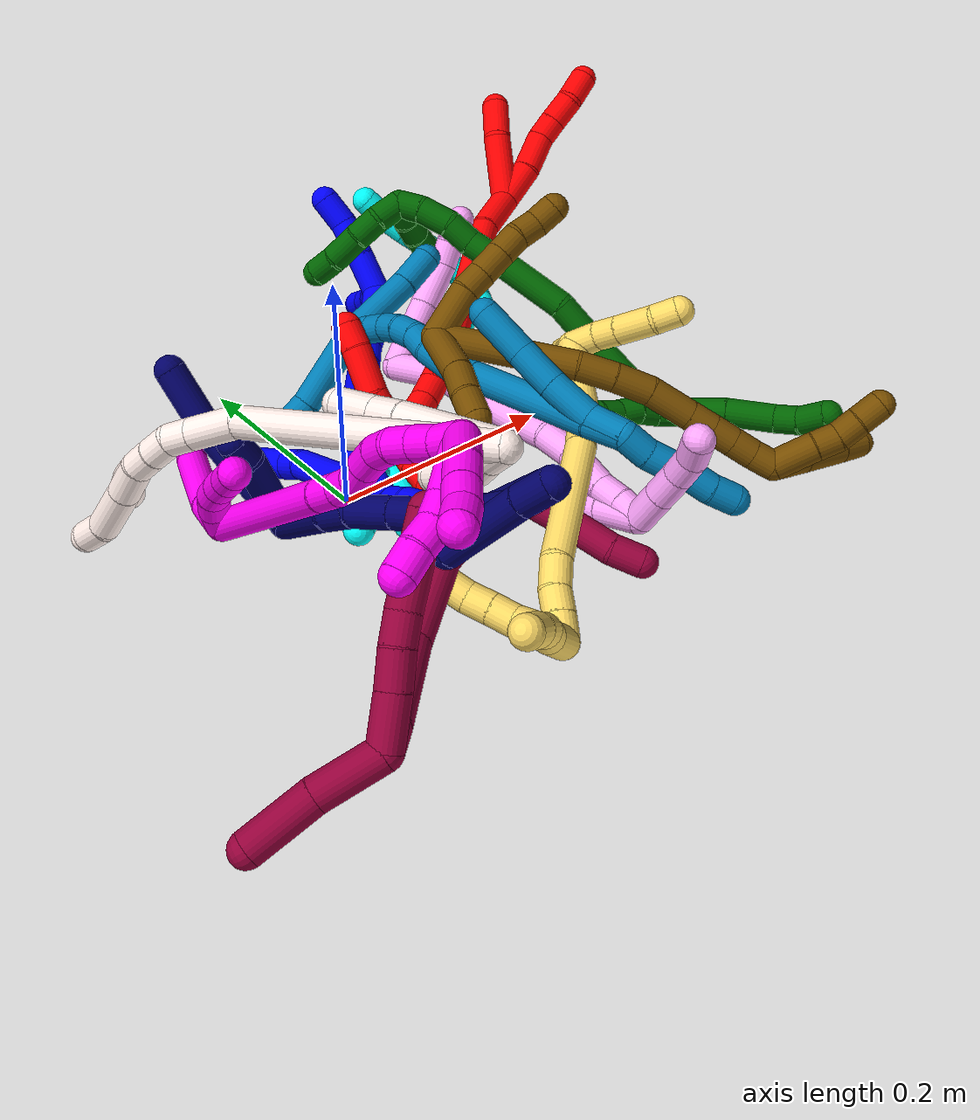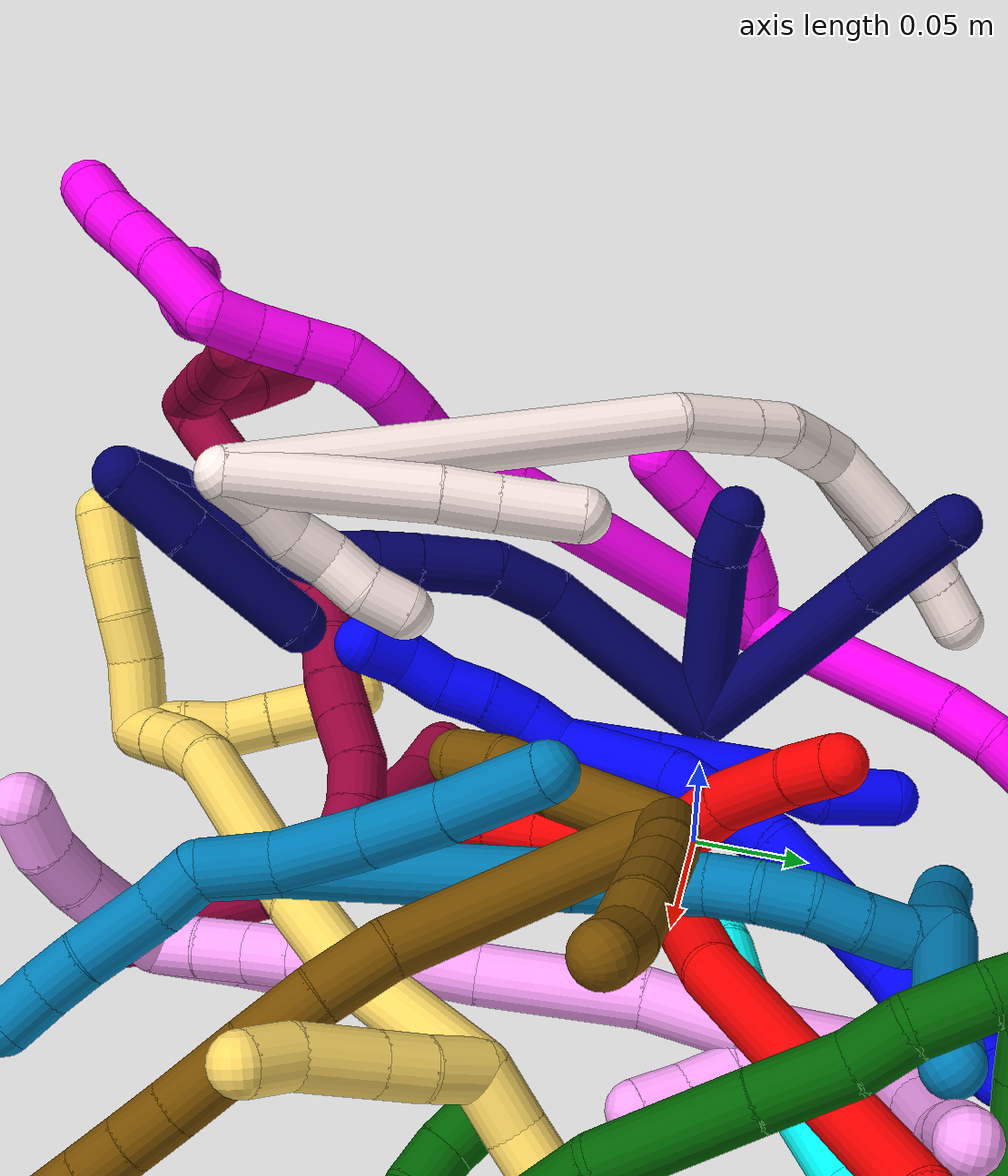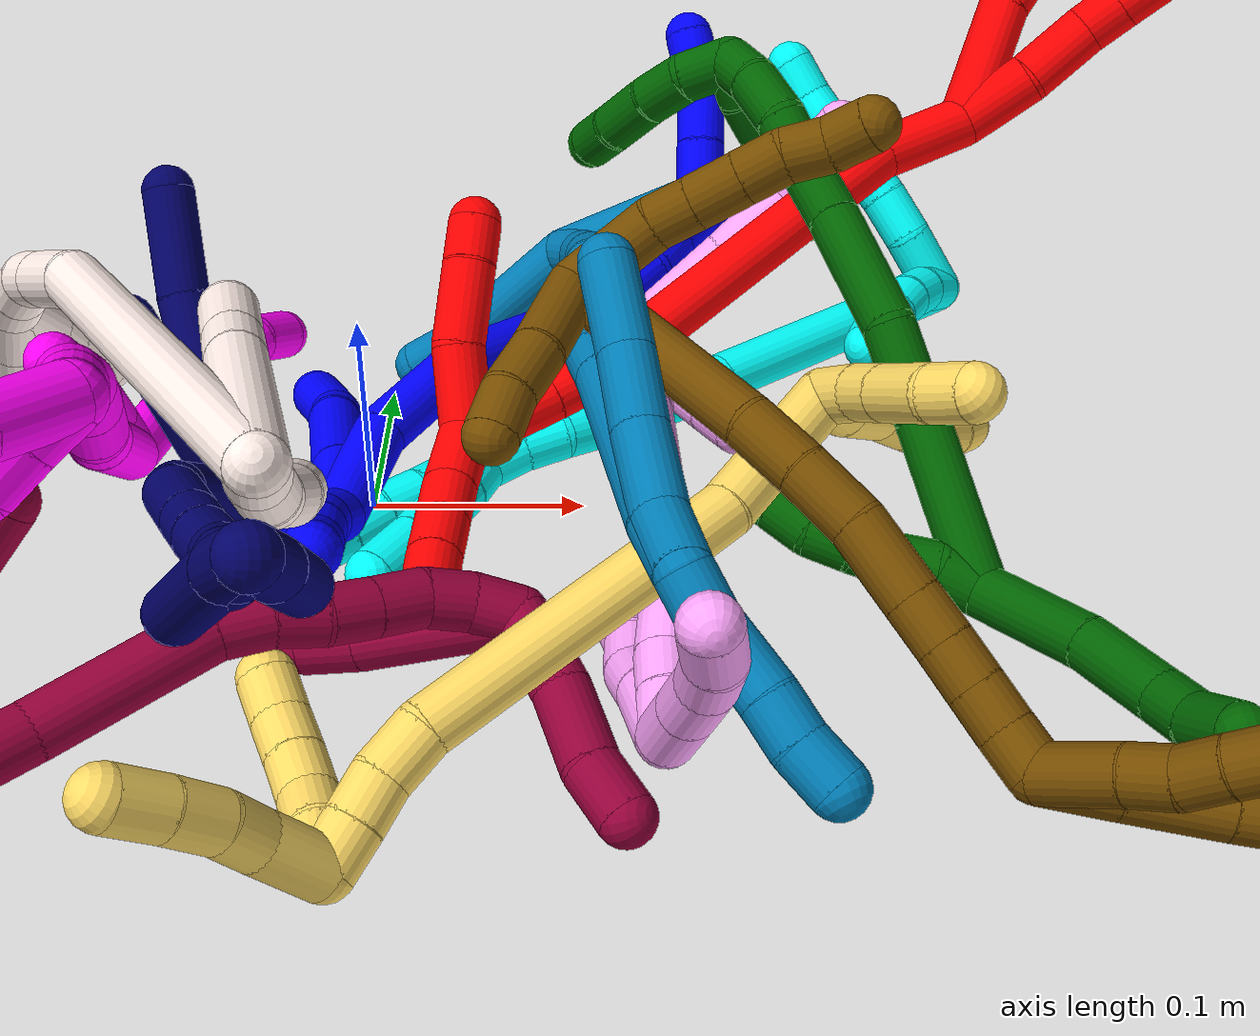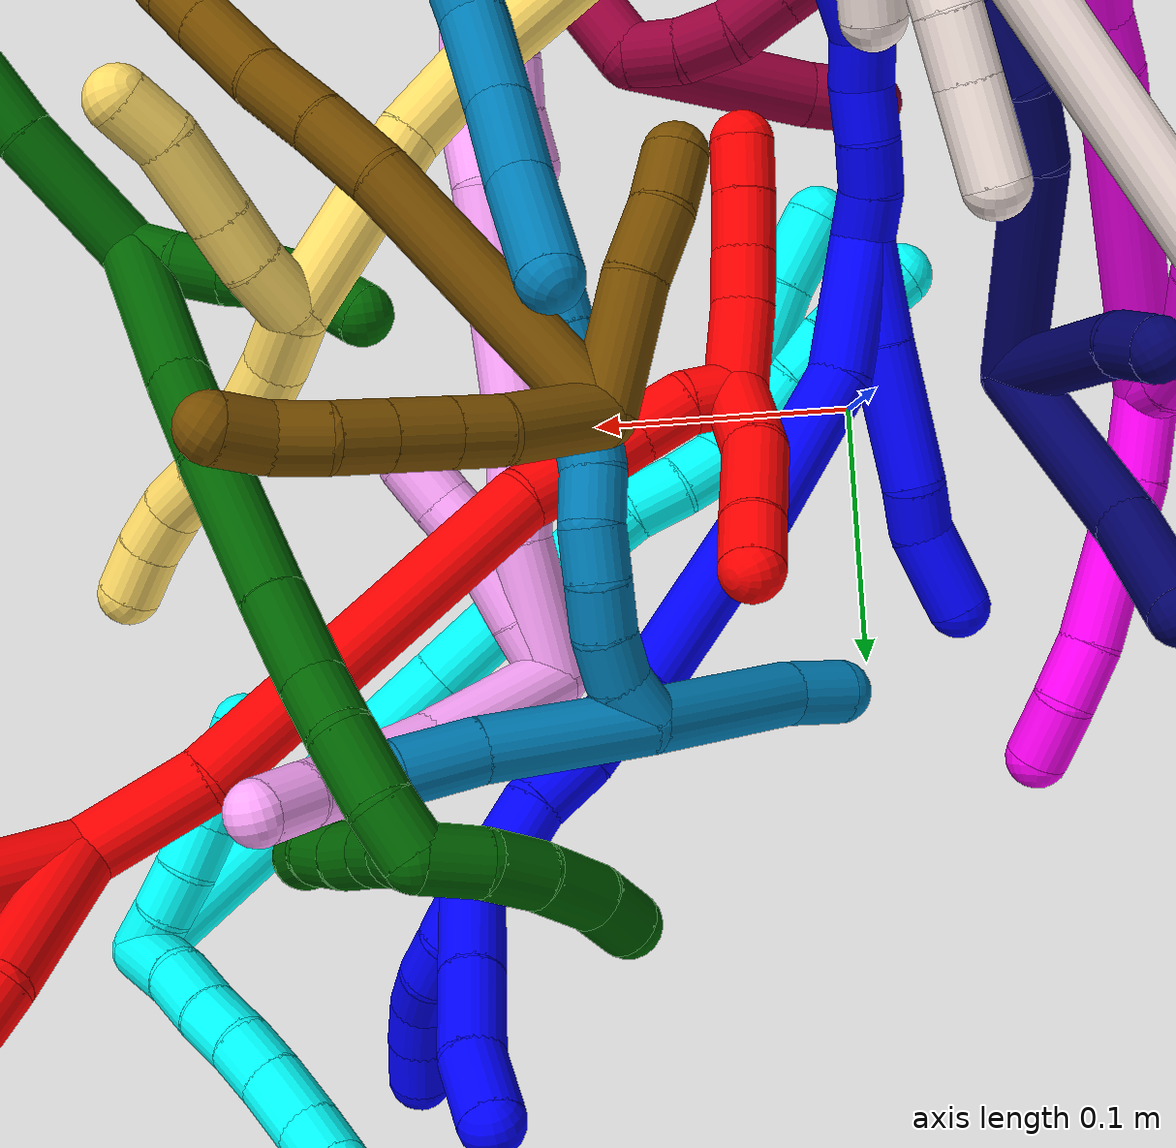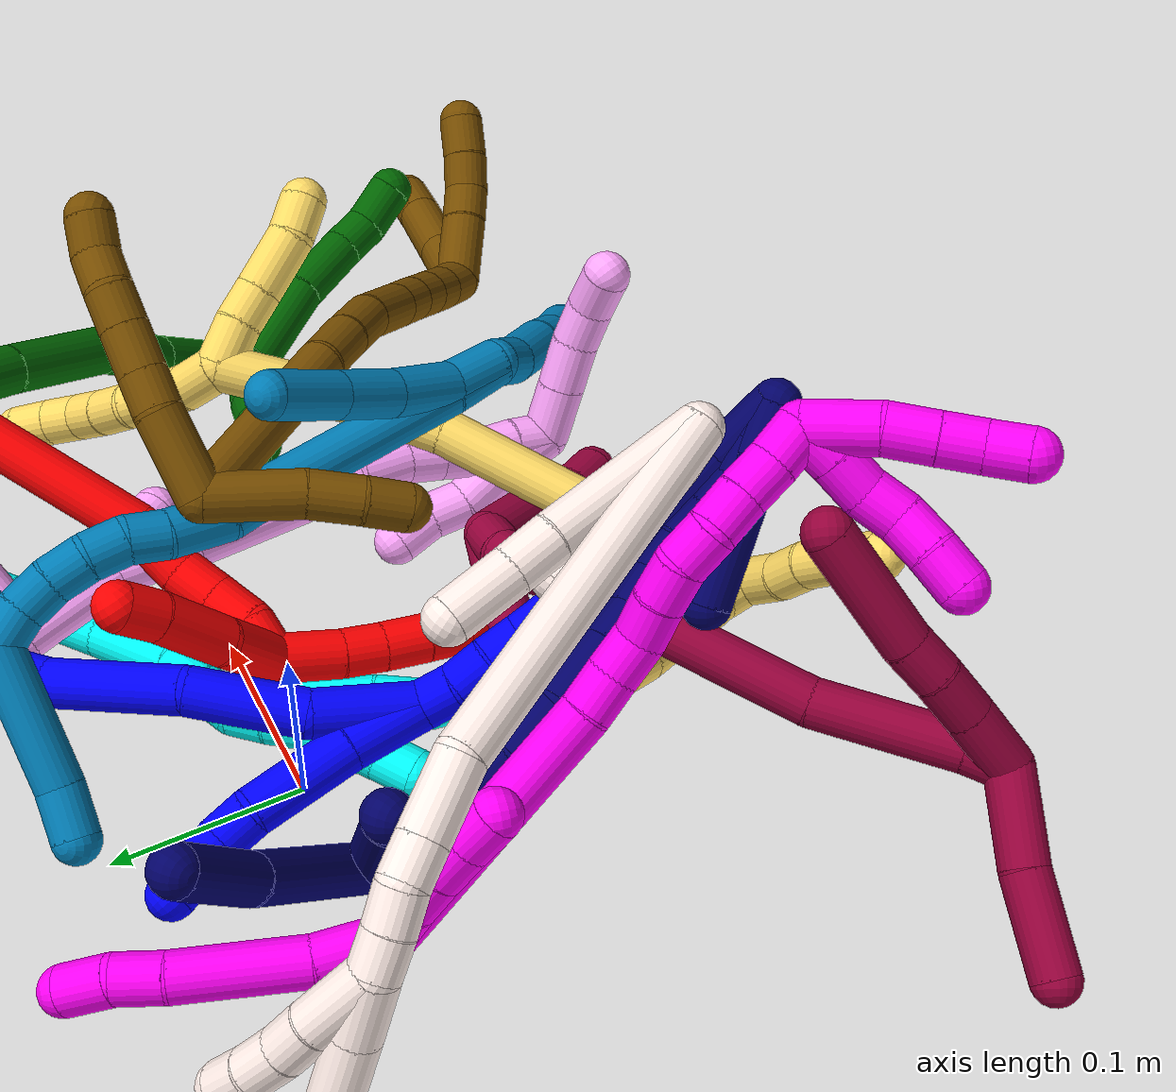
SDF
<sdf version="1.7">
 <world name="default">
  <plugin name="TubeGeneratorPlugin" filename="libtube_generator_plugin.so"/>
  <model name="photoneo_s_sensor">
   <static>1</static>
   <pose>0 0 2 1.57079 1.57079 3.14159</pose>
   <link name="link">
    <inertial><mass>0.1</mass></inertial>
    <sensor name="sensor" type="depth">
     <update_rate>30</update_rate>
     <camera>
      <horizontal_fov>1.22</horizontal_fov>
      <image><width>1920</width><height>1200</height><format>B8G8R8</format></image>
      <clip><near>0.1</near><far>4</far></clip>
      <depth_camera><output>points</output></depth_camera>
     </camera>
     <plugin name="camera_plugin" filename="libgazebo_ros_depth_camera.so">
      <baseline>0.2</baseline>
      <alwaysOn>1</alwaysOn>
      <updateRate>0.0</updateRate>
      <cameraName>camera_ir</cameraName>
      <imageTopicName>/camera/color/image_raw</imageTopicName>
      <cameraInfoTopicName>/camera/color/camera_info</cameraInfoTopicName>
      <depthImageTopicName>/camera/depth/image_raw</depthImageTopicName>
      <depthImageCameraInfoTopicName>/camera/depth/camera_info</depthImageCameraInfoTopicName>
      <pointCloudTopicName>/camera/depth/points</pointCloudTopicName>
      <frameName>fr_optical</frameName>
      <pointCloudCutoff>0.1</pointCloudCutoff>
      <pointCloudCutoffMax>2.0</pointCloudCutoffMax>
      <distortionK1>0</distortionK1>
      <distortionK2>0</distortionK2>
      <distortionK3>0</distortionK3>
      <distortionT1>0</distortionT1>
      <distortionT2>0</distortionT2>
      <CxPrime>0</CxPrime>
      <Cx>0</Cx>
      <Cy>0</Cy>
      <focalLength>0</focalLength>
      <hackBaseline>0</hackBaseline>
     </plugin>
    </sensor>
   </link>
  </model>
  <gravity>0 0 -9.8</gravity>
  <magnetic_field>6e-06 2.3e-05 -4.2e-05</magnetic_field>
  <atmosphere type="adiabatic"/>
  <physics name="default_physics" default="0" type="ode">
   <max_step_size>0.003</max_step_size>
   <real_time_factor>1</real_time_factor>
   <real_time_update_rate>1000</real_time_update_rate>
   <max_contacts>10000</max_contacts>
   <ode>
    <solver>
     <type>quick</type>
     <iters>100</iters>
     <sor>1.3</sor>
     <use_dynamic_moi_rescaling>0</use_dynamic_moi_rescaling>
    </solver>
    <constraints>
     <contact_max_correcting_vel>0</contact_max_correcting_vel>
     <contact_surface_layer>0.001</contact_surface_layer>
     <cfm>0</cfm>
     <erp>0.2</erp>
    </constraints>
   </ode>
  </physics>
  <scene><ambient>0.4 0.4 0.4 1</ambient><background>0.7 0.7 0.7 1</background><shadows>0</shadows></scene>
  <audio><device>default</device></audio>
  <spherical_coordinates>
   <surface_model>EARTH_WGS84</surface_model>
   <latitude_deg>0</latitude_deg>
   <longitude_deg>0</longitude_deg>
   <elevation>0</elevation>
   <heading_deg>0</heading_deg>
  </spherical_coordinates>
  <model name="bin">
   <static>1</static>
   <link name="bottom">
    <collision name="collision-bottom">
     <pose>0 0 -0.01 0 -0 0</pose>
     <geometry><box><size>0.8 0.6 0.02</size></box></geometry>
     <surface>
      <friction><ode><mu>100</mu><mu2>100</mu2></ode></friction>
      <contact><collide_bitmask>65535</collide_bitmask></contact>
     </surface>
    </collision>
   </link>
   <link name="west_wall">
    <collision name="collision-west_wall">
     <pose>-0.41 0 0.1 0 -0 0</pose>
     <geometry><box><size>0.02 0.6 0.2</size></box></geometry>
     <surface>
      <friction><ode><mu>100</mu><mu2>100</mu2></ode></friction>
      <contact><collide_bitmask>65535</collide_bitmask></contact>
     </surface>
    </collision>
   </link>
   <link name="east_wall">
    <collision name="collision-east_wall">
     <pose>0.41 0 0.1 0 -0 0</pose>
     <geometry><box><size>0.02 0.6 0.2</size></box></geometry>
     <surface>
      <friction><ode><mu>100</mu><mu2>100</mu2></ode></friction>
      <contact><collide_bitmask>65535</collide_bitmask></contact>
     </surface>
    </collision>
   </link>
   <link name="south_wall">
    <collision name="collision-south_wall">
     <pose>0 -0.31 0.1 0 -0 0</pose>
     <geometry><box><size>0.8 0.02 0.2</size></box></geometry>
     <surface>
      <friction><ode><mu>100</mu><mu2>100</mu2></ode></friction>
      <contact><collide_bitmask>65535</collide_bitmask></contact>
     </surface>
    </collision>
   </link>
   <link name="north_wall">
    <collision name="collision-north_wall">
     <pose>0 0.31 0.1 0 -0 0</pose>
     <geometry><box><size>0.8 0.02 0.2</size></box></geometry>
     <surface>
      <friction><ode><mu>100</mu><mu2>100</mu2></ode></friction>
      <contact><collide_bitmask>65535</collide_bitmask></contact>
     </surface>
    </collision>
   </link>
  </model>
  <model name="1">
   <static>0</static>
   <link name="1">
    <collision name="collision-cylinder-e_1_2_8">
     <pose>0.007049 0.00426 -0.018745 -2.91811 0.351485 -2.01451</pose>
     <geometry><cylinder><radius>0.0125</radius><length>0.04095</length></cylinder></geometry>
     <surface>
      <friction><ode><mu>1.16</mu><mu2>1.16</mu2><slip1>0</slip1><slip2>0</slip2></ode></friction>
      <contact><ode><kp>1e+06</kp><kd>1</kd><max_vel>0</max_vel><min_depth>0.001</min_depth></ode></contact>
     </surface>
    </collision>
    <visual name="visual-cylinder-e_1_2_8">
     <pose>0.007049 0.00426 -0.018745 -2.91811 0.351485 -2.01451</pose>
     <geometry><cylinder><radius>0.0125</radius><length>0.04095</length></cylinder></geometry>
     <material><ambient>0 0 1 1</ambient></material>
    </visual>
    <collision name="collision-cylinder-e_2_8_9">
     <pose>0.021313 0.014524 -0.063314 -2.91319 0.265669 -1.72291</pose>
     <geometry><cylinder><radius>0.0125</radius><length>0.054952</length></cylinder></geometry>
     <surface>
      <friction><ode><mu>1.16</mu><mu2>1.16</mu2><slip1>0</slip1><slip2>0</slip2></ode></friction>
      <contact><ode><kp>1e+06</kp><kd>1</kd><max_vel>0</max_vel><min_depth>0.001</min_depth></ode></contact>
     </surface>
    </collision>
    <visual name="visual-cylinder-e_2_8_9">
     <pose>0.021313 0.014524 -0.063314 -2.91319 0.265669 -1.72291</pose>
     <geometry><cylinder><radius>0.0125</radius><length>0.054952</length></cylinder></geometry>
     <material><ambient>0 0 1 1</ambient></material>
    </visual>
    <collision name="collision-cylinder-e_3_9_10">
     <pose>0.028909 0.021017 -0.099191 -3.09285 0.037995 -1.32409</pose>
     <geometry><cylinder><radius>0.0125</radius><length>0.020146</length></cylinder></geometry>
     <surface>
      <friction><ode><mu>1.16</mu><mu2>1.16</mu2><slip1>0</slip1><slip2>0</slip2></ode></friction>
      <contact><ode><kp>1e+06</kp><kd>1</kd><max_vel>0</max_vel><min_depth>0.001</min_depth></ode></contact>
     </surface>
    </collision>
    <visual name="visual-cylinder-e_3_9_10">
     <pose>0.028909 0.021017 -0.099191 -3.09285 0.037995 -1.32409</pose>
     <geometry><cylinder><radius>0.0125</radius><length>0.020146</length></cylinder></geometry>
     <material><ambient>0 0 1 1</ambient></material>
    </visual>
    <collision name="collision-cylinder-e_4_10_6">
     <pose>0.030337 0.027934 -0.124923 -2.75255 0.061588 -0.310198</pose>
     <geometry><cylinder><radius>0.0125</radius><length>0.033952</length></cylinder></geometry>
     <surface>
      <friction><ode><mu>1.16</mu><mu2>1.16</mu2><slip1>0</slip1><slip2>0</slip2></ode></friction>
      <contact><ode><kp>1e+06</kp><kd>1</kd><max_vel>0</max_vel><min_depth>0.001</min_depth></ode></contact>
     </surface>
    </collision>
    <visual name="visual-cylinder-e_4_10_6">
     <pose>0.030337 0.027934 -0.124923 -2.75255 0.061588 -0.310198</pose>
     <geometry><cylinder><radius>0.0125</radius><length>0.033952</length></cylinder></geometry>
     <material><ambient>0 0 1 1</ambient></material>
    </visual>
    <collision name="collision-cylinder-e_1_2_11">
     <pose>-0.001403 0.002413 0.009602 -0.246199 -0.140797 0.017449</pose>
     <geometry><cylinder><radius>0.0125</radius><length>0.02</length></cylinder></geometry>
     <surface>
      <friction><ode><mu>1.16</mu><mu2>1.16</mu2><slip1>0</slip1><slip2>0</slip2></ode></friction>
      <contact><ode><kp>1e+06</kp><kd>1</kd><max_vel>0</max_vel><min_depth>0.001</min_depth></ode></contact>
     </surface>
    </collision>
    <visual name="visual-cylinder-e_1_2_11">
     <pose>-0.001403 0.002413 0.009602 -0.246199 -0.140797 0.017449</pose>
     <geometry><cylinder><radius>0.0125</radius><length>0.02</length></cylinder></geometry>
     <material><ambient>0 0 1 1</ambient></material>
    </visual>
    <collision name="collision-cylinder-e_2_11_12">
     <pose>-0.003333 0.005203 0.029184 -0.037746 -0.052633 0.000994</pose>
     <geometry><cylinder><radius>0.0125</radius><length>0.02</length></cylinder></geometry>
     <surface>
      <friction><ode><mu>1.16</mu><mu2>1.16</mu2><slip1>0</slip1><slip2>0</slip2></ode></friction>
      <contact><ode><kp>1e+06</kp><kd>1</kd><max_vel>0</max_vel><min_depth>0.001</min_depth></ode></contact>
     </surface>
    </collision>
    <visual name="visual-cylinder-e_2_11_12">
     <pose>-0.003333 0.005203 0.029184 -0.037746 -0.052633 0.000994</pose>
     <geometry><cylinder><radius>0.0125</radius><length>0.02</length></cylinder></geometry>
     <material><ambient>0 0 1 1</ambient></material>
    </visual>
    <collision name="collision-cylinder-e_3_12_13">
     <pose>-0.005473 0.004907 0.049009 0.068231 -0.162141 -0.005546</pose>
     <geometry><cylinder><radius>0.0125</radius><length>0.02</length></cylinder></geometry>
     <surface>
      <friction><ode><mu>1.16</mu><mu2>1.16</mu2><slip1>0</slip1><slip2>0</slip2></ode></friction>
      <contact><ode><kp>1e+06</kp><kd>1</kd><max_vel>0</max_vel><min_depth>0.001</min_depth></ode></contact>
     </surface>
    </collision>
    <visual name="visual-cylinder-e_3_12_13">
     <pose>-0.005473 0.004907 0.049009 0.068231 -0.162141 -0.005546</pose>
     <geometry><cylinder><radius>0.0125</radius><length>0.02</length></cylinder></geometry>
     <material><ambient>0 0 1 1</ambient></material>
    </visual>
    <collision name="collision-cylinder-e_4_13_14">
     <pose>-0.007339 0.005626 0.068754 -0.139635 -0.025161 0.00176</pose>
     <geometry><cylinder><radius>0.0125</radius><length>0.02</length></cylinder></geometry>
     <surface>
      <friction><ode><mu>1.16</mu><mu2>1.16</mu2><slip1>0</slip1><slip2>0</slip2></ode></friction>
      <contact><ode><kp>1e+06</kp><kd>1</kd><max_vel>0</max_vel><min_depth>0.001</min_depth></ode></contact>
     </surface>
    </collision>
    <visual name="visual-cylinder-e_4_13_14">
     <pose>-0.007339 0.005626 0.068754 -0.139635 -0.025161 0.00176</pose>
     <geometry><cylinder><radius>0.0125</radius><length>0.02</length></cylinder></geometry>
     <material><ambient>0 0 1 1</ambient></material>
    </visual>
    <collision name="collision-cylinder-e_5_14_5">
     <pose>-0.005932 0.005738 0.088432 0.13005 0.166596 0.010873</pose>
     <geometry><cylinder><radius>0.0125</radius><length>0.02</length></cylinder></geometry>
     <surface>
      <friction><ode><mu>1.16</mu><mu2>1.16</mu2><slip1>0</slip1><slip2>0</slip2></ode></friction>
      <contact><ode><kp>1e+06</kp><kd>1</kd><max_vel>0</max_vel><min_depth>0.001</min_depth></ode></contact>
     </surface>
    </collision>
    <visual name="visual-cylinder-e_5_14_5">
     <pose>-0.005932 0.005738 0.088432 0.13005 0.166596 0.010873</pose>
     <geometry><cylinder><radius>0.0125</radius><length>0.02</length></cylinder></geometry>
     <material><ambient>0 0 1 1</ambient></material>
    </visual>
    <collision name="collision-cylinder-e_1_2_15">
     <pose>0.018278 -0.000413 -0.020298 3.12123 0.732992 3.08854</pose>
     <geometry><cylinder><radius>0.0125</radius><length>0.054636</length></cylinder></geometry>
     <surface>
      <friction><ode><mu>1.16</mu><mu2>1.16</mu2><slip1>0</slip1><slip2>0</slip2></ode></friction>
      <contact><ode><kp>1e+06</kp><kd>1</kd><max_vel>0</max_vel><min_depth>0.001</min_depth></ode></contact>
     </surface>
    </collision>
    <visual name="visual-cylinder-e_1_2_15">
     <pose>0.018278 -0.000413 -0.020298 3.12123 0.732992 3.08854</pose>
     <geometry><cylinder><radius>0.0125</radius><length>0.054636</length></cylinder></geometry>
     <material><ambient>0 0 1 1</ambient></material>
    </visual>
    <collision name="collision-cylinder-e_2_15_16">
     <pose>0.058353 -0.010487 -0.058647 2.65021 0.816676 2.09107</pose>
     <geometry><cylinder><radius>0.0125</radius><length>0.059808</length></cylinder></geometry>
     <surface>
      <friction><ode><mu>1.16</mu><mu2>1.16</mu2><slip1>0</slip1><slip2>0</slip2></ode></friction>
      <contact><ode><kp>1e+06</kp><kd>1</kd><max_vel>0</max_vel><min_depth>0.001</min_depth></ode></contact>
     </surface>
    </collision>
    <visual name="visual-cylinder-e_2_15_16">
     <pose>0.058353 -0.010487 -0.058647 2.65021 0.816676 2.09107</pose>
     <geometry><cylinder><radius>0.0125</radius><length>0.059808</length></cylinder></geometry>
     <material><ambient>0 0 1 1</ambient></material>
    </visual>
    <collision name="collision-cylinder-e_3_16_17">
     <pose>0.098383 -0.038368 -0.102143 2.52016 0.527556 1.39853</pose>
     <geometry><cylinder><radius>0.0125</radius><length>0.072441</length></cylinder></geometry>
     <surface>
      <friction><ode><mu>1.16</mu><mu2>1.16</mu2><slip1>0</slip1><slip2>0</slip2></ode></friction>
      <contact><ode><kp>1e+06</kp><kd>1</kd><max_vel>0</max_vel><min_depth>0.001</min_depth></ode></contact>
     </surface>
    </collision>
    <visual name="visual-cylinder-e_3_16_17">
     <pose>0.098383 -0.038368 -0.102143 2.52016 0.527556 1.39853</pose>
     <geometry><cylinder><radius>0.0125</radius><length>0.072441</length></cylinder></geometry>
     <material><ambient>0 0 1 1</ambient></material>
    </visual>
    <collision name="collision-cylinder-e_4_17_18">
     <pose>0.12282 -0.063143 -0.133677 2.31943 0.606229 1.24469</pose>
     <geometry><cylinder><radius>0.0125</radius><length>0.021772</length></cylinder></geometry>
     <surface>
      <friction><ode><mu>1.16</mu><mu2>1.16</mu2><slip1>0</slip1><slip2>0</slip2></ode></friction>
      <contact><ode><kp>1e+06</kp><kd>1</kd><max_vel>0</max_vel><min_depth>0.001</min_depth></ode></contact>
     </surface>
    </collision>
    <visual name="visual-cylinder-e_4_17_18">
     <pose>0.12282 -0.063143 -0.133677 2.31943 0.606229 1.24469</pose>
     <geometry><cylinder><radius>0.0125</radius><length>0.021772</length></cylinder></geometry>
     <material><ambient>0 0 1 1</ambient></material>
    </visual>
    <collision name="collision-cylinder-e_5_18_19">
     <pose>0.137931 -0.073734 -0.145383 2.51835 0.910604 1.97777</pose>
     <geometry><cylinder><radius>0.0125</radius><length>0.022555</length></cylinder></geometry>
     <surface>
      <friction><ode><mu>1.16</mu><mu2>1.16</mu2><slip1>0</slip1><slip2>0</slip2></ode></friction>
      <contact><ode><kp>1e+06</kp><kd>1</kd><max_vel>0</max_vel><min_depth>0.001</min_depth></ode></contact>
     </surface>
    </collision>
    <visual name="visual-cylinder-e_5_18_19">
     <pose>0.137931 -0.073734 -0.145383 2.51835 0.910604 1.97777</pose>
     <geometry><cylinder><radius>0.0125</radius><length>0.022555</length></cylinder></geometry>
     <material><ambient>0 0 1 1</ambient></material>
    </visual>
    <collision name="collision-cylinder-e_6_19_20">
     <pose>0.158465 -0.083069 -0.154264 2.12307 1.0793 1.64087</pose>
     <geometry><cylinder><radius>0.0125</radius><length>0.026374</length></cylinder></geometry>
     <surface>
      <friction><ode><mu>1.16</mu><mu2>1.16</mu2><slip1>0</slip1><slip2>0</slip2></ode></friction>
      <contact><ode><kp>1e+06</kp><kd>1</kd><max_vel>0</max_vel><min_depth>0.001</min_depth></ode></contact>
     </surface>
    </collision>
    <visual name="visual-cylinder-e_6_19_20">
     <pose>0.158465 -0.083069 -0.154264 2.12307 1.0793 1.64087</pose>
     <geometry><cylinder><radius>0.0125</radius><length>0.026374</length></cylinder></geometry>
     <material><ambient>0 0 1 1</ambient></material>
    </visual>
    <collision name="collision-cylinder-e_7_20_21">
     <pose>0.178578 -0.091099 -0.162483 2.63769 0.982833 2.24498</pose>
     <geometry><cylinder><radius>0.0125</radius><length>0.020399</length></cylinder></geometry>
     <surface>
      <friction><ode><mu>1.16</mu><mu2>1.16</mu2><slip1>0</slip1><slip2>0</slip2></ode></friction>
      <contact><ode><kp>1e+06</kp><kd>1</kd><max_vel>0</max_vel><min_depth>0.001</min_depth></ode></contact>
     </surface>
    </collision>
    <visual name="visual-cylinder-e_7_20_21">
     <pose>0.178578 -0.091099 -0.162483 2.63769 0.982833 2.24498</pose>
     <geometry><cylinder><radius>0.0125</radius><length>0.020399</length></cylinder></geometry>
     <material><ambient>0 0 1 1</ambient></material>
    </visual>
    <collision name="collision-cylinder-e_8_21_1">
     <pose>0.196404 -0.09718 -0.172202 2.52898 1.01317 2.10552</pose>
     <geometry><cylinder><radius>0.0125</radius><length>0.022014</length></cylinder></geometry>
     <surface>
      <friction><ode><mu>1.16</mu><mu2>1.16</mu2><slip1>0</slip1><slip2>0</slip2></ode></friction>
      <contact><ode><kp>1e+06</kp><kd>1</kd><max_vel>0</max_vel><min_depth>0.001</min_depth></ode></contact>
     </surface>
    </collision>
    <visual name="visual-cylinder-e_8_21_1">
     <pose>0.196404 -0.09718 -0.172202 2.52898 1.01317 2.10552</pose>
     <geometry><cylinder><radius>0.0125</radius><length>0.022014</length></cylinder></geometry>
     <material><ambient>0 0 1 1</ambient></material>
    </visual>
    <collision name="collision-cylinder-e_1_1_22">
     <pose>0.209305 -0.105167 -0.18508 2.62228 0.36413 1.21205</pose>
     <geometry><cylinder><radius>0.0125</radius><length>0.02</length></cylinder></geometry>
     <surface>
      <friction><ode><mu>1.16</mu><mu2>1.16</mu2><slip1>0</slip1><slip2>0</slip2></ode></friction>
      <contact><ode><kp>1e+06</kp><kd>1</kd><max_vel>0</max_vel><min_depth>0.001</min_depth></ode></contact>
     </surface>
    </collision>
    <visual name="visual-cylinder-e_1_1_22">
     <pose>0.209305 -0.105167 -0.18508 2.62228 0.36413 1.21205</pose>
     <geometry><cylinder><radius>0.0125</radius><length>0.02</length></cylinder></geometry>
     <material><ambient>0 0 1 1</ambient></material>
    </visual>
    <collision name="collision-cylinder-e_2_22_23">
     <pose>0.213717 -0.115229 -0.20155 2.56586 0.085172 0.285865</pose>
     <geometry><cylinder><radius>0.0125</radius><length>0.02</length></cylinder></geometry>
     <surface>
      <friction><ode><mu>1.16</mu><mu2>1.16</mu2><slip1>0</slip1><slip2>0</slip2></ode></friction>
      <contact><ode><kp>1e+06</kp><kd>1</kd><max_vel>0</max_vel><min_depth>0.001</min_depth></ode></contact>
     </surface>
    </collision>
    <visual name="visual-cylinder-e_2_22_23">
     <pose>0.213717 -0.115229 -0.20155 2.56586 0.085172 0.285865</pose>
     <geometry><cylinder><radius>0.0125</radius><length>0.02</length></cylinder></geometry>
     <material><ambient>0 0 1 1</ambient></material>
    </visual>
    <collision name="collision-cylinder-e_3_23_24">
     <pose>0.212884 -0.125444 -0.218523 2.63412 -0.169195 -0.632079</pose>
     <geometry><cylinder><radius>0.0125</radius><length>0.02</length></cylinder></geometry>
     <surface>
      <friction><ode><mu>1.16</mu><mu2>1.16</mu2><slip1>0</slip1><slip2>0</slip2></ode></friction>
      <contact><ode><kp>1e+06</kp><kd>1</kd><max_vel>0</max_vel><min_depth>0.001</min_depth></ode></contact>
     </surface>
    </collision>
    <visual name="visual-cylinder-e_3_23_24">
     <pose>0.212884 -0.125444 -0.218523 2.63412 -0.169195 -0.632079</pose>
     <geometry><cylinder><radius>0.0125</radius><length>0.02</length></cylinder></geometry>
     <material><ambient>0 0 1 1</ambient></material>
    </visual>
    <collision name="collision-cylinder-e_4_24_25">
     <pose>0.21114 -0.133112 -0.236714 2.84972 -0.006024 -0.040978</pose>
     <geometry><cylinder><radius>0.0125</radius><length>0.02</length></cylinder></geometry>
     <surface>
      <friction><ode><mu>1.16</mu><mu2>1.16</mu2><slip1>0</slip1><slip2>0</slip2></ode></friction>
      <contact><ode><kp>1e+06</kp><kd>1</kd><max_vel>0</max_vel><min_depth>0.001</min_depth></ode></contact>
     </surface>
    </collision>
    <visual name="visual-cylinder-e_4_24_25">
     <pose>0.21114 -0.133112 -0.236714 2.84972 -0.006024 -0.040978</pose>
     <geometry><cylinder><radius>0.0125</radius><length>0.02</length></cylinder></geometry>
     <material><ambient>0 0 1 1</ambient></material>
    </visual>
    <collision name="collision-cylinder-e_5_25_4">
     <pose>0.211433 -0.137832 -0.256114 2.95607 0.035302 0.375067</pose>
     <geometry><cylinder><radius>0.0125</radius><length>0.02</length></cylinder></geometry>
     <surface>
      <friction><ode><mu>1.16</mu><mu2>1.16</mu2><slip1>0</slip1><slip2>0</slip2></ode></friction>
      <contact><ode><kp>1e+06</kp><kd>1</kd><max_vel>0</max_vel><min_depth>0.001</min_depth></ode></contact>
     </surface>
    </collision>
    <visual name="visual-cylinder-e_5_25_4">
     <pose>0.211433 -0.137832 -0.256114 2.95607 0.035302 0.375067</pose>
     <geometry><cylinder><radius>0.0125</radius><length>0.02</length></cylinder></geometry>
     <material><ambient>0 0 1 1</ambient></material>
    </visual>
    <collision name="collision-cylinder-e_1_1_26">
     <pose>0.222125 -0.092979 -0.181515 -2.1129 1.07718 -1.62658</pose>
     <geometry><cylinder><radius>0.0125</radius><length>0.037203</length></cylinder></geometry>
     <surface>
      <friction><ode><mu>1.16</mu><mu2>1.16</mu2><slip1>0</slip1><slip2>0</slip2></ode></friction>
      <contact><ode><kp>1e+06</kp><kd>1</kd><max_vel>0</max_vel><min_depth>0.001</min_depth></ode></contact>
     </surface>
    </collision>
    <visual name="visual-cylinder-e_1_1_26">
     <pose>0.222125 -0.092979 -0.181515 -2.1129 1.07718 -1.62658</pose>
     <geometry><cylinder><radius>0.0125</radius><length>0.037203</length></cylinder></geometry>
     <material><ambient>0 0 1 1</ambient></material>
    </visual>
    <collision name="collision-cylinder-e_2_26_27">
     <pose>0.253511 -0.078667 -0.191481 -2.24631 1.0471 -1.75399</pose>
     <geometry><cylinder><radius>0.0125</radius><length>0.034654</length></cylinder></geometry>
     <surface>
      <friction><ode><mu>1.16</mu><mu2>1.16</mu2><slip1>0</slip1><slip2>0</slip2></ode></friction>
      <contact><ode><kp>1e+06</kp><kd>1</kd><max_vel>0</max_vel><min_depth>0.001</min_depth></ode></contact>
     </surface>
    </collision>
    <visual name="visual-cylinder-e_2_26_27">
     <pose>0.253511 -0.078667 -0.191481 -2.24631 1.0471 -1.75399</pose>
     <geometry><cylinder><radius>0.0125</radius><length>0.034654</length></cylinder></geometry>
     <material><ambient>0 0 1 1</ambient></material>
    </visual>
    <collision name="collision-cylinder-e_3_27_3">
     <pose>0.278902 -0.063393 -0.201104 -2.0297 0.830255 -1.23397</pose>
     <geometry><cylinder><radius>0.0125</radius><length>0.028142</length></cylinder></geometry>
     <surface>
      <friction><ode><mu>1.16</mu><mu2>1.16</mu2><slip1>0</slip1><slip2>0</slip2></ode></friction>
      <contact><ode><kp>1e+06</kp><kd>1</kd><max_vel>0</max_vel><min_depth>0.001</min_depth></ode></contact>
     </surface>
    </collision>
    <visual name="visual-cylinder-e_3_27_3">
     <pose>0.278902 -0.063393 -0.201104 -2.0297 0.830255 -1.23397</pose>
     <geometry><cylinder><radius>0.0125</radius><length>0.028142</length></cylinder></geometry>
     <material><ambient>0 0 1 1</ambient></material>
    </visual>
    <collision name="collision-sphere-3">
     <pose>0.289288 -0.054882 -0.20531 0 -0 0</pose>
     <geometry><sphere><radius>0.0125</radius></sphere></geometry>
     <surface>
      <friction><ode><mu>1.16</mu><mu2>1.16</mu2><slip1>0</slip1><slip2>0</slip2></ode></friction>
      <contact><ode><kp>1e+06</kp><kd>1</kd><max_vel>0</max_vel><min_depth>0.001</min_depth></ode></contact>
     </surface>
    </collision>
    <visual name="visual-sphere-3">
     <pose>0.289288 -0.054882 -0.20531 0 -0 0</pose>
     <geometry><sphere><radius>0.0125</radius></sphere></geometry>
     <material><ambient>0 0 1 1</ambient></material>
    </visual>
    <collision name="collision-sphere-27">
     <pose>0.268516 -0.071905 -0.196899 0 -0 0</pose>
     <geometry><sphere><radius>0.0125</radius></sphere></geometry>
     <surface>
      <friction><ode><mu>1.16</mu><mu2>1.16</mu2><slip1>0</slip1><slip2>0</slip2></ode></friction>
      <contact><ode><kp>1e+06</kp><kd>1</kd><max_vel>0</max_vel><min_depth>0.001</min_depth></ode></contact>
     </surface>
    </collision>
    <visual name="visual-sphere-27">
     <pose>0.268516 -0.071905 -0.196899 0 -0 0</pose>
     <geometry><sphere><radius>0.0125</radius></sphere></geometry>
     <material><ambient>0 0 1 1</ambient></material>
    </visual>
    <collision name="collision-sphere-26">
     <pose>0.238506 -0.085429 -0.186062 0 -0 0</pose>
     <geometry><sphere><radius>0.0125</radius></sphere></geometry>
     <surface>
      <friction><ode><mu>1.16</mu><mu2>1.16</mu2><slip1>0</slip1><slip2>0</slip2></ode></friction>
      <contact><ode><kp>1e+06</kp><kd>1</kd><max_vel>0</max_vel><min_depth>0.001</min_depth></ode></contact>
     </surface>
    </collision>
    <visual name="visual-sphere-26">
     <pose>0.238506 -0.085429 -0.186062 0 -0 0</pose>
     <geometry><sphere><radius>0.0125</radius></sphere></geometry>
     <material><ambient>0 0 1 1</ambient></material>
    </visual>
    <collision name="collision-sphere-4">
     <pose>0.211786 -0.139676 -0.265936 0 -0 0</pose>
     <geometry><sphere><radius>0.0125</radius></sphere></geometry>
     <surface>
      <friction><ode><mu>1.16</mu><mu2>1.16</mu2><slip1>0</slip1><slip2>0</slip2></ode></friction>
      <contact><ode><kp>1e+06</kp><kd>1</kd><max_vel>0</max_vel><min_depth>0.001</min_depth></ode></contact>
     </surface>
    </collision>
    <visual name="visual-sphere-4">
     <pose>0.211786 -0.139676 -0.265936 0 -0 0</pose>
     <geometry><sphere><radius>0.0125</radius></sphere></geometry>
     <material><ambient>0 0 1 1</ambient></material>
    </visual>
    <collision name="collision-sphere-25">
     <pose>0.21108 -0.135989 -0.246291 0 -0 0</pose>
     <geometry><sphere><radius>0.0125</radius></sphere></geometry>
     <surface>
      <friction><ode><mu>1.16</mu><mu2>1.16</mu2><slip1>0</slip1><slip2>0</slip2></ode></friction>
      <contact><ode><kp>1e+06</kp><kd>1</kd><max_vel>0</max_vel><min_depth>0.001</min_depth></ode></contact>
     </surface>
    </collision>
    <visual name="visual-sphere-25">
     <pose>0.21108 -0.135989 -0.246291 0 -0 0</pose>
     <geometry><sphere><radius>0.0125</radius></sphere></geometry>
     <material><ambient>0 0 1 1</ambient></material>
    </visual>
    <collision name="collision-sphere-24">
     <pose>0.2112 -0.130234 -0.227138 0 -0 0</pose>
     <geometry><sphere><radius>0.0125</radius></sphere></geometry>
     <surface>
      <friction><ode><mu>1.16</mu><mu2>1.16</mu2><slip1>0</slip1><slip2>0</slip2></ode></friction>
      <contact><ode><kp>1e+06</kp><kd>1</kd><max_vel>0</max_vel><min_depth>0.001</min_depth></ode></contact>
     </surface>
    </collision>
    <visual name="visual-sphere-24">
     <pose>0.2112 -0.130234 -0.227138 0 -0 0</pose>
     <geometry><sphere><radius>0.0125</radius></sphere></geometry>
     <material><ambient>0 0 1 1</ambient></material>
    </visual>
    <collision name="collision-sphere-23">
     <pose>0.214568 -0.120654 -0.209908 0 -0 0</pose>
     <geometry><sphere><radius>0.0125</radius></sphere></geometry>
     <surface>
      <friction><ode><mu>1.16</mu><mu2>1.16</mu2><slip1>0</slip1><slip2>0</slip2></ode></friction>
      <contact><ode><kp>1e+06</kp><kd>1</kd><max_vel>0</max_vel><min_depth>0.001</min_depth></ode></contact>
     </surface>
    </collision>
    <visual name="visual-sphere-23">
     <pose>0.214568 -0.120654 -0.209908 0 -0 0</pose>
     <geometry><sphere><radius>0.0125</radius></sphere></geometry>
     <material><ambient>0 0 1 1</ambient></material>
    </visual>
    <collision name="collision-sphere-22">
     <pose>0.212867 -0.109804 -0.193193 0 -0 0</pose>
     <geometry><sphere><radius>0.0125</radius></sphere></geometry>
     <surface>
      <friction><ode><mu>1.16</mu><mu2>1.16</mu2><slip1>0</slip1><slip2>0</slip2></ode></friction>
      <contact><ode><kp>1e+06</kp><kd>1</kd><max_vel>0</max_vel><min_depth>0.001</min_depth></ode></contact>
     </surface>
    </collision>
    <visual name="visual-sphere-22">
     <pose>0.212867 -0.109804 -0.193193 0 -0 0</pose>
     <geometry><sphere><radius>0.0125</radius></sphere></geometry>
     <material><ambient>0 0 1 1</ambient></material>
    </visual>
    <collision name="collision-sphere-1">
     <pose>0.205744 -0.100529 -0.176968 0 -0 0</pose>
     <geometry><sphere><radius>0.0125</radius></sphere></geometry>
     <surface>
      <friction><ode><mu>1.16</mu><mu2>1.16</mu2><slip1>0</slip1><slip2>0</slip2></ode></friction>
      <contact><ode><kp>1e+06</kp><kd>1</kd><max_vel>0</max_vel><min_depth>0.001</min_depth></ode></contact>
     </surface>
    </collision>
    <visual name="visual-sphere-1">
     <pose>0.205744 -0.100529 -0.176968 0 -0 0</pose>
     <geometry><sphere><radius>0.0125</radius></sphere></geometry>
     <material><ambient>0 0 1 1</ambient></material>
    </visual>
    <collision name="collision-sphere-21">
     <pose>0.187065 -0.093831 -0.167437 0 -0 0</pose>
     <geometry><sphere><radius>0.0125</radius></sphere></geometry>
     <surface>
      <friction><ode><mu>1.16</mu><mu2>1.16</mu2><slip1>0</slip1><slip2>0</slip2></ode></friction>
      <contact><ode><kp>1e+06</kp><kd>1</kd><max_vel>0</max_vel><min_depth>0.001</min_depth></ode></contact>
     </surface>
    </collision>
    <visual name="visual-sphere-21">
     <pose>0.187065 -0.093831 -0.167437 0 -0 0</pose>
     <geometry><sphere><radius>0.0125</radius></sphere></geometry>
     <material><ambient>0 0 1 1</ambient></material>
    </visual>
    <collision name="collision-sphere-11">
     <pose>-0.002807 0.004826 0.019205 0 -0 0</pose>
     <geometry><sphere><radius>0.0125</radius></sphere></geometry>
     <surface>
      <friction><ode><mu>1.16</mu><mu2>1.16</mu2><slip1>0</slip1><slip2>0</slip2></ode></friction>
      <contact><ode><kp>1e+06</kp><kd>1</kd><max_vel>0</max_vel><min_depth>0.001</min_depth></ode></contact>
     </surface>
    </collision>
    <visual name="visual-sphere-11">
     <pose>-0.002807 0.004826 0.019205 0 -0 0</pose>
     <geometry><sphere><radius>0.0125</radius></sphere></geometry>
     <material><ambient>0 0 1 1</ambient></material>
    </visual>
    <collision name="collision-sphere-6">
     <pose>0.031382 0.034361 -0.1406 0 -0 0</pose>
     <geometry><sphere><radius>0.0125</radius></sphere></geometry>
     <surface>
      <friction><ode><mu>1.16</mu><mu2>1.16</mu2><slip1>0</slip1><slip2>0</slip2></ode></friction>
      <contact><ode><kp>1e+06</kp><kd>1</kd><max_vel>0</max_vel><min_depth>0.001</min_depth></ode></contact>
     </surface>
    </collision>
    <visual name="visual-sphere-6">
     <pose>0.031382 0.034361 -0.1406 0 -0 0</pose>
     <geometry><sphere><radius>0.0125</radius></sphere></geometry>
     <material><ambient>0 0 1 1</ambient></material>
    </visual>
    <collision name="collision-sphere-10">
     <pose>0.029292 0.021507 -0.109245 0 -0 0</pose>
     <geometry><sphere><radius>0.0125</radius></sphere></geometry>
     <surface>
      <friction><ode><mu>1.16</mu><mu2>1.16</mu2><slip1>0</slip1><slip2>0</slip2></ode></friction>
      <contact><ode><kp>1e+06</kp><kd>1</kd><max_vel>0</max_vel><min_depth>0.001</min_depth></ode></contact>
     </surface>
    </collision>
    <visual name="visual-sphere-10">
     <pose>0.029292 0.021507 -0.109245 0 -0 0</pose>
     <geometry><sphere><radius>0.0125</radius></sphere></geometry>
     <material><ambient>0 0 1 1</ambient></material>
    </visual>
    <collision name="collision-sphere-9">
     <pose>0.028527 0.020526 -0.089137 0 -0 0</pose>
     <geometry><sphere><radius>0.0125</radius></sphere></geometry>
     <surface>
      <friction><ode><mu>1.16</mu><mu2>1.16</mu2><slip1>0</slip1><slip2>0</slip2></ode></friction>
      <contact><ode><kp>1e+06</kp><kd>1</kd><max_vel>0</max_vel><min_depth>0.001</min_depth></ode></contact>
     </surface>
    </collision>
    <visual name="visual-sphere-9">
     <pose>0.028527 0.020526 -0.089137 0 -0 0</pose>
     <geometry><sphere><radius>0.0125</radius></sphere></geometry>
     <material><ambient>0 0 1 1</ambient></material>
    </visual>
    <collision name="collision-sphere-2">
     <geometry><sphere><radius>0.0125</radius></sphere></geometry>
     <surface>
      <friction><ode><mu>1.16</mu><mu2>1.16</mu2><slip1>0</slip1><slip2>0</slip2></ode></friction>
      <contact><ode><kp>1e+06</kp><kd>1</kd><max_vel>0</max_vel><min_depth>0.001</min_depth></ode></contact>
     </surface>
    </collision>
    <visual name="visual-sphere-2">
     <geometry><sphere><radius>0.0125</radius></sphere></geometry>
     <material><ambient>0 0 1 1</ambient></material>
    </visual>
    <collision name="collision-sphere-19">
     <pose>0.146839 -0.077771 -0.150998 0 -0 0</pose>
     <geometry><sphere><radius>0.0125</radius></sphere></geometry>
     <surface>
      <friction><ode><mu>1.16</mu><mu2>1.16</mu2><slip1>0</slip1><slip2>0</slip2></ode></friction>
      <contact><ode><kp>1e+06</kp><kd>1</kd><max_vel>0</max_vel><min_depth>0.001</min_depth></ode></contact>
     </surface>
    </collision>
    <visual name="visual-sphere-19">
     <pose>0.146839 -0.077771 -0.150998 0 -0 0</pose>
     <geometry><sphere><radius>0.0125</radius></sphere></geometry>
     <material><ambient>0 0 1 1</ambient></material>
    </visual>
    <collision name="collision-sphere-8">
     <pose>0.014099 0.008521 -0.03749 0 -0 0</pose>
     <geometry><sphere><radius>0.0125</radius></sphere></geometry>
     <surface>
      <friction><ode><mu>1.16</mu><mu2>1.16</mu2><slip1>0</slip1><slip2>0</slip2></ode></friction>
      <contact><ode><kp>1e+06</kp><kd>1</kd><max_vel>0</max_vel><min_depth>0.001</min_depth></ode></contact>
     </surface>
    </collision>
    <visual name="visual-sphere-8">
     <pose>0.014099 0.008521 -0.03749 0 -0 0</pose>
     <geometry><sphere><radius>0.0125</radius></sphere></geometry>
     <material><ambient>0 0 1 1</ambient></material>
    </visual>
    <collision name="collision-sphere-12">
     <pose>-0.003859 0.00558 0.039163 0 -0 0</pose>
     <geometry><sphere><radius>0.0125</radius></sphere></geometry>
     <surface>
      <friction><ode><mu>1.16</mu><mu2>1.16</mu2><slip1>0</slip1><slip2>0</slip2></ode></friction>
      <contact><ode><kp>1e+06</kp><kd>1</kd><max_vel>0</max_vel><min_depth>0.001</min_depth></ode></contact>
     </surface>
    </collision>
    <visual name="visual-sphere-12">
     <pose>-0.003859 0.00558 0.039163 0 -0 0</pose>
     <geometry><sphere><radius>0.0125</radius></sphere></geometry>
     <material><ambient>0 0 1 1</ambient></material>
    </visual>
    <collision name="collision-sphere-13">
     <pose>-0.007087 0.004234 0.058855 0 -0 0</pose>
     <geometry><sphere><radius>0.0125</radius></sphere></geometry>
     <surface>
      <friction><ode><mu>1.16</mu><mu2>1.16</mu2><slip1>0</slip1><slip2>0</slip2></ode></friction>
      <contact><ode><kp>1e+06</kp><kd>1</kd><max_vel>0</max_vel><min_depth>0.001</min_depth></ode></contact>
     </surface>
    </collision>
    <visual name="visual-sphere-13">
     <pose>-0.007087 0.004234 0.058855 0 -0 0</pose>
     <geometry><sphere><radius>0.0125</radius></sphere></geometry>
     <material><ambient>0 0 1 1</ambient></material>
    </visual>
    <collision name="collision-sphere-14">
     <pose>-0.007591 0.007017 0.078654 0 -0 0</pose>
     <geometry><sphere><radius>0.0125</radius></sphere></geometry>
     <surface>
      <friction><ode><mu>1.16</mu><mu2>1.16</mu2><slip1>0</slip1><slip2>0</slip2></ode></friction>
      <contact><ode><kp>1e+06</kp><kd>1</kd><max_vel>0</max_vel><min_depth>0.001</min_depth></ode></contact>
     </surface>
    </collision>
    <visual name="visual-sphere-14">
     <pose>-0.007591 0.007017 0.078654 0 -0 0</pose>
     <geometry><sphere><radius>0.0125</radius></sphere></geometry>
     <material><ambient>0 0 1 1</ambient></material>
    </visual>
    <collision name="collision-sphere-5">
     <pose>-0.004274 0.004459 0.09821 0 -0 0</pose>
     <geometry><sphere><radius>0.0125</radius></sphere></geometry>
     <surface>
      <friction><ode><mu>1.16</mu><mu2>1.16</mu2><slip1>0</slip1><slip2>0</slip2></ode></friction>
      <contact><ode><kp>1e+06</kp><kd>1</kd><max_vel>0</max_vel><min_depth>0.001</min_depth></ode></contact>
     </surface>
    </collision>
    <visual name="visual-sphere-5">
     <pose>-0.004274 0.004459 0.09821 0 -0 0</pose>
     <geometry><sphere><radius>0.0125</radius></sphere></geometry>
     <material><ambient>0 0 1 1</ambient></material>
    </visual>
    <collision name="collision-sphere-15">
     <pose>0.036557 -0.000827 -0.040596 0 -0 0</pose>
     <geometry><sphere><radius>0.0125</radius></sphere></geometry>
     <surface>
      <friction><ode><mu>1.16</mu><mu2>1.16</mu2><slip1>0</slip1><slip2>0</slip2></ode></friction>
      <contact><ode><kp>1e+06</kp><kd>1</kd><max_vel>0</max_vel><min_depth>0.001</min_depth></ode></contact>
     </surface>
    </collision>
    <visual name="visual-sphere-15">
     <pose>0.036557 -0.000827 -0.040596 0 -0 0</pose>
     <geometry><sphere><radius>0.0125</radius></sphere></geometry>
     <material><ambient>0 0 1 1</ambient></material>
    </visual>
    <collision name="collision-sphere-16">
     <pose>0.080149 -0.020147 -0.076698 0 -0 0</pose>
     <geometry><sphere><radius>0.0125</radius></sphere></geometry>
     <surface>
      <friction><ode><mu>1.16</mu><mu2>1.16</mu2><slip1>0</slip1><slip2>0</slip2></ode></friction>
      <contact><ode><kp>1e+06</kp><kd>1</kd><max_vel>0</max_vel><min_depth>0.001</min_depth></ode></contact>
     </surface>
    </collision>
    <visual name="visual-sphere-16">
     <pose>0.080149 -0.020147 -0.076698 0 -0 0</pose>
     <geometry><sphere><radius>0.0125</radius></sphere></geometry>
     <material><ambient>0 0 1 1</ambient></material>
    </visual>
    <collision name="collision-sphere-17">
     <pose>0.116617 -0.056589 -0.127588 0 -0 0</pose>
     <geometry><sphere><radius>0.0125</radius></sphere></geometry>
     <surface>
      <friction><ode><mu>1.16</mu><mu2>1.16</mu2><slip1>0</slip1><slip2>0</slip2></ode></friction>
      <contact><ode><kp>1e+06</kp><kd>1</kd><max_vel>0</max_vel><min_depth>0.001</min_depth></ode></contact>
     </surface>
    </collision>
    <visual name="visual-sphere-17">
     <pose>0.116617 -0.056589 -0.127588 0 -0 0</pose>
     <geometry><sphere><radius>0.0125</radius></sphere></geometry>
     <material><ambient>0 0 1 1</ambient></material>
    </visual>
    <collision name="collision-sphere-18">
     <pose>0.129023 -0.069697 -0.139767 0 -0 0</pose>
     <geometry><sphere><radius>0.0125</radius></sphere></geometry>
     <surface>
      <friction><ode><mu>1.16</mu><mu2>1.16</mu2><slip1>0</slip1><slip2>0</slip2></ode></friction>
      <contact><ode><kp>1e+06</kp><kd>1</kd><max_vel>0</max_vel><min_depth>0.001</min_depth></ode></contact>
     </surface>
    </collision>
    <visual name="visual-sphere-18">
     <pose>0.129023 -0.069697 -0.139767 0 -0 0</pose>
     <geometry><sphere><radius>0.0125</radius></sphere></geometry>
     <material><ambient>0 0 1 1</ambient></material>
    </visual>
    <collision name="collision-sphere-20">
     <pose>0.170091 -0.088367 -0.157529 0 -0 0</pose>
     <geometry><sphere><radius>0.0125</radius></sphere></geometry>
     <surface>
      <friction><ode><mu>1.16</mu><mu2>1.16</mu2><slip1>0</slip1><slip2>0</slip2></ode></friction>
      <contact><ode><kp>1e+06</kp><kd>1</kd><max_vel>0</max_vel><min_depth>0.001</min_depth></ode></contact>
     </surface>
    </collision>
    <visual name="visual-sphere-20">
     <pose>0.170091 -0.088367 -0.157529 0 -0 0</pose>
     <geometry><sphere><radius>0.0125</radius></sphere></geometry>
     <material><ambient>0 0 1 1</ambient></material>
    </visual>
    <inertial>
     <pose>0.104289 -0.040185 -0.101299 0 -0 0</pose>
     <mass>0.75</mass>
     <inertia><ixx>4e-05</ixx><ixy>0</ixy><ixz>0</ixz><iyy>6.9e-05</iyy><iyz>0</iyz><izz>-7.7e-05</izz></inertia>
    </inertial>
   </link>
   <pose>-0.005987 -0.06171 0.039503 0.75362 -0.861055 0.795939</pose>
  </model>
  <model name="2">
   <static>0</static>
   <link name="2">
    <collision name="collision-cylinder-e_1_2_8">
     <pose>0.001226 -0.004109 0.018248 0.22151 0.065474 0.007284</pose>
     <geometry><cylinder><radius>0.0125</radius><length>0.03749</length></cylinder></geometry>
     <surface>
      <friction><ode><mu>1.16</mu><mu2>1.16</mu2><slip1>0</slip1><slip2>0</slip2></ode></friction>
      <contact><ode><kp>1e+06</kp><kd>1</kd><max_vel>0</max_vel><min_depth>0.001</min_depth></ode></contact>
     </surface>
    </collision>
    <visual name="visual-cylinder-e_1_2_8">
     <pose>0.001226 -0.004109 0.018248 0.22151 0.065474 0.007284</pose>
     <geometry><cylinder><radius>0.0125</radius><length>0.03749</length></cylinder></geometry>
     <material><ambient>1 0 0 1</ambient></material>
    </visual>
    <collision name="collision-cylinder-e_2_8_9">
     <pose>0.005566 -0.008745 0.054412 0.029361 0.171961 0.002531</pose>
     <geometry><cylinder><radius>0.0125</radius><length>0.036385</length></cylinder></geometry>
     <surface>
      <friction><ode><mu>1.16</mu><mu2>1.16</mu2><slip1>0</slip1><slip2>0</slip2></ode></friction>
      <contact><ode><kp>1e+06</kp><kd>1</kd><max_vel>0</max_vel><min_depth>0.001</min_depth></ode></contact>
     </surface>
    </collision>
    <visual name="visual-cylinder-e_2_8_9">
     <pose>0.005566 -0.008745 0.054412 0.029361 0.171961 0.002531</pose>
     <geometry><cylinder><radius>0.0125</radius><length>0.036385</length></cylinder></geometry>
     <material><ambient>1 0 0 1</ambient></material>
    </visual>
    <collision name="collision-cylinder-e_3_9_10">
     <pose>0.008095 -0.011864 0.082576 0.247822 -0.055171 -0.006873</pose>
     <geometry><cylinder><radius>0.0125</radius><length>0.021173</length></cylinder></geometry>
     <surface>
      <friction><ode><mu>1.16</mu><mu2>1.16</mu2><slip1>0</slip1><slip2>0</slip2></ode></friction>
      <contact><ode><kp>1e+06</kp><kd>1</kd><max_vel>0</max_vel><min_depth>0.001</min_depth></ode></contact>
     </surface>
    </collision>
    <visual name="visual-cylinder-e_3_9_10">
     <pose>0.008095 -0.011864 0.082576 0.247822 -0.055171 -0.006873</pose>
     <geometry><cylinder><radius>0.0125</radius><length>0.021173</length></cylinder></geometry>
     <material><ambient>1 0 0 1</ambient></material>
    </visual>
    <collision name="collision-cylinder-e_4_10_11">
     <pose>0.006132 -0.018159 0.105209 0.290406 -0.106309 -0.01556</pose>
     <geometry><cylinder><radius>0.0125</radius><length>0.026</length></cylinder></geometry>
     <surface>
      <friction><ode><mu>1.16</mu><mu2>1.16</mu2><slip1>0</slip1><slip2>0</slip2></ode></friction>
      <contact><ode><kp>1e+06</kp><kd>1</kd><max_vel>0</max_vel><min_depth>0.001</min_depth></ode></contact>
     </surface>
    </collision>
    <visual name="visual-cylinder-e_4_10_11">
     <pose>0.006132 -0.018159 0.105209 0.290406 -0.106309 -0.01556</pose>
     <geometry><cylinder><radius>0.0125</radius><length>0.026</length></cylinder></geometry>
     <material><ambient>1 0 0 1</ambient></material>
    </visual>
    <collision name="collision-cylinder-e_5_11_6">
     <pose>0.007807 -0.024048 0.131574 0.155231 0.21263 0.016599</pose>
     <geometry><cylinder><radius>0.0125</radius><length>0.028951</length></cylinder></geometry>
     <surface>
      <friction><ode><mu>1.16</mu><mu2>1.16</mu2><slip1>0</slip1><slip2>0</slip2></ode></friction>
      <contact><ode><kp>1e+06</kp><kd>1</kd><max_vel>0</max_vel><min_depth>0.001</min_depth></ode></contact>
     </surface>
    </collision>
    <visual name="visual-cylinder-e_5_11_6">
     <pose>0.007807 -0.024048 0.131574 0.155231 0.21263 0.016599</pose>
     <geometry><cylinder><radius>0.0125</radius><length>0.028951</length></cylinder></geometry>
     <material><ambient>1 0 0 1</ambient></material>
    </visual>
    <collision name="collision-cylinder-e_1_2_12">
     <pose>0.000409 0.014295 0.027411 -0.480721 0.013228 -0.003242</pose>
     <geometry><cylinder><radius>0.0125</radius><length>0.061834</length></cylinder></geometry>
     <surface>
      <friction><ode><mu>1.16</mu><mu2>1.16</mu2><slip1>0</slip1><slip2>0</slip2></ode></friction>
      <contact><ode><kp>1e+06</kp><kd>1</kd><max_vel>0</max_vel><min_depth>0.001</min_depth></ode></contact>
     </surface>
    </collision>
    <visual name="visual-cylinder-e_1_2_12">
     <pose>0.000409 0.014295 0.027411 -0.480721 0.013228 -0.003242</pose>
     <geometry><cylinder><radius>0.0125</radius><length>0.061834</length></cylinder></geometry>
     <material><ambient>1 0 0 1</ambient></material>
    </visual>
    <collision name="collision-cylinder-e_2_12_5">
     <pose>0.007098 0.035486 0.07147 -0.392677 0.335332 -0.067305</pose>
     <geometry><cylinder><radius>0.0125</radius><length>0.038166</length></cylinder></geometry>
     <surface>
      <friction><ode><mu>1.16</mu><mu2>1.16</mu2><slip1>0</slip1><slip2>0</slip2></ode></friction>
      <contact><ode><kp>1e+06</kp><kd>1</kd><max_vel>0</max_vel><min_depth>0.001</min_depth></ode></contact>
     </surface>
    </collision>
    <visual name="visual-cylinder-e_2_12_5">
     <pose>0.007098 0.035486 0.07147 -0.392677 0.335332 -0.067305</pose>
     <geometry><cylinder><radius>0.0125</radius><length>0.038166</length></cylinder></geometry>
     <material><ambient>1 0 0 1</ambient></material>
    </visual>
    <collision name="collision-cylinder-e_1_2_13">
     <pose>-0.013282 0.003238 -0.020044 -2.98145 -0.579305 2.61559</pose>
     <geometry><cylinder><radius>0.0125</radius><length>0.048524</length></cylinder></geometry>
     <surface>
      <friction><ode><mu>1.16</mu><mu2>1.16</mu2><slip1>0</slip1><slip2>0</slip2></ode></friction>
      <contact><ode><kp>1e+06</kp><kd>1</kd><max_vel>0</max_vel><min_depth>0.001</min_depth></ode></contact>
     </surface>
    </collision>
    <visual name="visual-cylinder-e_1_2_13">
     <pose>-0.013282 0.003238 -0.020044 -2.98145 -0.579305 2.61559</pose>
     <geometry><cylinder><radius>0.0125</radius><length>0.048524</length></cylinder></geometry>
     <material><ambient>1 0 0 1</ambient></material>
    </visual>
    <collision name="collision-cylinder-e_2_13_14">
     <pose>-0.062641 -0.001227 -0.108464 3.02942 -0.482903 -2.69325</pose>
     <geometry><cylinder><radius>0.0125</radius><length>0.155385</length></cylinder></geometry>
     <surface>
      <friction><ode><mu>1.16</mu><mu2>1.16</mu2><slip1>0</slip1><slip2>0</slip2></ode></friction>
      <contact><ode><kp>1e+06</kp><kd>1</kd><max_vel>0</max_vel><min_depth>0.001</min_depth></ode></contact>
     </surface>
    </collision>
    <visual name="visual-cylinder-e_2_13_14">
     <pose>-0.062641 -0.001227 -0.108464 3.02942 -0.482903 -2.69325</pose>
     <geometry><cylinder><radius>0.0125</radius><length>0.155385</length></cylinder></geometry>
     <material><ambient>1 0 0 1</ambient></material>
    </visual>
    <collision name="collision-cylinder-e_3_14_15">
     <pose>-0.103206 -0.007977 -0.191302 -3.0758 -0.300311 2.71326</pose>
     <geometry><cylinder><radius>0.0125</radius><length>0.030346</length></cylinder></geometry>
     <surface>
      <friction><ode><mu>1.16</mu><mu2>1.16</mu2><slip1>0</slip1><slip2>0</slip2></ode></friction>
      <contact><ode><kp>1e+06</kp><kd>1</kd><max_vel>0</max_vel><min_depth>0.001</min_depth></ode></contact>
     </surface>
    </collision>
    <visual name="visual-cylinder-e_3_14_15">
     <pose>-0.103206 -0.007977 -0.191302 -3.0758 -0.300311 2.71326</pose>
     <geometry><cylinder><radius>0.0125</radius><length>0.030346</length></cylinder></geometry>
     <material><ambient>1 0 0 1</ambient></material>
    </visual>
    <collision name="collision-cylinder-e_4_15_16">
     <pose>-0.113189 -0.006294 -0.21539 -3.06586 -0.517506 2.85727</pose>
     <geometry><cylinder><radius>0.0125</radius><length>0.022215</length></cylinder></geometry>
     <surface>
      <friction><ode><mu>1.16</mu><mu2>1.16</mu2><slip1>0</slip1><slip2>0</slip2></ode></friction>
      <contact><ode><kp>1e+06</kp><kd>1</kd><max_vel>0</max_vel><min_depth>0.001</min_depth></ode></contact>
     </surface>
    </collision>
    <visual name="visual-cylinder-e_4_15_16">
     <pose>-0.113189 -0.006294 -0.21539 -3.06586 -0.517506 2.85727</pose>
     <geometry><cylinder><radius>0.0125</radius><length>0.022215</length></cylinder></geometry>
     <material><ambient>1 0 0 1</ambient></material>
    </visual>
    <collision name="collision-cylinder-e_5_16_17">
     <pose>-0.124455 -0.004336 -0.234627 -3.0146 -0.537108 2.68747</pose>
     <geometry><cylinder><radius>0.0125</radius><length>0.022557</length></cylinder></geometry>
     <surface>
      <friction><ode><mu>1.16</mu><mu2>1.16</mu2><slip1>0</slip1><slip2>0</slip2></ode></friction>
      <contact><ode><kp>1e+06</kp><kd>1</kd><max_vel>0</max_vel><min_depth>0.001</min_depth></ode></contact>
     </surface>
    </collision>
    <visual name="visual-cylinder-e_5_16_17">
     <pose>-0.124455 -0.004336 -0.234627 -3.0146 -0.537108 2.68747</pose>
     <geometry><cylinder><radius>0.0125</radius><length>0.022557</length></cylinder></geometry>
     <material><ambient>1 0 0 1</ambient></material>
    </visual>
    <collision name="collision-cylinder-e_6_17_1">
     <pose>-0.132996 0.000472 -0.253698 -2.77965 -0.267397 1.26777</pose>
     <geometry><cylinder><radius>0.0125</radius><length>0.020973</length></cylinder></geometry>
     <surface>
      <friction><ode><mu>1.16</mu><mu2>1.16</mu2><slip1>0</slip1><slip2>0</slip2></ode></friction>
      <contact><ode><kp>1e+06</kp><kd>1</kd><max_vel>0</max_vel><min_depth>0.001</min_depth></ode></contact>
     </surface>
    </collision>
    <visual name="visual-cylinder-e_6_17_1">
     <pose>-0.132996 0.000472 -0.253698 -2.77965 -0.267397 1.26777</pose>
     <geometry><cylinder><radius>0.0125</radius><length>0.020973</length></cylinder></geometry>
     <material><ambient>1 0 0 1</ambient></material>
    </visual>
    <collision name="collision-cylinder-e_1_1_18">
     <pose>-0.144249 -0.00793 -0.272246 2.21967 -0.51348 -0.972555</pose>
     <geometry><cylinder><radius>0.0125</radius><length>0.034535</length></cylinder></geometry>
     <surface>
      <friction><ode><mu>1.16</mu><mu2>1.16</mu2><slip1>0</slip1><slip2>0</slip2></ode></friction>
      <contact><ode><kp>1e+06</kp><kd>1</kd><max_vel>0</max_vel><min_depth>0.001</min_depth></ode></contact>
     </surface>
    </collision>
    <visual name="visual-cylinder-e_1_1_18">
     <pose>-0.144249 -0.00793 -0.272246 2.21967 -0.51348 -0.972555</pose>
     <geometry><cylinder><radius>0.0125</radius><length>0.034535</length></cylinder></geometry>
     <material><ambient>1 0 0 1</ambient></material>
    </visual>
    <collision name="collision-cylinder-e_2_18_19">
     <pose>-0.158117 -0.027788 -0.286094 2.1145 -0.529623 -0.896332</pose>
     <geometry><cylinder><radius>0.0125</radius><length>0.021322</length></cylinder></geometry>
     <surface>
      <friction><ode><mu>1.16</mu><mu2>1.16</mu2><slip1>0</slip1><slip2>0</slip2></ode></friction>
      <contact><ode><kp>1e+06</kp><kd>1</kd><max_vel>0</max_vel><min_depth>0.001</min_depth></ode></contact>
     </surface>
    </collision>
    <visual name="visual-cylinder-e_2_18_19">
     <pose>-0.158117 -0.027788 -0.286094 2.1145 -0.529623 -0.896332</pose>
     <geometry><cylinder><radius>0.0125</radius><length>0.021322</length></cylinder></geometry>
     <material><ambient>1 0 0 1</ambient></material>
    </visual>
    <collision name="collision-cylinder-e_3_19_20">
     <pose>-0.169741 -0.044109 -0.295548 2.07797 -0.573147 -0.928679</pose>
     <geometry><cylinder><radius>0.0125</radius><length>0.023003</length></cylinder></geometry>
     <surface>
      <friction><ode><mu>1.16</mu><mu2>1.16</mu2><slip1>0</slip1><slip2>0</slip2></ode></friction>
      <contact><ode><kp>1e+06</kp><kd>1</kd><max_vel>0</max_vel><min_depth>0.001</min_depth></ode></contact>
     </surface>
    </collision>
    <visual name="visual-cylinder-e_3_19_20">
     <pose>-0.169741 -0.044109 -0.295548 2.07797 -0.573147 -0.928679</pose>
     <geometry><cylinder><radius>0.0125</radius><length>0.023003</length></cylinder></geometry>
     <material><ambient>1 0 0 1</ambient></material>
    </visual>
    <collision name="collision-cylinder-e_4_20_4">
     <pose>-0.181459 -0.060557 -0.304443 2.05433 -0.545165 -0.866444</pose>
     <geometry><cylinder><radius>0.0125</radius><length>0.02114</length></cylinder></geometry>
     <surface>
      <friction><ode><mu>1.16</mu><mu2>1.16</mu2><slip1>0</slip1><slip2>0</slip2></ode></friction>
      <contact><ode><kp>1e+06</kp><kd>1</kd><max_vel>0</max_vel><min_depth>0.001</min_depth></ode></contact>
     </surface>
    </collision>
    <visual name="visual-cylinder-e_4_20_4">
     <pose>-0.181459 -0.060557 -0.304443 2.05433 -0.545165 -0.866444</pose>
     <geometry><cylinder><radius>0.0125</radius><length>0.02114</length></cylinder></geometry>
     <material><ambient>1 0 0 1</ambient></material>
    </visual>
    <collision name="collision-cylinder-e_1_1_21">
     <pose>-0.139848 0.018902 -0.250678 -0.871882 -0.20738 0.096876</pose>
     <geometry><cylinder><radius>0.0125</radius><length>0.039641</length></cylinder></geometry>
     <surface>
      <friction><ode><mu>1.16</mu><mu2>1.16</mu2><slip1>0</slip1><slip2>0</slip2></ode></friction>
      <contact><ode><kp>1e+06</kp><kd>1</kd><max_vel>0</max_vel><min_depth>0.001</min_depth></ode></contact>
     </surface>
    </collision>
    <visual name="visual-cylinder-e_1_1_21">
     <pose>-0.139848 0.018902 -0.250678 -0.871882 -0.20738 0.096876</pose>
     <geometry><cylinder><radius>0.0125</radius><length>0.039641</length></cylinder></geometry>
     <material><ambient>1 0 0 1</ambient></material>
    </visual>
    <collision name="collision-cylinder-e_2_21_22">
     <pose>-0.144131 0.046752 -0.223516 -0.724736 -0.010312 0.003909</pose>
     <geometry><cylinder><radius>0.0125</radius><length>0.039226</length></cylinder></geometry>
     <surface>
      <friction><ode><mu>1.16</mu><mu2>1.16</mu2><slip1>0</slip1><slip2>0</slip2></ode></friction>
      <contact><ode><kp>1e+06</kp><kd>1</kd><max_vel>0</max_vel><min_depth>0.001</min_depth></ode></contact>
     </surface>
    </collision>
    <visual name="visual-cylinder-e_2_21_22">
     <pose>-0.144131 0.046752 -0.223516 -0.724736 -0.010312 0.003909</pose>
     <geometry><cylinder><radius>0.0125</radius><length>0.039226</length></cylinder></geometry>
     <material><ambient>1 0 0 1</ambient></material>
    </visual>
    <collision name="collision-cylinder-e_3_22_3">
     <pose>-0.143367 0.06721 -0.201409 -0.787637 0.091628 -0.038096</pose>
     <geometry><cylinder><radius>0.0125</radius><length>0.021133</length></cylinder></geometry>
     <surface>
      <friction><ode><mu>1.16</mu><mu2>1.16</mu2><slip1>0</slip1><slip2>0</slip2></ode></friction>
      <contact><ode><kp>1e+06</kp><kd>1</kd><max_vel>0</max_vel><min_depth>0.001</min_depth></ode></contact>
     </surface>
    </collision>
    <visual name="visual-cylinder-e_3_22_3">
     <pose>-0.143367 0.06721 -0.201409 -0.787637 0.091628 -0.038096</pose>
     <geometry><cylinder><radius>0.0125</radius><length>0.021133</length></cylinder></geometry>
     <material><ambient>1 0 0 1</ambient></material>
    </visual>
    <collision name="collision-sphere-3">
     <pose>-0.1424 0.074667 -0.193986 0 -0 0</pose>
     <geometry><sphere><radius>0.0125</radius></sphere></geometry>
     <surface>
      <friction><ode><mu>1.16</mu><mu2>1.16</mu2><slip1>0</slip1><slip2>0</slip2></ode></friction>
      <contact><ode><kp>1e+06</kp><kd>1</kd><max_vel>0</max_vel><min_depth>0.001</min_depth></ode></contact>
     </surface>
    </collision>
    <visual name="visual-sphere-3">
     <pose>-0.1424 0.074667 -0.193986 0 -0 0</pose>
     <geometry><sphere><radius>0.0125</radius></sphere></geometry>
     <material><ambient>1 0 0 1</ambient></material>
    </visual>
    <collision name="collision-sphere-22">
     <pose>-0.144334 0.059753 -0.208833 0 -0 0</pose>
     <geometry><sphere><radius>0.0125</radius></sphere></geometry>
     <surface>
      <friction><ode><mu>1.16</mu><mu2>1.16</mu2><slip1>0</slip1><slip2>0</slip2></ode></friction>
      <contact><ode><kp>1e+06</kp><kd>1</kd><max_vel>0</max_vel><min_depth>0.001</min_depth></ode></contact>
     </surface>
    </collision>
    <visual name="visual-sphere-22">
     <pose>-0.144334 0.059753 -0.208833 0 -0 0</pose>
     <geometry><sphere><radius>0.0125</radius></sphere></geometry>
     <material><ambient>1 0 0 1</ambient></material>
    </visual>
    <collision name="collision-sphere-21">
     <pose>-0.143929 0.03375 -0.238199 0 -0 0</pose>
     <geometry><sphere><radius>0.0125</radius></sphere></geometry>
     <surface>
      <friction><ode><mu>1.16</mu><mu2>1.16</mu2><slip1>0</slip1><slip2>0</slip2></ode></friction>
      <contact><ode><kp>1e+06</kp><kd>1</kd><max_vel>0</max_vel><min_depth>0.001</min_depth></ode></contact>
     </surface>
    </collision>
    <visual name="visual-sphere-21">
     <pose>-0.143929 0.03375 -0.238199 0 -0 0</pose>
     <geometry><sphere><radius>0.0125</radius></sphere></geometry>
     <material><ambient>1 0 0 1</ambient></material>
    </visual>
    <collision name="collision-sphere-4">
     <pose>-0.18694 -0.068559 -0.308645 0 -0 0</pose>
     <geometry><sphere><radius>0.0125</radius></sphere></geometry>
     <surface>
      <friction><ode><mu>1.16</mu><mu2>1.16</mu2><slip1>0</slip1><slip2>0</slip2></ode></friction>
      <contact><ode><kp>1e+06</kp><kd>1</kd><max_vel>0</max_vel><min_depth>0.001</min_depth></ode></contact>
     </surface>
    </collision>
    <visual name="visual-sphere-4">
     <pose>-0.18694 -0.068559 -0.308645 0 -0 0</pose>
     <geometry><sphere><radius>0.0125</radius></sphere></geometry>
     <material><ambient>1 0 0 1</ambient></material>
    </visual>
    <collision name="collision-sphere-20">
     <pose>-0.175977 -0.052556 -0.300241 0 -0 0</pose>
     <geometry><sphere><radius>0.0125</radius></sphere></geometry>
     <surface>
      <friction><ode><mu>1.16</mu><mu2>1.16</mu2><slip1>0</slip1><slip2>0</slip2></ode></friction>
      <contact><ode><kp>1e+06</kp><kd>1</kd><max_vel>0</max_vel><min_depth>0.001</min_depth></ode></contact>
     </surface>
    </collision>
    <visual name="visual-sphere-20">
     <pose>-0.175977 -0.052556 -0.300241 0 -0 0</pose>
     <geometry><sphere><radius>0.0125</radius></sphere></geometry>
     <material><ambient>1 0 0 1</ambient></material>
    </visual>
    <collision name="collision-sphere-6">
     <pose>0.010862 -0.026235 0.145554 0 -0 0</pose>
     <geometry><sphere><radius>0.0125</radius></sphere></geometry>
     <surface>
      <friction><ode><mu>1.16</mu><mu2>1.16</mu2><slip1>0</slip1><slip2>0</slip2></ode></friction>
      <contact><ode><kp>1e+06</kp><kd>1</kd><max_vel>0</max_vel><min_depth>0.001</min_depth></ode></contact>
     </surface>
    </collision>
    <visual name="visual-sphere-6">
     <pose>0.010862 -0.026235 0.145554 0 -0 0</pose>
     <geometry><sphere><radius>0.0125</radius></sphere></geometry>
     <material><ambient>1 0 0 1</ambient></material>
    </visual>
    <collision name="collision-sphere-11">
     <pose>0.004752 -0.02186 0.117595 0 -0 0</pose>
     <geometry><sphere><radius>0.0125</radius></sphere></geometry>
     <surface>
      <friction><ode><mu>1.16</mu><mu2>1.16</mu2><slip1>0</slip1><slip2>0</slip2></ode></friction>
      <contact><ode><kp>1e+06</kp><kd>1</kd><max_vel>0</max_vel><min_depth>0.001</min_depth></ode></contact>
     </surface>
    </collision>
    <visual name="visual-sphere-11">
     <pose>0.004752 -0.02186 0.117595 0 -0 0</pose>
     <geometry><sphere><radius>0.0125</radius></sphere></geometry>
     <material><ambient>1 0 0 1</ambient></material>
    </visual>
    <collision name="collision-sphere-10">
     <pose>0.007511 -0.014457 0.092824 0 -0 0</pose>
     <geometry><sphere><radius>0.0125</radius></sphere></geometry>
     <surface>
      <friction><ode><mu>1.16</mu><mu2>1.16</mu2><slip1>0</slip1><slip2>0</slip2></ode></friction>
      <contact><ode><kp>1e+06</kp><kd>1</kd><max_vel>0</max_vel><min_depth>0.001</min_depth></ode></contact>
     </surface>
    </collision>
    <visual name="visual-sphere-10">
     <pose>0.007511 -0.014457 0.092824 0 -0 0</pose>
     <geometry><sphere><radius>0.0125</radius></sphere></geometry>
     <material><ambient>1 0 0 1</ambient></material>
    </visual>
    <collision name="collision-sphere-9">
     <pose>0.008679 -0.009271 0.072328 0 -0 0</pose>
     <geometry><sphere><radius>0.0125</radius></sphere></geometry>
     <surface>
      <friction><ode><mu>1.16</mu><mu2>1.16</mu2><slip1>0</slip1><slip2>0</slip2></ode></friction>
      <contact><ode><kp>1e+06</kp><kd>1</kd><max_vel>0</max_vel><min_depth>0.001</min_depth></ode></contact>
     </surface>
    </collision>
    <visual name="visual-sphere-9">
     <pose>0.008679 -0.009271 0.072328 0 -0 0</pose>
     <geometry><sphere><radius>0.0125</radius></sphere></geometry>
     <material><ambient>1 0 0 1</ambient></material>
    </visual>
    <collision name="collision-sphere-2">
     <geometry><sphere><radius>0.0125</radius></sphere></geometry>
     <surface>
      <friction><ode><mu>1.16</mu><mu2>1.16</mu2><slip1>0</slip1><slip2>0</slip2></ode></friction>
      <contact><ode><kp>1e+06</kp><kd>1</kd><max_vel>0</max_vel><min_depth>0.001</min_depth></ode></contact>
     </surface>
    </collision>
    <visual name="visual-sphere-2">
     <geometry><sphere><radius>0.0125</radius></sphere></geometry>
     <material><ambient>1 0 0 1</ambient></material>
    </visual>
    <collision name="collision-sphere-19">
     <pose>-0.163504 -0.035662 -0.290854 0 -0 0</pose>
     <geometry><sphere><radius>0.0125</radius></sphere></geometry>
     <surface>
      <friction><ode><mu>1.16</mu><mu2>1.16</mu2><slip1>0</slip1><slip2>0</slip2></ode></friction>
      <contact><ode><kp>1e+06</kp><kd>1</kd><max_vel>0</max_vel><min_depth>0.001</min_depth></ode></contact>
     </surface>
    </collision>
    <visual name="visual-sphere-19">
     <pose>-0.163504 -0.035662 -0.290854 0 -0 0</pose>
     <geometry><sphere><radius>0.0125</radius></sphere></geometry>
     <material><ambient>1 0 0 1</ambient></material>
    </visual>
    <collision name="collision-sphere-8">
     <pose>0.002453 -0.008219 0.036495 0 -0 0</pose>
     <geometry><sphere><radius>0.0125</radius></sphere></geometry>
     <surface>
      <friction><ode><mu>1.16</mu><mu2>1.16</mu2><slip1>0</slip1><slip2>0</slip2></ode></friction>
      <contact><ode><kp>1e+06</kp><kd>1</kd><max_vel>0</max_vel><min_depth>0.001</min_depth></ode></contact>
     </surface>
    </collision>
    <visual name="visual-sphere-8">
     <pose>0.002453 -0.008219 0.036495 0 -0 0</pose>
     <geometry><sphere><radius>0.0125</radius></sphere></geometry>
     <material><ambient>1 0 0 1</ambient></material>
    </visual>
    <collision name="collision-sphere-12">
     <pose>0.000818 0.028591 0.054821 0 -0 0</pose>
     <geometry><sphere><radius>0.0125</radius></sphere></geometry>
     <surface>
      <friction><ode><mu>1.16</mu><mu2>1.16</mu2><slip1>0</slip1><slip2>0</slip2></ode></friction>
      <contact><ode><kp>1e+06</kp><kd>1</kd><max_vel>0</max_vel><min_depth>0.001</min_depth></ode></contact>
     </surface>
    </collision>
    <visual name="visual-sphere-12">
     <pose>0.000818 0.028591 0.054821 0 -0 0</pose>
     <geometry><sphere><radius>0.0125</radius></sphere></geometry>
     <material><ambient>1 0 0 1</ambient></material>
    </visual>
    <collision name="collision-sphere-5">
     <pose>0.013378 0.042382 0.088118 0 -0 0</pose>
     <geometry><sphere><radius>0.0125</radius></sphere></geometry>
     <surface>
      <friction><ode><mu>1.16</mu><mu2>1.16</mu2><slip1>0</slip1><slip2>0</slip2></ode></friction>
      <contact><ode><kp>1e+06</kp><kd>1</kd><max_vel>0</max_vel><min_depth>0.001</min_depth></ode></contact>
     </surface>
    </collision>
    <visual name="visual-sphere-5">
     <pose>0.013378 0.042382 0.088118 0 -0 0</pose>
     <geometry><sphere><radius>0.0125</radius></sphere></geometry>
     <material><ambient>1 0 0 1</ambient></material>
    </visual>
    <collision name="collision-sphere-13">
     <pose>-0.026564 0.006475 -0.040088 0 -0 0</pose>
     <geometry><sphere><radius>0.0125</radius></sphere></geometry>
     <surface>
      <friction><ode><mu>1.16</mu><mu2>1.16</mu2><slip1>0</slip1><slip2>0</slip2></ode></friction>
      <contact><ode><kp>1e+06</kp><kd>1</kd><max_vel>0</max_vel><min_depth>0.001</min_depth></ode></contact>
     </surface>
    </collision>
    <visual name="visual-sphere-13">
     <pose>-0.026564 0.006475 -0.040088 0 -0 0</pose>
     <geometry><sphere><radius>0.0125</radius></sphere></geometry>
     <material><ambient>1 0 0 1</ambient></material>
    </visual>
    <collision name="collision-sphere-14">
     <pose>-0.098718 -0.00893 -0.17684 0 -0 0</pose>
     <geometry><sphere><radius>0.0125</radius></sphere></geometry>
     <surface>
      <friction><ode><mu>1.16</mu><mu2>1.16</mu2><slip1>0</slip1><slip2>0</slip2></ode></friction>
      <contact><ode><kp>1e+06</kp><kd>1</kd><max_vel>0</max_vel><min_depth>0.001</min_depth></ode></contact>
     </surface>
    </collision>
    <visual name="visual-sphere-14">
     <pose>-0.098718 -0.00893 -0.17684 0 -0 0</pose>
     <geometry><sphere><radius>0.0125</radius></sphere></geometry>
     <material><ambient>1 0 0 1</ambient></material>
    </visual>
    <collision name="collision-sphere-15">
     <pose>-0.107694 -0.007024 -0.205765 0 -0 0</pose>
     <geometry><sphere><radius>0.0125</radius></sphere></geometry>
     <surface>
      <friction><ode><mu>1.16</mu><mu2>1.16</mu2><slip1>0</slip1><slip2>0</slip2></ode></friction>
      <contact><ode><kp>1e+06</kp><kd>1</kd><max_vel>0</max_vel><min_depth>0.001</min_depth></ode></contact>
     </surface>
    </collision>
    <visual name="visual-sphere-15">
     <pose>-0.107694 -0.007024 -0.205765 0 -0 0</pose>
     <geometry><sphere><radius>0.0125</radius></sphere></geometry>
     <material><ambient>1 0 0 1</ambient></material>
    </visual>
    <collision name="collision-sphere-16">
     <pose>-0.118685 -0.005564 -0.225015 0 -0 0</pose>
     <geometry><sphere><radius>0.0125</radius></sphere></geometry>
     <surface>
      <friction><ode><mu>1.16</mu><mu2>1.16</mu2><slip1>0</slip1><slip2>0</slip2></ode></friction>
      <contact><ode><kp>1e+06</kp><kd>1</kd><max_vel>0</max_vel><min_depth>0.001</min_depth></ode></contact>
     </surface>
    </collision>
    <visual name="visual-sphere-16">
     <pose>-0.118685 -0.005564 -0.225015 0 -0 0</pose>
     <geometry><sphere><radius>0.0125</radius></sphere></geometry>
     <material><ambient>1 0 0 1</ambient></material>
    </visual>
    <collision name="collision-sphere-17">
     <pose>-0.130226 -0.003109 -0.24424 0 -0 0</pose>
     <geometry><sphere><radius>0.0125</radius></sphere></geometry>
     <surface>
      <friction><ode><mu>1.16</mu><mu2>1.16</mu2><slip1>0</slip1><slip2>0</slip2></ode></friction>
      <contact><ode><kp>1e+06</kp><kd>1</kd><max_vel>0</max_vel><min_depth>0.001</min_depth></ode></contact>
     </surface>
    </collision>
    <visual name="visual-sphere-17">
     <pose>-0.130226 -0.003109 -0.24424 0 -0 0</pose>
     <geometry><sphere><radius>0.0125</radius></sphere></geometry>
     <material><ambient>1 0 0 1</ambient></material>
    </visual>
    <collision name="collision-sphere-1">
     <pose>-0.135767 0.004054 -0.263157 0 -0 0</pose>
     <geometry><sphere><radius>0.0125</radius></sphere></geometry>
     <surface>
      <friction><ode><mu>1.16</mu><mu2>1.16</mu2><slip1>0</slip1><slip2>0</slip2></ode></friction>
      <contact><ode><kp>1e+06</kp><kd>1</kd><max_vel>0</max_vel><min_depth>0.001</min_depth></ode></contact>
     </surface>
    </collision>
    <visual name="visual-sphere-1">
     <pose>-0.135767 0.004054 -0.263157 0 -0 0</pose>
     <geometry><sphere><radius>0.0125</radius></sphere></geometry>
     <material><ambient>1 0 0 1</ambient></material>
    </visual>
    <collision name="collision-sphere-18">
     <pose>-0.152731 -0.019914 -0.281335 0 -0 0</pose>
     <geometry><sphere><radius>0.0125</radius></sphere></geometry>
     <surface>
      <friction><ode><mu>1.16</mu><mu2>1.16</mu2><slip1>0</slip1><slip2>0</slip2></ode></friction>
      <contact><ode><kp>1e+06</kp><kd>1</kd><max_vel>0</max_vel><min_depth>0.001</min_depth></ode></contact>
     </surface>
    </collision>
    <visual name="visual-sphere-18">
     <pose>-0.152731 -0.019914 -0.281335 0 -0 0</pose>
     <geometry><sphere><radius>0.0125</radius></sphere></geometry>
     <material><ambient>1 0 0 1</ambient></material>
    </visual>
    <inertial>
     <pose>-0.067787 0.000914 -0.100464 0 -0 0</pose>
     <mass>0.75</mass>
     <inertia>
      <ixx>-0.000336</ixx>
      <ixy>0</ixy>
      <ixz>0</ixz>
      <iyy>0.000245</iyy>
      <iyz>0</iyz>
      <izz>0.000176</izz>
     </inertia>
    </inertial>
   </link>
   <pose>0.28763 0.142986 0.133284 0.409892 0.735989 0.948273</pose>
  </model>
  <model name="3">
   <static>0</static>
   <link name="3">
    <collision name="collision-cylinder-e_1_2_8">
     <pose>0.013892 -0.004297 -0.009261 2.70717 0.936992 2.31914</pose>
     <geometry><cylinder><radius>0.0125</radius><length>0.03448</length></cylinder></geometry>
     <surface>
      <friction><ode><mu>1.16</mu><mu2>1.16</mu2><slip1>0</slip1><slip2>0</slip2></ode></friction>
      <contact><ode><kp>1e+06</kp><kd>1</kd><max_vel>0</max_vel><min_depth>0.001</min_depth></ode></contact>
     </surface>
    </collision>
    <visual name="visual-cylinder-e_1_2_8">
     <pose>0.013892 -0.004297 -0.009261 2.70717 0.936992 2.31914</pose>
     <geometry><cylinder><radius>0.0125</radius><length>0.03448</length></cylinder></geometry>
     <material><ambient>0.003922 1 0.996078 1</ambient></material>
    </visual>
    <collision name="collision-cylinder-e_2_8_9">
     <pose>0.038296 -0.013793 -0.022913 2.27213 0.996373 1.72833</pose>
     <geometry><cylinder><radius>0.0125</radius><length>0.025046</length></cylinder></geometry>
     <surface>
      <friction><ode><mu>1.16</mu><mu2>1.16</mu2><slip1>0</slip1><slip2>0</slip2></ode></friction>
      <contact><ode><kp>1e+06</kp><kd>1</kd><max_vel>0</max_vel><min_depth>0.001</min_depth></ode></contact>
     </surface>
    </collision>
    <visual name="visual-cylinder-e_2_8_9">
     <pose>0.038296 -0.013793 -0.022913 2.27213 0.996373 1.72833</pose>
     <geometry><cylinder><radius>0.0125</radius><length>0.025046</length></cylinder></geometry>
     <material><ambient>0.003922 1 0.996078 1</ambient></material>
    </visual>
    <collision name="collision-cylinder-e_3_9_10">
     <pose>0.057461 -0.024548 -0.031321 2.19674 0.900622 1.51534</pose>
     <geometry><cylinder><radius>0.0125</radius><length>0.022077</length></cylinder></geometry>
     <surface>
      <friction><ode><mu>1.16</mu><mu2>1.16</mu2><slip1>0</slip1><slip2>0</slip2></ode></friction>
      <contact><ode><kp>1e+06</kp><kd>1</kd><max_vel>0</max_vel><min_depth>0.001</min_depth></ode></contact>
     </surface>
    </collision>
    <visual name="visual-cylinder-e_3_9_10">
     <pose>0.057461 -0.024548 -0.031321 2.19674 0.900622 1.51534</pose>
     <geometry><cylinder><radius>0.0125</radius><length>0.022077</length></cylinder></geometry>
     <material><ambient>0.003922 1 0.996078 1</ambient></material>
    </visual>
    <collision name="collision-cylinder-e_4_10_11">
     <pose>0.074093 -0.035976 -0.03775 1.96068 0.898869 1.24766</pose>
     <geometry><cylinder><radius>0.0125</radius><length>0.020397</length></cylinder></geometry>
     <surface>
      <friction><ode><mu>1.16</mu><mu2>1.16</mu2><slip1>0</slip1><slip2>0</slip2></ode></friction>
      <contact><ode><kp>1e+06</kp><kd>1</kd><max_vel>0</max_vel><min_depth>0.001</min_depth></ode></contact>
     </surface>
    </collision>
    <visual name="visual-cylinder-e_4_10_11">
     <pose>0.074093 -0.035976 -0.03775 1.96068 0.898869 1.24766</pose>
     <geometry><cylinder><radius>0.0125</radius><length>0.020397</length></cylinder></geometry>
     <material><ambient>0.003922 1 0.996078 1</ambient></material>
    </visual>
    <collision name="collision-cylinder-e_5_11_12">
     <pose>0.0928 -0.049036 -0.042964 1.9423 0.947274 1.2867</pose>
     <geometry><cylinder><radius>0.0125</radius><length>0.026423</length></cylinder></geometry>
     <surface>
      <friction><ode><mu>1.16</mu><mu2>1.16</mu2><slip1>0</slip1><slip2>0</slip2></ode></friction>
      <contact><ode><kp>1e+06</kp><kd>1</kd><max_vel>0</max_vel><min_depth>0.001</min_depth></ode></contact>
     </surface>
    </collision>
    <visual name="visual-cylinder-e_5_11_12">
     <pose>0.0928 -0.049036 -0.042964 1.9423 0.947274 1.2867</pose>
     <geometry><cylinder><radius>0.0125</radius><length>0.026423</length></cylinder></geometry>
     <material><ambient>0.003922 1 0.996078 1</ambient></material>
    </visual>
    <collision name="collision-cylinder-e_6_12_6">
     <pose>0.112863 -0.060592 -0.048947 2.20064 1.0461 1.69605</pose>
     <geometry><cylinder><radius>0.0125</radius><length>0.021577</length></cylinder></geometry>
     <surface>
      <friction><ode><mu>1.16</mu><mu2>1.16</mu2><slip1>0</slip1><slip2>0</slip2></ode></friction>
      <contact><ode><kp>1e+06</kp><kd>1</kd><max_vel>0</max_vel><min_depth>0.001</min_depth></ode></contact>
     </surface>
    </collision>
    <visual name="visual-cylinder-e_6_12_6">
     <pose>0.112863 -0.060592 -0.048947 2.20064 1.0461 1.69605</pose>
     <geometry><cylinder><radius>0.0125</radius><length>0.021577</length></cylinder></geometry>
     <material><ambient>0.003922 1 0.996078 1</ambient></material>
    </visual>
    <collision name="collision-cylinder-e_1_2_13">
     <pose>-0.001248 0.001042 -0.009867 -3.03641 -0.125151 1.74417</pose>
     <geometry><cylinder><radius>0.0125</radius><length>0.02</length></cylinder></geometry>
     <surface>
      <friction><ode><mu>1.16</mu><mu2>1.16</mu2><slip1>0</slip1><slip2>0</slip2></ode></friction>
      <contact><ode><kp>1e+06</kp><kd>1</kd><max_vel>0</max_vel><min_depth>0.001</min_depth></ode></contact>
     </surface>
    </collision>
    <visual name="visual-cylinder-e_1_2_13">
     <pose>-0.001248 0.001042 -0.009867 -3.03641 -0.125151 1.74417</pose>
     <geometry><cylinder><radius>0.0125</radius><length>0.02</length></cylinder></geometry>
     <material><ambient>0.003922 1 0.996078 1</ambient></material>
    </visual>
    <collision name="collision-cylinder-e_2_13_14">
     <pose>-0.005564 0.003057 -0.029202 -3.03912 -0.311756 2.51074</pose>
     <geometry><cylinder><radius>0.0125</radius><length>0.02</length></cylinder></geometry>
     <surface>
      <friction><ode><mu>1.16</mu><mu2>1.16</mu2><slip1>0</slip1><slip2>0</slip2></ode></friction>
      <contact><ode><kp>1e+06</kp><kd>1</kd><max_vel>0</max_vel><min_depth>0.001</min_depth></ode></contact>
     </surface>
    </collision>
    <visual name="visual-cylinder-e_2_13_14">
     <pose>-0.005564 0.003057 -0.029202 -3.03912 -0.311756 2.51074</pose>
     <geometry><cylinder><radius>0.0125</radius><length>0.02</length></cylinder></geometry>
     <material><ambient>0.003922 1 0.996078 1</ambient></material>
    </visual>
    <collision name="collision-cylinder-e_3_14_15">
     <pose>-0.013323 0.00513 -0.047432 -3.01678 -0.488354 2.65012</pose>
     <geometry><cylinder><radius>0.0125</radius><length>0.02</length></cylinder></geometry>
     <surface>
      <friction><ode><mu>1.16</mu><mu2>1.16</mu2><slip1>0</slip1><slip2>0</slip2></ode></friction>
      <contact><ode><kp>1e+06</kp><kd>1</kd><max_vel>0</max_vel><min_depth>0.001</min_depth></ode></contact>
     </surface>
    </collision>
    <visual name="visual-cylinder-e_3_14_15">
     <pose>-0.013323 0.00513 -0.047432 -3.01678 -0.488354 2.65012</pose>
     <geometry><cylinder><radius>0.0125</radius><length>0.02</length></cylinder></geometry>
     <material><ambient>0.003922 1 0.996078 1</ambient></material>
    </visual>
    <collision name="collision-cylinder-e_4_15_16">
     <pose>-0.022259 0.007198 -0.065197 -3.03441 -0.438387 2.66898</pose>
     <geometry><cylinder><radius>0.0125</radius><length>0.02</length></cylinder></geometry>
     <surface>
      <friction><ode><mu>1.16</mu><mu2>1.16</mu2><slip1>0</slip1><slip2>0</slip2></ode></friction>
      <contact><ode><kp>1e+06</kp><kd>1</kd><max_vel>0</max_vel><min_depth>0.001</min_depth></ode></contact>
     </surface>
    </collision>
    <visual name="visual-cylinder-e_4_15_16">
     <pose>-0.022259 0.007198 -0.065197 -3.03441 -0.438387 2.66898</pose>
     <geometry><cylinder><radius>0.0125</radius><length>0.02</length></cylinder></geometry>
     <material><ambient>0.003922 1 0.996078 1</ambient></material>
    </visual>
    <collision name="collision-cylinder-e_5_16_5">
     <pose>-0.032347 0.009929 -0.082121 -2.92267 -0.623999 2.48478</pose>
     <geometry><cylinder><radius>0.0125</radius><length>0.02</length></cylinder></geometry>
     <surface>
      <friction><ode><mu>1.16</mu><mu2>1.16</mu2><slip1>0</slip1><slip2>0</slip2></ode></friction>
      <contact><ode><kp>1e+06</kp><kd>1</kd><max_vel>0</max_vel><min_depth>0.001</min_depth></ode></contact>
     </surface>
    </collision>
    <visual name="visual-cylinder-e_5_16_5">
     <pose>-0.032347 0.009929 -0.082121 -2.92267 -0.623999 2.48478</pose>
     <geometry><cylinder><radius>0.0125</radius><length>0.02</length></cylinder></geometry>
     <material><ambient>0.003922 1 0.996078 1</ambient></material>
    </visual>
    <collision name="collision-cylinder-e_1_2_17">
     <pose>-0.028082 -0.022578 -0.070178 2.83033 -0.363959 -1.72954</pose>
     <geometry><cylinder><radius>0.0125</radius><length>0.157777</length></cylinder></geometry>
     <surface>
      <friction><ode><mu>1.16</mu><mu2>1.16</mu2><slip1>0</slip1><slip2>0</slip2></ode></friction>
      <contact><ode><kp>1e+06</kp><kd>1</kd><max_vel>0</max_vel><min_depth>0.001</min_depth></ode></contact>
     </surface>
    </collision>
    <visual name="visual-cylinder-e_1_2_17">
     <pose>-0.028082 -0.022578 -0.070178 2.83033 -0.363959 -1.72954</pose>
     <geometry><cylinder><radius>0.0125</radius><length>0.157777</length></cylinder></geometry>
     <material><ambient>0.003922 1 0.996078 1</ambient></material>
    </visual>
    <collision name="collision-cylinder-e_2_17_18">
     <pose>-0.065913 -0.053006 -0.165092 2.83426 -0.359321 -1.72934</pose>
     <geometry><cylinder><radius>0.0125</radius><length>0.055444</length></cylinder></geometry>
     <surface>
      <friction><ode><mu>1.16</mu><mu2>1.16</mu2><slip1>0</slip1><slip2>0</slip2></ode></friction>
      <contact><ode><kp>1e+06</kp><kd>1</kd><max_vel>0</max_vel><min_depth>0.001</min_depth></ode></contact>
     </surface>
    </collision>
    <visual name="visual-cylinder-e_2_17_18">
     <pose>-0.065913 -0.053006 -0.165092 2.83426 -0.359321 -1.72934</pose>
     <geometry><cylinder><radius>0.0125</radius><length>0.055444</length></cylinder></geometry>
     <material><ambient>0.003922 1 0.996078 1</ambient></material>
    </visual>
    <collision name="collision-cylinder-e_3_18_19">
     <pose>-0.081378 -0.067702 -0.209899 2.81291 -0.263311 -1.34765</pose>
     <geometry><cylinder><radius>0.0125</radius><length>0.043926</length></cylinder></geometry>
     <surface>
      <friction><ode><mu>1.16</mu><mu2>1.16</mu2><slip1>0</slip1><slip2>0</slip2></ode></friction>
      <contact><ode><kp>1e+06</kp><kd>1</kd><max_vel>0</max_vel><min_depth>0.001</min_depth></ode></contact>
     </surface>
    </collision>
    <visual name="visual-cylinder-e_3_18_19">
     <pose>-0.081378 -0.067702 -0.209899 2.81291 -0.263311 -1.34765</pose>
     <geometry><cylinder><radius>0.0125</radius><length>0.043926</length></cylinder></geometry>
     <material><ambient>0.003922 1 0.996078 1</ambient></material>
    </visual>
    <collision name="collision-cylinder-e_4_19_20">
     <pose>-0.090427 -0.080369 -0.238182 2.52497 -0.319751 -0.937411</pose>
     <geometry><cylinder><radius>0.0125</radius><length>0.021207</length></cylinder></geometry>
     <surface>
      <friction><ode><mu>1.16</mu><mu2>1.16</mu2><slip1>0</slip1><slip2>0</slip2></ode></friction>
      <contact><ode><kp>1e+06</kp><kd>1</kd><max_vel>0</max_vel><min_depth>0.001</min_depth></ode></contact>
     </surface>
    </collision>
    <visual name="visual-cylinder-e_4_19_20">
     <pose>-0.090427 -0.080369 -0.238182 2.52497 -0.319751 -0.937411</pose>
     <geometry><cylinder><radius>0.0125</radius><length>0.021207</length></cylinder></geometry>
     <material><ambient>0.003922 1 0.996078 1</ambient></material>
    </visual>
    <collision name="collision-cylinder-e_5_20_1">
     <pose>-0.098722 -0.091702 -0.254276 2.53126 -0.476298 -1.31316</pose>
     <geometry><cylinder><radius>0.0125</radius><length>0.021646</length></cylinder></geometry>
     <surface>
      <friction><ode><mu>1.16</mu><mu2>1.16</mu2><slip1>0</slip1><slip2>0</slip2></ode></friction>
      <contact><ode><kp>1e+06</kp><kd>1</kd><max_vel>0</max_vel><min_depth>0.001</min_depth></ode></contact>
     </surface>
    </collision>
    <visual name="visual-cylinder-e_5_20_1">
     <pose>-0.098722 -0.091702 -0.254276 2.53126 -0.476298 -1.31316</pose>
     <geometry><cylinder><radius>0.0125</radius><length>0.021646</length></cylinder></geometry>
     <material><ambient>0.003922 1 0.996078 1</ambient></material>
    </visual>
    <collision name="collision-cylinder-e_1_1_21">
     <pose>-0.106811 -0.098943 -0.271498 2.95864 -0.318008 -2.10234</pose>
     <geometry><cylinder><radius>0.0125</radius><length>0.02</length></cylinder></geometry>
     <surface>
      <friction><ode><mu>1.16</mu><mu2>1.16</mu2><slip1>0</slip1><slip2>0</slip2></ode></friction>
      <contact><ode><kp>1e+06</kp><kd>1</kd><max_vel>0</max_vel><min_depth>0.001</min_depth></ode></contact>
     </surface>
    </collision>
    <visual name="visual-cylinder-e_1_1_21">
     <pose>-0.106811 -0.098943 -0.271498 2.95864 -0.318008 -2.10234</pose>
     <geometry><cylinder><radius>0.0125</radius><length>0.02</length></cylinder></geometry>
     <material><ambient>0.003922 1 0.996078 1</ambient></material>
    </visual>
    <collision name="collision-cylinder-e_2_21_22">
     <pose>-0.113639 -0.101455 -0.290095 3.05713 -0.379148 -2.70805</pose>
     <geometry><cylinder><radius>0.0125</radius><length>0.02</length></cylinder></geometry>
     <surface>
      <friction><ode><mu>1.16</mu><mu2>1.16</mu2><slip1>0</slip1><slip2>0</slip2></ode></friction>
      <contact><ode><kp>1e+06</kp><kd>1</kd><max_vel>0</max_vel><min_depth>0.001</min_depth></ode></contact>
     </surface>
    </collision>
    <visual name="visual-cylinder-e_2_21_22">
     <pose>-0.113639 -0.101455 -0.290095 3.05713 -0.379148 -2.70805</pose>
     <geometry><cylinder><radius>0.0125</radius><length>0.02</length></cylinder></geometry>
     <material><ambient>0.003922 1 0.996078 1</ambient></material>
    </visual>
    <collision name="collision-cylinder-e_3_22_23">
     <pose>-0.121196 -0.105044 -0.308141 2.83262 -0.395783 -1.82094</pose>
     <geometry><cylinder><radius>0.0125</radius><length>0.02</length></cylinder></geometry>
     <surface>
      <friction><ode><mu>1.16</mu><mu2>1.16</mu2><slip1>0</slip1><slip2>0</slip2></ode></friction>
      <contact><ode><kp>1e+06</kp><kd>1</kd><max_vel>0</max_vel><min_depth>0.001</min_depth></ode></contact>
     </surface>
    </collision>
    <visual name="visual-cylinder-e_3_22_23">
     <pose>-0.121196 -0.105044 -0.308141 2.83262 -0.395783 -1.82094</pose>
     <geometry><cylinder><radius>0.0125</radius><length>0.02</length></cylinder></geometry>
     <material><ambient>0.003922 1 0.996078 1</ambient></material>
    </visual>
    <collision name="collision-cylinder-e_4_23_24">
     <pose>-0.12989 -0.111005 -0.325094 2.77275 -0.505088 -1.88977</pose>
     <geometry><cylinder><radius>0.0125</radius><length>0.02</length></cylinder></geometry>
     <surface>
      <friction><ode><mu>1.16</mu><mu2>1.16</mu2><slip1>0</slip1><slip2>0</slip2></ode></friction>
      <contact><ode><kp>1e+06</kp><kd>1</kd><max_vel>0</max_vel><min_depth>0.001</min_depth></ode></contact>
     </surface>
    </collision>
    <visual name="visual-cylinder-e_4_23_24">
     <pose>-0.12989 -0.111005 -0.325094 2.77275 -0.505088 -1.88977</pose>
     <geometry><cylinder><radius>0.0125</radius><length>0.02</length></cylinder></geometry>
     <material><ambient>0.003922 1 0.996078 1</ambient></material>
    </visual>
    <collision name="collision-cylinder-e_5_24_4">
     <pose>-0.139042 -0.117687 -0.341561 2.73999 -0.445952 -1.67855</pose>
     <geometry><cylinder><radius>0.0125</radius><length>0.02</length></cylinder></geometry>
     <surface>
      <friction><ode><mu>1.16</mu><mu2>1.16</mu2><slip1>0</slip1><slip2>0</slip2></ode></friction>
      <contact><ode><kp>1e+06</kp><kd>1</kd><max_vel>0</max_vel><min_depth>0.001</min_depth></ode></contact>
     </surface>
    </collision>
    <visual name="visual-cylinder-e_5_24_4">
     <pose>-0.139042 -0.117687 -0.341561 2.73999 -0.445952 -1.67855</pose>
     <geometry><cylinder><radius>0.0125</radius><length>0.02</length></cylinder></geometry>
     <material><ambient>0.003922 1 0.996078 1</ambient></material>
    </visual>
    <collision name="collision-cylinder-e_1_1_25">
     <pose>-0.109859 -0.09426 -0.27224 -2.85652 -0.531325 2.17089</pose>
     <geometry><cylinder><radius>0.0125</radius><length>0.024372</length></cylinder></geometry>
     <surface>
      <friction><ode><mu>1.16</mu><mu2>1.16</mu2><slip1>0</slip1><slip2>0</slip2></ode></friction>
      <contact><ode><kp>1e+06</kp><kd>1</kd><max_vel>0</max_vel><min_depth>0.001</min_depth></ode></contact>
     </surface>
    </collision>
    <visual name="visual-cylinder-e_1_1_25">
     <pose>-0.109859 -0.09426 -0.27224 -2.85652 -0.531325 2.17089</pose>
     <geometry><cylinder><radius>0.0125</radius><length>0.024372</length></cylinder></geometry>
     <material><ambient>0.003922 1 0.996078 1</ambient></material>
    </visual>
    <collision name="collision-cylinder-e_2_25_26">
     <pose>-0.126939 -0.087288 -0.302247 -2.94264 -0.492441 2.38554</pose>
     <geometry><cylinder><radius>0.0125</radius><length>0.046134</length></cylinder></geometry>
     <surface>
      <friction><ode><mu>1.16</mu><mu2>1.16</mu2><slip1>0</slip1><slip2>0</slip2></ode></friction>
      <contact><ode><kp>1e+06</kp><kd>1</kd><max_vel>0</max_vel><min_depth>0.001</min_depth></ode></contact>
     </surface>
    </collision>
    <visual name="visual-cylinder-e_2_25_26">
     <pose>-0.126939 -0.087288 -0.302247 -2.94264 -0.492441 2.38554</pose>
     <geometry><cylinder><radius>0.0125</radius><length>0.046134</length></cylinder></geometry>
     <material><ambient>0.003922 1 0.996078 1</ambient></material>
    </visual>
    <collision name="collision-cylinder-e_3_26_3">
     <pose>-0.145201 -0.082818 -0.334946 -3.10612 -0.522238 3.00903</pose>
     <geometry><cylinder><radius>0.0125</radius><length>0.029494</length></cylinder></geometry>
     <surface>
      <friction><ode><mu>1.16</mu><mu2>1.16</mu2><slip1>0</slip1><slip2>0</slip2></ode></friction>
      <contact><ode><kp>1e+06</kp><kd>1</kd><max_vel>0</max_vel><min_depth>0.001</min_depth></ode></contact>
     </surface>
    </collision>
    <visual name="visual-cylinder-e_3_26_3">
     <pose>-0.145201 -0.082818 -0.334946 -3.10612 -0.522238 3.00903</pose>
     <geometry><cylinder><radius>0.0125</radius><length>0.029494</length></cylinder></geometry>
     <material><ambient>0.003922 1 0.996078 1</ambient></material>
    </visual>
    <collision name="collision-sphere-3">
     <pose>-0.152557 -0.082365 -0.347719 0 -0 0</pose>
     <geometry><sphere><radius>0.0125</radius></sphere></geometry>
     <surface>
      <friction><ode><mu>1.16</mu><mu2>1.16</mu2><slip1>0</slip1><slip2>0</slip2></ode></friction>
      <contact><ode><kp>1e+06</kp><kd>1</kd><max_vel>0</max_vel><min_depth>0.001</min_depth></ode></contact>
     </surface>
    </collision>
    <visual name="visual-sphere-3">
     <pose>-0.152557 -0.082365 -0.347719 0 -0 0</pose>
     <geometry><sphere><radius>0.0125</radius></sphere></geometry>
     <material><ambient>0.003922 1 0.996078 1</ambient></material>
    </visual>
    <collision name="collision-sphere-26">
     <pose>-0.137845 -0.083271 -0.322172 0 -0 0</pose>
     <geometry><sphere><radius>0.0125</radius></sphere></geometry>
     <surface>
      <friction><ode><mu>1.16</mu><mu2>1.16</mu2><slip1>0</slip1><slip2>0</slip2></ode></friction>
      <contact><ode><kp>1e+06</kp><kd>1</kd><max_vel>0</max_vel><min_depth>0.001</min_depth></ode></contact>
     </surface>
    </collision>
    <visual name="visual-sphere-26">
     <pose>-0.137845 -0.083271 -0.322172 0 -0 0</pose>
     <geometry><sphere><radius>0.0125</radius></sphere></geometry>
     <material><ambient>0.003922 1 0.996078 1</ambient></material>
    </visual>
    <collision name="collision-sphere-25">
     <pose>-0.116033 -0.091306 -0.282321 0 -0 0</pose>
     <geometry><sphere><radius>0.0125</radius></sphere></geometry>
     <surface>
      <friction><ode><mu>1.16</mu><mu2>1.16</mu2><slip1>0</slip1><slip2>0</slip2></ode></friction>
      <contact><ode><kp>1e+06</kp><kd>1</kd><max_vel>0</max_vel><min_depth>0.001</min_depth></ode></contact>
     </surface>
    </collision>
    <visual name="visual-sphere-25">
     <pose>-0.116033 -0.091306 -0.282321 0 -0 0</pose>
     <geometry><sphere><radius>0.0125</radius></sphere></geometry>
     <material><ambient>0.003922 1 0.996078 1</ambient></material>
    </visual>
    <collision name="collision-sphere-4">
     <pose>-0.143355 -0.121214 -0.349865 0 -0 0</pose>
     <geometry><sphere><radius>0.0125</radius></sphere></geometry>
     <surface>
      <friction><ode><mu>1.16</mu><mu2>1.16</mu2><slip1>0</slip1><slip2>0</slip2></ode></friction>
      <contact><ode><kp>1e+06</kp><kd>1</kd><max_vel>0</max_vel><min_depth>0.001</min_depth></ode></contact>
     </surface>
    </collision>
    <visual name="visual-sphere-4">
     <pose>-0.143355 -0.121214 -0.349865 0 -0 0</pose>
     <geometry><sphere><radius>0.0125</radius></sphere></geometry>
     <material><ambient>0.003922 1 0.996078 1</ambient></material>
    </visual>
    <collision name="collision-sphere-24">
     <pose>-0.134729 -0.11416 -0.333257 0 -0 0</pose>
     <geometry><sphere><radius>0.0125</radius></sphere></geometry>
     <surface>
      <friction><ode><mu>1.16</mu><mu2>1.16</mu2><slip1>0</slip1><slip2>0</slip2></ode></friction>
      <contact><ode><kp>1e+06</kp><kd>1</kd><max_vel>0</max_vel><min_depth>0.001</min_depth></ode></contact>
     </surface>
    </collision>
    <visual name="visual-sphere-24">
     <pose>-0.134729 -0.11416 -0.333257 0 -0 0</pose>
     <geometry><sphere><radius>0.0125</radius></sphere></geometry>
     <material><ambient>0.003922 1 0.996078 1</ambient></material>
    </visual>
    <collision name="collision-sphere-23">
     <pose>-0.125051 -0.10785 -0.316931 0 -0 0</pose>
     <geometry><sphere><radius>0.0125</radius></sphere></geometry>
     <surface>
      <friction><ode><mu>1.16</mu><mu2>1.16</mu2><slip1>0</slip1><slip2>0</slip2></ode></friction>
      <contact><ode><kp>1e+06</kp><kd>1</kd><max_vel>0</max_vel><min_depth>0.001</min_depth></ode></contact>
     </surface>
    </collision>
    <visual name="visual-sphere-23">
     <pose>-0.125051 -0.10785 -0.316931 0 -0 0</pose>
     <geometry><sphere><radius>0.0125</radius></sphere></geometry>
     <material><ambient>0.003922 1 0.996078 1</ambient></material>
    </visual>
    <collision name="collision-sphere-22">
     <pose>-0.117341 -0.102239 -0.299351 0 -0 0</pose>
     <geometry><sphere><radius>0.0125</radius></sphere></geometry>
     <surface>
      <friction><ode><mu>1.16</mu><mu2>1.16</mu2><slip1>0</slip1><slip2>0</slip2></ode></friction>
      <contact><ode><kp>1e+06</kp><kd>1</kd><max_vel>0</max_vel><min_depth>0.001</min_depth></ode></contact>
     </surface>
    </collision>
    <visual name="visual-sphere-22">
     <pose>-0.117341 -0.102239 -0.299351 0 -0 0</pose>
     <geometry><sphere><radius>0.0125</radius></sphere></geometry>
     <material><ambient>0.003922 1 0.996078 1</ambient></material>
    </visual>
    <collision name="collision-sphere-21">
     <pose>-0.109938 -0.100671 -0.280838 0 -0 0</pose>
     <geometry><sphere><radius>0.0125</radius></sphere></geometry>
     <surface>
      <friction><ode><mu>1.16</mu><mu2>1.16</mu2><slip1>0</slip1><slip2>0</slip2></ode></friction>
      <contact><ode><kp>1e+06</kp><kd>1</kd><max_vel>0</max_vel><min_depth>0.001</min_depth></ode></contact>
     </surface>
    </collision>
    <visual name="visual-sphere-21">
     <pose>-0.109938 -0.100671 -0.280838 0 -0 0</pose>
     <geometry><sphere><radius>0.0125</radius></sphere></geometry>
     <material><ambient>0.003922 1 0.996078 1</ambient></material>
    </visual>
    <collision name="collision-sphere-1">
     <pose>-0.103685 -0.097215 -0.262158 0 -0 0</pose>
     <geometry><sphere><radius>0.0125</radius></sphere></geometry>
     <surface>
      <friction><ode><mu>1.16</mu><mu2>1.16</mu2><slip1>0</slip1><slip2>0</slip2></ode></friction>
      <contact><ode><kp>1e+06</kp><kd>1</kd><max_vel>0</max_vel><min_depth>0.001</min_depth></ode></contact>
     </surface>
    </collision>
    <visual name="visual-sphere-1">
     <pose>-0.103685 -0.097215 -0.262158 0 -0 0</pose>
     <geometry><sphere><radius>0.0125</radius></sphere></geometry>
     <material><ambient>0.003922 1 0.996078 1</ambient></material>
    </visual>
    <collision name="collision-sphere-12">
     <pose>0.103526 -0.056224 -0.045764 0 -0 0</pose>
     <geometry><sphere><radius>0.0125</radius></sphere></geometry>
     <surface>
      <friction><ode><mu>1.16</mu><mu2>1.16</mu2><slip1>0</slip1><slip2>0</slip2></ode></friction>
      <contact><ode><kp>1e+06</kp><kd>1</kd><max_vel>0</max_vel><min_depth>0.001</min_depth></ode></contact>
     </surface>
    </collision>
    <visual name="visual-sphere-12">
     <pose>0.103526 -0.056224 -0.045764 0 -0 0</pose>
     <geometry><sphere><radius>0.0125</radius></sphere></geometry>
     <material><ambient>0.003922 1 0.996078 1</ambient></material>
    </visual>
    <collision name="collision-sphere-11">
     <pose>0.082075 -0.041848 -0.040163 0 -0 0</pose>
     <geometry><sphere><radius>0.0125</radius></sphere></geometry>
     <surface>
      <friction><ode><mu>1.16</mu><mu2>1.16</mu2><slip1>0</slip1><slip2>0</slip2></ode></friction>
      <contact><ode><kp>1e+06</kp><kd>1</kd><max_vel>0</max_vel><min_depth>0.001</min_depth></ode></contact>
     </surface>
    </collision>
    <visual name="visual-sphere-11">
     <pose>0.082075 -0.041848 -0.040163 0 -0 0</pose>
     <geometry><sphere><radius>0.0125</radius></sphere></geometry>
     <material><ambient>0.003922 1 0.996078 1</ambient></material>
    </visual>
    <collision name="collision-sphere-10">
     <pose>0.066112 -0.030104 -0.035337 0 -0 0</pose>
     <geometry><sphere><radius>0.0125</radius></sphere></geometry>
     <surface>
      <friction><ode><mu>1.16</mu><mu2>1.16</mu2><slip1>0</slip1><slip2>0</slip2></ode></friction>
      <contact><ode><kp>1e+06</kp><kd>1</kd><max_vel>0</max_vel><min_depth>0.001</min_depth></ode></contact>
     </surface>
    </collision>
    <visual name="visual-sphere-10">
     <pose>0.066112 -0.030104 -0.035337 0 -0 0</pose>
     <geometry><sphere><radius>0.0125</radius></sphere></geometry>
     <material><ambient>0.003922 1 0.996078 1</ambient></material>
    </visual>
    <collision name="collision-sphere-9">
     <pose>0.04881 -0.018991 -0.027304 0 -0 0</pose>
     <geometry><sphere><radius>0.0125</radius></sphere></geometry>
     <surface>
      <friction><ode><mu>1.16</mu><mu2>1.16</mu2><slip1>0</slip1><slip2>0</slip2></ode></friction>
      <contact><ode><kp>1e+06</kp><kd>1</kd><max_vel>0</max_vel><min_depth>0.001</min_depth></ode></contact>
     </surface>
    </collision>
    <visual name="visual-sphere-9">
     <pose>0.04881 -0.018991 -0.027304 0 -0 0</pose>
     <geometry><sphere><radius>0.0125</radius></sphere></geometry>
     <material><ambient>0.003922 1 0.996078 1</ambient></material>
    </visual>
    <collision name="collision-sphere-2">
     <geometry><sphere><radius>0.0125</radius></sphere></geometry>
     <surface>
      <friction><ode><mu>1.16</mu><mu2>1.16</mu2><slip1>0</slip1><slip2>0</slip2></ode></friction>
      <contact><ode><kp>1e+06</kp><kd>1</kd><max_vel>0</max_vel><min_depth>0.001</min_depth></ode></contact>
     </surface>
    </collision>
    <visual name="visual-sphere-2">
     <geometry><sphere><radius>0.0125</radius></sphere></geometry>
     <material><ambient>0.003922 1 0.996078 1</ambient></material>
    </visual>
    <collision name="collision-sphere-19">
     <pose>-0.087094 -0.074547 -0.22997 0 -0 0</pose>
     <geometry><sphere><radius>0.0125</radius></sphere></geometry>
     <surface>
      <friction><ode><mu>1.16</mu><mu2>1.16</mu2><slip1>0</slip1><slip2>0</slip2></ode></friction>
      <contact><ode><kp>1e+06</kp><kd>1</kd><max_vel>0</max_vel><min_depth>0.001</min_depth></ode></contact>
     </surface>
    </collision>
    <visual name="visual-sphere-19">
     <pose>-0.087094 -0.074547 -0.22997 0 -0 0</pose>
     <geometry><sphere><radius>0.0125</radius></sphere></geometry>
     <material><ambient>0.003922 1 0.996078 1</ambient></material>
    </visual>
    <collision name="collision-sphere-8">
     <pose>0.027783 -0.008594 -0.018523 0 -0 0</pose>
     <geometry><sphere><radius>0.0125</radius></sphere></geometry>
     <surface>
      <friction><ode><mu>1.16</mu><mu2>1.16</mu2><slip1>0</slip1><slip2>0</slip2></ode></friction>
      <contact><ode><kp>1e+06</kp><kd>1</kd><max_vel>0</max_vel><min_depth>0.001</min_depth></ode></contact>
     </surface>
    </collision>
    <visual name="visual-sphere-8">
     <pose>0.027783 -0.008594 -0.018523 0 -0 0</pose>
     <geometry><sphere><radius>0.0125</radius></sphere></geometry>
     <material><ambient>0.003922 1 0.996078 1</ambient></material>
    </visual>
    <collision name="collision-sphere-6">
     <pose>0.1222 -0.064959 -0.052131 0 -0 0</pose>
     <geometry><sphere><radius>0.0125</radius></sphere></geometry>
     <surface>
      <friction><ode><mu>1.16</mu><mu2>1.16</mu2><slip1>0</slip1><slip2>0</slip2></ode></friction>
      <contact><ode><kp>1e+06</kp><kd>1</kd><max_vel>0</max_vel><min_depth>0.001</min_depth></ode></contact>
     </surface>
    </collision>
    <visual name="visual-sphere-6">
     <pose>0.1222 -0.064959 -0.052131 0 -0 0</pose>
     <geometry><sphere><radius>0.0125</radius></sphere></geometry>
     <material><ambient>0.003922 1 0.996078 1</ambient></material>
    </visual>
    <collision name="collision-sphere-13">
     <pose>-0.002496 0.002083 -0.019734 0 -0 0</pose>
     <geometry><sphere><radius>0.0125</radius></sphere></geometry>
     <surface>
      <friction><ode><mu>1.16</mu><mu2>1.16</mu2><slip1>0</slip1><slip2>0</slip2></ode></friction>
      <contact><ode><kp>1e+06</kp><kd>1</kd><max_vel>0</max_vel><min_depth>0.001</min_depth></ode></contact>
     </surface>
    </collision>
    <visual name="visual-sphere-13">
     <pose>-0.002496 0.002083 -0.019734 0 -0 0</pose>
     <geometry><sphere><radius>0.0125</radius></sphere></geometry>
     <material><ambient>0.003922 1 0.996078 1</ambient></material>
    </visual>
    <collision name="collision-sphere-14">
     <pose>-0.008631 0.004031 -0.03867 0 -0 0</pose>
     <geometry><sphere><radius>0.0125</radius></sphere></geometry>
     <surface>
      <friction><ode><mu>1.16</mu><mu2>1.16</mu2><slip1>0</slip1><slip2>0</slip2></ode></friction>
      <contact><ode><kp>1e+06</kp><kd>1</kd><max_vel>0</max_vel><min_depth>0.001</min_depth></ode></contact>
     </surface>
    </collision>
    <visual name="visual-sphere-14">
     <pose>-0.008631 0.004031 -0.03867 0 -0 0</pose>
     <geometry><sphere><radius>0.0125</radius></sphere></geometry>
     <material><ambient>0.003922 1 0.996078 1</ambient></material>
    </visual>
    <collision name="collision-sphere-15">
     <pose>-0.018015 0.006229 -0.056195 0 -0 0</pose>
     <geometry><sphere><radius>0.0125</radius></sphere></geometry>
     <surface>
      <friction><ode><mu>1.16</mu><mu2>1.16</mu2><slip1>0</slip1><slip2>0</slip2></ode></friction>
      <contact><ode><kp>1e+06</kp><kd>1</kd><max_vel>0</max_vel><min_depth>0.001</min_depth></ode></contact>
     </surface>
    </collision>
    <visual name="visual-sphere-15">
     <pose>-0.018015 0.006229 -0.056195 0 -0 0</pose>
     <geometry><sphere><radius>0.0125</radius></sphere></geometry>
     <material><ambient>0.003922 1 0.996078 1</ambient></material>
    </visual>
    <collision name="collision-sphere-16">
     <pose>-0.026504 0.008167 -0.0742 0 -0 0</pose>
     <geometry><sphere><radius>0.0125</radius></sphere></geometry>
     <surface>
      <friction><ode><mu>1.16</mu><mu2>1.16</mu2><slip1>0</slip1><slip2>0</slip2></ode></friction>
      <contact><ode><kp>1e+06</kp><kd>1</kd><max_vel>0</max_vel><min_depth>0.001</min_depth></ode></contact>
     </surface>
    </collision>
    <visual name="visual-sphere-16">
     <pose>-0.026504 0.008167 -0.0742 0 -0 0</pose>
     <geometry><sphere><radius>0.0125</radius></sphere></geometry>
     <material><ambient>0.003922 1 0.996078 1</ambient></material>
    </visual>
    <collision name="collision-sphere-5">
     <pose>-0.03819 0.011692 -0.090043 0 -0 0</pose>
     <geometry><sphere><radius>0.0125</radius></sphere></geometry>
     <surface>
      <friction><ode><mu>1.16</mu><mu2>1.16</mu2><slip1>0</slip1><slip2>0</slip2></ode></friction>
      <contact><ode><kp>1e+06</kp><kd>1</kd><max_vel>0</max_vel><min_depth>0.001</min_depth></ode></contact>
     </surface>
    </collision>
    <visual name="visual-sphere-5">
     <pose>-0.03819 0.011692 -0.090043 0 -0 0</pose>
     <geometry><sphere><radius>0.0125</radius></sphere></geometry>
     <material><ambient>0.003922 1 0.996078 1</ambient></material>
    </visual>
    <collision name="collision-sphere-17">
     <pose>-0.056165 -0.045155 -0.140357 0 -0 0</pose>
     <geometry><sphere><radius>0.0125</radius></sphere></geometry>
     <surface>
      <friction><ode><mu>1.16</mu><mu2>1.16</mu2><slip1>0</slip1><slip2>0</slip2></ode></friction>
      <contact><ode><kp>1e+06</kp><kd>1</kd><max_vel>0</max_vel><min_depth>0.001</min_depth></ode></contact>
     </surface>
    </collision>
    <visual name="visual-sphere-17">
     <pose>-0.056165 -0.045155 -0.140357 0 -0 0</pose>
     <geometry><sphere><radius>0.0125</radius></sphere></geometry>
     <material><ambient>0.003922 1 0.996078 1</ambient></material>
    </visual>
    <collision name="collision-sphere-18">
     <pose>-0.075661 -0.060857 -0.189828 0 -0 0</pose>
     <geometry><sphere><radius>0.0125</radius></sphere></geometry>
     <surface>
      <friction><ode><mu>1.16</mu><mu2>1.16</mu2><slip1>0</slip1><slip2>0</slip2></ode></friction>
      <contact><ode><kp>1e+06</kp><kd>1</kd><max_vel>0</max_vel><min_depth>0.001</min_depth></ode></contact>
     </surface>
    </collision>
    <visual name="visual-sphere-18">
     <pose>-0.075661 -0.060857 -0.189828 0 -0 0</pose>
     <geometry><sphere><radius>0.0125</radius></sphere></geometry>
     <material><ambient>0.003922 1 0.996078 1</ambient></material>
    </visual>
    <collision name="collision-sphere-20">
     <pose>-0.09376 -0.08619 -0.246394 0 -0 0</pose>
     <geometry><sphere><radius>0.0125</radius></sphere></geometry>
     <surface>
      <friction><ode><mu>1.16</mu><mu2>1.16</mu2><slip1>0</slip1><slip2>0</slip2></ode></friction>
      <contact><ode><kp>1e+06</kp><kd>1</kd><max_vel>0</max_vel><min_depth>0.001</min_depth></ode></contact>
     </surface>
    </collision>
    <visual name="visual-sphere-20">
     <pose>-0.09376 -0.08619 -0.246394 0 -0 0</pose>
     <geometry><sphere><radius>0.0125</radius></sphere></geometry>
     <material><ambient>0.003922 1 0.996078 1</ambient></material>
    </visual>
    <inertial>
     <pose>-0.044176 -0.048612 -0.147212 0 -0 0</pose>
     <mass>0.75</mass>
     <inertia>
      <ixx>-0.000396</ixx>
      <ixy>0</ixy>
      <ixz>0</ixz>
      <iyy>-0.000211</iyy>
      <iyz>0</iyz>
      <izz>0.000193</izz>
     </inertia>
    </inertial>
   </link>
   <pose>0.291612 0.192023 0.011496 2.49802 -0.965458 1.54012</pose>
  </model>
  <model name="4">
   <static>0</static>
   <link name="4">
    <collision name="collision-cylinder-e_1_2_8">
     <pose>-0.001832 0.031658 -0.001998 -1.63382 -0.057684 0.061437</pose>
     <geometry><cylinder><radius>0.0125</radius><length>0.063547</length></cylinder></geometry>
     <surface>
      <friction><ode><mu>1.16</mu><mu2>1.16</mu2><slip1>0</slip1><slip2>0</slip2></ode></friction>
      <contact><ode><kp>1e+06</kp><kd>1</kd><max_vel>0</max_vel><min_depth>0.001</min_depth></ode></contact>
     </surface>
    </collision>
    <visual name="visual-cylinder-e_1_2_8">
     <pose>-0.001832 0.031658 -0.001998 -1.63382 -0.057684 0.061437</pose>
     <geometry><cylinder><radius>0.0125</radius><length>0.063547</length></cylinder></geometry>
     <material><ambient>1 0.65098 0.996078 1</ambient></material>
    </visual>
    <collision name="collision-cylinder-e_2_8_9">
     <pose>-0.006251 0.084147 -0.003356 -1.54011 -0.123494 0.119771</pose>
     <geometry><cylinder><radius>0.0125</radius><length>0.042003</length></cylinder></geometry>
     <surface>
      <friction><ode><mu>1.16</mu><mu2>1.16</mu2><slip1>0</slip1><slip2>0</slip2></ode></friction>
      <contact><ode><kp>1e+06</kp><kd>1</kd><max_vel>0</max_vel><min_depth>0.001</min_depth></ode></contact>
     </surface>
    </collision>
    <visual name="visual-cylinder-e_2_8_9">
     <pose>-0.006251 0.084147 -0.003356 -1.54011 -0.123494 0.119771</pose>
     <geometry><cylinder><radius>0.0125</radius><length>0.042003</length></cylinder></geometry>
     <material><ambient>1 0.65098 0.996078 1</ambient></material>
    </visual>
    <collision name="collision-cylinder-e_3_9_10">
     <pose>-0.01328 0.114979 -0.000805 -1.38192 -0.411445 0.34176</pose>
     <geometry><cylinder><radius>0.0125</radius><length>0.022216</length></cylinder></geometry>
     <surface>
      <friction><ode><mu>1.16</mu><mu2>1.16</mu2><slip1>0</slip1><slip2>0</slip2></ode></friction>
      <contact><ode><kp>1e+06</kp><kd>1</kd><max_vel>0</max_vel><min_depth>0.001</min_depth></ode></contact>
     </surface>
    </collision>
    <visual name="visual-cylinder-e_3_9_10">
     <pose>-0.01328 0.114979 -0.000805 -1.38192 -0.411445 0.34176</pose>
     <geometry><cylinder><radius>0.0125</radius><length>0.022216</length></cylinder></geometry>
     <material><ambient>1 0.65098 0.996078 1</ambient></material>
    </visual>
    <collision name="collision-cylinder-e_4_10_6">
     <pose>-0.020548 0.135648 0.002437 -1.44674 -0.256972 0.227193</pose>
     <geometry><cylinder><radius>0.0125</radius><length>0.022234</length></cylinder></geometry>
     <surface>
      <friction><ode><mu>1.16</mu><mu2>1.16</mu2><slip1>0</slip1><slip2>0</slip2></ode></friction>
      <contact><ode><kp>1e+06</kp><kd>1</kd><max_vel>0</max_vel><min_depth>0.001</min_depth></ode></contact>
     </surface>
    </collision>
    <visual name="visual-cylinder-e_4_10_6">
     <pose>-0.020548 0.135648 0.002437 -1.44674 -0.256972 0.227193</pose>
     <geometry><cylinder><radius>0.0125</radius><length>0.022234</length></cylinder></geometry>
     <material><ambient>1 0.65098 0.996078 1</ambient></material>
    </visual>
    <collision name="collision-cylinder-e_1_2_11">
     <pose>0.003428 0.002277 0.012431 -0.181184 0.264849 -0.0242</pose>
     <geometry><cylinder><radius>0.0125</radius><length>0.026188</length></cylinder></geometry>
     <surface>
      <friction><ode><mu>1.16</mu><mu2>1.16</mu2><slip1>0</slip1><slip2>0</slip2></ode></friction>
      <contact><ode><kp>1e+06</kp><kd>1</kd><max_vel>0</max_vel><min_depth>0.001</min_depth></ode></contact>
     </surface>
    </collision>
    <visual name="visual-cylinder-e_1_2_11">
     <pose>0.003428 0.002277 0.012431 -0.181184 0.264849 -0.0242</pose>
     <geometry><cylinder><radius>0.0125</radius><length>0.026188</length></cylinder></geometry>
     <material><ambient>1 0.65098 0.996078 1</ambient></material>
    </visual>
    <collision name="collision-cylinder-e_2_11_12">
     <pose>0.011797 0.006438 0.040216 -0.122041 0.309223 -0.019044</pose>
     <geometry><cylinder><radius>0.0125</radius><length>0.03248</length></cylinder></geometry>
     <surface>
      <friction><ode><mu>1.16</mu><mu2>1.16</mu2><slip1>0</slip1><slip2>0</slip2></ode></friction>
      <contact><ode><kp>1e+06</kp><kd>1</kd><max_vel>0</max_vel><min_depth>0.001</min_depth></ode></contact>
     </surface>
    </collision>
    <visual name="visual-cylinder-e_2_11_12">
     <pose>0.011797 0.006438 0.040216 -0.122041 0.309223 -0.019044</pose>
     <geometry><cylinder><radius>0.0125</radius><length>0.03248</length></cylinder></geometry>
     <material><ambient>1 0.65098 0.996078 1</ambient></material>
    </visual>
    <collision name="collision-cylinder-e_3_12_13">
     <pose>0.021901 0.010861 0.064526 -0.276422 0.506309 -0.07194</pose>
     <geometry><cylinder><radius>0.0125</radius><length>0.021288</length></cylinder></geometry>
     <surface>
      <friction><ode><mu>1.16</mu><mu2>1.16</mu2><slip1>0</slip1><slip2>0</slip2></ode></friction>
      <contact><ode><kp>1e+06</kp><kd>1</kd><max_vel>0</max_vel><min_depth>0.001</min_depth></ode></contact>
     </surface>
    </collision>
    <visual name="visual-cylinder-e_3_12_13">
     <pose>0.021901 0.010861 0.064526 -0.276422 0.506309 -0.07194</pose>
     <geometry><cylinder><radius>0.0125</radius><length>0.021288</length></cylinder></geometry>
     <material><ambient>1 0.65098 0.996078 1</ambient></material>
    </visual>
    <collision name="collision-cylinder-e_4_13_5">
     <pose>0.031198 0.015818 0.082284 -0.267845 0.425358 -0.058172</pose>
     <geometry><cylinder><radius>0.0125</radius><length>0.020044</length></cylinder></geometry>
     <surface>
      <friction><ode><mu>1.16</mu><mu2>1.16</mu2><slip1>0</slip1><slip2>0</slip2></ode></friction>
      <contact><ode><kp>1e+06</kp><kd>1</kd><max_vel>0</max_vel><min_depth>0.001</min_depth></ode></contact>
     </surface>
    </collision>
    <visual name="visual-cylinder-e_4_13_5">
     <pose>0.031198 0.015818 0.082284 -0.267845 0.425358 -0.058172</pose>
     <geometry><cylinder><radius>0.0125</radius><length>0.020044</length></cylinder></geometry>
     <material><ambient>1 0.65098 0.996078 1</ambient></material>
    </visual>
    <collision name="collision-cylinder-e_1_2_14">
     <pose>0.000152 0.000277 0.027646 -0.010018 0.005504 -2.8e-05</pose>
     <geometry><cylinder><radius>0.0125</radius><length>0.055295</length></cylinder></geometry>
     <surface>
      <friction><ode><mu>1.16</mu><mu2>1.16</mu2><slip1>0</slip1><slip2>0</slip2></ode></friction>
      <contact><ode><kp>1e+06</kp><kd>1</kd><max_vel>0</max_vel><min_depth>0.001</min_depth></ode></contact>
     </surface>
    </collision>
    <visual name="visual-cylinder-e_1_2_14">
     <pose>0.000152 0.000277 0.027646 -0.010018 0.005504 -2.8e-05</pose>
     <geometry><cylinder><radius>0.0125</radius><length>0.055295</length></cylinder></geometry>
     <material><ambient>1 0.65098 0.996078 1</ambient></material>
    </visual>
    <collision name="collision-cylinder-e_2_14_15">
     <pose>-9e-05 -0.004858 0.074646 0.272645 -0.019615 -0.002691</pose>
     <geometry><cylinder><radius>0.0125</radius><length>0.040201</length></cylinder></geometry>
     <surface>
      <friction><ode><mu>1.16</mu><mu2>1.16</mu2><slip1>0</slip1><slip2>0</slip2></ode></friction>
      <contact><ode><kp>1e+06</kp><kd>1</kd><max_vel>0</max_vel><min_depth>0.001</min_depth></ode></contact>
     </surface>
    </collision>
    <visual name="visual-cylinder-e_2_14_15">
     <pose>-9e-05 -0.004858 0.074646 0.272645 -0.019615 -0.002691</pose>
     <geometry><cylinder><radius>0.0125</radius><length>0.040201</length></cylinder></geometry>
     <material><ambient>1 0.65098 0.996078 1</ambient></material>
    </visual>
    <collision name="collision-cylinder-e_3_15_16">
     <pose>0.003873 -0.017135 0.126086 0.210801 0.132029 0.013988</pose>
     <geometry><cylinder><radius>0.0125</radius><length>0.066201</length></cylinder></geometry>
     <surface>
      <friction><ode><mu>1.16</mu><mu2>1.16</mu2><slip1>0</slip1><slip2>0</slip2></ode></friction>
      <contact><ode><kp>1e+06</kp><kd>1</kd><max_vel>0</max_vel><min_depth>0.001</min_depth></ode></contact>
     </surface>
    </collision>
    <visual name="visual-cylinder-e_3_15_16">
     <pose>0.003873 -0.017135 0.126086 0.210801 0.132029 0.013988</pose>
     <geometry><cylinder><radius>0.0125</radius><length>0.066201</length></cylinder></geometry>
     <material><ambient>1 0.65098 0.996078 1</ambient></material>
    </visual>
    <collision name="collision-cylinder-e_4_16_17">
     <pose>0.009176 -0.026341 0.171486 0.174002 0.069825 0.006093</pose>
     <geometry><cylinder><radius>0.0125</radius><length>0.0271</length></cylinder></geometry>
     <surface>
      <friction><ode><mu>1.16</mu><mu2>1.16</mu2><slip1>0</slip1><slip2>0</slip2></ode></friction>
      <contact><ode><kp>1e+06</kp><kd>1</kd><max_vel>0</max_vel><min_depth>0.001</min_depth></ode></contact>
     </surface>
    </collision>
    <visual name="visual-cylinder-e_4_16_17">
     <pose>0.009176 -0.026341 0.171486 0.174002 0.069825 0.006093</pose>
     <geometry><cylinder><radius>0.0125</radius><length>0.0271</length></cylinder></geometry>
     <material><ambient>1 0.65098 0.996078 1</ambient></material>
    </visual>
    <collision name="collision-cylinder-e_5_17_18">
     <pose>0.014269 -0.032272 0.197587 0.273724 0.302615 0.041992</pose>
     <geometry><cylinder><radius>0.0125</radius><length>0.027831</length></cylinder></geometry>
     <surface>
      <friction><ode><mu>1.16</mu><mu2>1.16</mu2><slip1>0</slip1><slip2>0</slip2></ode></friction>
      <contact><ode><kp>1e+06</kp><kd>1</kd><max_vel>0</max_vel><min_depth>0.001</min_depth></ode></contact>
     </surface>
    </collision>
    <visual name="visual-cylinder-e_5_17_18">
     <pose>0.014269 -0.032272 0.197587 0.273724 0.302615 0.041992</pose>
     <geometry><cylinder><radius>0.0125</radius><length>0.027831</length></cylinder></geometry>
     <material><ambient>1 0.65098 0.996078 1</ambient></material>
    </visual>
    <collision name="collision-cylinder-e_6_18_19">
     <pose>0.021078 -0.040246 0.219107 0.465308 0.266019 0.063385</pose>
     <geometry><cylinder><radius>0.0125</radius><length>0.020252</length></cylinder></geometry>
     <surface>
      <friction><ode><mu>1.16</mu><mu2>1.16</mu2><slip1>0</slip1><slip2>0</slip2></ode></friction>
      <contact><ode><kp>1e+06</kp><kd>1</kd><max_vel>0</max_vel><min_depth>0.001</min_depth></ode></contact>
     </surface>
    </collision>
    <visual name="visual-cylinder-e_6_18_19">
     <pose>0.021078 -0.040246 0.219107 0.465308 0.266019 0.063385</pose>
     <geometry><cylinder><radius>0.0125</radius><length>0.020252</length></cylinder></geometry>
     <material><ambient>1 0.65098 0.996078 1</ambient></material>
    </visual>
    <collision name="collision-cylinder-e_7_19_20">
     <pose>0.026104 -0.049482 0.237101 0.482489 0.222323 0.054912</pose>
     <geometry><cylinder><radius>0.0125</radius><length>0.021443</length></cylinder></geometry>
     <surface>
      <friction><ode><mu>1.16</mu><mu2>1.16</mu2><slip1>0</slip1><slip2>0</slip2></ode></friction>
      <contact><ode><kp>1e+06</kp><kd>1</kd><max_vel>0</max_vel><min_depth>0.001</min_depth></ode></contact>
     </surface>
    </collision>
    <visual name="visual-cylinder-e_7_19_20">
     <pose>0.026104 -0.049482 0.237101 0.482489 0.222323 0.054912</pose>
     <geometry><cylinder><radius>0.0125</radius><length>0.021443</length></cylinder></geometry>
     <material><ambient>1 0.65098 0.996078 1</ambient></material>
    </visual>
    <collision name="collision-cylinder-e_8_20_21">
     <pose>0.030554 -0.057413 0.256537 0.29392 0.193862 0.028785</pose>
     <geometry><cylinder><radius>0.0125</radius><length>0.021661</length></cylinder></geometry>
     <surface>
      <friction><ode><mu>1.16</mu><mu2>1.16</mu2><slip1>0</slip1><slip2>0</slip2></ode></friction>
      <contact><ode><kp>1e+06</kp><kd>1</kd><max_vel>0</max_vel><min_depth>0.001</min_depth></ode></contact>
     </surface>
    </collision>
    <visual name="visual-cylinder-e_8_20_21">
     <pose>0.030554 -0.057413 0.256537 0.29392 0.193862 0.028785</pose>
     <geometry><cylinder><radius>0.0125</radius><length>0.021661</length></cylinder></geometry>
     <material><ambient>1 0.65098 0.996078 1</ambient></material>
    </visual>
    <collision name="collision-cylinder-e_9_21_1">
     <pose>0.034877 -0.064267 0.275704 0.397354 0.225313 0.045548</pose>
     <geometry><cylinder><radius>0.0125</radius><length>0.020016</length></cylinder></geometry>
     <surface>
      <friction><ode><mu>1.16</mu><mu2>1.16</mu2><slip1>0</slip1><slip2>0</slip2></ode></friction>
      <contact><ode><kp>1e+06</kp><kd>1</kd><max_vel>0</max_vel><min_depth>0.001</min_depth></ode></contact>
     </surface>
    </collision>
    <visual name="visual-cylinder-e_9_21_1">
     <pose>0.034877 -0.064267 0.275704 0.397354 0.225313 0.045548</pose>
     <geometry><cylinder><radius>0.0125</radius><length>0.020016</length></cylinder></geometry>
     <material><ambient>1 0.65098 0.996078 1</ambient></material>
    </visual>
    <collision name="collision-cylinder-e_1_1_22">
     <pose>0.029505 -0.059766 0.294518 -0.700351 -0.53487 0.199479</pose>
     <geometry><cylinder><radius>0.0125</radius><length>0.029852</length></cylinder></geometry>
     <surface>
      <friction><ode><mu>1.16</mu><mu2>1.16</mu2><slip1>0</slip1><slip2>0</slip2></ode></friction>
      <contact><ode><kp>1e+06</kp><kd>1</kd><max_vel>0</max_vel><min_depth>0.001</min_depth></ode></contact>
     </surface>
    </collision>
    <visual name="visual-cylinder-e_1_1_22">
     <pose>0.029505 -0.059766 0.294518 -0.700351 -0.53487 0.199479</pose>
     <geometry><cylinder><radius>0.0125</radius><length>0.029852</length></cylinder></geometry>
     <material><ambient>1 0.65098 0.996078 1</ambient></material>
    </visual>
    <collision name="collision-cylinder-e_2_22_23">
     <pose>0.015199 -0.044349 0.312871 -0.696678 -0.541757 0.201016</pose>
     <geometry><cylinder><radius>0.0125</radius><length>0.025975</length></cylinder></geometry>
     <surface>
      <friction><ode><mu>1.16</mu><mu2>1.16</mu2><slip1>0</slip1><slip2>0</slip2></ode></friction>
      <contact><ode><kp>1e+06</kp><kd>1</kd><max_vel>0</max_vel><min_depth>0.001</min_depth></ode></contact>
     </surface>
    </collision>
    <visual name="visual-cylinder-e_2_22_23">
     <pose>0.015199 -0.044349 0.312871 -0.696678 -0.541757 0.201016</pose>
     <geometry><cylinder><radius>0.0125</radius><length>0.025975</length></cylinder></geometry>
     <material><ambient>1 0.65098 0.996078 1</ambient></material>
    </visual>
    <collision name="collision-cylinder-e_3_23_24">
     <pose>0.001867 -0.032335 0.328466 -0.604238 -0.658357 0.212131</pose>
     <geometry><cylinder><radius>0.0125</radius><length>0.021692</length></cylinder></geometry>
     <surface>
      <friction><ode><mu>1.16</mu><mu2>1.16</mu2><slip1>0</slip1><slip2>0</slip2></ode></friction>
      <contact><ode><kp>1e+06</kp><kd>1</kd><max_vel>0</max_vel><min_depth>0.001</min_depth></ode></contact>
     </surface>
    </collision>
    <visual name="visual-cylinder-e_3_23_24">
     <pose>0.001867 -0.032335 0.328466 -0.604238 -0.658357 0.212131</pose>
     <geometry><cylinder><radius>0.0125</radius><length>0.021692</length></cylinder></geometry>
     <material><ambient>1 0.65098 0.996078 1</ambient></material>
    </visual>
    <collision name="collision-cylinder-e_4_24_4">
     <pose>-0.013724 -0.023723 0.341199 -0.582528 -0.921793 0.29556</pose>
     <geometry><cylinder><radius>0.0125</radius><length>0.022481</length></cylinder></geometry>
     <surface>
      <friction><ode><mu>1.16</mu><mu2>1.16</mu2><slip1>0</slip1><slip2>0</slip2></ode></friction>
      <contact><ode><kp>1e+06</kp><kd>1</kd><max_vel>0</max_vel><min_depth>0.001</min_depth></ode></contact>
     </surface>
    </collision>
    <visual name="visual-cylinder-e_4_24_4">
     <pose>-0.013724 -0.023723 0.341199 -0.582528 -0.921793 0.29556</pose>
     <geometry><cylinder><radius>0.0125</radius><length>0.022481</length></cylinder></geometry>
     <material><ambient>1 0.65098 0.996078 1</ambient></material>
    </visual>
    <collision name="collision-cylinder-e_1_1_25">
     <pose>0.036376 -0.068473 0.267002 3.11723 -0.041604 -2.08224</pose>
     <geometry><cylinder><radius>0.0125</radius><length>0.035436</length></cylinder></geometry>
     <surface>
      <friction><ode><mu>1.16</mu><mu2>1.16</mu2><slip1>0</slip1><slip2>0</slip2></ode></friction>
      <contact><ode><kp>1e+06</kp><kd>1</kd><max_vel>0</max_vel><min_depth>0.001</min_depth></ode></contact>
     </surface>
    </collision>
    <visual name="visual-cylinder-e_1_1_25">
     <pose>0.036376 -0.068473 0.267002 3.11723 -0.041604 -2.08224</pose>
     <geometry><cylinder><radius>0.0125</radius><length>0.035436</length></cylinder></geometry>
     <material><ambient>1 0.65098 0.996078 1</ambient></material>
    </visual>
    <collision name="collision-cylinder-e_2_25_26">
     <pose>0.036127 -0.070253 0.237922 3.02366 0.042581 0.692366</pose>
     <geometry><cylinder><radius>0.0125</radius><length>0.022944</length></cylinder></geometry>
     <surface>
      <friction><ode><mu>1.16</mu><mu2>1.16</mu2><slip1>0</slip1><slip2>0</slip2></ode></friction>
      <contact><ode><kp>1e+06</kp><kd>1</kd><max_vel>0</max_vel><min_depth>0.001</min_depth></ode></contact>
     </surface>
    </collision>
    <visual name="visual-cylinder-e_2_25_26">
     <pose>0.036127 -0.070253 0.237922 3.02366 0.042581 0.692366</pose>
     <geometry><cylinder><radius>0.0125</radius><length>0.022944</length></cylinder></geometry>
     <material><ambient>1 0.65098 0.996078 1</ambient></material>
    </visual>
    <collision name="collision-cylinder-e_3_26_27">
     <pose>0.036357 -0.069437 0.216688 -2.92537 -0.025647 0.235223</pose>
     <geometry><cylinder><radius>0.0125</radius><length>0.02018</length></cylinder></geometry>
     <surface>
      <friction><ode><mu>1.16</mu><mu2>1.16</mu2><slip1>0</slip1><slip2>0</slip2></ode></friction>
      <contact><ode><kp>1e+06</kp><kd>1</kd><max_vel>0</max_vel><min_depth>0.001</min_depth></ode></contact>
     </surface>
    </collision>
    <visual name="visual-cylinder-e_3_26_27">
     <pose>0.036357 -0.069437 0.216688 -2.92537 -0.025647 0.235223</pose>
     <geometry><cylinder><radius>0.0125</radius><length>0.02018</length></cylinder></geometry>
     <material><ambient>1 0.65098 0.996078 1</ambient></material>
    </visual>
    <collision name="collision-cylinder-e_4_27_3">
     <pose>0.03607 -0.067742 0.196127 3.09785 -0.002655 -0.121196</pose>
     <geometry><cylinder><radius>0.0125</radius><length>0.02144</length></cylinder></geometry>
     <surface>
      <friction><ode><mu>1.16</mu><mu2>1.16</mu2><slip1>0</slip1><slip2>0</slip2></ode></friction>
      <contact><ode><kp>1e+06</kp><kd>1</kd><max_vel>0</max_vel><min_depth>0.001</min_depth></ode></contact>
     </surface>
    </collision>
    <visual name="visual-cylinder-e_4_27_3">
     <pose>0.03607 -0.067742 0.196127 3.09785 -0.002655 -0.121196</pose>
     <geometry><cylinder><radius>0.0125</radius><length>0.02144</length></cylinder></geometry>
     <material><ambient>1 0.65098 0.996078 1</ambient></material>
    </visual>
    <collision name="collision-sphere-3">
     <pose>0.036041 -0.068211 0.185417 0 -0 0</pose>
     <geometry><sphere><radius>0.0125</radius></sphere></geometry>
     <surface>
      <friction><ode><mu>1.16</mu><mu2>1.16</mu2><slip1>0</slip1><slip2>0</slip2></ode></friction>
      <contact><ode><kp>1e+06</kp><kd>1</kd><max_vel>0</max_vel><min_depth>0.001</min_depth></ode></contact>
     </surface>
    </collision>
    <visual name="visual-sphere-3">
     <pose>0.036041 -0.068211 0.185417 0 -0 0</pose>
     <geometry><sphere><radius>0.0125</radius></sphere></geometry>
     <material><ambient>1 0.65098 0.996078 1</ambient></material>
    </visual>
    <collision name="collision-sphere-27">
     <pose>0.036098 -0.067273 0.206836 0 -0 0</pose>
     <geometry><sphere><radius>0.0125</radius></sphere></geometry>
     <surface>
      <friction><ode><mu>1.16</mu><mu2>1.16</mu2><slip1>0</slip1><slip2>0</slip2></ode></friction>
      <contact><ode><kp>1e+06</kp><kd>1</kd><max_vel>0</max_vel><min_depth>0.001</min_depth></ode></contact>
     </surface>
    </collision>
    <visual name="visual-sphere-27">
     <pose>0.036098 -0.067273 0.206836 0 -0 0</pose>
     <geometry><sphere><radius>0.0125</radius></sphere></geometry>
     <material><ambient>1 0.65098 0.996078 1</ambient></material>
    </visual>
    <collision name="collision-sphere-26">
     <pose>0.036616 -0.071601 0.22654 0 -0 0</pose>
     <geometry><sphere><radius>0.0125</radius></sphere></geometry>
     <surface>
      <friction><ode><mu>1.16</mu><mu2>1.16</mu2><slip1>0</slip1><slip2>0</slip2></ode></friction>
      <contact><ode><kp>1e+06</kp><kd>1</kd><max_vel>0</max_vel><min_depth>0.001</min_depth></ode></contact>
     </surface>
    </collision>
    <visual name="visual-sphere-26">
     <pose>0.036616 -0.071601 0.22654 0 -0 0</pose>
     <geometry><sphere><radius>0.0125</radius></sphere></geometry>
     <material><ambient>1 0.65098 0.996078 1</ambient></material>
    </visual>
    <collision name="collision-sphere-25">
     <pose>0.035639 -0.068904 0.249304 0 -0 0</pose>
     <geometry><sphere><radius>0.0125</radius></sphere></geometry>
     <surface>
      <friction><ode><mu>1.16</mu><mu2>1.16</mu2><slip1>0</slip1><slip2>0</slip2></ode></friction>
      <contact><ode><kp>1e+06</kp><kd>1</kd><max_vel>0</max_vel><min_depth>0.001</min_depth></ode></contact>
     </surface>
    </collision>
    <visual name="visual-sphere-25">
     <pose>0.035639 -0.068904 0.249304 0 -0 0</pose>
     <geometry><sphere><radius>0.0125</radius></sphere></geometry>
     <material><ambient>1 0.65098 0.996078 1</ambient></material>
    </visual>
    <collision name="collision-sphere-4">
     <pose>-0.022679 -0.019986 0.346872 0 -0 0</pose>
     <geometry><sphere><radius>0.0125</radius></sphere></geometry>
     <surface>
      <friction><ode><mu>1.16</mu><mu2>1.16</mu2><slip1>0</slip1><slip2>0</slip2></ode></friction>
      <contact><ode><kp>1e+06</kp><kd>1</kd><max_vel>0</max_vel><min_depth>0.001</min_depth></ode></contact>
     </surface>
    </collision>
    <visual name="visual-sphere-4">
     <pose>-0.022679 -0.019986 0.346872 0 -0 0</pose>
     <geometry><sphere><radius>0.0125</radius></sphere></geometry>
     <material><ambient>1 0.65098 0.996078 1</ambient></material>
    </visual>
    <collision name="collision-sphere-24">
     <pose>-0.004769 -0.027461 0.335526 0 -0 0</pose>
     <geometry><sphere><radius>0.0125</radius></sphere></geometry>
     <surface>
      <friction><ode><mu>1.16</mu><mu2>1.16</mu2><slip1>0</slip1><slip2>0</slip2></ode></friction>
      <contact><ode><kp>1e+06</kp><kd>1</kd><max_vel>0</max_vel><min_depth>0.001</min_depth></ode></contact>
     </surface>
    </collision>
    <visual name="visual-sphere-24">
     <pose>-0.004769 -0.027461 0.335526 0 -0 0</pose>
     <geometry><sphere><radius>0.0125</radius></sphere></geometry>
     <material><ambient>1 0.65098 0.996078 1</ambient></material>
    </visual>
    <collision name="collision-sphere-23">
     <pose>0.008502 -0.037209 0.321406 0 -0 0</pose>
     <geometry><sphere><radius>0.0125</radius></sphere></geometry>
     <surface>
      <friction><ode><mu>1.16</mu><mu2>1.16</mu2><slip1>0</slip1><slip2>0</slip2></ode></friction>
      <contact><ode><kp>1e+06</kp><kd>1</kd><max_vel>0</max_vel><min_depth>0.001</min_depth></ode></contact>
     </surface>
    </collision>
    <visual name="visual-sphere-23">
     <pose>0.008502 -0.037209 0.321406 0 -0 0</pose>
     <geometry><sphere><radius>0.0125</radius></sphere></geometry>
     <material><ambient>1 0.65098 0.996078 1</ambient></material>
    </visual>
    <collision name="collision-sphere-22">
     <pose>0.021896 -0.05149 0.304336 0 -0 0</pose>
     <geometry><sphere><radius>0.0125</radius></sphere></geometry>
     <surface>
      <friction><ode><mu>1.16</mu><mu2>1.16</mu2><slip1>0</slip1><slip2>0</slip2></ode></friction>
      <contact><ode><kp>1e+06</kp><kd>1</kd><max_vel>0</max_vel><min_depth>0.001</min_depth></ode></contact>
     </surface>
    </collision>
    <visual name="visual-sphere-22">
     <pose>0.021896 -0.05149 0.304336 0 -0 0</pose>
     <geometry><sphere><radius>0.0125</radius></sphere></geometry>
     <material><ambient>1 0.65098 0.996078 1</ambient></material>
    </visual>
    <collision name="collision-sphere-1">
     <pose>0.037113 -0.068042 0.284699 0 -0 0</pose>
     <geometry><sphere><radius>0.0125</radius></sphere></geometry>
     <surface>
      <friction><ode><mu>1.16</mu><mu2>1.16</mu2><slip1>0</slip1><slip2>0</slip2></ode></friction>
      <contact><ode><kp>1e+06</kp><kd>1</kd><max_vel>0</max_vel><min_depth>0.001</min_depth></ode></contact>
     </surface>
    </collision>
    <visual name="visual-sphere-1">
     <pose>0.037113 -0.068042 0.284699 0 -0 0</pose>
     <geometry><sphere><radius>0.0125</radius></sphere></geometry>
     <material><ambient>1 0.65098 0.996078 1</ambient></material>
    </visual>
    <collision name="collision-sphere-21">
     <pose>0.032641 -0.060492 0.266709 0 -0 0</pose>
     <geometry><sphere><radius>0.0125</radius></sphere></geometry>
     <surface>
      <friction><ode><mu>1.16</mu><mu2>1.16</mu2><slip1>0</slip1><slip2>0</slip2></ode></friction>
      <contact><ode><kp>1e+06</kp><kd>1</kd><max_vel>0</max_vel><min_depth>0.001</min_depth></ode></contact>
     </surface>
    </collision>
    <visual name="visual-sphere-21">
     <pose>0.032641 -0.060492 0.266709 0 -0 0</pose>
     <geometry><sphere><radius>0.0125</radius></sphere></geometry>
     <material><ambient>1 0.65098 0.996078 1</ambient></material>
    </visual>
    <collision name="collision-sphere-11">
     <pose>0.006855 0.004554 0.024861 0 -0 0</pose>
     <geometry><sphere><radius>0.0125</radius></sphere></geometry>
     <surface>
      <friction><ode><mu>1.16</mu><mu2>1.16</mu2><slip1>0</slip1><slip2>0</slip2></ode></friction>
      <contact><ode><kp>1e+06</kp><kd>1</kd><max_vel>0</max_vel><min_depth>0.001</min_depth></ode></contact>
     </surface>
    </collision>
    <visual name="visual-sphere-11">
     <pose>0.006855 0.004554 0.024861 0 -0 0</pose>
     <geometry><sphere><radius>0.0125</radius></sphere></geometry>
     <material><ambient>1 0.65098 0.996078 1</ambient></material>
    </visual>
    <collision name="collision-sphere-6">
     <pose>-0.023373 0.146317 0.003768 0 -0 0</pose>
     <geometry><sphere><radius>0.0125</radius></sphere></geometry>
     <surface>
      <friction><ode><mu>1.16</mu><mu2>1.16</mu2><slip1>0</slip1><slip2>0</slip2></ode></friction>
      <contact><ode><kp>1e+06</kp><kd>1</kd><max_vel>0</max_vel><min_depth>0.001</min_depth></ode></contact>
     </surface>
    </collision>
    <visual name="visual-sphere-6">
     <pose>-0.023373 0.146317 0.003768 0 -0 0</pose>
     <geometry><sphere><radius>0.0125</radius></sphere></geometry>
     <material><ambient>1 0.65098 0.996078 1</ambient></material>
    </visual>
    <collision name="collision-sphere-10">
     <pose>-0.017723 0.124979 0.001107 0 -0 0</pose>
     <geometry><sphere><radius>0.0125</radius></sphere></geometry>
     <surface>
      <friction><ode><mu>1.16</mu><mu2>1.16</mu2><slip1>0</slip1><slip2>0</slip2></ode></friction>
      <contact><ode><kp>1e+06</kp><kd>1</kd><max_vel>0</max_vel><min_depth>0.001</min_depth></ode></contact>
     </surface>
    </collision>
    <visual name="visual-sphere-10">
     <pose>-0.017723 0.124979 0.001107 0 -0 0</pose>
     <geometry><sphere><radius>0.0125</radius></sphere></geometry>
     <material><ambient>1 0.65098 0.996078 1</ambient></material>
    </visual>
    <collision name="collision-sphere-9">
     <pose>-0.008838 0.104979 -0.002716 0 -0 0</pose>
     <geometry><sphere><radius>0.0125</radius></sphere></geometry>
     <surface>
      <friction><ode><mu>1.16</mu><mu2>1.16</mu2><slip1>0</slip1><slip2>0</slip2></ode></friction>
      <contact><ode><kp>1e+06</kp><kd>1</kd><max_vel>0</max_vel><min_depth>0.001</min_depth></ode></contact>
     </surface>
    </collision>
    <visual name="visual-sphere-9">
     <pose>-0.008838 0.104979 -0.002716 0 -0 0</pose>
     <geometry><sphere><radius>0.0125</radius></sphere></geometry>
     <material><ambient>1 0.65098 0.996078 1</ambient></material>
    </visual>
    <collision name="collision-sphere-2">
     <geometry><sphere><radius>0.0125</radius></sphere></geometry>
     <surface>
      <friction><ode><mu>1.16</mu><mu2>1.16</mu2><slip1>0</slip1><slip2>0</slip2></ode></friction>
      <contact><ode><kp>1e+06</kp><kd>1</kd><max_vel>0</max_vel><min_depth>0.001</min_depth></ode></contact>
     </surface>
    </collision>
    <visual name="visual-sphere-2">
     <geometry><sphere><radius>0.0125</radius></sphere></geometry>
     <material><ambient>1 0.65098 0.996078 1</ambient></material>
    </visual>
    <collision name="collision-sphere-19">
     <pose>0.02374 -0.04463 0.227837 0 -0 0</pose>
     <geometry><sphere><radius>0.0125</radius></sphere></geometry>
     <surface>
      <friction><ode><mu>1.16</mu><mu2>1.16</mu2><slip1>0</slip1><slip2>0</slip2></ode></friction>
      <contact><ode><kp>1e+06</kp><kd>1</kd><max_vel>0</max_vel><min_depth>0.001</min_depth></ode></contact>
     </surface>
    </collision>
    <visual name="visual-sphere-19">
     <pose>0.02374 -0.04463 0.227837 0 -0 0</pose>
     <geometry><sphere><radius>0.0125</radius></sphere></geometry>
     <material><ambient>1 0.65098 0.996078 1</ambient></material>
    </visual>
    <collision name="collision-sphere-8">
     <pose>-0.003664 0.063316 -0.003995 0 -0 0</pose>
     <geometry><sphere><radius>0.0125</radius></sphere></geometry>
     <surface>
      <friction><ode><mu>1.16</mu><mu2>1.16</mu2><slip1>0</slip1><slip2>0</slip2></ode></friction>
      <contact><ode><kp>1e+06</kp><kd>1</kd><max_vel>0</max_vel><min_depth>0.001</min_depth></ode></contact>
     </surface>
    </collision>
    <visual name="visual-sphere-8">
     <pose>-0.003664 0.063316 -0.003995 0 -0 0</pose>
     <geometry><sphere><radius>0.0125</radius></sphere></geometry>
     <material><ambient>1 0.65098 0.996078 1</ambient></material>
    </visual>
    <collision name="collision-sphere-12">
     <pose>0.016739 0.008321 0.055571 0 -0 0</pose>
     <geometry><sphere><radius>0.0125</radius></sphere></geometry>
     <surface>
      <friction><ode><mu>1.16</mu><mu2>1.16</mu2><slip1>0</slip1><slip2>0</slip2></ode></friction>
      <contact><ode><kp>1e+06</kp><kd>1</kd><max_vel>0</max_vel><min_depth>0.001</min_depth></ode></contact>
     </surface>
    </collision>
    <visual name="visual-sphere-12">
     <pose>0.016739 0.008321 0.055571 0 -0 0</pose>
     <geometry><sphere><radius>0.0125</radius></sphere></geometry>
     <material><ambient>1 0.65098 0.996078 1</ambient></material>
    </visual>
    <collision name="collision-sphere-13">
     <pose>0.027063 0.013402 0.073481 0 -0 0</pose>
     <geometry><sphere><radius>0.0125</radius></sphere></geometry>
     <surface>
      <friction><ode><mu>1.16</mu><mu2>1.16</mu2><slip1>0</slip1><slip2>0</slip2></ode></friction>
      <contact><ode><kp>1e+06</kp><kd>1</kd><max_vel>0</max_vel><min_depth>0.001</min_depth></ode></contact>
     </surface>
    </collision>
    <visual name="visual-sphere-13">
     <pose>0.027063 0.013402 0.073481 0 -0 0</pose>
     <geometry><sphere><radius>0.0125</radius></sphere></geometry>
     <material><ambient>1 0.65098 0.996078 1</ambient></material>
    </visual>
    <collision name="collision-sphere-5">
     <pose>0.035334 0.018234 0.091088 0 -0 0</pose>
     <geometry><sphere><radius>0.0125</radius></sphere></geometry>
     <surface>
      <friction><ode><mu>1.16</mu><mu2>1.16</mu2><slip1>0</slip1><slip2>0</slip2></ode></friction>
      <contact><ode><kp>1e+06</kp><kd>1</kd><max_vel>0</max_vel><min_depth>0.001</min_depth></ode></contact>
     </surface>
    </collision>
    <visual name="visual-sphere-5">
     <pose>0.035334 0.018234 0.091088 0 -0 0</pose>
     <geometry><sphere><radius>0.0125</radius></sphere></geometry>
     <material><ambient>1 0.65098 0.996078 1</ambient></material>
    </visual>
    <collision name="collision-sphere-14">
     <pose>0.000304 0.000554 0.055292 0 -0 0</pose>
     <geometry><sphere><radius>0.0125</radius></sphere></geometry>
     <surface>
      <friction><ode><mu>1.16</mu><mu2>1.16</mu2><slip1>0</slip1><slip2>0</slip2></ode></friction>
      <contact><ode><kp>1e+06</kp><kd>1</kd><max_vel>0</max_vel><min_depth>0.001</min_depth></ode></contact>
     </surface>
    </collision>
    <visual name="visual-sphere-14">
     <pose>0.000304 0.000554 0.055292 0 -0 0</pose>
     <geometry><sphere><radius>0.0125</radius></sphere></geometry>
     <material><ambient>1 0.65098 0.996078 1</ambient></material>
    </visual>
    <collision name="collision-sphere-15">
     <pose>-0.000484 -0.010269 0.094 0 -0 0</pose>
     <geometry><sphere><radius>0.0125</radius></sphere></geometry>
     <surface>
      <friction><ode><mu>1.16</mu><mu2>1.16</mu2><slip1>0</slip1><slip2>0</slip2></ode></friction>
      <contact><ode><kp>1e+06</kp><kd>1</kd><max_vel>0</max_vel><min_depth>0.001</min_depth></ode></contact>
     </surface>
    </collision>
    <visual name="visual-sphere-15">
     <pose>-0.000484 -0.010269 0.094 0 -0 0</pose>
     <geometry><sphere><radius>0.0125</radius></sphere></geometry>
     <material><ambient>1 0.65098 0.996078 1</ambient></material>
    </visual>
    <collision name="collision-sphere-16">
     <pose>0.008231 -0.024001 0.158173 0 -0 0</pose>
     <geometry><sphere><radius>0.0125</radius></sphere></geometry>
     <surface>
      <friction><ode><mu>1.16</mu><mu2>1.16</mu2><slip1>0</slip1><slip2>0</slip2></ode></friction>
      <contact><ode><kp>1e+06</kp><kd>1</kd><max_vel>0</max_vel><min_depth>0.001</min_depth></ode></contact>
     </surface>
    </collision>
    <visual name="visual-sphere-16">
     <pose>0.008231 -0.024001 0.158173 0 -0 0</pose>
     <geometry><sphere><radius>0.0125</radius></sphere></geometry>
     <material><ambient>1 0.65098 0.996078 1</ambient></material>
    </visual>
    <collision name="collision-sphere-17">
     <pose>0.010122 -0.028681 0.184799 0 -0 0</pose>
     <geometry><sphere><radius>0.0125</radius></sphere></geometry>
     <surface>
      <friction><ode><mu>1.16</mu><mu2>1.16</mu2><slip1>0</slip1><slip2>0</slip2></ode></friction>
      <contact><ode><kp>1e+06</kp><kd>1</kd><max_vel>0</max_vel><min_depth>0.001</min_depth></ode></contact>
     </surface>
    </collision>
    <visual name="visual-sphere-17">
     <pose>0.010122 -0.028681 0.184799 0 -0 0</pose>
     <geometry><sphere><radius>0.0125</radius></sphere></geometry>
     <material><ambient>1 0.65098 0.996078 1</ambient></material>
    </visual>
    <collision name="collision-sphere-18">
     <pose>0.018416 -0.035862 0.210376 0 -0 0</pose>
     <geometry><sphere><radius>0.0125</radius></sphere></geometry>
     <surface>
      <friction><ode><mu>1.16</mu><mu2>1.16</mu2><slip1>0</slip1><slip2>0</slip2></ode></friction>
      <contact><ode><kp>1e+06</kp><kd>1</kd><max_vel>0</max_vel><min_depth>0.001</min_depth></ode></contact>
     </surface>
    </collision>
    <visual name="visual-sphere-18">
     <pose>0.018416 -0.035862 0.210376 0 -0 0</pose>
     <geometry><sphere><radius>0.0125</radius></sphere></geometry>
     <material><ambient>1 0.65098 0.996078 1</ambient></material>
    </visual>
    <collision name="collision-sphere-20">
     <pose>0.028468 -0.054334 0.246365 0 -0 0</pose>
     <geometry><sphere><radius>0.0125</radius></sphere></geometry>
     <surface>
      <friction><ode><mu>1.16</mu><mu2>1.16</mu2><slip1>0</slip1><slip2>0</slip2></ode></friction>
      <contact><ode><kp>1e+06</kp><kd>1</kd><max_vel>0</max_vel><min_depth>0.001</min_depth></ode></contact>
     </surface>
    </collision>
    <visual name="visual-sphere-20">
     <pose>0.028468 -0.054334 0.246365 0 -0 0</pose>
     <geometry><sphere><radius>0.0125</radius></sphere></geometry>
     <material><ambient>1 0.65098 0.996078 1</ambient></material>
    </visual>
    <inertial>
     <pose>0.011093 -0.008615 0.137674 0 -0 0</pose>
     <mass>0.75</mass>
     <inertia><ixx>0.000116</ixx><ixy>0</ixy><ixz>0</ixz><iyy>8.9e-05</iyy><iyz>0</iyz><izz>-3e-06</izz></inertia>
    </inertial>
   </link>
   <pose>0.12265 0.096295 0.036152 1.18002 0.941252 -0.153465</pose>
  </model>
  <model name="5">
   <static>0</static>
   <link name="5">
    <collision name="collision-cylinder-e_1_2_8">
     <pose>0.005663 0.001721 0.011517 -0.148357 0.452608 -0.034218</pose>
     <geometry><cylinder><radius>0.0125</radius><length>0.025898</length></cylinder></geometry>
     <surface>
      <friction><ode><mu>1.16</mu><mu2>1.16</mu2><slip1>0</slip1><slip2>0</slip2></ode></friction>
      <contact><ode><kp>1e+06</kp><kd>1</kd><max_vel>0</max_vel><min_depth>0.001</min_depth></ode></contact>
     </surface>
    </collision>
    <visual name="visual-cylinder-e_1_2_8">
     <pose>0.005663 0.001721 0.011517 -0.148357 0.452608 -0.034218</pose>
     <geometry><cylinder><radius>0.0125</radius><length>0.025898</length></cylinder></geometry>
     <material><ambient>1 0.858824 0.4 1</ambient></material>
    </visual>
    <collision name="collision-cylinder-e_2_8_9">
     <pose>0.018717 0.009569 0.039675 -0.352772 0.394938 -0.071292</pose>
     <geometry><cylinder><radius>0.0125</radius><length>0.038424</length></cylinder></geometry>
     <surface>
      <friction><ode><mu>1.16</mu><mu2>1.16</mu2><slip1>0</slip1><slip2>0</slip2></ode></friction>
      <contact><ode><kp>1e+06</kp><kd>1</kd><max_vel>0</max_vel><min_depth>0.001</min_depth></ode></contact>
     </surface>
    </collision>
    <visual name="visual-cylinder-e_2_8_9">
     <pose>0.018717 0.009569 0.039675 -0.352772 0.394938 -0.071292</pose>
     <geometry><cylinder><radius>0.0125</radius><length>0.038424</length></cylinder></geometry>
     <material><ambient>1 0.858824 0.4 1</ambient></material>
    </visual>
    <collision name="collision-cylinder-e_3_9_10">
     <pose>0.028204 0.018101 0.066926 -0.222913 0.190233 -0.021355</pose>
     <geometry><cylinder><radius>0.0125</radius><length>0.022157</length></cylinder></geometry>
     <surface>
      <friction><ode><mu>1.16</mu><mu2>1.16</mu2><slip1>0</slip1><slip2>0</slip2></ode></friction>
      <contact><ode><kp>1e+06</kp><kd>1</kd><max_vel>0</max_vel><min_depth>0.001</min_depth></ode></contact>
     </surface>
    </collision>
    <visual name="visual-cylinder-e_3_9_10">
     <pose>0.028204 0.018101 0.066926 -0.222913 0.190233 -0.021355</pose>
     <geometry><cylinder><radius>0.0125</radius><length>0.022157</length></cylinder></geometry>
     <material><ambient>1 0.858824 0.4 1</ambient></material>
    </visual>
    <collision name="collision-cylinder-e_4_10_11">
     <pose>0.031781 0.023088 0.088084 -0.240015 0.135666 -0.016384</pose>
     <geometry><cylinder><radius>0.0125</radius><length>0.021922</length></cylinder></geometry>
     <surface>
      <friction><ode><mu>1.16</mu><mu2>1.16</mu2><slip1>0</slip1><slip2>0</slip2></ode></friction>
      <contact><ode><kp>1e+06</kp><kd>1</kd><max_vel>0</max_vel><min_depth>0.001</min_depth></ode></contact>
     </surface>
    </collision>
    <visual name="visual-cylinder-e_4_10_11">
     <pose>0.031781 0.023088 0.088084 -0.240015 0.135666 -0.016384</pose>
     <geometry><cylinder><radius>0.0125</radius><length>0.021922</length></cylinder></geometry>
     <material><ambient>1 0.858824 0.4 1</ambient></material>
    </visual>
    <collision name="collision-cylinder-e_5_11_12">
     <pose>0.036603 0.029889 0.107235 -0.455993 0.335372 -0.078514</pose>
     <geometry><cylinder><radius>0.0125</radius><length>0.020294</length></cylinder></geometry>
     <surface>
      <friction><ode><mu>1.16</mu><mu2>1.16</mu2><slip1>0</slip1><slip2>0</slip2></ode></friction>
      <contact><ode><kp>1e+06</kp><kd>1</kd><max_vel>0</max_vel><min_depth>0.001</min_depth></ode></contact>
     </surface>
    </collision>
    <visual name="visual-cylinder-e_5_11_12">
     <pose>0.036603 0.029889 0.107235 -0.455993 0.335372 -0.078514</pose>
     <geometry><cylinder><radius>0.0125</radius><length>0.020294</length></cylinder></geometry>
     <material><ambient>1 0.858824 0.4 1</ambient></material>
    </visual>
    <collision name="collision-cylinder-e_6_12_6">
     <pose>0.044678 0.039058 0.123996 -0.54541 0.460575 -0.130949</pose>
     <geometry><cylinder><radius>0.0125</radius><length>0.021306</length></cylinder></geometry>
     <surface>
      <friction><ode><mu>1.16</mu><mu2>1.16</mu2><slip1>0</slip1><slip2>0</slip2></ode></friction>
      <contact><ode><kp>1e+06</kp><kd>1</kd><max_vel>0</max_vel><min_depth>0.001</min_depth></ode></contact>
     </surface>
    </collision>
    <visual name="visual-cylinder-e_6_12_6">
     <pose>0.044678 0.039058 0.123996 -0.54541 0.460575 -0.130949</pose>
     <geometry><cylinder><radius>0.0125</radius><length>0.021306</length></cylinder></geometry>
     <material><ambient>1 0.858824 0.4 1</ambient></material>
    </visual>
    <collision name="collision-cylinder-e_1_2_13">
     <pose>-0.012106 0.002435 -0.002234 -2.31314 -1.30435 2.0968</pose>
     <geometry><cylinder><radius>0.0125</radius><length>0.025097</length></cylinder></geometry>
     <surface>
      <friction><ode><mu>1.16</mu><mu2>1.16</mu2><slip1>0</slip1><slip2>0</slip2></ode></friction>
      <contact><ode><kp>1e+06</kp><kd>1</kd><max_vel>0</max_vel><min_depth>0.001</min_depth></ode></contact>
     </surface>
    </collision>
    <visual name="visual-cylinder-e_1_2_13">
     <pose>-0.012106 0.002435 -0.002234 -2.31314 -1.30435 2.0968</pose>
     <geometry><cylinder><radius>0.0125</radius><length>0.025097</length></cylinder></geometry>
     <material><ambient>1 0.858824 0.4 1</ambient></material>
    </visual>
    <collision name="collision-cylinder-e_2_13_14">
     <pose>-0.034068 0.005595 -0.006726 -2.83086 -1.33455 2.74909</pose>
     <geometry><cylinder><radius>0.0125</radius><length>0.020276</length></cylinder></geometry>
     <surface>
      <friction><ode><mu>1.16</mu><mu2>1.16</mu2><slip1>0</slip1><slip2>0</slip2></ode></friction>
      <contact><ode><kp>1e+06</kp><kd>1</kd><max_vel>0</max_vel><min_depth>0.001</min_depth></ode></contact>
     </surface>
    </collision>
    <visual name="visual-cylinder-e_2_13_14">
     <pose>-0.034068 0.005595 -0.006726 -2.83086 -1.33455 2.74909</pose>
     <geometry><cylinder><radius>0.0125</radius><length>0.020276</length></cylinder></geometry>
     <material><ambient>1 0.858824 0.4 1</ambient></material>
    </visual>
    <collision name="collision-cylinder-e_3_14_15">
     <pose>-0.060186 0.007753 -0.012731 -2.77625 -1.32904 2.67842</pose>
     <geometry><cylinder><radius>0.0125</radius><length>0.033499</length></cylinder></geometry>
     <surface>
      <friction><ode><mu>1.16</mu><mu2>1.16</mu2><slip1>0</slip1><slip2>0</slip2></ode></friction>
      <contact><ode><kp>1e+06</kp><kd>1</kd><max_vel>0</max_vel><min_depth>0.001</min_depth></ode></contact>
     </surface>
    </collision>
    <visual name="visual-cylinder-e_3_14_15">
     <pose>-0.060186 0.007753 -0.012731 -2.77625 -1.32904 2.67842</pose>
     <geometry><cylinder><radius>0.0125</radius><length>0.033499</length></cylinder></geometry>
     <material><ambient>1 0.858824 0.4 1</ambient></material>
    </visual>
    <collision name="collision-cylinder-e_4_15_5">
     <pose>-0.086731 0.011604 -0.01664 -1.63861 -1.33926 1.40578</pose>
     <geometry><cylinder><radius>0.0125</radius><length>0.021128</length></cylinder></geometry>
     <surface>
      <friction><ode><mu>1.16</mu><mu2>1.16</mu2><slip1>0</slip1><slip2>0</slip2></ode></friction>
      <contact><ode><kp>1e+06</kp><kd>1</kd><max_vel>0</max_vel><min_depth>0.001</min_depth></ode></contact>
     </surface>
    </collision>
    <visual name="visual-cylinder-e_4_15_5">
     <pose>-0.086731 0.011604 -0.01664 -1.63861 -1.33926 1.40578</pose>
     <geometry><cylinder><radius>0.0125</radius><length>0.021128</length></cylinder></geometry>
     <material><ambient>1 0.858824 0.4 1</ambient></material>
    </visual>
    <collision name="collision-cylinder-e_1_2_16">
     <pose>-0.010307 -0.033973 -0.016914 2.03274 -0.265193 -0.424321</pose>
     <geometry><cylinder><radius>0.0125</radius><length>0.07865</length></cylinder></geometry>
     <surface>
      <friction><ode><mu>1.16</mu><mu2>1.16</mu2><slip1>0</slip1><slip2>0</slip2></ode></friction>
      <contact><ode><kp>1e+06</kp><kd>1</kd><max_vel>0</max_vel><min_depth>0.001</min_depth></ode></contact>
     </surface>
    </collision>
    <visual name="visual-cylinder-e_1_2_16">
     <pose>-0.010307 -0.033973 -0.016914 2.03274 -0.265193 -0.424321</pose>
     <geometry><cylinder><radius>0.0125</radius><length>0.07865</length></cylinder></geometry>
     <material><ambient>1 0.858824 0.4 1</ambient></material>
    </visual>
    <collision name="collision-cylinder-e_2_16_17">
     <pose>-0.022938 -0.08613 -0.045754 2.15125 -0.106475 -0.196708</pose>
     <geometry><cylinder><radius>0.0125</radius><length>0.043741</length></cylinder></geometry>
     <surface>
      <friction><ode><mu>1.16</mu><mu2>1.16</mu2><slip1>0</slip1><slip2>0</slip2></ode></friction>
      <contact><ode><kp>1e+06</kp><kd>1</kd><max_vel>0</max_vel><min_depth>0.001</min_depth></ode></contact>
     </surface>
    </collision>
    <visual name="visual-cylinder-e_2_16_17">
     <pose>-0.022938 -0.08613 -0.045754 2.15125 -0.106475 -0.196708</pose>
     <geometry><cylinder><radius>0.0125</radius><length>0.043741</length></cylinder></geometry>
     <material><ambient>1 0.858824 0.4 1</ambient></material>
    </visual>
    <collision name="collision-cylinder-e_3_17_18">
     <pose>-0.02458 -0.153616 -0.085623 2.08642 0.012033 0.020651</pose>
     <geometry><cylinder><radius>0.0125</radius><length>0.113347</length></cylinder></geometry>
     <surface>
      <friction><ode><mu>1.16</mu><mu2>1.16</mu2><slip1>0</slip1><slip2>0</slip2></ode></friction>
      <contact><ode><kp>1e+06</kp><kd>1</kd><max_vel>0</max_vel><min_depth>0.001</min_depth></ode></contact>
     </surface>
    </collision>
    <visual name="visual-cylinder-e_3_17_18">
     <pose>-0.02458 -0.153616 -0.085623 2.08642 0.012033 0.020651</pose>
     <geometry><cylinder><radius>0.0125</radius><length>0.113347</length></cylinder></geometry>
     <material><ambient>1 0.858824 0.4 1</ambient></material>
    </visual>
    <collision name="collision-cylinder-e_4_18_19">
     <pose>-0.024424 -0.214479 -0.116949 1.85554 -0.04363 -0.058224</pose>
     <geometry><cylinder><radius>0.0125</radius><length>0.024116</length></cylinder></geometry>
     <surface>
      <friction><ode><mu>1.16</mu><mu2>1.16</mu2><slip1>0</slip1><slip2>0</slip2></ode></friction>
      <contact><ode><kp>1e+06</kp><kd>1</kd><max_vel>0</max_vel><min_depth>0.001</min_depth></ode></contact>
     </surface>
    </collision>
    <visual name="visual-cylinder-e_4_18_19">
     <pose>-0.024424 -0.214479 -0.116949 1.85554 -0.04363 -0.058224</pose>
     <geometry><cylinder><radius>0.0125</radius><length>0.024116</length></cylinder></geometry>
     <material><ambient>1 0.858824 0.4 1</ambient></material>
    </visual>
    <collision name="collision-cylinder-e_5_19_20">
     <pose>-0.027295 -0.235624 -0.122188 1.76206 -0.235723 -0.285127</pose>
     <geometry><cylinder><radius>0.0125</radius><length>0.020077</length></cylinder></geometry>
     <surface>
      <friction><ode><mu>1.16</mu><mu2>1.16</mu2><slip1>0</slip1><slip2>0</slip2></ode></friction>
      <contact><ode><kp>1e+06</kp><kd>1</kd><max_vel>0</max_vel><min_depth>0.001</min_depth></ode></contact>
     </surface>
    </collision>
    <visual name="visual-cylinder-e_5_19_20">
     <pose>-0.027295 -0.235624 -0.122188 1.76206 -0.235723 -0.285127</pose>
     <geometry><cylinder><radius>0.0125</radius><length>0.020077</length></cylinder></geometry>
     <material><ambient>1 0.858824 0.4 1</ambient></material>
    </visual>
    <collision name="collision-cylinder-e_6_20_1">
     <pose>-0.031558 -0.254858 -0.126009 1.77169 -0.192427 -0.235202</pose>
     <geometry><cylinder><radius>0.0125</radius><length>0.020069</length></cylinder></geometry>
     <surface>
      <friction><ode><mu>1.16</mu><mu2>1.16</mu2><slip1>0</slip1><slip2>0</slip2></ode></friction>
      <contact><ode><kp>1e+06</kp><kd>1</kd><max_vel>0</max_vel><min_depth>0.001</min_depth></ode></contact>
     </surface>
    </collision>
    <visual name="visual-cylinder-e_6_20_1">
     <pose>-0.031558 -0.254858 -0.126009 1.77169 -0.192427 -0.235202</pose>
     <geometry><cylinder><radius>0.0125</radius><length>0.020069</length></cylinder></geometry>
     <material><ambient>1 0.858824 0.4 1</ambient></material>
    </visual>
    <collision name="collision-cylinder-e_1_1_21">
     <pose>-0.024756 -0.259619 -0.127794 -1.53387 1.05945 -1.02753</pose>
     <geometry><cylinder><radius>0.0125</radius><length>0.02</length></cylinder></geometry>
     <surface>
      <friction><ode><mu>1.16</mu><mu2>1.16</mu2><slip1>0</slip1><slip2>0</slip2></ode></friction>
      <contact><ode><kp>1e+06</kp><kd>1</kd><max_vel>0</max_vel><min_depth>0.001</min_depth></ode></contact>
     </surface>
    </collision>
    <visual name="visual-cylinder-e_1_1_21">
     <pose>-0.024756 -0.259619 -0.127794 -1.53387 1.05945 -1.02753</pose>
     <geometry><cylinder><radius>0.0125</radius><length>0.02</length></cylinder></geometry>
     <material><ambient>1 0.858824 0.4 1</ambient></material>
    </visual>
    <collision name="collision-cylinder-e_2_21_22">
     <pose>-0.00666 -0.251388 -0.126648 -1.28938 1.21565 -0.963843</pose>
     <geometry><cylinder><radius>0.0125</radius><length>0.02</length></cylinder></geometry>
     <surface>
      <friction><ode><mu>1.16</mu><mu2>1.16</mu2><slip1>0</slip1><slip2>0</slip2></ode></friction>
      <contact><ode><kp>1e+06</kp><kd>1</kd><max_vel>0</max_vel><min_depth>0.001</min_depth></ode></contact>
     </surface>
    </collision>
    <visual name="visual-cylinder-e_2_21_22">
     <pose>-0.00666 -0.251388 -0.126648 -1.28938 1.21565 -0.963843</pose>
     <geometry><cylinder><radius>0.0125</radius><length>0.02</length></cylinder></geometry>
     <material><ambient>1 0.858824 0.4 1</ambient></material>
    </visual>
    <collision name="collision-cylinder-e_3_22_23">
     <pose>0.01139 -0.243341 -0.127297 -1.90127 1.04991 -1.3628</pose>
     <geometry><cylinder><radius>0.0125</radius><length>0.02</length></cylinder></geometry>
     <surface>
      <friction><ode><mu>1.16</mu><mu2>1.16</mu2><slip1>0</slip1><slip2>0</slip2></ode></friction>
      <contact><ode><kp>1e+06</kp><kd>1</kd><max_vel>0</max_vel><min_depth>0.001</min_depth></ode></contact>
     </surface>
    </collision>
    <visual name="visual-cylinder-e_3_22_23">
     <pose>0.01139 -0.243341 -0.127297 -1.90127 1.04991 -1.3628</pose>
     <geometry><cylinder><radius>0.0125</radius><length>0.02</length></cylinder></geometry>
     <material><ambient>1 0.858824 0.4 1</ambient></material>
    </visual>
    <collision name="collision-cylinder-e_4_23_24">
     <pose>0.028919 -0.23426 -0.130482 -1.91562 1.08749 -1.41993</pose>
     <geometry><cylinder><radius>0.0125</radius><length>0.02</length></cylinder></geometry>
     <surface>
      <friction><ode><mu>1.16</mu><mu2>1.16</mu2><slip1>0</slip1><slip2>0</slip2></ode></friction>
      <contact><ode><kp>1e+06</kp><kd>1</kd><max_vel>0</max_vel><min_depth>0.001</min_depth></ode></contact>
     </surface>
    </collision>
    <visual name="visual-cylinder-e_4_23_24">
     <pose>0.028919 -0.23426 -0.130482 -1.91562 1.08749 -1.41993</pose>
     <geometry><cylinder><radius>0.0125</radius><length>0.02</length></cylinder></geometry>
     <material><ambient>1 0.858824 0.4 1</ambient></material>
    </visual>
    <collision name="collision-cylinder-e_5_24_4">
     <pose>0.045562 -0.224433 -0.13515 -2.08722 0.892942 -1.37641</pose>
     <geometry><cylinder><radius>0.0125</radius><length>0.02</length></cylinder></geometry>
     <surface>
      <friction><ode><mu>1.16</mu><mu2>1.16</mu2><slip1>0</slip1><slip2>0</slip2></ode></friction>
      <contact><ode><kp>1e+06</kp><kd>1</kd><max_vel>0</max_vel><min_depth>0.001</min_depth></ode></contact>
     </surface>
    </collision>
    <visual name="visual-cylinder-e_5_24_4">
     <pose>0.045562 -0.224433 -0.13515 -2.08722 0.892942 -1.37641</pose>
     <geometry><cylinder><radius>0.0125</radius><length>0.02</length></cylinder></geometry>
     <material><ambient>1 0.858824 0.4 1</ambient></material>
    </visual>
    <collision name="collision-cylinder-e_1_1_25">
     <pose>-0.033556 -0.264341 -0.144006 -3.13108 -0.00491 0.87377</pose>
     <geometry><cylinder><radius>0.0125</radius><length>0.032065</length></cylinder></geometry>
     <surface>
      <friction><ode><mu>1.16</mu><mu2>1.16</mu2><slip1>0</slip1><slip2>0</slip2></ode></friction>
      <contact><ode><kp>1e+06</kp><kd>1</kd><max_vel>0</max_vel><min_depth>0.001</min_depth></ode></contact>
     </surface>
    </collision>
    <visual name="visual-cylinder-e_1_1_25">
     <pose>-0.033556 -0.264341 -0.144006 -3.13108 -0.00491 0.87377</pose>
     <geometry><cylinder><radius>0.0125</radius><length>0.032065</length></cylinder></geometry>
     <material><ambient>1 0.858824 0.4 1</ambient></material>
    </visual>
    <collision name="collision-cylinder-e_2_25_26">
     <pose>-0.035623 -0.263534 -0.170225 -3.07909 -0.192403 2.51502</pose>
     <geometry><cylinder><radius>0.0125</radius><length>0.020798</length></cylinder></geometry>
     <surface>
      <friction><ode><mu>1.16</mu><mu2>1.16</mu2><slip1>0</slip1><slip2>0</slip2></ode></friction>
      <contact><ode><kp>1e+06</kp><kd>1</kd><max_vel>0</max_vel><min_depth>0.001</min_depth></ode></contact>
     </surface>
    </collision>
    <visual name="visual-cylinder-e_2_25_26">
     <pose>-0.035623 -0.263534 -0.170225 -3.07909 -0.192403 2.51502</pose>
     <geometry><cylinder><radius>0.0125</radius><length>0.020798</length></cylinder></geometry>
     <material><ambient>1 0.858824 0.4 1</ambient></material>
    </visual>
    <collision name="collision-cylinder-e_3_26_27">
     <pose>-0.039125 -0.264253 -0.191897 3.02406 -0.130106 -1.67247</pose>
     <geometry><cylinder><radius>0.0125</radius><length>0.023326</length></cylinder></geometry>
     <surface>
      <friction><ode><mu>1.16</mu><mu2>1.16</mu2><slip1>0</slip1><slip2>0</slip2></ode></friction>
      <contact><ode><kp>1e+06</kp><kd>1</kd><max_vel>0</max_vel><min_depth>0.001</min_depth></ode></contact>
     </surface>
    </collision>
    <visual name="visual-cylinder-e_3_26_27">
     <pose>-0.039125 -0.264253 -0.191897 3.02406 -0.130106 -1.67247</pose>
     <geometry><cylinder><radius>0.0125</radius><length>0.023326</length></cylinder></geometry>
     <material><ambient>1 0.858824 0.4 1</ambient></material>
    </visual>
    <collision name="collision-cylinder-e_4_27_3">
     <pose>-0.04138 -0.267744 -0.21507 2.96091 -0.062364 -0.663219</pose>
     <geometry><cylinder><radius>0.0125</radius><length>0.02381</length></cylinder></geometry>
     <surface>
      <friction><ode><mu>1.16</mu><mu2>1.16</mu2><slip1>0</slip1><slip2>0</slip2></ode></friction>
      <contact><ode><kp>1e+06</kp><kd>1</kd><max_vel>0</max_vel><min_depth>0.001</min_depth></ode></contact>
     </surface>
    </collision>
    <visual name="visual-cylinder-e_4_27_3">
     <pose>-0.04138 -0.267744 -0.21507 2.96091 -0.062364 -0.663219</pose>
     <geometry><cylinder><radius>0.0125</radius><length>0.02381</length></cylinder></geometry>
     <material><ambient>1 0.858824 0.4 1</ambient></material>
    </visual>
    <collision name="collision-sphere-3">
     <pose>-0.042122 -0.26988 -0.226759 0 -0 0</pose>
     <geometry><sphere><radius>0.0125</radius></sphere></geometry>
     <surface>
      <friction><ode><mu>1.16</mu><mu2>1.16</mu2><slip1>0</slip1><slip2>0</slip2></ode></friction>
      <contact><ode><kp>1e+06</kp><kd>1</kd><max_vel>0</max_vel><min_depth>0.001</min_depth></ode></contact>
     </surface>
    </collision>
    <visual name="visual-sphere-3">
     <pose>-0.042122 -0.26988 -0.226759 0 -0 0</pose>
     <geometry><sphere><radius>0.0125</radius></sphere></geometry>
     <material><ambient>1 0.858824 0.4 1</ambient></material>
    </visual>
    <collision name="collision-sphere-27">
     <pose>-0.040638 -0.265609 -0.203382 0 -0 0</pose>
     <geometry><sphere><radius>0.0125</radius></sphere></geometry>
     <surface>
      <friction><ode><mu>1.16</mu><mu2>1.16</mu2><slip1>0</slip1><slip2>0</slip2></ode></friction>
      <contact><ode><kp>1e+06</kp><kd>1</kd><max_vel>0</max_vel><min_depth>0.001</min_depth></ode></contact>
     </surface>
    </collision>
    <visual name="visual-sphere-27">
     <pose>-0.040638 -0.265609 -0.203382 0 -0 0</pose>
     <geometry><sphere><radius>0.0125</radius></sphere></geometry>
     <material><ambient>1 0.858824 0.4 1</ambient></material>
    </visual>
    <collision name="collision-sphere-26">
     <pose>-0.037612 -0.262897 -0.180412 0 -0 0</pose>
     <geometry><sphere><radius>0.0125</radius></sphere></geometry>
     <surface>
      <friction><ode><mu>1.16</mu><mu2>1.16</mu2><slip1>0</slip1><slip2>0</slip2></ode></friction>
      <contact><ode><kp>1e+06</kp><kd>1</kd><max_vel>0</max_vel><min_depth>0.001</min_depth></ode></contact>
     </surface>
    </collision>
    <visual name="visual-sphere-26">
     <pose>-0.037612 -0.262897 -0.180412 0 -0 0</pose>
     <geometry><sphere><radius>0.0125</radius></sphere></geometry>
     <material><ambient>1 0.858824 0.4 1</ambient></material>
    </visual>
    <collision name="collision-sphere-25">
     <pose>-0.033635 -0.264172 -0.160037 0 -0 0</pose>
     <geometry><sphere><radius>0.0125</radius></sphere></geometry>
     <surface>
      <friction><ode><mu>1.16</mu><mu2>1.16</mu2><slip1>0</slip1><slip2>0</slip2></ode></friction>
      <contact><ode><kp>1e+06</kp><kd>1</kd><max_vel>0</max_vel><min_depth>0.001</min_depth></ode></contact>
     </surface>
    </collision>
    <visual name="visual-sphere-25">
     <pose>-0.033635 -0.264172 -0.160037 0 -0 0</pose>
     <geometry><sphere><radius>0.0125</radius></sphere></geometry>
     <material><ambient>1 0.858824 0.4 1</ambient></material>
    </visual>
    <collision name="collision-sphere-4">
     <pose>0.053352 -0.218979 -0.138246 0 -0 0</pose>
     <geometry><sphere><radius>0.0125</radius></sphere></geometry>
     <surface>
      <friction><ode><mu>1.16</mu><mu2>1.16</mu2><slip1>0</slip1><slip2>0</slip2></ode></friction>
      <contact><ode><kp>1e+06</kp><kd>1</kd><max_vel>0</max_vel><min_depth>0.001</min_depth></ode></contact>
     </surface>
    </collision>
    <visual name="visual-sphere-4">
     <pose>0.053352 -0.218979 -0.138246 0 -0 0</pose>
     <geometry><sphere><radius>0.0125</radius></sphere></geometry>
     <material><ambient>1 0.858824 0.4 1</ambient></material>
    </visual>
    <collision name="collision-sphere-24">
     <pose>0.037773 -0.229886 -0.132053 0 -0 0</pose>
     <geometry><sphere><radius>0.0125</radius></sphere></geometry>
     <surface>
      <friction><ode><mu>1.16</mu><mu2>1.16</mu2><slip1>0</slip1><slip2>0</slip2></ode></friction>
      <contact><ode><kp>1e+06</kp><kd>1</kd><max_vel>0</max_vel><min_depth>0.001</min_depth></ode></contact>
     </surface>
    </collision>
    <visual name="visual-sphere-24">
     <pose>0.037773 -0.229886 -0.132053 0 -0 0</pose>
     <geometry><sphere><radius>0.0125</radius></sphere></geometry>
     <material><ambient>1 0.858824 0.4 1</ambient></material>
    </visual>
    <collision name="collision-sphere-23">
     <pose>0.020064 -0.238633 -0.128912 0 -0 0</pose>
     <geometry><sphere><radius>0.0125</radius></sphere></geometry>
     <surface>
      <friction><ode><mu>1.16</mu><mu2>1.16</mu2><slip1>0</slip1><slip2>0</slip2></ode></friction>
      <contact><ode><kp>1e+06</kp><kd>1</kd><max_vel>0</max_vel><min_depth>0.001</min_depth></ode></contact>
     </surface>
    </collision>
    <visual name="visual-sphere-23">
     <pose>0.020064 -0.238633 -0.128912 0 -0 0</pose>
     <geometry><sphere><radius>0.0125</radius></sphere></geometry>
     <material><ambient>1 0.858824 0.4 1</ambient></material>
    </visual>
    <collision name="collision-sphere-22">
     <pose>0.002716 -0.248048 -0.125682 0 -0 0</pose>
     <geometry><sphere><radius>0.0125</radius></sphere></geometry>
     <surface>
      <friction><ode><mu>1.16</mu><mu2>1.16</mu2><slip1>0</slip1><slip2>0</slip2></ode></friction>
      <contact><ode><kp>1e+06</kp><kd>1</kd><max_vel>0</max_vel><min_depth>0.001</min_depth></ode></contact>
     </surface>
    </collision>
    <visual name="visual-sphere-22">
     <pose>0.002716 -0.248048 -0.125682 0 -0 0</pose>
     <geometry><sphere><radius>0.0125</radius></sphere></geometry>
     <material><ambient>1 0.858824 0.4 1</ambient></material>
    </visual>
    <collision name="collision-sphere-21">
     <pose>-0.016036 -0.254729 -0.127613 0 -0 0</pose>
     <geometry><sphere><radius>0.0125</radius></sphere></geometry>
     <surface>
      <friction><ode><mu>1.16</mu><mu2>1.16</mu2><slip1>0</slip1><slip2>0</slip2></ode></friction>
      <contact><ode><kp>1e+06</kp><kd>1</kd><max_vel>0</max_vel><min_depth>0.001</min_depth></ode></contact>
     </surface>
    </collision>
    <visual name="visual-sphere-21">
     <pose>-0.016036 -0.254729 -0.127613 0 -0 0</pose>
     <geometry><sphere><radius>0.0125</radius></sphere></geometry>
     <material><ambient>1 0.858824 0.4 1</ambient></material>
    </visual>
    <collision name="collision-sphere-1">
     <pose>-0.033477 -0.264509 -0.127975 0 -0 0</pose>
     <geometry><sphere><radius>0.0125</radius></sphere></geometry>
     <surface>
      <friction><ode><mu>1.16</mu><mu2>1.16</mu2><slip1>0</slip1><slip2>0</slip2></ode></friction>
      <contact><ode><kp>1e+06</kp><kd>1</kd><max_vel>0</max_vel><min_depth>0.001</min_depth></ode></contact>
     </surface>
    </collision>
    <visual name="visual-sphere-1">
     <pose>-0.033477 -0.264509 -0.127975 0 -0 0</pose>
     <geometry><sphere><radius>0.0125</radius></sphere></geometry>
     <material><ambient>1 0.858824 0.4 1</ambient></material>
    </visual>
    <collision name="collision-sphere-12">
     <pose>0.039943 0.034108 0.115838 0 -0 0</pose>
     <geometry><sphere><radius>0.0125</radius></sphere></geometry>
     <surface>
      <friction><ode><mu>1.16</mu><mu2>1.16</mu2><slip1>0</slip1><slip2>0</slip2></ode></friction>
      <contact><ode><kp>1e+06</kp><kd>1</kd><max_vel>0</max_vel><min_depth>0.001</min_depth></ode></contact>
     </surface>
    </collision>
    <visual name="visual-sphere-12">
     <pose>0.039943 0.034108 0.115838 0 -0 0</pose>
     <geometry><sphere><radius>0.0125</radius></sphere></geometry>
     <material><ambient>1 0.858824 0.4 1</ambient></material>
    </visual>
    <collision name="collision-sphere-11">
     <pose>0.033264 0.025669 0.098633 0 -0 0</pose>
     <geometry><sphere><radius>0.0125</radius></sphere></geometry>
     <surface>
      <friction><ode><mu>1.16</mu><mu2>1.16</mu2><slip1>0</slip1><slip2>0</slip2></ode></friction>
      <contact><ode><kp>1e+06</kp><kd>1</kd><max_vel>0</max_vel><min_depth>0.001</min_depth></ode></contact>
     </surface>
    </collision>
    <visual name="visual-sphere-11">
     <pose>0.033264 0.025669 0.098633 0 -0 0</pose>
     <geometry><sphere><radius>0.0125</radius></sphere></geometry>
     <material><ambient>1 0.858824 0.4 1</ambient></material>
    </visual>
    <collision name="collision-sphere-10">
     <pose>0.030299 0.020506 0.077535 0 -0 0</pose>
     <geometry><sphere><radius>0.0125</radius></sphere></geometry>
     <surface>
      <friction><ode><mu>1.16</mu><mu2>1.16</mu2><slip1>0</slip1><slip2>0</slip2></ode></friction>
      <contact><ode><kp>1e+06</kp><kd>1</kd><max_vel>0</max_vel><min_depth>0.001</min_depth></ode></contact>
     </surface>
    </collision>
    <visual name="visual-sphere-10">
     <pose>0.030299 0.020506 0.077535 0 -0 0</pose>
     <geometry><sphere><radius>0.0125</radius></sphere></geometry>
     <material><ambient>1 0.858824 0.4 1</ambient></material>
    </visual>
    <collision name="collision-sphere-9">
     <pose>0.026109 0.015696 0.056316 0 -0 0</pose>
     <geometry><sphere><radius>0.0125</radius></sphere></geometry>
     <surface>
      <friction><ode><mu>1.16</mu><mu2>1.16</mu2><slip1>0</slip1><slip2>0</slip2></ode></friction>
      <contact><ode><kp>1e+06</kp><kd>1</kd><max_vel>0</max_vel><min_depth>0.001</min_depth></ode></contact>
     </surface>
    </collision>
    <visual name="visual-sphere-9">
     <pose>0.026109 0.015696 0.056316 0 -0 0</pose>
     <geometry><sphere><radius>0.0125</radius></sphere></geometry>
     <material><ambient>1 0.858824 0.4 1</ambient></material>
    </visual>
    <collision name="collision-sphere-2">
     <geometry><sphere><radius>0.0125</radius></sphere></geometry>
     <surface>
      <friction><ode><mu>1.16</mu><mu2>1.16</mu2><slip1>0</slip1><slip2>0</slip2></ode></friction>
      <contact><ode><kp>1e+06</kp><kd>1</kd><max_vel>0</max_vel><min_depth>0.001</min_depth></ode></contact>
     </surface>
    </collision>
    <visual name="visual-sphere-2">
     <geometry><sphere><radius>0.0125</radius></sphere></geometry>
     <material><ambient>1 0.858824 0.4 1</ambient></material>
    </visual>
    <collision name="collision-sphere-19">
     <pose>-0.02495 -0.226041 -0.120333 0 -0 0</pose>
     <geometry><sphere><radius>0.0125</radius></sphere></geometry>
     <surface>
      <friction><ode><mu>1.16</mu><mu2>1.16</mu2><slip1>0</slip1><slip2>0</slip2></ode></friction>
      <contact><ode><kp>1e+06</kp><kd>1</kd><max_vel>0</max_vel><min_depth>0.001</min_depth></ode></contact>
     </surface>
    </collision>
    <visual name="visual-sphere-19">
     <pose>-0.02495 -0.226041 -0.120333 0 -0 0</pose>
     <geometry><sphere><radius>0.0125</radius></sphere></geometry>
     <material><ambient>1 0.858824 0.4 1</ambient></material>
    </visual>
    <collision name="collision-sphere-8">
     <pose>0.011325 0.003443 0.023034 0 -0 0</pose>
     <geometry><sphere><radius>0.0125</radius></sphere></geometry>
     <surface>
      <friction><ode><mu>1.16</mu><mu2>1.16</mu2><slip1>0</slip1><slip2>0</slip2></ode></friction>
      <contact><ode><kp>1e+06</kp><kd>1</kd><max_vel>0</max_vel><min_depth>0.001</min_depth></ode></contact>
     </surface>
    </collision>
    <visual name="visual-sphere-8">
     <pose>0.011325 0.003443 0.023034 0 -0 0</pose>
     <geometry><sphere><radius>0.0125</radius></sphere></geometry>
     <material><ambient>1 0.858824 0.4 1</ambient></material>
    </visual>
    <collision name="collision-sphere-6">
     <pose>0.049412 0.044009 0.132155 0 -0 0</pose>
     <geometry><sphere><radius>0.0125</radius></sphere></geometry>
     <surface>
      <friction><ode><mu>1.16</mu><mu2>1.16</mu2><slip1>0</slip1><slip2>0</slip2></ode></friction>
      <contact><ode><kp>1e+06</kp><kd>1</kd><max_vel>0</max_vel><min_depth>0.001</min_depth></ode></contact>
     </surface>
    </collision>
    <visual name="visual-sphere-6">
     <pose>0.049412 0.044009 0.132155 0 -0 0</pose>
     <geometry><sphere><radius>0.0125</radius></sphere></geometry>
     <material><ambient>1 0.858824 0.4 1</ambient></material>
    </visual>
    <collision name="collision-sphere-13">
     <pose>-0.024211 0.004869 -0.004467 0 -0 0</pose>
     <geometry><sphere><radius>0.0125</radius></sphere></geometry>
     <surface>
      <friction><ode><mu>1.16</mu><mu2>1.16</mu2><slip1>0</slip1><slip2>0</slip2></ode></friction>
      <contact><ode><kp>1e+06</kp><kd>1</kd><max_vel>0</max_vel><min_depth>0.001</min_depth></ode></contact>
     </surface>
    </collision>
    <visual name="visual-sphere-13">
     <pose>-0.024211 0.004869 -0.004467 0 -0 0</pose>
     <geometry><sphere><radius>0.0125</radius></sphere></geometry>
     <material><ambient>1 0.858824 0.4 1</ambient></material>
    </visual>
    <collision name="collision-sphere-14">
     <pose>-0.043924 0.00632 -0.008985 0 -0 0</pose>
     <geometry><sphere><radius>0.0125</radius></sphere></geometry>
     <surface>
      <friction><ode><mu>1.16</mu><mu2>1.16</mu2><slip1>0</slip1><slip2>0</slip2></ode></friction>
      <contact><ode><kp>1e+06</kp><kd>1</kd><max_vel>0</max_vel><min_depth>0.001</min_depth></ode></contact>
     </surface>
    </collision>
    <visual name="visual-sphere-14">
     <pose>-0.043924 0.00632 -0.008985 0 -0 0</pose>
     <geometry><sphere><radius>0.0125</radius></sphere></geometry>
     <material><ambient>1 0.858824 0.4 1</ambient></material>
    </visual>
    <collision name="collision-sphere-15">
     <pose>-0.076449 0.009186 -0.016476 0 -0 0</pose>
     <geometry><sphere><radius>0.0125</radius></sphere></geometry>
     <surface>
      <friction><ode><mu>1.16</mu><mu2>1.16</mu2><slip1>0</slip1><slip2>0</slip2></ode></friction>
      <contact><ode><kp>1e+06</kp><kd>1</kd><max_vel>0</max_vel><min_depth>0.001</min_depth></ode></contact>
     </surface>
    </collision>
    <visual name="visual-sphere-15">
     <pose>-0.076449 0.009186 -0.016476 0 -0 0</pose>
     <geometry><sphere><radius>0.0125</radius></sphere></geometry>
     <material><ambient>1 0.858824 0.4 1</ambient></material>
    </visual>
    <collision name="collision-sphere-5">
     <pose>-0.097013 0.014023 -0.016805 0 -0 0</pose>
     <geometry><sphere><radius>0.0125</radius></sphere></geometry>
     <surface>
      <friction><ode><mu>1.16</mu><mu2>1.16</mu2><slip1>0</slip1><slip2>0</slip2></ode></friction>
      <contact><ode><kp>1e+06</kp><kd>1</kd><max_vel>0</max_vel><min_depth>0.001</min_depth></ode></contact>
     </surface>
    </collision>
    <visual name="visual-sphere-5">
     <pose>-0.097013 0.014023 -0.016805 0 -0 0</pose>
     <geometry><sphere><radius>0.0125</radius></sphere></geometry>
     <material><ambient>1 0.858824 0.4 1</ambient></material>
    </visual>
    <collision name="collision-sphere-16">
     <pose>-0.020614 -0.067945 -0.033828 0 -0 0</pose>
     <geometry><sphere><radius>0.0125</radius></sphere></geometry>
     <surface>
      <friction><ode><mu>1.16</mu><mu2>1.16</mu2><slip1>0</slip1><slip2>0</slip2></ode></friction>
      <contact><ode><kp>1e+06</kp><kd>1</kd><max_vel>0</max_vel><min_depth>0.001</min_depth></ode></contact>
     </surface>
    </collision>
    <visual name="visual-sphere-16">
     <pose>-0.020614 -0.067945 -0.033828 0 -0 0</pose>
     <geometry><sphere><radius>0.0125</radius></sphere></geometry>
     <material><ambient>1 0.858824 0.4 1</ambient></material>
    </visual>
    <collision name="collision-sphere-17">
     <pose>-0.025262 -0.104315 -0.05768 0 -0 0</pose>
     <geometry><sphere><radius>0.0125</radius></sphere></geometry>
     <surface>
      <friction><ode><mu>1.16</mu><mu2>1.16</mu2><slip1>0</slip1><slip2>0</slip2></ode></friction>
      <contact><ode><kp>1e+06</kp><kd>1</kd><max_vel>0</max_vel><min_depth>0.001</min_depth></ode></contact>
     </surface>
    </collision>
    <visual name="visual-sphere-17">
     <pose>-0.025262 -0.104315 -0.05768 0 -0 0</pose>
     <geometry><sphere><radius>0.0125</radius></sphere></geometry>
     <material><ambient>1 0.858824 0.4 1</ambient></material>
    </visual>
    <collision name="collision-sphere-18">
     <pose>-0.023898 -0.202918 -0.113565 0 -0 0</pose>
     <geometry><sphere><radius>0.0125</radius></sphere></geometry>
     <surface>
      <friction><ode><mu>1.16</mu><mu2>1.16</mu2><slip1>0</slip1><slip2>0</slip2></ode></friction>
      <contact><ode><kp>1e+06</kp><kd>1</kd><max_vel>0</max_vel><min_depth>0.001</min_depth></ode></contact>
     </surface>
    </collision>
    <visual name="visual-sphere-18">
     <pose>-0.023898 -0.202918 -0.113565 0 -0 0</pose>
     <geometry><sphere><radius>0.0125</radius></sphere></geometry>
     <material><ambient>1 0.858824 0.4 1</ambient></material>
    </visual>
    <collision name="collision-sphere-20">
     <pose>-0.029639 -0.245207 -0.124044 0 -0 0</pose>
     <geometry><sphere><radius>0.0125</radius></sphere></geometry>
     <surface>
      <friction><ode><mu>1.16</mu><mu2>1.16</mu2><slip1>0</slip1><slip2>0</slip2></ode></friction>
      <contact><ode><kp>1e+06</kp><kd>1</kd><max_vel>0</max_vel><min_depth>0.001</min_depth></ode></contact>
     </surface>
    </collision>
    <visual name="visual-sphere-20">
     <pose>-0.029639 -0.245207 -0.124044 0 -0 0</pose>
     <geometry><sphere><radius>0.0125</radius></sphere></geometry>
     <material><ambient>1 0.858824 0.4 1</ambient></material>
    </visual>
    <inertial>
     <pose>-0.013276 -0.114918 -0.05661 0 -0 0</pose>
     <mass>0.75</mass>
     <inertia>
      <ixx>0.000175</ixx>
      <ixy>0</ixy>
      <ixz>0</ixz>
      <iyy>-8.6e-05</iyy>
      <iyz>0</iyz>
      <izz>0.000151</izz>
     </inertia>
    </inertial>
   </link>
   <pose>0.206006 -0.04332 0.089616 2.39688 0.269397 2.19705</pose>
  </model>
  <model name="6">
   <static>0</static>
   <link name="6">
    <collision name="collision-cylinder-e_1_2_8">
     <pose>0.01592 -0.019669 0.016293 0.879001 0.557386 0.267463</pose>
     <geometry><cylinder><radius>0.0125</radius><length>0.060193</length></cylinder></geometry>
     <surface>
      <friction><ode><mu>1.16</mu><mu2>1.16</mu2><slip1>0</slip1><slip2>0</slip2></ode></friction>
      <contact><ode><kp>1e+06</kp><kd>1</kd><max_vel>0</max_vel><min_depth>0.001</min_depth></ode></contact>
     </surface>
    </collision>
    <visual name="visual-cylinder-e_1_2_8">
     <pose>0.01592 -0.019669 0.016293 0.879001 0.557386 0.267463</pose>
     <geometry><cylinder><radius>0.0125</radius><length>0.060193</length></cylinder></geometry>
     <material><ambient>0 0.392157 0.003922 1</ambient></material>
    </visual>
    <collision name="collision-cylinder-e_2_8_9">
     <pose>0.045215 -0.052828 0.042077 0.95767 0.681356 0.363991</pose>
     <geometry><cylinder><radius>0.0125</radius><length>0.042469</length></cylinder></geometry>
     <surface>
      <friction><ode><mu>1.16</mu><mu2>1.16</mu2><slip1>0</slip1><slip2>0</slip2></ode></friction>
      <contact><ode><kp>1e+06</kp><kd>1</kd><max_vel>0</max_vel><min_depth>0.001</min_depth></ode></contact>
     </surface>
    </collision>
    <visual name="visual-cylinder-e_2_8_9">
     <pose>0.045215 -0.052828 0.042077 0.95767 0.681356 0.363991</pose>
     <geometry><cylinder><radius>0.0125</radius><length>0.042469</length></cylinder></geometry>
     <material><ambient>0 0.392157 0.003922 1</ambient></material>
    </visual>
    <collision name="collision-cylinder-e_3_9_10">
     <pose>0.064197 -0.074833 0.054958 1.19188 0.54902 0.377441</pose>
     <geometry><cylinder><radius>0.0125</radius><length>0.02149</length></cylinder></geometry>
     <surface>
      <friction><ode><mu>1.16</mu><mu2>1.16</mu2><slip1>0</slip1><slip2>0</slip2></ode></friction>
      <contact><ode><kp>1e+06</kp><kd>1</kd><max_vel>0</max_vel><min_depth>0.001</min_depth></ode></contact>
     </surface>
    </collision>
    <visual name="visual-cylinder-e_3_9_10">
     <pose>0.064197 -0.074833 0.054958 1.19188 0.54902 0.377441</pose>
     <geometry><cylinder><radius>0.0125</radius><length>0.02149</length></cylinder></geometry>
     <material><ambient>0 0.392157 0.003922 1</ambient></material>
    </visual>
    <collision name="collision-cylinder-e_4_10_6">
     <pose>0.072903 -0.095017 0.062959 1.19454 0.242118 0.165106</pose>
     <geometry><cylinder><radius>0.0125</radius><length>0.025848</length></cylinder></geometry>
     <surface>
      <friction><ode><mu>1.16</mu><mu2>1.16</mu2><slip1>0</slip1><slip2>0</slip2></ode></friction>
      <contact><ode><kp>1e+06</kp><kd>1</kd><max_vel>0</max_vel><min_depth>0.001</min_depth></ode></contact>
     </surface>
    </collision>
    <visual name="visual-cylinder-e_4_10_6">
     <pose>0.072903 -0.095017 0.062959 1.19454 0.242118 0.165106</pose>
     <geometry><cylinder><radius>0.0125</radius><length>0.025848</length></cylinder></geometry>
     <material><ambient>0 0.392157 0.003922 1</ambient></material>
    </visual>
    <collision name="collision-cylinder-e_1_2_11">
     <pose>-0.006305 8.8e-05 -0.007762 -3.13022 -0.682174 3.10955</pose>
     <geometry><cylinder><radius>0.0125</radius><length>0.02</length></cylinder></geometry>
     <surface>
      <friction><ode><mu>1.16</mu><mu2>1.16</mu2><slip1>0</slip1><slip2>0</slip2></ode></friction>
      <contact><ode><kp>1e+06</kp><kd>1</kd><max_vel>0</max_vel><min_depth>0.001</min_depth></ode></contact>
     </surface>
    </collision>
    <visual name="visual-cylinder-e_1_2_11">
     <pose>-0.006305 8.8e-05 -0.007762 -3.13022 -0.682174 3.10955</pose>
     <geometry><cylinder><radius>0.0125</radius><length>0.02</length></cylinder></geometry>
     <material><ambient>0 0.392157 0.003922 1</ambient></material>
    </visual>
    <collision name="collision-cylinder-e_2_11_12">
     <pose>-0.016551 0.00165 -0.024595 -2.98053 -0.405139 2.39277</pose>
     <geometry><cylinder><radius>0.0125</radius><length>0.02</length></cylinder></geometry>
     <surface>
      <friction><ode><mu>1.16</mu><mu2>1.16</mu2><slip1>0</slip1><slip2>0</slip2></ode></friction>
      <contact><ode><kp>1e+06</kp><kd>1</kd><max_vel>0</max_vel><min_depth>0.001</min_depth></ode></contact>
     </surface>
    </collision>
    <visual name="visual-cylinder-e_2_11_12">
     <pose>-0.016551 0.00165 -0.024595 -2.98053 -0.405139 2.39277</pose>
     <geometry><cylinder><radius>0.0125</radius><length>0.02</length></cylinder></geometry>
     <material><ambient>0 0.392157 0.003922 1</ambient></material>
    </visual>
    <collision name="collision-cylinder-e_3_12_13">
     <pose>-0.025377 0.002243 -0.042347 3.04043 -0.510362 -2.75824</pose>
     <geometry><cylinder><radius>0.0125</radius><length>0.02</length></cylinder></geometry>
     <surface>
      <friction><ode><mu>1.16</mu><mu2>1.16</mu2><slip1>0</slip1><slip2>0</slip2></ode></friction>
      <contact><ode><kp>1e+06</kp><kd>1</kd><max_vel>0</max_vel><min_depth>0.001</min_depth></ode></contact>
     </surface>
    </collision>
    <visual name="visual-cylinder-e_3_12_13">
     <pose>-0.025377 0.002243 -0.042347 3.04043 -0.510362 -2.75824</pose>
     <geometry><cylinder><radius>0.0125</radius><length>0.02</length></cylinder></geometry>
     <material><ambient>0 0.392157 0.003922 1</ambient></material>
    </visual>
    <collision name="collision-cylinder-e_4_13_14">
     <pose>-0.03569 0.002628 -0.059331 -2.99027 -0.573673 2.63849</pose>
     <geometry><cylinder><radius>0.0125</radius><length>0.02</length></cylinder></geometry>
     <surface>
      <friction><ode><mu>1.16</mu><mu2>1.16</mu2><slip1>0</slip1><slip2>0</slip2></ode></friction>
      <contact><ode><kp>1e+06</kp><kd>1</kd><max_vel>0</max_vel><min_depth>0.001</min_depth></ode></contact>
     </surface>
    </collision>
    <visual name="visual-cylinder-e_4_13_14">
     <pose>-0.03569 0.002628 -0.059331 -2.99027 -0.573673 2.63849</pose>
     <geometry><cylinder><radius>0.0125</radius><length>0.02</length></cylinder></geometry>
     <material><ambient>0 0.392157 0.003922 1</ambient></material>
    </visual>
    <collision name="collision-cylinder-e_5_14_5">
     <pose>-0.048517 0.005673 -0.074121 -2.8739 -0.833128 2.55075</pose>
     <geometry><cylinder><radius>0.0125</radius><length>0.02</length></cylinder></geometry>
     <surface>
      <friction><ode><mu>1.16</mu><mu2>1.16</mu2><slip1>0</slip1><slip2>0</slip2></ode></friction>
      <contact><ode><kp>1e+06</kp><kd>1</kd><max_vel>0</max_vel><min_depth>0.001</min_depth></ode></contact>
     </surface>
    </collision>
    <visual name="visual-cylinder-e_5_14_5">
     <pose>-0.048517 0.005673 -0.074121 -2.8739 -0.833128 2.55075</pose>
     <geometry><cylinder><radius>0.0125</radius><length>0.02</length></cylinder></geometry>
     <material><ambient>0 0.392157 0.003922 1</ambient></material>
    </visual>
    <collision name="collision-cylinder-e_1_2_15">
     <pose>-0.03995 0.004339 -0.003998 -2.31524 -1.42417 2.20167</pose>
     <geometry><cylinder><radius>0.0125</radius><length>0.080766</length></cylinder></geometry>
     <surface>
      <friction><ode><mu>1.16</mu><mu2>1.16</mu2><slip1>0</slip1><slip2>0</slip2></ode></friction>
      <contact><ode><kp>1e+06</kp><kd>1</kd><max_vel>0</max_vel><min_depth>0.001</min_depth></ode></contact>
     </surface>
    </collision>
    <visual name="visual-cylinder-e_1_2_15">
     <pose>-0.03995 0.004339 -0.003998 -2.31524 -1.42417 2.20167</pose>
     <geometry><cylinder><radius>0.0125</radius><length>0.080766</length></cylinder></geometry>
     <material><ambient>0 0.392157 0.003922 1</ambient></material>
    </visual>
    <collision name="collision-cylinder-e_2_15_16">
     <pose>-0.10269 0.009429 -0.010698 -2.87072 -1.44834 2.83585</pose>
     <geometry><cylinder><radius>0.0125</radius><length>0.045925</length></cylinder></geometry>
     <surface>
      <friction><ode><mu>1.16</mu><mu2>1.16</mu2><slip1>0</slip1><slip2>0</slip2></ode></friction>
      <contact><ode><kp>1e+06</kp><kd>1</kd><max_vel>0</max_vel><min_depth>0.001</min_depth></ode></contact>
     </surface>
    </collision>
    <visual name="visual-cylinder-e_2_15_16">
     <pose>-0.10269 0.009429 -0.010698 -2.87072 -1.44834 2.83585</pose>
     <geometry><cylinder><radius>0.0125</radius><length>0.045925</length></cylinder></geometry>
     <material><ambient>0 0.392157 0.003922 1</ambient></material>
    </visual>
    <collision name="collision-cylinder-e_3_16_17">
     <pose>-0.154294 0.02019 -0.01912 -2.08987 -1.19019 1.72413</pose>
     <geometry><cylinder><radius>0.0125</radius><length>0.062071</length></cylinder></geometry>
     <surface>
      <friction><ode><mu>1.16</mu><mu2>1.16</mu2><slip1>0</slip1><slip2>0</slip2></ode></friction>
      <contact><ode><kp>1e+06</kp><kd>1</kd><max_vel>0</max_vel><min_depth>0.001</min_depth></ode></contact>
     </surface>
    </collision>
    <visual name="visual-cylinder-e_3_16_17">
     <pose>-0.154294 0.02019 -0.01912 -2.08987 -1.19019 1.72413</pose>
     <geometry><cylinder><radius>0.0125</radius><length>0.062071</length></cylinder></geometry>
     <material><ambient>0 0.392157 0.003922 1</ambient></material>
    </visual>
    <collision name="collision-cylinder-e_4_17_18">
     <pose>-0.19972 0.03678 -0.028704 -2.10187 -1.14022 1.68398</pose>
     <geometry><cylinder><radius>0.0125</radius><length>0.036559</length></cylinder></geometry>
     <surface>
      <friction><ode><mu>1.16</mu><mu2>1.16</mu2><slip1>0</slip1><slip2>0</slip2></ode></friction>
      <contact><ode><kp>1e+06</kp><kd>1</kd><max_vel>0</max_vel><min_depth>0.001</min_depth></ode></contact>
     </surface>
    </collision>
    <visual name="visual-cylinder-e_4_17_18">
     <pose>-0.19972 0.03678 -0.028704 -2.10187 -1.14022 1.68398</pose>
     <geometry><cylinder><radius>0.0125</radius><length>0.036559</length></cylinder></geometry>
     <material><ambient>0 0.392157 0.003922 1</ambient></material>
    </visual>
    <collision name="collision-cylinder-e_5_18_19">
     <pose>-0.228201 0.044846 -0.035044 -2.60053 -1.33211 2.46307</pose>
     <geometry><cylinder><radius>0.0125</radius><length>0.024433</length></cylinder></geometry>
     <surface>
      <friction><ode><mu>1.16</mu><mu2>1.16</mu2><slip1>0</slip1><slip2>0</slip2></ode></friction>
      <contact><ode><kp>1e+06</kp><kd>1</kd><max_vel>0</max_vel><min_depth>0.001</min_depth></ode></contact>
     </surface>
    </collision>
    <visual name="visual-cylinder-e_5_18_19">
     <pose>-0.228201 0.044846 -0.035044 -2.60053 -1.33211 2.46307</pose>
     <geometry><cylinder><radius>0.0125</radius><length>0.024433</length></cylinder></geometry>
     <material><ambient>0 0.392157 0.003922 1</ambient></material>
    </visual>
    <collision name="collision-cylinder-e_6_19_20">
     <pose>-0.252541 0.05211 -0.041599 -2.18577 -1.05491 1.68796</pose>
     <geometry><cylinder><radius>0.0125</radius><length>0.02867</length></cylinder></geometry>
     <surface>
      <friction><ode><mu>1.16</mu><mu2>1.16</mu2><slip1>0</slip1><slip2>0</slip2></ode></friction>
      <contact><ode><kp>1e+06</kp><kd>1</kd><max_vel>0</max_vel><min_depth>0.001</min_depth></ode></contact>
     </surface>
    </collision>
    <visual name="visual-cylinder-e_6_19_20">
     <pose>-0.252541 0.05211 -0.041599 -2.18577 -1.05491 1.68796</pose>
     <geometry><cylinder><radius>0.0125</radius><length>0.02867</length></cylinder></geometry>
     <material><ambient>0 0.392157 0.003922 1</ambient></material>
    </visual>
    <collision name="collision-cylinder-e_7_20_1">
     <pose>-0.272946 0.063917 -0.049807 -2.17096 -0.826494 1.38725</pose>
     <geometry><cylinder><radius>0.0125</radius><length>0.021576</length></cylinder></geometry>
     <surface>
      <friction><ode><mu>1.16</mu><mu2>1.16</mu2><slip1>0</slip1><slip2>0</slip2></ode></friction>
      <contact><ode><kp>1e+06</kp><kd>1</kd><max_vel>0</max_vel><min_depth>0.001</min_depth></ode></contact>
     </surface>
    </collision>
    <visual name="visual-cylinder-e_7_20_1">
     <pose>-0.272946 0.063917 -0.049807 -2.17096 -0.826494 1.38725</pose>
     <geometry><cylinder><radius>0.0125</radius><length>0.021576</length></cylinder></geometry>
     <material><ambient>0 0.392157 0.003922 1</ambient></material>
    </visual>
    <collision name="collision-cylinder-e_1_1_21">
     <pose>-0.280721 0.074577 -0.06509 -2.74835 0.013223 -0.066359</pose>
     <geometry><cylinder><radius>0.0125</radius><length>0.024157</length></cylinder></geometry>
     <surface>
      <friction><ode><mu>1.16</mu><mu2>1.16</mu2><slip1>0</slip1><slip2>0</slip2></ode></friction>
      <contact><ode><kp>1e+06</kp><kd>1</kd><max_vel>0</max_vel><min_depth>0.001</min_depth></ode></contact>
     </surface>
    </collision>
    <visual name="visual-cylinder-e_1_1_21">
     <pose>-0.280721 0.074577 -0.06509 -2.74835 0.013223 -0.066359</pose>
     <geometry><cylinder><radius>0.0125</radius><length>0.024157</length></cylinder></geometry>
     <material><ambient>0 0.392157 0.003922 1</ambient></material>
    </visual>
    <collision name="collision-cylinder-e_2_21_22">
     <pose>-0.279149 0.086629 -0.085754 -2.47867 0.116561 -0.335875</pose>
     <geometry><cylinder><radius>0.0125</radius><length>0.024293</length></cylinder></geometry>
     <surface>
      <friction><ode><mu>1.16</mu><mu2>1.16</mu2><slip1>0</slip1><slip2>0</slip2></ode></friction>
      <contact><ode><kp>1e+06</kp><kd>1</kd><max_vel>0</max_vel><min_depth>0.001</min_depth></ode></contact>
     </surface>
    </collision>
    <visual name="visual-cylinder-e_2_21_22">
     <pose>-0.279149 0.086629 -0.085754 -2.47867 0.116561 -0.335875</pose>
     <geometry><cylinder><radius>0.0125</radius><length>0.024293</length></cylinder></geometry>
     <material><ambient>0 0.392157 0.003922 1</ambient></material>
    </visual>
    <collision name="collision-cylinder-e_3_22_23">
     <pose>-0.275824 0.104565 -0.105159 -2.32605 0.131706 -0.302988</pose>
     <geometry><cylinder><radius>0.0125</radius><length>0.029126</length></cylinder></geometry>
     <surface>
      <friction><ode><mu>1.16</mu><mu2>1.16</mu2><slip1>0</slip1><slip2>0</slip2></ode></friction>
      <contact><ode><kp>1e+06</kp><kd>1</kd><max_vel>0</max_vel><min_depth>0.001</min_depth></ode></contact>
     </surface>
    </collision>
    <visual name="visual-cylinder-e_3_22_23">
     <pose>-0.275824 0.104565 -0.105159 -2.32605 0.131706 -0.302988</pose>
     <geometry><cylinder><radius>0.0125</radius><length>0.029126</length></cylinder></geometry>
     <material><ambient>0 0.392157 0.003922 1</ambient></material>
    </visual>
    <collision name="collision-cylinder-e_4_23_4">
     <pose>-0.273716 0.124384 -0.121304 -2.162 0.017444 -0.032718</pose>
     <geometry><cylinder><radius>0.0125</radius><length>0.022424</length></cylinder></geometry>
     <surface>
      <friction><ode><mu>1.16</mu><mu2>1.16</mu2><slip1>0</slip1><slip2>0</slip2></ode></friction>
      <contact><ode><kp>1e+06</kp><kd>1</kd><max_vel>0</max_vel><min_depth>0.001</min_depth></ode></contact>
     </surface>
    </collision>
    <visual name="visual-cylinder-e_4_23_4">
     <pose>-0.273716 0.124384 -0.121304 -2.162 0.017444 -0.032718</pose>
     <geometry><cylinder><radius>0.0125</radius><length>0.022424</length></cylinder></geometry>
     <material><ambient>0 0.392157 0.003922 1</ambient></material>
    </visual>
    <collision name="collision-cylinder-e_1_1_24">
     <pose>-0.273193 0.076072 -0.052088 -1.27786 0.876893 -0.670365</pose>
     <geometry><cylinder><radius>0.0125</radius><length>0.02</length></cylinder></geometry>
     <surface>
      <friction><ode><mu>1.16</mu><mu2>1.16</mu2><slip1>0</slip1><slip2>0</slip2></ode></friction>
      <contact><ode><kp>1e+06</kp><kd>1</kd><max_vel>0</max_vel><min_depth>0.001</min_depth></ode></contact>
     </surface>
    </collision>
    <visual name="visual-cylinder-e_1_1_24">
     <pose>-0.273193 0.076072 -0.052088 -1.27786 0.876893 -0.670365</pose>
     <geometry><cylinder><radius>0.0125</radius><length>0.02</length></cylinder></geometry>
     <material><ambient>0 0.392157 0.003922 1</ambient></material>
    </visual>
    <collision name="collision-cylinder-e_2_24_25">
     <pose>-0.258526 0.088504 -0.046853 -1.07805 0.772522 -0.477223</pose>
     <geometry><cylinder><radius>0.0125</radius><length>0.02</length></cylinder></geometry>
     <surface>
      <friction><ode><mu>1.16</mu><mu2>1.16</mu2><slip1>0</slip1><slip2>0</slip2></ode></friction>
      <contact><ode><kp>1e+06</kp><kd>1</kd><max_vel>0</max_vel><min_depth>0.001</min_depth></ode></contact>
     </surface>
    </collision>
    <visual name="visual-cylinder-e_2_24_25">
     <pose>-0.258526 0.088504 -0.046853 -1.07805 0.772522 -0.477223</pose>
     <geometry><cylinder><radius>0.0125</radius><length>0.02</length></cylinder></geometry>
     <material><ambient>0 0.392157 0.003922 1</ambient></material>
    </visual>
    <collision name="collision-cylinder-e_3_25_26">
     <pose>-0.245221 0.100946 -0.038735 -0.913745 0.684936 -0.346975</pose>
     <geometry><cylinder><radius>0.0125</radius><length>0.02</length></cylinder></geometry>
     <surface>
      <friction><ode><mu>1.16</mu><mu2>1.16</mu2><slip1>0</slip1><slip2>0</slip2></ode></friction>
      <contact><ode><kp>1e+06</kp><kd>1</kd><max_vel>0</max_vel><min_depth>0.001</min_depth></ode></contact>
     </surface>
    </collision>
    <visual name="visual-cylinder-e_3_25_26">
     <pose>-0.245221 0.100946 -0.038735 -0.913745 0.684936 -0.346975</pose>
     <geometry><cylinder><radius>0.0125</radius><length>0.02</length></cylinder></geometry>
     <material><ambient>0 0.392157 0.003922 1</ambient></material>
    </visual>
    <collision name="collision-cylinder-e_4_26_27">
     <pose>-0.231592 0.11242 -0.029746 -0.897729 0.818651 -0.411985</pose>
     <geometry><cylinder><radius>0.0125</radius><length>0.02</length></cylinder></geometry>
     <surface>
      <friction><ode><mu>1.16</mu><mu2>1.16</mu2><slip1>0</slip1><slip2>0</slip2></ode></friction>
      <contact><ode><kp>1e+06</kp><kd>1</kd><max_vel>0</max_vel><min_depth>0.001</min_depth></ode></contact>
     </surface>
    </collision>
    <visual name="visual-cylinder-e_4_26_27">
     <pose>-0.231592 0.11242 -0.029746 -0.897729 0.818651 -0.411985</pose>
     <geometry><cylinder><radius>0.0125</radius><length>0.02</length></cylinder></geometry>
     <material><ambient>0 0.392157 0.003922 1</ambient></material>
    </visual>
    <collision name="collision-cylinder-e_5_27_3">
     <pose>-0.217869 0.125119 -0.023331 -1.28577 0.697196 -0.531582</pose>
     <geometry><cylinder><radius>0.0125</radius><length>0.02</length></cylinder></geometry>
     <surface>
      <friction><ode><mu>1.16</mu><mu2>1.16</mu2><slip1>0</slip1><slip2>0</slip2></ode></friction>
      <contact><ode><kp>1e+06</kp><kd>1</kd><max_vel>0</max_vel><min_depth>0.001</min_depth></ode></contact>
     </surface>
    </collision>
    <visual name="visual-cylinder-e_5_27_3">
     <pose>-0.217869 0.125119 -0.023331 -1.28577 0.697196 -0.531582</pose>
     <geometry><cylinder><radius>0.0125</radius><length>0.02</length></cylinder></geometry>
     <material><ambient>0 0.392157 0.003922 1</ambient></material>
    </visual>
    <collision name="collision-sphere-3">
     <pose>-0.211449 0.132476 -0.021176 0 -0 0</pose>
     <geometry><sphere><radius>0.0125</radius></sphere></geometry>
     <surface>
      <friction><ode><mu>1.16</mu><mu2>1.16</mu2><slip1>0</slip1><slip2>0</slip2></ode></friction>
      <contact><ode><kp>1e+06</kp><kd>1</kd><max_vel>0</max_vel><min_depth>0.001</min_depth></ode></contact>
     </surface>
    </collision>
    <visual name="visual-sphere-3">
     <pose>-0.211449 0.132476 -0.021176 0 -0 0</pose>
     <geometry><sphere><radius>0.0125</radius></sphere></geometry>
     <material><ambient>0 0.392157 0.003922 1</ambient></material>
    </visual>
    <collision name="collision-sphere-27">
     <pose>-0.22429 0.117762 -0.025487 0 -0 0</pose>
     <geometry><sphere><radius>0.0125</radius></sphere></geometry>
     <surface>
      <friction><ode><mu>1.16</mu><mu2>1.16</mu2><slip1>0</slip1><slip2>0</slip2></ode></friction>
      <contact><ode><kp>1e+06</kp><kd>1</kd><max_vel>0</max_vel><min_depth>0.001</min_depth></ode></contact>
     </surface>
    </collision>
    <visual name="visual-sphere-27">
     <pose>-0.22429 0.117762 -0.025487 0 -0 0</pose>
     <geometry><sphere><radius>0.0125</radius></sphere></geometry>
     <material><ambient>0 0.392157 0.003922 1</ambient></material>
    </visual>
    <collision name="collision-sphere-26">
     <pose>-0.238894 0.107078 -0.034005 0 -0 0</pose>
     <geometry><sphere><radius>0.0125</radius></sphere></geometry>
     <surface>
      <friction><ode><mu>1.16</mu><mu2>1.16</mu2><slip1>0</slip1><slip2>0</slip2></ode></friction>
      <contact><ode><kp>1e+06</kp><kd>1</kd><max_vel>0</max_vel><min_depth>0.001</min_depth></ode></contact>
     </surface>
    </collision>
    <visual name="visual-sphere-26">
     <pose>-0.238894 0.107078 -0.034005 0 -0 0</pose>
     <geometry><sphere><radius>0.0125</radius></sphere></geometry>
     <material><ambient>0 0.392157 0.003922 1</ambient></material>
    </visual>
    <collision name="collision-sphere-25">
     <pose>-0.251547 0.094814 -0.043465 0 -0 0</pose>
     <geometry><sphere><radius>0.0125</radius></sphere></geometry>
     <surface>
      <friction><ode><mu>1.16</mu><mu2>1.16</mu2><slip1>0</slip1><slip2>0</slip2></ode></friction>
      <contact><ode><kp>1e+06</kp><kd>1</kd><max_vel>0</max_vel><min_depth>0.001</min_depth></ode></contact>
     </surface>
    </collision>
    <visual name="visual-sphere-25">
     <pose>-0.251547 0.094814 -0.043465 0 -0 0</pose>
     <geometry><sphere><radius>0.0125</radius></sphere></geometry>
     <material><ambient>0 0.392157 0.003922 1</ambient></material>
    </visual>
    <collision name="collision-sphere-24">
     <pose>-0.265506 0.082195 -0.050241 0 -0 0</pose>
     <geometry><sphere><radius>0.0125</radius></sphere></geometry>
     <surface>
      <friction><ode><mu>1.16</mu><mu2>1.16</mu2><slip1>0</slip1><slip2>0</slip2></ode></friction>
      <contact><ode><kp>1e+06</kp><kd>1</kd><max_vel>0</max_vel><min_depth>0.001</min_depth></ode></contact>
     </surface>
    </collision>
    <visual name="visual-sphere-24">
     <pose>-0.265506 0.082195 -0.050241 0 -0 0</pose>
     <geometry><sphere><radius>0.0125</radius></sphere></geometry>
     <material><ambient>0 0.392157 0.003922 1</ambient></material>
    </visual>
    <collision name="collision-sphere-4">
     <pose>-0.27352 0.133692 -0.127552 0 -0 0</pose>
     <geometry><sphere><radius>0.0125</radius></sphere></geometry>
     <surface>
      <friction><ode><mu>1.16</mu><mu2>1.16</mu2><slip1>0</slip1><slip2>0</slip2></ode></friction>
      <contact><ode><kp>1e+06</kp><kd>1</kd><max_vel>0</max_vel><min_depth>0.001</min_depth></ode></contact>
     </surface>
    </collision>
    <visual name="visual-sphere-4">
     <pose>-0.27352 0.133692 -0.127552 0 -0 0</pose>
     <geometry><sphere><radius>0.0125</radius></sphere></geometry>
     <material><ambient>0 0.392157 0.003922 1</ambient></material>
    </visual>
    <collision name="collision-sphere-23">
     <pose>-0.273911 0.115077 -0.115056 0 -0 0</pose>
     <geometry><sphere><radius>0.0125</radius></sphere></geometry>
     <surface>
      <friction><ode><mu>1.16</mu><mu2>1.16</mu2><slip1>0</slip1><slip2>0</slip2></ode></friction>
      <contact><ode><kp>1e+06</kp><kd>1</kd><max_vel>0</max_vel><min_depth>0.001</min_depth></ode></contact>
     </surface>
    </collision>
    <visual name="visual-sphere-23">
     <pose>-0.273911 0.115077 -0.115056 0 -0 0</pose>
     <geometry><sphere><radius>0.0125</radius></sphere></geometry>
     <material><ambient>0 0.392157 0.003922 1</ambient></material>
    </visual>
    <collision name="collision-sphere-22">
     <pose>-0.277736 0.094053 -0.095263 0 -0 0</pose>
     <geometry><sphere><radius>0.0125</radius></sphere></geometry>
     <surface>
      <friction><ode><mu>1.16</mu><mu2>1.16</mu2><slip1>0</slip1><slip2>0</slip2></ode></friction>
      <contact><ode><kp>1e+06</kp><kd>1</kd><max_vel>0</max_vel><min_depth>0.001</min_depth></ode></contact>
     </surface>
    </collision>
    <visual name="visual-sphere-22">
     <pose>-0.277736 0.094053 -0.095263 0 -0 0</pose>
     <geometry><sphere><radius>0.0125</radius></sphere></geometry>
     <material><ambient>0 0.392157 0.003922 1</ambient></material>
    </visual>
    <collision name="collision-sphere-21">
     <pose>-0.280562 0.079204 -0.076246 0 -0 0</pose>
     <geometry><sphere><radius>0.0125</radius></sphere></geometry>
     <surface>
      <friction><ode><mu>1.16</mu><mu2>1.16</mu2><slip1>0</slip1><slip2>0</slip2></ode></friction>
      <contact><ode><kp>1e+06</kp><kd>1</kd><max_vel>0</max_vel><min_depth>0.001</min_depth></ode></contact>
     </surface>
    </collision>
    <visual name="visual-sphere-21">
     <pose>-0.280562 0.079204 -0.076246 0 -0 0</pose>
     <geometry><sphere><radius>0.0125</radius></sphere></geometry>
     <material><ambient>0 0.392157 0.003922 1</ambient></material>
    </visual>
    <collision name="collision-sphere-1">
     <pose>-0.280881 0.069949 -0.053934 0 -0 0</pose>
     <geometry><sphere><radius>0.0125</radius></sphere></geometry>
     <surface>
      <friction><ode><mu>1.16</mu><mu2>1.16</mu2><slip1>0</slip1><slip2>0</slip2></ode></friction>
      <contact><ode><kp>1e+06</kp><kd>1</kd><max_vel>0</max_vel><min_depth>0.001</min_depth></ode></contact>
     </surface>
    </collision>
    <visual name="visual-sphere-1">
     <pose>-0.280881 0.069949 -0.053934 0 -0 0</pose>
     <geometry><sphere><radius>0.0125</radius></sphere></geometry>
     <material><ambient>0 0.392157 0.003922 1</ambient></material>
    </visual>
    <collision name="collision-sphere-11">
     <pose>-0.01261 0.000177 -0.015523 0 -0 0</pose>
     <geometry><sphere><radius>0.0125</radius></sphere></geometry>
     <surface>
      <friction><ode><mu>1.16</mu><mu2>1.16</mu2><slip1>0</slip1><slip2>0</slip2></ode></friction>
      <contact><ode><kp>1e+06</kp><kd>1</kd><max_vel>0</max_vel><min_depth>0.001</min_depth></ode></contact>
     </surface>
    </collision>
    <visual name="visual-sphere-11">
     <pose>-0.01261 0.000177 -0.015523 0 -0 0</pose>
     <geometry><sphere><radius>0.0125</radius></sphere></geometry>
     <material><ambient>0 0.392157 0.003922 1</ambient></material>
    </visual>
    <collision name="collision-sphere-6">
     <pose>0.076001 -0.106687 0.06757 0 -0 0</pose>
     <geometry><sphere><radius>0.0125</radius></sphere></geometry>
     <surface>
      <friction><ode><mu>1.16</mu><mu2>1.16</mu2><slip1>0</slip1><slip2>0</slip2></ode></friction>
      <contact><ode><kp>1e+06</kp><kd>1</kd><max_vel>0</max_vel><min_depth>0.001</min_depth></ode></contact>
     </surface>
    </collision>
    <visual name="visual-sphere-6">
     <pose>0.076001 -0.106687 0.06757 0 -0 0</pose>
     <geometry><sphere><radius>0.0125</radius></sphere></geometry>
     <material><ambient>0 0.392157 0.003922 1</ambient></material>
    </visual>
    <collision name="collision-sphere-10">
     <pose>0.069804 -0.083348 0.058349 0 -0 0</pose>
     <geometry><sphere><radius>0.0125</radius></sphere></geometry>
     <surface>
      <friction><ode><mu>1.16</mu><mu2>1.16</mu2><slip1>0</slip1><slip2>0</slip2></ode></friction>
      <contact><ode><kp>1e+06</kp><kd>1</kd><max_vel>0</max_vel><min_depth>0.001</min_depth></ode></contact>
     </surface>
    </collision>
    <visual name="visual-sphere-10">
     <pose>0.069804 -0.083348 0.058349 0 -0 0</pose>
     <geometry><sphere><radius>0.0125</radius></sphere></geometry>
     <material><ambient>0 0.392157 0.003922 1</ambient></material>
    </visual>
    <collision name="collision-sphere-9">
     <pose>0.058589 -0.066317 0.051568 0 -0 0</pose>
     <geometry><sphere><radius>0.0125</radius></sphere></geometry>
     <surface>
      <friction><ode><mu>1.16</mu><mu2>1.16</mu2><slip1>0</slip1><slip2>0</slip2></ode></friction>
      <contact><ode><kp>1e+06</kp><kd>1</kd><max_vel>0</max_vel><min_depth>0.001</min_depth></ode></contact>
     </surface>
    </collision>
    <visual name="visual-sphere-9">
     <pose>0.058589 -0.066317 0.051568 0 -0 0</pose>
     <geometry><sphere><radius>0.0125</radius></sphere></geometry>
     <material><ambient>0 0.392157 0.003922 1</ambient></material>
    </visual>
    <collision name="collision-sphere-2">
     <geometry><sphere><radius>0.0125</radius></sphere></geometry>
     <surface>
      <friction><ode><mu>1.16</mu><mu2>1.16</mu2><slip1>0</slip1><slip2>0</slip2></ode></friction>
      <contact><ode><kp>1e+06</kp><kd>1</kd><max_vel>0</max_vel><min_depth>0.001</min_depth></ode></contact>
     </surface>
    </collision>
    <visual name="visual-sphere-2">
     <geometry><sphere><radius>0.0125</radius></sphere></geometry>
     <material><ambient>0 0.392157 0.003922 1</ambient></material>
    </visual>
    <collision name="collision-sphere-19">
     <pose>-0.240071 0.046334 -0.037519 0 -0 0</pose>
     <geometry><sphere><radius>0.0125</radius></sphere></geometry>
     <surface>
      <friction><ode><mu>1.16</mu><mu2>1.16</mu2><slip1>0</slip1><slip2>0</slip2></ode></friction>
      <contact><ode><kp>1e+06</kp><kd>1</kd><max_vel>0</max_vel><min_depth>0.001</min_depth></ode></contact>
     </surface>
    </collision>
    <visual name="visual-sphere-19">
     <pose>-0.240071 0.046334 -0.037519 0 -0 0</pose>
     <geometry><sphere><radius>0.0125</radius></sphere></geometry>
     <material><ambient>0 0.392157 0.003922 1</ambient></material>
    </visual>
    <collision name="collision-sphere-8">
     <pose>0.03184 -0.039339 0.032586 0 -0 0</pose>
     <geometry><sphere><radius>0.0125</radius></sphere></geometry>
     <surface>
      <friction><ode><mu>1.16</mu><mu2>1.16</mu2><slip1>0</slip1><slip2>0</slip2></ode></friction>
      <contact><ode><kp>1e+06</kp><kd>1</kd><max_vel>0</max_vel><min_depth>0.001</min_depth></ode></contact>
     </surface>
    </collision>
    <visual name="visual-sphere-8">
     <pose>0.03184 -0.039339 0.032586 0 -0 0</pose>
     <geometry><sphere><radius>0.0125</radius></sphere></geometry>
     <material><ambient>0 0.392157 0.003922 1</ambient></material>
    </visual>
    <collision name="collision-sphere-12">
     <pose>-0.020493 0.003124 -0.033666 0 -0 0</pose>
     <geometry><sphere><radius>0.0125</radius></sphere></geometry>
     <surface>
      <friction><ode><mu>1.16</mu><mu2>1.16</mu2><slip1>0</slip1><slip2>0</slip2></ode></friction>
      <contact><ode><kp>1e+06</kp><kd>1</kd><max_vel>0</max_vel><min_depth>0.001</min_depth></ode></contact>
     </surface>
    </collision>
    <visual name="visual-sphere-12">
     <pose>-0.020493 0.003124 -0.033666 0 -0 0</pose>
     <geometry><sphere><radius>0.0125</radius></sphere></geometry>
     <material><ambient>0 0.392157 0.003922 1</ambient></material>
    </visual>
    <collision name="collision-sphere-13">
     <pose>-0.030262 0.001362 -0.051028 0 -0 0</pose>
     <geometry><sphere><radius>0.0125</radius></sphere></geometry>
     <surface>
      <friction><ode><mu>1.16</mu><mu2>1.16</mu2><slip1>0</slip1><slip2>0</slip2></ode></friction>
      <contact><ode><kp>1e+06</kp><kd>1</kd><max_vel>0</max_vel><min_depth>0.001</min_depth></ode></contact>
     </surface>
    </collision>
    <visual name="visual-sphere-13">
     <pose>-0.030262 0.001362 -0.051028 0 -0 0</pose>
     <geometry><sphere><radius>0.0125</radius></sphere></geometry>
     <material><ambient>0 0.392157 0.003922 1</ambient></material>
    </visual>
    <collision name="collision-sphere-14">
     <pose>-0.041117 0.003894 -0.067635 0 -0 0</pose>
     <geometry><sphere><radius>0.0125</radius></sphere></geometry>
     <surface>
      <friction><ode><mu>1.16</mu><mu2>1.16</mu2><slip1>0</slip1><slip2>0</slip2></ode></friction>
      <contact><ode><kp>1e+06</kp><kd>1</kd><max_vel>0</max_vel><min_depth>0.001</min_depth></ode></contact>
     </surface>
    </collision>
    <visual name="visual-sphere-14">
     <pose>-0.041117 0.003894 -0.067635 0 -0 0</pose>
     <geometry><sphere><radius>0.0125</radius></sphere></geometry>
     <material><ambient>0 0.392157 0.003922 1</ambient></material>
    </visual>
    <collision name="collision-sphere-5">
     <pose>-0.055918 0.007452 -0.080607 0 -0 0</pose>
     <geometry><sphere><radius>0.0125</radius></sphere></geometry>
     <surface>
      <friction><ode><mu>1.16</mu><mu2>1.16</mu2><slip1>0</slip1><slip2>0</slip2></ode></friction>
      <contact><ode><kp>1e+06</kp><kd>1</kd><max_vel>0</max_vel><min_depth>0.001</min_depth></ode></contact>
     </surface>
    </collision>
    <visual name="visual-sphere-5">
     <pose>-0.055918 0.007452 -0.080607 0 -0 0</pose>
     <geometry><sphere><radius>0.0125</radius></sphere></geometry>
     <material><ambient>0 0.392157 0.003922 1</ambient></material>
    </visual>
    <collision name="collision-sphere-15">
     <pose>-0.079899 0.008679 -0.007995 0 -0 0</pose>
     <geometry><sphere><radius>0.0125</radius></sphere></geometry>
     <surface>
      <friction><ode><mu>1.16</mu><mu2>1.16</mu2><slip1>0</slip1><slip2>0</slip2></ode></friction>
      <contact><ode><kp>1e+06</kp><kd>1</kd><max_vel>0</max_vel><min_depth>0.001</min_depth></ode></contact>
     </surface>
    </collision>
    <visual name="visual-sphere-15">
     <pose>-0.079899 0.008679 -0.007995 0 -0 0</pose>
     <geometry><sphere><radius>0.0125</radius></sphere></geometry>
     <material><ambient>0 0.392157 0.003922 1</ambient></material>
    </visual>
    <collision name="collision-sphere-16">
     <pose>-0.12548 0.01018 -0.013401 0 -0 0</pose>
     <geometry><sphere><radius>0.0125</radius></sphere></geometry>
     <surface>
      <friction><ode><mu>1.16</mu><mu2>1.16</mu2><slip1>0</slip1><slip2>0</slip2></ode></friction>
      <contact><ode><kp>1e+06</kp><kd>1</kd><max_vel>0</max_vel><min_depth>0.001</min_depth></ode></contact>
     </surface>
    </collision>
    <visual name="visual-sphere-16">
     <pose>-0.12548 0.01018 -0.013401 0 -0 0</pose>
     <geometry><sphere><radius>0.0125</radius></sphere></geometry>
     <material><ambient>0 0.392157 0.003922 1</ambient></material>
    </visual>
    <collision name="collision-sphere-17">
     <pose>-0.183109 0.030201 -0.024839 0 -0 0</pose>
     <geometry><sphere><radius>0.0125</radius></sphere></geometry>
     <surface>
      <friction><ode><mu>1.16</mu><mu2>1.16</mu2><slip1>0</slip1><slip2>0</slip2></ode></friction>
      <contact><ode><kp>1e+06</kp><kd>1</kd><max_vel>0</max_vel><min_depth>0.001</min_depth></ode></contact>
     </surface>
    </collision>
    <visual name="visual-sphere-17">
     <pose>-0.183109 0.030201 -0.024839 0 -0 0</pose>
     <geometry><sphere><radius>0.0125</radius></sphere></geometry>
     <material><ambient>0 0.392157 0.003922 1</ambient></material>
    </visual>
    <collision name="collision-sphere-18">
     <pose>-0.216331 0.043359 -0.032568 0 -0 0</pose>
     <geometry><sphere><radius>0.0125</radius></sphere></geometry>
     <surface>
      <friction><ode><mu>1.16</mu><mu2>1.16</mu2><slip1>0</slip1><slip2>0</slip2></ode></friction>
      <contact><ode><kp>1e+06</kp><kd>1</kd><max_vel>0</max_vel><min_depth>0.001</min_depth></ode></contact>
     </surface>
    </collision>
    <visual name="visual-sphere-18">
     <pose>-0.216331 0.043359 -0.032568 0 -0 0</pose>
     <geometry><sphere><radius>0.0125</radius></sphere></geometry>
     <material><ambient>0 0.392157 0.003922 1</ambient></material>
    </visual>
    <collision name="collision-sphere-20">
     <pose>-0.26501 0.057886 -0.045679 0 -0 0</pose>
     <geometry><sphere><radius>0.0125</radius></sphere></geometry>
     <surface>
      <friction><ode><mu>1.16</mu><mu2>1.16</mu2><slip1>0</slip1><slip2>0</slip2></ode></friction>
      <contact><ode><kp>1e+06</kp><kd>1</kd><max_vel>0</max_vel><min_depth>0.001</min_depth></ode></contact>
     </surface>
    </collision>
    <visual name="visual-sphere-20">
     <pose>-0.26501 0.057886 -0.045679 0 -0 0</pose>
     <geometry><sphere><radius>0.0125</radius></sphere></geometry>
     <material><ambient>0 0.392157 0.003922 1</ambient></material>
    </visual>
    <inertial>
     <pose>-0.12306 0.026542 -0.024019 0 -0 0</pose>
     <mass>0.75</mass>
     <inertia><ixx>3.8e-05</ixx><ixy>0</ixy><ixz>0</ixz><iyy>0.000145</iyy><iyz>0</iyz><izz>5.5e-05</izz></inertia>
    </inertial>
   </link>
   <pose>0.276474 -0.080793 0.012479 -1.33433 0.815099 -1.28506</pose>
  </model>
  <model name="7">
   <static>0</static>
   <link name="7">
    <collision name="collision-cylinder-e_1_2_8">
     <pose>0.046122 0.014706 0.007445 -1.10214 1.22756 -0.817266</pose>
     <geometry><cylinder><radius>0.0125</radius><length>0.097957</length></cylinder></geometry>
     <surface>
      <friction><ode><mu>1.16</mu><mu2>1.16</mu2><slip1>0</slip1><slip2>0</slip2></ode></friction>
      <contact><ode><kp>1e+06</kp><kd>1</kd><max_vel>0</max_vel><min_depth>0.001</min_depth></ode></contact>
     </surface>
    </collision>
    <visual name="visual-cylinder-e_1_2_8">
     <pose>0.046122 0.014706 0.007445 -1.10214 1.22756 -0.817266</pose>
     <geometry><cylinder><radius>0.0125</radius><length>0.097957</length></cylinder></geometry>
     <material><ambient>0.003922 0 0.403922 1</ambient></material>
    </visual>
    <collision name="collision-cylinder-e_2_8_6">
     <pose>0.117637 0.034727 0.016897 -1.20984 1.35071 -1.01152</pose>
     <geometry><cylinder><radius>0.0125</radius><length>0.052043</length></cylinder></geometry>
     <surface>
      <friction><ode><mu>1.16</mu><mu2>1.16</mu2><slip1>0</slip1><slip2>0</slip2></ode></friction>
      <contact><ode><kp>1e+06</kp><kd>1</kd><max_vel>0</max_vel><min_depth>0.001</min_depth></ode></contact>
     </surface>
    </collision>
    <visual name="visual-cylinder-e_2_8_6">
     <pose>0.117637 0.034727 0.016897 -1.20984 1.35071 -1.01152</pose>
     <geometry><cylinder><radius>0.0125</radius><length>0.052043</length></cylinder></geometry>
     <material><ambient>0.003922 0 0.403922 1</ambient></material>
    </visual>
    <collision name="collision-cylinder-e_1_2_9">
     <pose>0.03091 -0.010064 0.0228 0.41568 0.892239 0.201044</pose>
     <geometry><cylinder><radius>0.0125</radius><length>0.079412</length></cylinder></geometry>
     <surface>
      <friction><ode><mu>1.16</mu><mu2>1.16</mu2><slip1>0</slip1><slip2>0</slip2></ode></friction>
      <contact><ode><kp>1e+06</kp><kd>1</kd><max_vel>0</max_vel><min_depth>0.001</min_depth></ode></contact>
     </surface>
    </collision>
    <visual name="visual-cylinder-e_1_2_9">
     <pose>0.03091 -0.010064 0.0228 0.41568 0.892239 0.201044</pose>
     <geometry><cylinder><radius>0.0125</radius><length>0.079412</length></cylinder></geometry>
     <material><ambient>0.003922 0 0.403922 1</ambient></material>
    </visual>
    <collision name="collision-cylinder-e_2_9_5">
     <pose>0.07048 -0.019976 0.051164 -0.027309 0.999515 -0.014911</pose>
     <geometry><cylinder><radius>0.0125</radius><length>0.020588</length></cylinder></geometry>
     <surface>
      <friction><ode><mu>1.16</mu><mu2>1.16</mu2><slip1>0</slip1><slip2>0</slip2></ode></friction>
      <contact><ode><kp>1e+06</kp><kd>1</kd><max_vel>0</max_vel><min_depth>0.001</min_depth></ode></contact>
     </surface>
    </collision>
    <visual name="visual-cylinder-e_2_9_5">
     <pose>0.07048 -0.019976 0.051164 -0.027309 0.999515 -0.014911</pose>
     <geometry><cylinder><radius>0.0125</radius><length>0.020588</length></cylinder></geometry>
     <material><ambient>0.003922 0 0.403922 1</ambient></material>
    </visual>
    <collision name="collision-cylinder-e_1_2_10">
     <pose>0.003923 -0.037281 0.026207 0.958081 0.085865 0.044617</pose>
     <geometry><cylinder><radius>0.0125</radius><length>0.091478</length></cylinder></geometry>
     <surface>
      <friction><ode><mu>1.16</mu><mu2>1.16</mu2><slip1>0</slip1><slip2>0</slip2></ode></friction>
      <contact><ode><kp>1e+06</kp><kd>1</kd><max_vel>0</max_vel><min_depth>0.001</min_depth></ode></contact>
     </surface>
    </collision>
    <visual name="visual-cylinder-e_1_2_10">
     <pose>0.003923 -0.037281 0.026207 0.958081 0.085865 0.044617</pose>
     <geometry><cylinder><radius>0.0125</radius><length>0.091478</length></cylinder></geometry>
     <material><ambient>0.003922 0 0.403922 1</ambient></material>
    </visual>
    <collision name="collision-cylinder-e_2_10_11">
     <pose>0.007896 -0.088538 0.057739 1.20683 0.003405 0.002346</pose>
     <geometry><cylinder><radius>0.0125</radius><length>0.029912</length></cylinder></geometry>
     <surface>
      <friction><ode><mu>1.16</mu><mu2>1.16</mu2><slip1>0</slip1><slip2>0</slip2></ode></friction>
      <contact><ode><kp>1e+06</kp><kd>1</kd><max_vel>0</max_vel><min_depth>0.001</min_depth></ode></contact>
     </surface>
    </collision>
    <visual name="visual-cylinder-e_2_10_11">
     <pose>0.007896 -0.088538 0.057739 1.20683 0.003405 0.002346</pose>
     <geometry><cylinder><radius>0.0125</radius><length>0.029912</length></cylinder></geometry>
     <material><ambient>0.003922 0 0.403922 1</ambient></material>
    </visual>
    <collision name="collision-cylinder-e_3_11_12">
     <pose>0.004024 -0.119987 0.065237 1.44698 -0.219204 -0.193786</pose>
     <geometry><cylinder><radius>0.0125</radius><length>0.036078</length></cylinder></geometry>
     <surface>
      <friction><ode><mu>1.16</mu><mu2>1.16</mu2><slip1>0</slip1><slip2>0</slip2></ode></friction>
      <contact><ode><kp>1e+06</kp><kd>1</kd><max_vel>0</max_vel><min_depth>0.001</min_depth></ode></contact>
     </surface>
    </collision>
    <visual name="visual-cylinder-e_3_11_12">
     <pose>0.004024 -0.119987 0.065237 1.44698 -0.219204 -0.193786</pose>
     <geometry><cylinder><radius>0.0125</radius><length>0.036078</length></cylinder></geometry>
     <material><ambient>0.003922 0 0.403922 1</ambient></material>
    </visual>
    <collision name="collision-cylinder-e_4_12_13">
     <pose>-0.002238 -0.147162 0.068354 1.47402 -0.235563 -0.213976</pose>
     <geometry><cylinder><radius>0.0125</radius><length>0.02005</length></cylinder></geometry>
     <surface>
      <friction><ode><mu>1.16</mu><mu2>1.16</mu2><slip1>0</slip1><slip2>0</slip2></ode></friction>
      <contact><ode><kp>1e+06</kp><kd>1</kd><max_vel>0</max_vel><min_depth>0.001</min_depth></ode></contact>
     </surface>
    </collision>
    <visual name="visual-cylinder-e_4_12_13">
     <pose>-0.002238 -0.147162 0.068354 1.47402 -0.235563 -0.213976</pose>
     <geometry><cylinder><radius>0.0125</radius><length>0.02005</length></cylinder></geometry>
     <material><ambient>0.003922 0 0.403922 1</ambient></material>
    </visual>
    <collision name="collision-cylinder-e_5_13_14">
     <pose>-0.007181 -0.167613 0.069513 1.55059 -0.23757 -0.232861</pose>
     <geometry><cylinder><radius>0.0125</radius><length>0.022124</length></cylinder></geometry>
     <surface>
      <friction><ode><mu>1.16</mu><mu2>1.16</mu2><slip1>0</slip1><slip2>0</slip2></ode></friction>
      <contact><ode><kp>1e+06</kp><kd>1</kd><max_vel>0</max_vel><min_depth>0.001</min_depth></ode></contact>
     </surface>
    </collision>
    <visual name="visual-cylinder-e_5_13_14">
     <pose>-0.007181 -0.167613 0.069513 1.55059 -0.23757 -0.232861</pose>
     <geometry><cylinder><radius>0.0125</radius><length>0.022124</length></cylinder></geometry>
     <material><ambient>0.003922 0 0.403922 1</ambient></material>
    </visual>
    <collision name="collision-cylinder-e_6_14_15">
     <pose>-0.009722 -0.188143 0.07231 1.31284 0.006148 0.004736</pose>
     <geometry><cylinder><radius>0.0125</radius><length>0.020231</length></cylinder></geometry>
     <surface>
      <friction><ode><mu>1.16</mu><mu2>1.16</mu2><slip1>0</slip1><slip2>0</slip2></ode></friction>
      <contact><ode><kp>1e+06</kp><kd>1</kd><max_vel>0</max_vel><min_depth>0.001</min_depth></ode></contact>
     </surface>
    </collision>
    <visual name="visual-cylinder-e_6_14_15">
     <pose>-0.009722 -0.188143 0.07231 1.31284 0.006148 0.004736</pose>
     <geometry><cylinder><radius>0.0125</radius><length>0.020231</length></cylinder></geometry>
     <material><ambient>0.003922 0 0.403922 1</ambient></material>
    </visual>
    <collision name="collision-cylinder-e_7_15_16">
     <pose>-0.010909 -0.207395 0.077981 1.25543 -0.124668 -0.090517</pose>
     <geometry><cylinder><radius>0.0125</radius><length>0.020081</length></cylinder></geometry>
     <surface>
      <friction><ode><mu>1.16</mu><mu2>1.16</mu2><slip1>0</slip1><slip2>0</slip2></ode></friction>
      <contact><ode><kp>1e+06</kp><kd>1</kd><max_vel>0</max_vel><min_depth>0.001</min_depth></ode></contact>
     </surface>
    </collision>
    <visual name="visual-cylinder-e_7_15_16">
     <pose>-0.010909 -0.207395 0.077981 1.25543 -0.124668 -0.090517</pose>
     <geometry><cylinder><radius>0.0125</radius><length>0.020081</length></cylinder></geometry>
     <material><ambient>0.003922 0 0.403922 1</ambient></material>
    </visual>
    <collision name="collision-cylinder-e_8_16_17">
     <pose>-0.011784 -0.226305 0.084398 1.23191 0.037262 0.026376</pose>
     <geometry><cylinder><radius>0.0125</radius><length>0.020031</length></cylinder></geometry>
     <surface>
      <friction><ode><mu>1.16</mu><mu2>1.16</mu2><slip1>0</slip1><slip2>0</slip2></ode></friction>
      <contact><ode><kp>1e+06</kp><kd>1</kd><max_vel>0</max_vel><min_depth>0.001</min_depth></ode></contact>
     </surface>
    </collision>
    <visual name="visual-cylinder-e_8_16_17">
     <pose>-0.011784 -0.226305 0.084398 1.23191 0.037262 0.026376</pose>
     <geometry><cylinder><radius>0.0125</radius><length>0.020031</length></cylinder></geometry>
     <material><ambient>0.003922 0 0.403922 1</ambient></material>
    </visual>
    <collision name="collision-cylinder-e_9_17_18">
     <pose>-0.008939 -0.245306 0.08934 1.40351 0.249597 0.211296</pose>
     <geometry><cylinder><radius>0.0125</radius><length>0.020015</length></cylinder></geometry>
     <surface>
      <friction><ode><mu>1.16</mu><mu2>1.16</mu2><slip1>0</slip1><slip2>0</slip2></ode></friction>
      <contact><ode><kp>1e+06</kp><kd>1</kd><max_vel>0</max_vel><min_depth>0.001</min_depth></ode></contact>
     </surface>
    </collision>
    <visual name="visual-cylinder-e_9_17_18">
     <pose>-0.008939 -0.245306 0.08934 1.40351 0.249597 0.211296</pose>
     <geometry><cylinder><radius>0.0125</radius><length>0.020015</length></cylinder></geometry>
     <material><ambient>0.003922 0 0.403922 1</ambient></material>
    </visual>
    <collision name="collision-cylinder-e_10_18_1">
     <pose>-0.003827 -0.264349 0.092732 1.38542 0.267137 0.222108</pose>
     <geometry><cylinder><radius>0.0125</radius><length>0.02</length></cylinder></geometry>
     <surface>
      <friction><ode><mu>1.16</mu><mu2>1.16</mu2><slip1>0</slip1><slip2>0</slip2></ode></friction>
      <contact><ode><kp>1e+06</kp><kd>1</kd><max_vel>0</max_vel><min_depth>0.001</min_depth></ode></contact>
     </surface>
    </collision>
    <visual name="visual-cylinder-e_10_18_1">
     <pose>-0.003827 -0.264349 0.092732 1.38542 0.267137 0.222108</pose>
     <geometry><cylinder><radius>0.0125</radius><length>0.02</length></cylinder></geometry>
     <material><ambient>0.003922 0 0.403922 1</ambient></material>
    </visual>
    <collision name="collision-cylinder-e_1_1_19">
     <pose>-0.004778 -0.259275 0.084592 -2.169 -0.201143 0.377241</pose>
     <geometry><cylinder><radius>0.0125</radius><length>0.035949</length></cylinder></geometry>
     <surface>
      <friction><ode><mu>1.16</mu><mu2>1.16</mu2><slip1>0</slip1><slip2>0</slip2></ode></friction>
      <contact><ode><kp>1e+06</kp><kd>1</kd><max_vel>0</max_vel><min_depth>0.001</min_depth></ode></contact>
     </surface>
    </collision>
    <visual name="visual-cylinder-e_1_1_19">
     <pose>-0.004778 -0.259275 0.084592 -2.169 -0.201143 0.377241</pose>
     <geometry><cylinder><radius>0.0125</radius><length>0.035949</length></cylinder></geometry>
     <material><ambient>0.003922 0 0.403922 1</ambient></material>
    </visual>
    <collision name="collision-cylinder-e_2_19_4">
     <pose>-0.01485 -0.217735 0.058693 -2.10542 -0.203755 0.35492</pose>
     <geometry><cylinder><radius>0.0125</radius><length>0.064051</length></cylinder></geometry>
     <surface>
      <friction><ode><mu>1.16</mu><mu2>1.16</mu2><slip1>0</slip1><slip2>0</slip2></ode></friction>
      <contact><ode><kp>1e+06</kp><kd>1</kd><max_vel>0</max_vel><min_depth>0.001</min_depth></ode></contact>
     </surface>
    </collision>
    <visual name="visual-cylinder-e_2_19_4">
     <pose>-0.01485 -0.217735 0.058693 -2.10542 -0.203755 0.35492</pose>
     <geometry><cylinder><radius>0.0125</radius><length>0.064051</length></cylinder></geometry>
     <material><ambient>0.003922 0 0.403922 1</ambient></material>
    </visual>
    <collision name="collision-cylinder-e_1_1_20">
     <pose>-0.004545 -0.260545 0.093804 -1.62393 -0.247224 0.260573</pose>
     <geometry><cylinder><radius>0.0125</radius><length>0.02744</length></cylinder></geometry>
     <surface>
      <friction><ode><mu>1.16</mu><mu2>1.16</mu2><slip1>0</slip1><slip2>0</slip2></ode></friction>
      <contact><ode><kp>1e+06</kp><kd>1</kd><max_vel>0</max_vel><min_depth>0.001</min_depth></ode></contact>
     </surface>
    </collision>
    <visual name="visual-cylinder-e_1_1_20">
     <pose>-0.004545 -0.260545 0.093804 -1.62393 -0.247224 0.260573</pose>
     <geometry><cylinder><radius>0.0125</radius><length>0.02744</length></cylinder></geometry>
     <material><ambient>0.003922 0 0.403922 1</ambient></material>
    </visual>
    <collision name="collision-cylinder-e_2_20_3">
     <pose>-0.019465 -0.212991 0.090241 -1.65394 -0.324354 0.351952</pose>
     <geometry><cylinder><radius>0.0125</radius><length>0.07256</length></cylinder></geometry>
     <surface>
      <friction><ode><mu>1.16</mu><mu2>1.16</mu2><slip1>0</slip1><slip2>0</slip2></ode></friction>
      <contact><ode><kp>1e+06</kp><kd>1</kd><max_vel>0</max_vel><min_depth>0.001</min_depth></ode></contact>
     </surface>
    </collision>
    <visual name="visual-cylinder-e_2_20_3">
     <pose>-0.019465 -0.212991 0.090241 -1.65394 -0.324354 0.351952</pose>
     <geometry><cylinder><radius>0.0125</radius><length>0.07256</length></cylinder></geometry>
     <material><ambient>0.003922 0 0.403922 1</ambient></material>
    </visual>
    <collision name="collision-sphere-3">
     <pose>-0.031027 -0.178722 0.087386 0 -0 0</pose>
     <geometry><sphere><radius>0.0125</radius></sphere></geometry>
     <surface>
      <friction><ode><mu>1.16</mu><mu2>1.16</mu2><slip1>0</slip1><slip2>0</slip2></ode></friction>
      <contact><ode><kp>1e+06</kp><kd>1</kd><max_vel>0</max_vel><min_depth>0.001</min_depth></ode></contact>
     </surface>
    </collision>
    <visual name="visual-sphere-3">
     <pose>-0.031027 -0.178722 0.087386 0 -0 0</pose>
     <geometry><sphere><radius>0.0125</radius></sphere></geometry>
     <material><ambient>0.003922 0 0.403922 1</ambient></material>
    </visual>
    <collision name="collision-sphere-20">
     <pose>-0.007902 -0.247261 0.093097 0 -0 0</pose>
     <geometry><sphere><radius>0.0125</radius></sphere></geometry>
     <surface>
      <friction><ode><mu>1.16</mu><mu2>1.16</mu2><slip1>0</slip1><slip2>0</slip2></ode></friction>
      <contact><ode><kp>1e+06</kp><kd>1</kd><max_vel>0</max_vel><min_depth>0.001</min_depth></ode></contact>
     </surface>
    </collision>
    <visual name="visual-sphere-20">
     <pose>-0.007902 -0.247261 0.093097 0 -0 0</pose>
     <geometry><sphere><radius>0.0125</radius></sphere></geometry>
     <material><ambient>0.003922 0 0.403922 1</ambient></material>
    </visual>
    <collision name="collision-sphere-4">
     <pose>-0.02133 -0.190748 0.042713 0 -0 0</pose>
     <geometry><sphere><radius>0.0125</radius></sphere></geometry>
     <surface>
      <friction><ode><mu>1.16</mu><mu2>1.16</mu2><slip1>0</slip1><slip2>0</slip2></ode></friction>
      <contact><ode><kp>1e+06</kp><kd>1</kd><max_vel>0</max_vel><min_depth>0.001</min_depth></ode></contact>
     </surface>
    </collision>
    <visual name="visual-sphere-4">
     <pose>-0.02133 -0.190748 0.042713 0 -0 0</pose>
     <geometry><sphere><radius>0.0125</radius></sphere></geometry>
     <material><ambient>0.003922 0 0.403922 1</ambient></material>
    </visual>
    <collision name="collision-sphere-10">
     <pose>0.007845 -0.074562 0.052415 0 -0 0</pose>
     <geometry><sphere><radius>0.0125</radius></sphere></geometry>
     <surface>
      <friction><ode><mu>1.16</mu><mu2>1.16</mu2><slip1>0</slip1><slip2>0</slip2></ode></friction>
      <contact><ode><kp>1e+06</kp><kd>1</kd><max_vel>0</max_vel><min_depth>0.001</min_depth></ode></contact>
     </surface>
    </collision>
    <visual name="visual-sphere-10">
     <pose>0.007845 -0.074562 0.052415 0 -0 0</pose>
     <geometry><sphere><radius>0.0125</radius></sphere></geometry>
     <material><ambient>0.003922 0 0.403922 1</ambient></material>
    </visual>
    <collision name="collision-sphere-5">
     <pose>0.079139 -0.019824 0.056728 0 -0 0</pose>
     <geometry><sphere><radius>0.0125</radius></sphere></geometry>
     <surface>
      <friction><ode><mu>1.16</mu><mu2>1.16</mu2><slip1>0</slip1><slip2>0</slip2></ode></friction>
      <contact><ode><kp>1e+06</kp><kd>1</kd><max_vel>0</max_vel><min_depth>0.001</min_depth></ode></contact>
     </surface>
    </collision>
    <visual name="visual-sphere-5">
     <pose>0.079139 -0.019824 0.056728 0 -0 0</pose>
     <geometry><sphere><radius>0.0125</radius></sphere></geometry>
     <material><ambient>0.003922 0 0.403922 1</ambient></material>
    </visual>
    <collision name="collision-sphere-6">
     <pose>0.143031 0.040041 0.018903 0 -0 0</pose>
     <geometry><sphere><radius>0.0125</radius></sphere></geometry>
     <surface>
      <friction><ode><mu>1.16</mu><mu2>1.16</mu2><slip1>0</slip1><slip2>0</slip2></ode></friction>
      <contact><ode><kp>1e+06</kp><kd>1</kd><max_vel>0</max_vel><min_depth>0.001</min_depth></ode></contact>
     </surface>
    </collision>
    <visual name="visual-sphere-6">
     <pose>0.143031 0.040041 0.018903 0 -0 0</pose>
     <geometry><sphere><radius>0.0125</radius></sphere></geometry>
     <material><ambient>0.003922 0 0.403922 1</ambient></material>
    </visual>
    <collision name="collision-sphere-9">
     <pose>0.061821 -0.020128 0.0456 0 -0 0</pose>
     <geometry><sphere><radius>0.0125</radius></sphere></geometry>
     <surface>
      <friction><ode><mu>1.16</mu><mu2>1.16</mu2><slip1>0</slip1><slip2>0</slip2></ode></friction>
      <contact><ode><kp>1e+06</kp><kd>1</kd><max_vel>0</max_vel><min_depth>0.001</min_depth></ode></contact>
     </surface>
    </collision>
    <visual name="visual-sphere-9">
     <pose>0.061821 -0.020128 0.0456 0 -0 0</pose>
     <geometry><sphere><radius>0.0125</radius></sphere></geometry>
     <material><ambient>0.003922 0 0.403922 1</ambient></material>
    </visual>
    <collision name="collision-sphere-2">
     <geometry><sphere><radius>0.0125</radius></sphere></geometry>
     <surface>
      <friction><ode><mu>1.16</mu><mu2>1.16</mu2><slip1>0</slip1><slip2>0</slip2></ode></friction>
      <contact><ode><kp>1e+06</kp><kd>1</kd><max_vel>0</max_vel><min_depth>0.001</min_depth></ode></contact>
     </surface>
    </collision>
    <visual name="visual-sphere-2">
     <geometry><sphere><radius>0.0125</radius></sphere></geometry>
     <material><ambient>0.003922 0 0.403922 1</ambient></material>
    </visual>
    <collision name="collision-sphere-19">
     <pose>-0.00837 -0.244721 0.074673 0 -0 0</pose>
     <geometry><sphere><radius>0.0125</radius></sphere></geometry>
     <surface>
      <friction><ode><mu>1.16</mu><mu2>1.16</mu2><slip1>0</slip1><slip2>0</slip2></ode></friction>
      <contact><ode><kp>1e+06</kp><kd>1</kd><max_vel>0</max_vel><min_depth>0.001</min_depth></ode></contact>
     </surface>
    </collision>
    <visual name="visual-sphere-19">
     <pose>-0.00837 -0.244721 0.074673 0 -0 0</pose>
     <geometry><sphere><radius>0.0125</radius></sphere></geometry>
     <material><ambient>0.003922 0 0.403922 1</ambient></material>
    </visual>
    <collision name="collision-sphere-8">
     <pose>0.092243 0.029412 0.01489 0 -0 0</pose>
     <geometry><sphere><radius>0.0125</radius></sphere></geometry>
     <surface>
      <friction><ode><mu>1.16</mu><mu2>1.16</mu2><slip1>0</slip1><slip2>0</slip2></ode></friction>
      <contact><ode><kp>1e+06</kp><kd>1</kd><max_vel>0</max_vel><min_depth>0.001</min_depth></ode></contact>
     </surface>
    </collision>
    <visual name="visual-sphere-8">
     <pose>0.092243 0.029412 0.01489 0 -0 0</pose>
     <geometry><sphere><radius>0.0125</radius></sphere></geometry>
     <material><ambient>0.003922 0 0.403922 1</ambient></material>
    </visual>
    <collision name="collision-sphere-11">
     <pose>0.007947 -0.102514 0.063063 0 -0 0</pose>
     <geometry><sphere><radius>0.0125</radius></sphere></geometry>
     <surface>
      <friction><ode><mu>1.16</mu><mu2>1.16</mu2><slip1>0</slip1><slip2>0</slip2></ode></friction>
      <contact><ode><kp>1e+06</kp><kd>1</kd><max_vel>0</max_vel><min_depth>0.001</min_depth></ode></contact>
     </surface>
    </collision>
    <visual name="visual-sphere-11">
     <pose>0.007947 -0.102514 0.063063 0 -0 0</pose>
     <geometry><sphere><radius>0.0125</radius></sphere></geometry>
     <material><ambient>0.003922 0 0.403922 1</ambient></material>
    </visual>
    <collision name="collision-sphere-12">
     <pose>0.000102 -0.137459 0.067412 0 -0 0</pose>
     <geometry><sphere><radius>0.0125</radius></sphere></geometry>
     <surface>
      <friction><ode><mu>1.16</mu><mu2>1.16</mu2><slip1>0</slip1><slip2>0</slip2></ode></friction>
      <contact><ode><kp>1e+06</kp><kd>1</kd><max_vel>0</max_vel><min_depth>0.001</min_depth></ode></contact>
     </surface>
    </collision>
    <visual name="visual-sphere-12">
     <pose>0.000102 -0.137459 0.067412 0 -0 0</pose>
     <geometry><sphere><radius>0.0125</radius></sphere></geometry>
     <material><ambient>0.003922 0 0.403922 1</ambient></material>
    </visual>
    <collision name="collision-sphere-13">
     <pose>-0.004578 -0.156864 0.069296 0 -0 0</pose>
     <geometry><sphere><radius>0.0125</radius></sphere></geometry>
     <surface>
      <friction><ode><mu>1.16</mu><mu2>1.16</mu2><slip1>0</slip1><slip2>0</slip2></ode></friction>
      <contact><ode><kp>1e+06</kp><kd>1</kd><max_vel>0</max_vel><min_depth>0.001</min_depth></ode></contact>
     </surface>
    </collision>
    <visual name="visual-sphere-13">
     <pose>-0.004578 -0.156864 0.069296 0 -0 0</pose>
     <geometry><sphere><radius>0.0125</radius></sphere></geometry>
     <material><ambient>0.003922 0 0.403922 1</ambient></material>
    </visual>
    <collision name="collision-sphere-14">
     <pose>-0.009784 -0.178362 0.06973 0 -0 0</pose>
     <geometry><sphere><radius>0.0125</radius></sphere></geometry>
     <surface>
      <friction><ode><mu>1.16</mu><mu2>1.16</mu2><slip1>0</slip1><slip2>0</slip2></ode></friction>
      <contact><ode><kp>1e+06</kp><kd>1</kd><max_vel>0</max_vel><min_depth>0.001</min_depth></ode></contact>
     </surface>
    </collision>
    <visual name="visual-sphere-14">
     <pose>-0.009784 -0.178362 0.06973 0 -0 0</pose>
     <geometry><sphere><radius>0.0125</radius></sphere></geometry>
     <material><ambient>0.003922 0 0.403922 1</ambient></material>
    </visual>
    <collision name="collision-sphere-15">
     <pose>-0.00966 -0.197923 0.074891 0 -0 0</pose>
     <geometry><sphere><radius>0.0125</radius></sphere></geometry>
     <surface>
      <friction><ode><mu>1.16</mu><mu2>1.16</mu2><slip1>0</slip1><slip2>0</slip2></ode></friction>
      <contact><ode><kp>1e+06</kp><kd>1</kd><max_vel>0</max_vel><min_depth>0.001</min_depth></ode></contact>
     </surface>
    </collision>
    <visual name="visual-sphere-15">
     <pose>-0.00966 -0.197923 0.074891 0 -0 0</pose>
     <geometry><sphere><radius>0.0125</radius></sphere></geometry>
     <material><ambient>0.003922 0 0.403922 1</ambient></material>
    </visual>
    <collision name="collision-sphere-16">
     <pose>-0.012157 -0.216866 0.081071 0 -0 0</pose>
     <geometry><sphere><radius>0.0125</radius></sphere></geometry>
     <surface>
      <friction><ode><mu>1.16</mu><mu2>1.16</mu2><slip1>0</slip1><slip2>0</slip2></ode></friction>
      <contact><ode><kp>1e+06</kp><kd>1</kd><max_vel>0</max_vel><min_depth>0.001</min_depth></ode></contact>
     </surface>
    </collision>
    <visual name="visual-sphere-16">
     <pose>-0.012157 -0.216866 0.081071 0 -0 0</pose>
     <geometry><sphere><radius>0.0125</radius></sphere></geometry>
     <material><ambient>0.003922 0 0.403922 1</ambient></material>
    </visual>
    <collision name="collision-sphere-17">
     <pose>-0.011411 -0.235744 0.087725 0 -0 0</pose>
     <geometry><sphere><radius>0.0125</radius></sphere></geometry>
     <surface>
      <friction><ode><mu>1.16</mu><mu2>1.16</mu2><slip1>0</slip1><slip2>0</slip2></ode></friction>
      <contact><ode><kp>1e+06</kp><kd>1</kd><max_vel>0</max_vel><min_depth>0.001</min_depth></ode></contact>
     </surface>
    </collision>
    <visual name="visual-sphere-17">
     <pose>-0.011411 -0.235744 0.087725 0 -0 0</pose>
     <geometry><sphere><radius>0.0125</radius></sphere></geometry>
     <material><ambient>0.003922 0 0.403922 1</ambient></material>
    </visual>
    <collision name="collision-sphere-18">
     <pose>-0.006467 -0.254869 0.090955 0 -0 0</pose>
     <geometry><sphere><radius>0.0125</radius></sphere></geometry>
     <surface>
      <friction><ode><mu>1.16</mu><mu2>1.16</mu2><slip1>0</slip1><slip2>0</slip2></ode></friction>
      <contact><ode><kp>1e+06</kp><kd>1</kd><max_vel>0</max_vel><min_depth>0.001</min_depth></ode></contact>
     </surface>
    </collision>
    <visual name="visual-sphere-18">
     <pose>-0.006467 -0.254869 0.090955 0 -0 0</pose>
     <geometry><sphere><radius>0.0125</radius></sphere></geometry>
     <material><ambient>0.003922 0 0.403922 1</ambient></material>
    </visual>
    <collision name="collision-sphere-1">
     <pose>-0.001187 -0.273829 0.09451 0 -0 0</pose>
     <geometry><sphere><radius>0.0125</radius></sphere></geometry>
     <surface>
      <friction><ode><mu>1.16</mu><mu2>1.16</mu2><slip1>0</slip1><slip2>0</slip2></ode></friction>
      <contact><ode><kp>1e+06</kp><kd>1</kd><max_vel>0</max_vel><min_depth>0.001</min_depth></ode></contact>
     </surface>
    </collision>
    <visual name="visual-sphere-1">
     <pose>-0.001187 -0.273829 0.09451 0 -0 0</pose>
     <geometry><sphere><radius>0.0125</radius></sphere></geometry>
     <material><ambient>0.003922 0 0.403922 1</ambient></material>
    </visual>
    <inertial>
     <pose>0.015353 -0.111441 0.050858 0 -0 0</pose>
     <mass>0.75</mass>
     <inertia>
      <ixx>0.000216</ixx>
      <ixy>0</ixy>
      <ixz>0</ixz>
      <iyy>0.000166</iyy>
      <iyz>0</iyz>
      <izz>-0.000108</izz>
     </inertia>
    </inertial>
   </link>
   <pose>-0.063598 -0.00839 0.012846 -0.998491 -1.02065 1.5417</pose>
  </model>
  <model name="8">
   <static>0</static>
   <link name="8">
    <collision name="collision-cylinder-e_1_2_8">
     <pose>-0.009233 0.01066 -0.011632 -2.39977 -0.529442 1.21747</pose>
     <geometry><cylinder><radius>0.0125</radius><length>0.036561</length></cylinder></geometry>
     <surface>
      <friction><ode><mu>1.16</mu><mu2>1.16</mu2><slip1>0</slip1><slip2>0</slip2></ode></friction>
      <contact><ode><kp>1e+06</kp><kd>1</kd><max_vel>0</max_vel><min_depth>0.001</min_depth></ode></contact>
     </surface>
    </collision>
    <visual name="visual-cylinder-e_1_2_8">
     <pose>-0.009233 0.01066 -0.011632 -2.39977 -0.529442 1.21747</pose>
     <geometry><cylinder><radius>0.0125</radius><length>0.036561</length></cylinder></geometry>
     <material><ambient>0.584314 0 0.227451 1</ambient></material>
    </visual>
    <collision name="collision-cylinder-e_2_8_9">
     <pose>-0.025235 0.029457 -0.03118 -2.3424 -0.53773 1.15618</pose>
     <geometry><cylinder><radius>0.0125</radius><length>0.026434</length></cylinder></geometry>
     <surface>
      <friction><ode><mu>1.16</mu><mu2>1.16</mu2><slip1>0</slip1><slip2>0</slip2></ode></friction>
      <contact><ode><kp>1e+06</kp><kd>1</kd><max_vel>0</max_vel><min_depth>0.001</min_depth></ode></contact>
     </surface>
    </collision>
    <visual name="visual-cylinder-e_2_8_9">
     <pose>-0.025235 0.029457 -0.03118 -2.3424 -0.53773 1.15618</pose>
     <geometry><cylinder><radius>0.0125</radius><length>0.026434</length></cylinder></geometry>
     <material><ambient>0.584314 0 0.227451 1</ambient></material>
    </visual>
    <collision name="collision-cylinder-e_3_9_10">
     <pose>-0.038541 0.043235 -0.046169 -2.46834 -0.625616 1.49208</pose>
     <geometry><cylinder><radius>0.0125</radius><length>0.022324</length></cylinder></geometry>
     <surface>
      <friction><ode><mu>1.16</mu><mu2>1.16</mu2><slip1>0</slip1><slip2>0</slip2></ode></friction>
      <contact><ode><kp>1e+06</kp><kd>1</kd><max_vel>0</max_vel><min_depth>0.001</min_depth></ode></contact>
     </surface>
    </collision>
    <visual name="visual-cylinder-e_3_9_10">
     <pose>-0.038541 0.043235 -0.046169 -2.46834 -0.625616 1.49208</pose>
     <geometry><cylinder><radius>0.0125</radius><length>0.022324</length></cylinder></geometry>
     <material><ambient>0.584314 0 0.227451 1</ambient></material>
    </visual>
    <collision name="collision-cylinder-e_4_10_6">
     <pose>-0.060836 0.065815 -0.07584 -2.49838 -0.508982 1.32581</pose>
     <geometry><cylinder><radius>0.0125</radius><length>0.064681</length></cylinder></geometry>
     <surface>
      <friction><ode><mu>1.16</mu><mu2>1.16</mu2><slip1>0</slip1><slip2>0</slip2></ode></friction>
      <contact><ode><kp>1e+06</kp><kd>1</kd><max_vel>0</max_vel><min_depth>0.001</min_depth></ode></contact>
     </surface>
    </collision>
    <visual name="visual-cylinder-e_4_10_6">
     <pose>-0.060836 0.065815 -0.07584 -2.49838 -0.508982 1.32581</pose>
     <geometry><cylinder><radius>0.0125</radius><length>0.064681</length></cylinder></geometry>
     <material><ambient>0.584314 0 0.227451 1</ambient></material>
    </visual>
    <collision name="collision-cylinder-e_1_2_11">
     <pose>0.001346 0.001652 0.02451 -0.067312 0.054746 -0.001844</pose>
     <geometry><cylinder><radius>0.0125</radius><length>0.049206</length></cylinder></geometry>
     <surface>
      <friction><ode><mu>1.16</mu><mu2>1.16</mu2><slip1>0</slip1><slip2>0</slip2></ode></friction>
      <contact><ode><kp>1e+06</kp><kd>1</kd><max_vel>0</max_vel><min_depth>0.001</min_depth></ode></contact>
     </surface>
    </collision>
    <visual name="visual-cylinder-e_1_2_11">
     <pose>0.001346 0.001652 0.02451 -0.067312 0.054746 -0.001844</pose>
     <geometry><cylinder><radius>0.0125</radius><length>0.049206</length></cylinder></geometry>
     <material><ambient>0.584314 0 0.227451 1</ambient></material>
    </visual>
    <collision name="collision-cylinder-e_2_11_5">
     <pose>0.007385 0.003559 0.073979 -0.010173 0.185823 -0.000948</pose>
     <geometry><cylinder><radius>0.0125</radius><length>0.050794</length></cylinder></geometry>
     <surface>
      <friction><ode><mu>1.16</mu><mu2>1.16</mu2><slip1>0</slip1><slip2>0</slip2></ode></friction>
      <contact><ode><kp>1e+06</kp><kd>1</kd><max_vel>0</max_vel><min_depth>0.001</min_depth></ode></contact>
     </surface>
    </collision>
    <visual name="visual-cylinder-e_2_11_5">
     <pose>0.007385 0.003559 0.073979 -0.010173 0.185823 -0.000948</pose>
     <geometry><cylinder><radius>0.0125</radius><length>0.050794</length></cylinder></geometry>
     <material><ambient>0.584314 0 0.227451 1</ambient></material>
    </visual>
    <collision name="collision-cylinder-e_1_2_12">
     <pose>-0.009351 -0.00014 -0.004687 3.11163 -1.10598 -3.09306</pose>
     <geometry><cylinder><radius>0.0125</radius><length>0.020922</length></cylinder></geometry>
     <surface>
      <friction><ode><mu>1.16</mu><mu2>1.16</mu2><slip1>0</slip1><slip2>0</slip2></ode></friction>
      <contact><ode><kp>1e+06</kp><kd>1</kd><max_vel>0</max_vel><min_depth>0.001</min_depth></ode></contact>
     </surface>
    </collision>
    <visual name="visual-cylinder-e_1_2_12">
     <pose>-0.009351 -0.00014 -0.004687 3.11163 -1.10598 -3.09306</pose>
     <geometry><cylinder><radius>0.0125</radius><length>0.020922</length></cylinder></geometry>
     <material><ambient>0.584314 0 0.227451 1</ambient></material>
    </visual>
    <collision name="collision-cylinder-e_2_12_13">
     <pose>-0.053908 -0.002249 -0.022696 2.9949 -1.20545 -2.92885</pose>
     <geometry><cylinder><radius>0.0125</radius><length>0.075387</length></cylinder></geometry>
     <surface>
      <friction><ode><mu>1.16</mu><mu2>1.16</mu2><slip1>0</slip1><slip2>0</slip2></ode></friction>
      <contact><ode><kp>1e+06</kp><kd>1</kd><max_vel>0</max_vel><min_depth>0.001</min_depth></ode></contact>
     </surface>
    </collision>
    <visual name="visual-cylinder-e_2_12_13">
     <pose>-0.053908 -0.002249 -0.022696 2.9949 -1.20545 -2.92885</pose>
     <geometry><cylinder><radius>0.0125</radius><length>0.075387</length></cylinder></geometry>
     <material><ambient>0.584314 0 0.227451 1</ambient></material>
    </visual>
    <collision name="collision-cylinder-e_3_13_14">
     <pose>-0.122176 -0.003655 -0.055615 -3.11291 -1.03558 3.09124</pose>
     <geometry><cylinder><radius>0.0125</radius><length>0.076875</length></cylinder></geometry>
     <surface>
      <friction><ode><mu>1.16</mu><mu2>1.16</mu2><slip1>0</slip1><slip2>0</slip2></ode></friction>
      <contact><ode><kp>1e+06</kp><kd>1</kd><max_vel>0</max_vel><min_depth>0.001</min_depth></ode></contact>
     </surface>
    </collision>
    <visual name="visual-cylinder-e_3_13_14">
     <pose>-0.122176 -0.003655 -0.055615 -3.11291 -1.03558 3.09124</pose>
     <geometry><cylinder><radius>0.0125</radius><length>0.076875</length></cylinder></geometry>
     <material><ambient>0.584314 0 0.227451 1</ambient></material>
    </visual>
    <collision name="collision-cylinder-e_4_14_15">
     <pose>-0.163866 -0.005914 -0.081694 2.73119 -0.884315 -2.31319</pose>
     <geometry><cylinder><radius>0.0125</radius><length>0.02231</length></cylinder></geometry>
     <surface>
      <friction><ode><mu>1.16</mu><mu2>1.16</mu2><slip1>0</slip1><slip2>0</slip2></ode></friction>
      <contact><ode><kp>1e+06</kp><kd>1</kd><max_vel>0</max_vel><min_depth>0.001</min_depth></ode></contact>
     </surface>
    </collision>
    <visual name="visual-cylinder-e_4_14_15">
     <pose>-0.163866 -0.005914 -0.081694 2.73119 -0.884315 -2.31319</pose>
     <geometry><cylinder><radius>0.0125</radius><length>0.02231</length></cylinder></geometry>
     <material><ambient>0.584314 0 0.227451 1</ambient></material>
    </visual>
    <collision name="collision-cylinder-e_5_15_16">
     <pose>-0.180288 -0.013448 -0.093608 2.42681 -0.825556 -1.72948</pose>
     <geometry><cylinder><radius>0.0125</radius><length>0.021209</length></cylinder></geometry>
     <surface>
      <friction><ode><mu>1.16</mu><mu2>1.16</mu2><slip1>0</slip1><slip2>0</slip2></ode></friction>
      <contact><ode><kp>1e+06</kp><kd>1</kd><max_vel>0</max_vel><min_depth>0.001</min_depth></ode></contact>
     </surface>
    </collision>
    <visual name="visual-cylinder-e_5_15_16">
     <pose>-0.180288 -0.013448 -0.093608 2.42681 -0.825556 -1.72948</pose>
     <geometry><cylinder><radius>0.0125</radius><length>0.021209</length></cylinder></geometry>
     <material><ambient>0.584314 0 0.227451 1</ambient></material>
    </visual>
    <collision name="collision-cylinder-e_6_16_17">
     <pose>-0.196663 -0.021556 -0.103338 2.47331 -1.00268 -2.01229</pose>
     <geometry><cylinder><radius>0.0125</radius><length>0.02036</length></cylinder></geometry>
     <surface>
      <friction><ode><mu>1.16</mu><mu2>1.16</mu2><slip1>0</slip1><slip2>0</slip2></ode></friction>
      <contact><ode><kp>1e+06</kp><kd>1</kd><max_vel>0</max_vel><min_depth>0.001</min_depth></ode></contact>
     </surface>
    </collision>
    <visual name="visual-cylinder-e_6_16_17">
     <pose>-0.196663 -0.021556 -0.103338 2.47331 -1.00268 -2.01229</pose>
     <geometry><cylinder><radius>0.0125</radius><length>0.02036</length></cylinder></geometry>
     <material><ambient>0.584314 0 0.227451 1</ambient></material>
    </visual>
    <collision name="collision-cylinder-e_7_17_18">
     <pose>-0.214863 -0.028387 -0.112335 2.50998 -1.02667 -2.09104</pose>
     <geometry><cylinder><radius>0.0125</radius><length>0.022488</length></cylinder></geometry>
     <surface>
      <friction><ode><mu>1.16</mu><mu2>1.16</mu2><slip1>0</slip1><slip2>0</slip2></ode></friction>
      <contact><ode><kp>1e+06</kp><kd>1</kd><max_vel>0</max_vel><min_depth>0.001</min_depth></ode></contact>
     </surface>
    </collision>
    <visual name="visual-cylinder-e_7_17_18">
     <pose>-0.214863 -0.028387 -0.112335 2.50998 -1.02667 -2.09104</pose>
     <geometry><cylinder><radius>0.0125</radius><length>0.022488</length></cylinder></geometry>
     <material><ambient>0.584314 0 0.227451 1</ambient></material>
    </visual>
    <collision name="collision-cylinder-e_8_18_19">
     <pose>-0.231084 -0.037218 -0.122396 2.3533 -0.714744 -1.4632</pose>
     <geometry><cylinder><radius>0.0125</radius><length>0.020142</length></cylinder></geometry>
     <surface>
      <friction><ode><mu>1.16</mu><mu2>1.16</mu2><slip1>0</slip1><slip2>0</slip2></ode></friction>
      <contact><ode><kp>1e+06</kp><kd>1</kd><max_vel>0</max_vel><min_depth>0.001</min_depth></ode></contact>
     </surface>
    </collision>
    <visual name="visual-cylinder-e_8_18_19">
     <pose>-0.231084 -0.037218 -0.122396 2.3533 -0.714744 -1.4632</pose>
     <geometry><cylinder><radius>0.0125</radius><length>0.020142</length></cylinder></geometry>
     <material><ambient>0.584314 0 0.227451 1</ambient></material>
    </visual>
    <collision name="collision-cylinder-e_9_19_1">
     <pose>-0.242182 -0.049154 -0.134088 2.33964 -0.458821 -1.00696</pose>
     <geometry><cylinder><radius>0.0125</radius><length>0.020307</length></cylinder></geometry>
     <surface>
      <friction><ode><mu>1.16</mu><mu2>1.16</mu2><slip1>0</slip1><slip2>0</slip2></ode></friction>
      <contact><ode><kp>1e+06</kp><kd>1</kd><max_vel>0</max_vel><min_depth>0.001</min_depth></ode></contact>
     </surface>
    </collision>
    <visual name="visual-cylinder-e_9_19_1">
     <pose>-0.242182 -0.049154 -0.134088 2.33964 -0.458821 -1.00696</pose>
     <geometry><cylinder><radius>0.0125</radius><length>0.020307</length></cylinder></geometry>
     <material><ambient>0.584314 0 0.227451 1</ambient></material>
    </visual>
    <collision name="collision-cylinder-e_1_1_20">
     <pose>-0.238627 -0.070187 -0.149107 2.11095 0.444747 0.759694</pose>
     <geometry><cylinder><radius>0.0125</radius><length>0.037431</length></cylinder></geometry>
     <surface>
      <friction><ode><mu>1.16</mu><mu2>1.16</mu2><slip1>0</slip1><slip2>0</slip2></ode></friction>
      <contact><ode><kp>1e+06</kp><kd>1</kd><max_vel>0</max_vel><min_depth>0.001</min_depth></ode></contact>
     </surface>
    </collision>
    <visual name="visual-cylinder-e_1_1_20">
     <pose>-0.238627 -0.070187 -0.149107 2.11095 0.444747 0.759694</pose>
     <geometry><cylinder><radius>0.0125</radius><length>0.037431</length></cylinder></geometry>
     <material><ambient>0.584314 0 0.227451 1</ambient></material>
    </visual>
    <collision name="collision-cylinder-e_2_20_21">
     <pose>-0.219288 -0.096985 -0.165859 2.15074 0.654312 1.12148</pose>
     <geometry><cylinder><radius>0.0125</radius><length>0.03709</length></cylinder></geometry>
     <surface>
      <friction><ode><mu>1.16</mu><mu2>1.16</mu2><slip1>0</slip1><slip2>0</slip2></ode></friction>
      <contact><ode><kp>1e+06</kp><kd>1</kd><max_vel>0</max_vel><min_depth>0.001</min_depth></ode></contact>
     </surface>
    </collision>
    <visual name="visual-cylinder-e_2_20_21">
     <pose>-0.219288 -0.096985 -0.165859 2.15074 0.654312 1.12148</pose>
     <geometry><cylinder><radius>0.0125</radius><length>0.03709</length></cylinder></geometry>
     <material><ambient>0.584314 0 0.227451 1</ambient></material>
    </visual>
    <collision name="collision-cylinder-e_3_21_4">
     <pose>-0.202653 -0.118237 -0.181251 2.25741 0.433265 0.870456</pose>
     <geometry><cylinder><radius>0.0125</radius><length>0.025479</length></cylinder></geometry>
     <surface>
      <friction><ode><mu>1.16</mu><mu2>1.16</mu2><slip1>0</slip1><slip2>0</slip2></ode></friction>
      <contact><ode><kp>1e+06</kp><kd>1</kd><max_vel>0</max_vel><min_depth>0.001</min_depth></ode></contact>
     </surface>
    </collision>
    <visual name="visual-cylinder-e_3_21_4">
     <pose>-0.202653 -0.118237 -0.181251 2.25741 0.433265 0.870456</pose>
     <geometry><cylinder><radius>0.0125</radius><length>0.025479</length></cylinder></geometry>
     <material><ambient>0.584314 0 0.227451 1</ambient></material>
    </visual>
    <collision name="collision-cylinder-e_1_1_22">
     <pose>-0.239308 -0.051596 -0.104519 -0.113739 0.201235 -0.011495</pose>
     <geometry><cylinder><radius>0.0125</radius><length>0.073754</length></cylinder></geometry>
     <surface>
      <friction><ode><mu>1.16</mu><mu2>1.16</mu2><slip1>0</slip1><slip2>0</slip2></ode></friction>
      <contact><ode><kp>1e+06</kp><kd>1</kd><max_vel>0</max_vel><min_depth>0.001</min_depth></ode></contact>
     </surface>
    </collision>
    <visual name="visual-cylinder-e_1_1_22">
     <pose>-0.239308 -0.051596 -0.104519 -0.113739 0.201235 -0.011495</pose>
     <geometry><cylinder><radius>0.0125</radius><length>0.073754</length></cylinder></geometry>
     <material><ambient>0.584314 0 0.227451 1</ambient></material>
    </visual>
    <collision name="collision-cylinder-e_2_22_3">
     <pose>-0.228231 -0.044259 -0.056454 -0.260019 0.286322 -0.037689</pose>
     <geometry><cylinder><radius>0.0125</radius><length>0.026246</length></cylinder></geometry>
     <surface>
      <friction><ode><mu>1.16</mu><mu2>1.16</mu2><slip1>0</slip1><slip2>0</slip2></ode></friction>
      <contact><ode><kp>1e+06</kp><kd>1</kd><max_vel>0</max_vel><min_depth>0.001</min_depth></ode></contact>
     </surface>
    </collision>
    <visual name="visual-cylinder-e_2_22_3">
     <pose>-0.228231 -0.044259 -0.056454 -0.260019 0.286322 -0.037689</pose>
     <geometry><cylinder><radius>0.0125</radius><length>0.026246</length></cylinder></geometry>
     <material><ambient>0.584314 0 0.227451 1</ambient></material>
    </visual>
    <collision name="collision-sphere-3">
     <pose>-0.224525 -0.041022 -0.044288 0 -0 0</pose>
     <geometry><sphere><radius>0.0125</radius></sphere></geometry>
     <surface>
      <friction><ode><mu>1.16</mu><mu2>1.16</mu2><slip1>0</slip1><slip2>0</slip2></ode></friction>
      <contact><ode><kp>1e+06</kp><kd>1</kd><max_vel>0</max_vel><min_depth>0.001</min_depth></ode></contact>
     </surface>
    </collision>
    <visual name="visual-sphere-3">
     <pose>-0.224525 -0.041022 -0.044288 0 -0 0</pose>
     <geometry><sphere><radius>0.0125</radius></sphere></geometry>
     <material><ambient>0.584314 0 0.227451 1</ambient></material>
    </visual>
    <collision name="collision-sphere-22">
     <pose>-0.231937 -0.047496 -0.068619 0 -0 0</pose>
     <geometry><sphere><radius>0.0125</radius></sphere></geometry>
     <surface>
      <friction><ode><mu>1.16</mu><mu2>1.16</mu2><slip1>0</slip1><slip2>0</slip2></ode></friction>
      <contact><ode><kp>1e+06</kp><kd>1</kd><max_vel>0</max_vel><min_depth>0.001</min_depth></ode></contact>
     </surface>
    </collision>
    <visual name="visual-sphere-22">
     <pose>-0.231937 -0.047496 -0.068619 0 -0 0</pose>
     <geometry><sphere><radius>0.0125</radius></sphere></geometry>
     <material><ambient>0.584314 0 0.227451 1</ambient></material>
    </visual>
    <collision name="collision-sphere-4">
     <pose>-0.197305 -0.127179 -0.188581 0 -0 0</pose>
     <geometry><sphere><radius>0.0125</radius></sphere></geometry>
     <surface>
      <friction><ode><mu>1.16</mu><mu2>1.16</mu2><slip1>0</slip1><slip2>0</slip2></ode></friction>
      <contact><ode><kp>1e+06</kp><kd>1</kd><max_vel>0</max_vel><min_depth>0.001</min_depth></ode></contact>
     </surface>
    </collision>
    <visual name="visual-sphere-4">
     <pose>-0.197305 -0.127179 -0.188581 0 -0 0</pose>
     <geometry><sphere><radius>0.0125</radius></sphere></geometry>
     <material><ambient>0.584314 0 0.227451 1</ambient></material>
    </visual>
    <collision name="collision-sphere-21">
     <pose>-0.208001 -0.109294 -0.173922 0 -0 0</pose>
     <geometry><sphere><radius>0.0125</radius></sphere></geometry>
     <surface>
      <friction><ode><mu>1.16</mu><mu2>1.16</mu2><slip1>0</slip1><slip2>0</slip2></ode></friction>
      <contact><ode><kp>1e+06</kp><kd>1</kd><max_vel>0</max_vel><min_depth>0.001</min_depth></ode></contact>
     </surface>
    </collision>
    <visual name="visual-sphere-21">
     <pose>-0.208001 -0.109294 -0.173922 0 -0 0</pose>
     <geometry><sphere><radius>0.0125</radius></sphere></geometry>
     <material><ambient>0.584314 0 0.227451 1</ambient></material>
    </visual>
    <collision name="collision-sphere-20">
     <pose>-0.230575 -0.084676 -0.157795 0 -0 0</pose>
     <geometry><sphere><radius>0.0125</radius></sphere></geometry>
     <surface>
      <friction><ode><mu>1.16</mu><mu2>1.16</mu2><slip1>0</slip1><slip2>0</slip2></ode></friction>
      <contact><ode><kp>1e+06</kp><kd>1</kd><max_vel>0</max_vel><min_depth>0.001</min_depth></ode></contact>
     </surface>
    </collision>
    <visual name="visual-sphere-20">
     <pose>-0.230575 -0.084676 -0.157795 0 -0 0</pose>
     <geometry><sphere><radius>0.0125</radius></sphere></geometry>
     <material><ambient>0.584314 0 0.227451 1</ambient></material>
    </visual>
    <collision name="collision-sphere-11">
     <pose>0.002692 0.003305 0.049021 0 -0 0</pose>
     <geometry><sphere><radius>0.0125</radius></sphere></geometry>
     <surface>
      <friction><ode><mu>1.16</mu><mu2>1.16</mu2><slip1>0</slip1><slip2>0</slip2></ode></friction>
      <contact><ode><kp>1e+06</kp><kd>1</kd><max_vel>0</max_vel><min_depth>0.001</min_depth></ode></contact>
     </surface>
    </collision>
    <visual name="visual-sphere-11">
     <pose>0.002692 0.003305 0.049021 0 -0 0</pose>
     <geometry><sphere><radius>0.0125</radius></sphere></geometry>
     <material><ambient>0.584314 0 0.227451 1</ambient></material>
    </visual>
    <collision name="collision-sphere-6">
     <pose>-0.076596 0.082753 -0.098438 0 -0 0</pose>
     <geometry><sphere><radius>0.0125</radius></sphere></geometry>
     <surface>
      <friction><ode><mu>1.16</mu><mu2>1.16</mu2><slip1>0</slip1><slip2>0</slip2></ode></friction>
      <contact><ode><kp>1e+06</kp><kd>1</kd><max_vel>0</max_vel><min_depth>0.001</min_depth></ode></contact>
     </surface>
    </collision>
    <visual name="visual-sphere-6">
     <pose>-0.076596 0.082753 -0.098438 0 -0 0</pose>
     <geometry><sphere><radius>0.0125</radius></sphere></geometry>
     <material><ambient>0.584314 0 0.227451 1</ambient></material>
    </visual>
    <collision name="collision-sphere-10">
     <pose>-0.045077 0.048877 -0.053242 0 -0 0</pose>
     <geometry><sphere><radius>0.0125</radius></sphere></geometry>
     <surface>
      <friction><ode><mu>1.16</mu><mu2>1.16</mu2><slip1>0</slip1><slip2>0</slip2></ode></friction>
      <contact><ode><kp>1e+06</kp><kd>1</kd><max_vel>0</max_vel><min_depth>0.001</min_depth></ode></contact>
     </surface>
    </collision>
    <visual name="visual-sphere-10">
     <pose>-0.045077 0.048877 -0.053242 0 -0 0</pose>
     <geometry><sphere><radius>0.0125</radius></sphere></geometry>
     <material><ambient>0.584314 0 0.227451 1</ambient></material>
    </visual>
    <collision name="collision-sphere-9">
     <pose>-0.032005 0.037594 -0.039095 0 -0 0</pose>
     <geometry><sphere><radius>0.0125</radius></sphere></geometry>
     <surface>
      <friction><ode><mu>1.16</mu><mu2>1.16</mu2><slip1>0</slip1><slip2>0</slip2></ode></friction>
      <contact><ode><kp>1e+06</kp><kd>1</kd><max_vel>0</max_vel><min_depth>0.001</min_depth></ode></contact>
     </surface>
    </collision>
    <visual name="visual-sphere-9">
     <pose>-0.032005 0.037594 -0.039095 0 -0 0</pose>
     <geometry><sphere><radius>0.0125</radius></sphere></geometry>
     <material><ambient>0.584314 0 0.227451 1</ambient></material>
    </visual>
    <collision name="collision-sphere-2">
     <geometry><sphere><radius>0.0125</radius></sphere></geometry>
     <surface>
      <friction><ode><mu>1.16</mu><mu2>1.16</mu2><slip1>0</slip1><slip2>0</slip2></ode></friction>
      <contact><ode><kp>1e+06</kp><kd>1</kd><max_vel>0</max_vel><min_depth>0.001</min_depth></ode></contact>
     </surface>
    </collision>
    <visual name="visual-sphere-2">
     <geometry><sphere><radius>0.0125</radius></sphere></geometry>
     <material><ambient>0.584314 0 0.227451 1</ambient></material>
    </visual>
    <collision name="collision-sphere-19">
     <pose>-0.237685 -0.042612 -0.127759 0 -0 0</pose>
     <geometry><sphere><radius>0.0125</radius></sphere></geometry>
     <surface>
      <friction><ode><mu>1.16</mu><mu2>1.16</mu2><slip1>0</slip1><slip2>0</slip2></ode></friction>
      <contact><ode><kp>1e+06</kp><kd>1</kd><max_vel>0</max_vel><min_depth>0.001</min_depth></ode></contact>
     </surface>
    </collision>
    <visual name="visual-sphere-19">
     <pose>-0.237685 -0.042612 -0.127759 0 -0 0</pose>
     <geometry><sphere><radius>0.0125</radius></sphere></geometry>
     <material><ambient>0.584314 0 0.227451 1</ambient></material>
    </visual>
    <collision name="collision-sphere-8">
     <pose>-0.018465 0.02132 -0.023264 0 -0 0</pose>
     <geometry><sphere><radius>0.0125</radius></sphere></geometry>
     <surface>
      <friction><ode><mu>1.16</mu><mu2>1.16</mu2><slip1>0</slip1><slip2>0</slip2></ode></friction>
      <contact><ode><kp>1e+06</kp><kd>1</kd><max_vel>0</max_vel><min_depth>0.001</min_depth></ode></contact>
     </surface>
    </collision>
    <visual name="visual-sphere-8">
     <pose>-0.018465 0.02132 -0.023264 0 -0 0</pose>
     <geometry><sphere><radius>0.0125</radius></sphere></geometry>
     <material><ambient>0.584314 0 0.227451 1</ambient></material>
    </visual>
    <collision name="collision-sphere-5">
     <pose>0.012077 0.003813 0.098938 0 -0 0</pose>
     <geometry><sphere><radius>0.0125</radius></sphere></geometry>
     <surface>
      <friction><ode><mu>1.16</mu><mu2>1.16</mu2><slip1>0</slip1><slip2>0</slip2></ode></friction>
      <contact><ode><kp>1e+06</kp><kd>1</kd><max_vel>0</max_vel><min_depth>0.001</min_depth></ode></contact>
     </surface>
    </collision>
    <visual name="visual-sphere-5">
     <pose>0.012077 0.003813 0.098938 0 -0 0</pose>
     <geometry><sphere><radius>0.0125</radius></sphere></geometry>
     <material><ambient>0.584314 0 0.227451 1</ambient></material>
    </visual>
    <collision name="collision-sphere-12">
     <pose>-0.018702 -0.000281 -0.009374 0 -0 0</pose>
     <geometry><sphere><radius>0.0125</radius></sphere></geometry>
     <surface>
      <friction><ode><mu>1.16</mu><mu2>1.16</mu2><slip1>0</slip1><slip2>0</slip2></ode></friction>
      <contact><ode><kp>1e+06</kp><kd>1</kd><max_vel>0</max_vel><min_depth>0.001</min_depth></ode></contact>
     </surface>
    </collision>
    <visual name="visual-sphere-12">
     <pose>-0.018702 -0.000281 -0.009374 0 -0 0</pose>
     <geometry><sphere><radius>0.0125</radius></sphere></geometry>
     <material><ambient>0.584314 0 0.227451 1</ambient></material>
    </visual>
    <collision name="collision-sphere-13">
     <pose>-0.089114 -0.004218 -0.036019 0 -0 0</pose>
     <geometry><sphere><radius>0.0125</radius></sphere></geometry>
     <surface>
      <friction><ode><mu>1.16</mu><mu2>1.16</mu2><slip1>0</slip1><slip2>0</slip2></ode></friction>
      <contact><ode><kp>1e+06</kp><kd>1</kd><max_vel>0</max_vel><min_depth>0.001</min_depth></ode></contact>
     </surface>
    </collision>
    <visual name="visual-sphere-13">
     <pose>-0.089114 -0.004218 -0.036019 0 -0 0</pose>
     <geometry><sphere><radius>0.0125</radius></sphere></geometry>
     <material><ambient>0.584314 0 0.227451 1</ambient></material>
    </visual>
    <collision name="collision-sphere-14">
     <pose>-0.155238 -0.003093 -0.075211 0 -0 0</pose>
     <geometry><sphere><radius>0.0125</radius></sphere></geometry>
     <surface>
      <friction><ode><mu>1.16</mu><mu2>1.16</mu2><slip1>0</slip1><slip2>0</slip2></ode></friction>
      <contact><ode><kp>1e+06</kp><kd>1</kd><max_vel>0</max_vel><min_depth>0.001</min_depth></ode></contact>
     </surface>
    </collision>
    <visual name="visual-sphere-14">
     <pose>-0.155238 -0.003093 -0.075211 0 -0 0</pose>
     <geometry><sphere><radius>0.0125</radius></sphere></geometry>
     <material><ambient>0.584314 0 0.227451 1</ambient></material>
    </visual>
    <collision name="collision-sphere-15">
     <pose>-0.172494 -0.008735 -0.088177 0 -0 0</pose>
     <geometry><sphere><radius>0.0125</radius></sphere></geometry>
     <surface>
      <friction><ode><mu>1.16</mu><mu2>1.16</mu2><slip1>0</slip1><slip2>0</slip2></ode></friction>
      <contact><ode><kp>1e+06</kp><kd>1</kd><max_vel>0</max_vel><min_depth>0.001</min_depth></ode></contact>
     </surface>
    </collision>
    <visual name="visual-sphere-15">
     <pose>-0.172494 -0.008735 -0.088177 0 -0 0</pose>
     <geometry><sphere><radius>0.0125</radius></sphere></geometry>
     <material><ambient>0.584314 0 0.227451 1</ambient></material>
    </visual>
    <collision name="collision-sphere-16">
     <pose>-0.188082 -0.018162 -0.099039 0 -0 0</pose>
     <geometry><sphere><radius>0.0125</radius></sphere></geometry>
     <surface>
      <friction><ode><mu>1.16</mu><mu2>1.16</mu2><slip1>0</slip1><slip2>0</slip2></ode></friction>
      <contact><ode><kp>1e+06</kp><kd>1</kd><max_vel>0</max_vel><min_depth>0.001</min_depth></ode></contact>
     </surface>
    </collision>
    <visual name="visual-sphere-16">
     <pose>-0.188082 -0.018162 -0.099039 0 -0 0</pose>
     <geometry><sphere><radius>0.0125</radius></sphere></geometry>
     <material><ambient>0.584314 0 0.227451 1</ambient></material>
    </visual>
    <collision name="collision-sphere-17">
     <pose>-0.205244 -0.02495 -0.107638 0 -0 0</pose>
     <geometry><sphere><radius>0.0125</radius></sphere></geometry>
     <surface>
      <friction><ode><mu>1.16</mu><mu2>1.16</mu2><slip1>0</slip1><slip2>0</slip2></ode></friction>
      <contact><ode><kp>1e+06</kp><kd>1</kd><max_vel>0</max_vel><min_depth>0.001</min_depth></ode></contact>
     </surface>
    </collision>
    <visual name="visual-sphere-17">
     <pose>-0.205244 -0.02495 -0.107638 0 -0 0</pose>
     <geometry><sphere><radius>0.0125</radius></sphere></geometry>
     <material><ambient>0.584314 0 0.227451 1</ambient></material>
    </visual>
    <collision name="collision-sphere-18">
     <pose>-0.224483 -0.031824 -0.117033 0 -0 0</pose>
     <geometry><sphere><radius>0.0125</radius></sphere></geometry>
     <surface>
      <friction><ode><mu>1.16</mu><mu2>1.16</mu2><slip1>0</slip1><slip2>0</slip2></ode></friction>
      <contact><ode><kp>1e+06</kp><kd>1</kd><max_vel>0</max_vel><min_depth>0.001</min_depth></ode></contact>
     </surface>
    </collision>
    <visual name="visual-sphere-18">
     <pose>-0.224483 -0.031824 -0.117033 0 -0 0</pose>
     <geometry><sphere><radius>0.0125</radius></sphere></geometry>
     <material><ambient>0.584314 0 0.227451 1</ambient></material>
    </visual>
    <collision name="collision-sphere-1">
     <pose>-0.246679 -0.055697 -0.140418 0 -0 0</pose>
     <geometry><sphere><radius>0.0125</radius></sphere></geometry>
     <surface>
      <friction><ode><mu>1.16</mu><mu2>1.16</mu2><slip1>0</slip1><slip2>0</slip2></ode></friction>
      <contact><ode><kp>1e+06</kp><kd>1</kd><max_vel>0</max_vel><min_depth>0.001</min_depth></ode></contact>
     </surface>
    </collision>
    <visual name="visual-sphere-1">
     <pose>-0.246679 -0.055697 -0.140418 0 -0 0</pose>
     <geometry><sphere><radius>0.0125</radius></sphere></geometry>
     <material><ambient>0.584314 0 0.227451 1</ambient></material>
    </visual>
    <inertial>
     <pose>-0.121023 -0.014996 -0.063299 0 -0 0</pose>
     <mass>0.75</mass>
     <inertia><ixx>5.3e-05</ixx><ixy>0</ixy><ixz>0</ixz><iyy>0.000182</iyy><iyz>0</iyz><izz>6.3e-05</izz></inertia>
    </inertial>
   </link>
   <pose>-0.168571 -0.288514 0.055477 2.08184 -0.13095 -2.04375</pose>
  </model>
  <model name="9">
   <static>0</static>
   <link name="9">
    <collision name="collision-cylinder-e_1_2_8">
     <pose>-0.006082 0.005342 0.013435 -0.37844 -0.398163 0.077238</pose>
     <geometry><cylinder><radius>0.0125</radius><length>0.031371</length></cylinder></geometry>
     <surface>
      <friction><ode><mu>1.16</mu><mu2>1.16</mu2><slip1>0</slip1><slip2>0</slip2></ode></friction>
      <contact><ode><kp>1e+06</kp><kd>1</kd><max_vel>0</max_vel><min_depth>0.001</min_depth></ode></contact>
     </surface>
    </collision>
    <visual name="visual-cylinder-e_1_2_8">
     <pose>-0.006082 0.005342 0.013435 -0.37844 -0.398163 0.077238</pose>
     <geometry><cylinder><radius>0.0125</radius><length>0.031371</length></cylinder></geometry>
     <material><ambient>0 0.490196 0.709804 1</ambient></material>
    </visual>
    <collision name="collision-cylinder-e_2_8_9">
     <pose>-0.013935 0.017314 0.045598 -0.340262 -0.08896 0.015292</pose>
     <geometry><cylinder><radius>0.0125</radius><length>0.03989</length></cylinder></geometry>
     <surface>
      <friction><ode><mu>1.16</mu><mu2>1.16</mu2><slip1>0</slip1><slip2>0</slip2></ode></friction>
      <contact><ode><kp>1e+06</kp><kd>1</kd><max_vel>0</max_vel><min_depth>0.001</min_depth></ode></contact>
     </surface>
    </collision>
    <visual name="visual-cylinder-e_2_8_9">
     <pose>-0.013935 0.017314 0.045598 -0.340262 -0.08896 0.015292</pose>
     <geometry><cylinder><radius>0.0125</radius><length>0.03989</length></cylinder></geometry>
     <material><ambient>0 0.490196 0.709804 1</ambient></material>
    </visual>
    <collision name="collision-cylinder-e_3_9_10">
     <pose>-0.015802 0.0299 0.081074 -0.341666 -0.00531 0.000916</pose>
     <geometry><cylinder><radius>0.0125</radius><length>0.035554</length></cylinder></geometry>
     <surface>
      <friction><ode><mu>1.16</mu><mu2>1.16</mu2><slip1>0</slip1><slip2>0</slip2></ode></friction>
      <contact><ode><kp>1e+06</kp><kd>1</kd><max_vel>0</max_vel><min_depth>0.001</min_depth></ode></contact>
     </surface>
    </collision>
    <visual name="visual-cylinder-e_3_9_10">
     <pose>-0.015802 0.0299 0.081074 -0.341666 -0.00531 0.000916</pose>
     <geometry><cylinder><radius>0.0125</radius><length>0.035554</length></cylinder></geometry>
     <material><ambient>0 0.490196 0.709804 1</ambient></material>
    </visual>
    <collision name="collision-cylinder-e_4_10_6">
     <pose>-0.015232 0.042127 0.118475 -0.294778 0.030767 -0.004568</pose>
     <geometry><cylinder><radius>0.0125</radius><length>0.043185</length></cylinder></geometry>
     <surface>
      <friction><ode><mu>1.16</mu><mu2>1.16</mu2><slip1>0</slip1><slip2>0</slip2></ode></friction>
      <contact><ode><kp>1e+06</kp><kd>1</kd><max_vel>0</max_vel><min_depth>0.001</min_depth></ode></contact>
     </surface>
    </collision>
    <visual name="visual-cylinder-e_4_10_6">
     <pose>-0.015232 0.042127 0.118475 -0.294778 0.030767 -0.004568</pose>
     <geometry><cylinder><radius>0.0125</radius><length>0.043185</length></cylinder></geometry>
     <material><ambient>0 0.490196 0.709804 1</ambient></material>
    </visual>
    <collision name="collision-cylinder-e_1_2_11">
     <pose>-0.000776 0.000504 -0.011164 -3.09644 -0.069366 1.98763</pose>
     <geometry><cylinder><radius>0.0125</radius><length>0.022404</length></cylinder></geometry>
     <surface>
      <friction><ode><mu>1.16</mu><mu2>1.16</mu2><slip1>0</slip1><slip2>0</slip2></ode></friction>
      <contact><ode><kp>1e+06</kp><kd>1</kd><max_vel>0</max_vel><min_depth>0.001</min_depth></ode></contact>
     </surface>
    </collision>
    <visual name="visual-cylinder-e_1_2_11">
     <pose>-0.000776 0.000504 -0.011164 -3.09644 -0.069366 1.98763</pose>
     <geometry><cylinder><radius>0.0125</radius><length>0.022404</length></cylinder></geometry>
     <material><ambient>0 0.490196 0.709804 1</ambient></material>
    </visual>
    <collision name="collision-cylinder-e_2_11_12">
     <pose>0.001242 0.002677 -0.039906 -3.04697 0.157001 -2.05797</pose>
     <geometry><cylinder><radius>0.0125</radius><length>0.035755</length></cylinder></geometry>
     <surface>
      <friction><ode><mu>1.16</mu><mu2>1.16</mu2><slip1>0</slip1><slip2>0</slip2></ode></friction>
      <contact><ode><kp>1e+06</kp><kd>1</kd><max_vel>0</max_vel><min_depth>0.001</min_depth></ode></contact>
     </surface>
    </collision>
    <visual name="visual-cylinder-e_2_11_12">
     <pose>0.001242 0.002677 -0.039906 -3.04697 0.157001 -2.05797</pose>
     <geometry><cylinder><radius>0.0125</radius><length>0.035755</length></cylinder></geometry>
     <material><ambient>0 0.490196 0.709804 1</ambient></material>
    </visual>
    <collision name="collision-cylinder-e_3_12_13">
     <pose>0.004496 0.005118 -0.067744 -3.06641 0.044528 -1.06919</pose>
     <geometry><cylinder><radius>0.0125</radius><length>0.020597</length></cylinder></geometry>
     <surface>
      <friction><ode><mu>1.16</mu><mu2>1.16</mu2><slip1>0</slip1><slip2>0</slip2></ode></friction>
      <contact><ode><kp>1e+06</kp><kd>1</kd><max_vel>0</max_vel><min_depth>0.001</min_depth></ode></contact>
     </surface>
    </collision>
    <visual name="visual-cylinder-e_3_12_13">
     <pose>0.004496 0.005118 -0.067744 -3.06641 0.044528 -1.06919</pose>
     <geometry><cylinder><radius>0.0125</radius><length>0.020597</length></cylinder></geometry>
     <material><ambient>0 0.490196 0.709804 1</ambient></material>
    </visual>
    <collision name="collision-cylinder-e_4_13_5">
     <pose>0.006371 0.00813 -0.088289 -2.92724 0.13379 -1.11386</pose>
     <geometry><cylinder><radius>0.0125</radius><length>0.021244</length></cylinder></geometry>
     <surface>
      <friction><ode><mu>1.16</mu><mu2>1.16</mu2><slip1>0</slip1><slip2>0</slip2></ode></friction>
      <contact><ode><kp>1e+06</kp><kd>1</kd><max_vel>0</max_vel><min_depth>0.001</min_depth></ode></contact>
     </surface>
    </collision>
    <visual name="visual-cylinder-e_4_13_5">
     <pose>0.006371 0.00813 -0.088289 -2.92724 0.13379 -1.11386</pose>
     <geometry><cylinder><radius>0.0125</radius><length>0.021244</length></cylinder></geometry>
     <material><ambient>0 0.490196 0.709804 1</ambient></material>
    </visual>
    <collision name="collision-cylinder-e_1_2_14">
     <pose>-0.007951 0.005282 0.013073 -0.383962 -0.513434 0.101962</pose>
     <geometry><cylinder><radius>0.0125</radius><length>0.032374</length></cylinder></geometry>
     <surface>
      <friction><ode><mu>1.16</mu><mu2>1.16</mu2><slip1>0</slip1><slip2>0</slip2></ode></friction>
      <contact><ode><kp>1e+06</kp><kd>1</kd><max_vel>0</max_vel><min_depth>0.001</min_depth></ode></contact>
     </surface>
    </collision>
    <visual name="visual-cylinder-e_1_2_14">
     <pose>-0.007951 0.005282 0.013073 -0.383962 -0.513434 0.101962</pose>
     <geometry><cylinder><radius>0.0125</radius><length>0.032374</length></cylinder></geometry>
     <material><ambient>0 0.490196 0.709804 1</ambient></material>
    </visual>
    <collision name="collision-cylinder-e_2_14_15">
     <pose>-0.043334 0.034532 0.069419 -0.505833 -0.506339 0.133535</pose>
     <geometry><cylinder><radius>0.0125</radius><length>0.113128</length></cylinder></geometry>
     <surface>
      <friction><ode><mu>1.16</mu><mu2>1.16</mu2><slip1>0</slip1><slip2>0</slip2></ode></friction>
      <contact><ode><kp>1e+06</kp><kd>1</kd><max_vel>0</max_vel><min_depth>0.001</min_depth></ode></contact>
     </surface>
    </collision>
    <visual name="visual-cylinder-e_2_14_15">
     <pose>-0.043334 0.034532 0.069419 -0.505833 -0.506339 0.133535</pose>
     <geometry><cylinder><radius>0.0125</radius><length>0.113128</length></cylinder></geometry>
     <material><ambient>0 0.490196 0.709804 1</ambient></material>
    </visual>
    <collision name="collision-cylinder-e_3_15_16">
     <pose>-0.076499 0.06265 0.12082 -0.471943 -0.560855 0.138287</pose>
     <geometry><cylinder><radius>0.0125</radius><length>0.021555</length></cylinder></geometry>
     <surface>
      <friction><ode><mu>1.16</mu><mu2>1.16</mu2><slip1>0</slip1><slip2>0</slip2></ode></friction>
      <contact><ode><kp>1e+06</kp><kd>1</kd><max_vel>0</max_vel><min_depth>0.001</min_depth></ode></contact>
     </surface>
    </collision>
    <visual name="visual-cylinder-e_3_15_16">
     <pose>-0.076499 0.06265 0.12082 -0.471943 -0.560855 0.138287</pose>
     <geometry><cylinder><radius>0.0125</radius><length>0.021555</length></cylinder></geometry>
     <material><ambient>0 0.490196 0.709804 1</ambient></material>
    </visual>
    <collision name="collision-cylinder-e_4_16_17">
     <pose>-0.087023 0.074872 0.142195 -0.547372 -0.299573 0.084683</pose>
     <geometry><cylinder><radius>0.0125</radius><length>0.032473</length></cylinder></geometry>
     <surface>
      <friction><ode><mu>1.16</mu><mu2>1.16</mu2><slip1>0</slip1><slip2>0</slip2></ode></friction>
      <contact><ode><kp>1e+06</kp><kd>1</kd><max_vel>0</max_vel><min_depth>0.001</min_depth></ode></contact>
     </surface>
    </collision>
    <visual name="visual-cylinder-e_4_16_17">
     <pose>-0.087023 0.074872 0.142195 -0.547372 -0.299573 0.084683</pose>
     <geometry><cylinder><radius>0.0125</radius><length>0.032473</length></cylinder></geometry>
     <material><ambient>0 0.490196 0.709804 1</ambient></material>
    </visual>
    <collision name="collision-cylinder-e_5_17_18">
     <pose>-0.09391 0.089466 0.16285 -0.721711 -0.209211 0.0792</pose>
     <geometry><cylinder><radius>0.0125</radius><length>0.020177</length></cylinder></geometry>
     <surface>
      <friction><ode><mu>1.16</mu><mu2>1.16</mu2><slip1>0</slip1><slip2>0</slip2></ode></friction>
      <contact><ode><kp>1e+06</kp><kd>1</kd><max_vel>0</max_vel><min_depth>0.001</min_depth></ode></contact>
     </surface>
    </collision>
    <visual name="visual-cylinder-e_5_17_18">
     <pose>-0.09391 0.089466 0.16285 -0.721711 -0.209211 0.0792</pose>
     <geometry><cylinder><radius>0.0125</radius><length>0.020177</length></cylinder></geometry>
     <material><ambient>0 0.490196 0.709804 1</ambient></material>
    </visual>
    <collision name="collision-cylinder-e_6_18_19">
     <pose>-0.100929 0.101608 0.176953 -0.698527 -0.512929 0.190434</pose>
     <geometry><cylinder><radius>0.0125</radius><length>0.020067</length></cylinder></geometry>
     <surface>
      <friction><ode><mu>1.16</mu><mu2>1.16</mu2><slip1>0</slip1><slip2>0</slip2></ode></friction>
      <contact><ode><kp>1e+06</kp><kd>1</kd><max_vel>0</max_vel><min_depth>0.001</min_depth></ode></contact>
     </surface>
    </collision>
    <visual name="visual-cylinder-e_6_18_19">
     <pose>-0.100929 0.101608 0.176953 -0.698527 -0.512929 0.190434</pose>
     <geometry><cylinder><radius>0.0125</radius><length>0.020067</length></cylinder></geometry>
     <material><ambient>0 0.490196 0.709804 1</ambient></material>
    </visual>
    <collision name="collision-cylinder-e_7_19_20">
     <pose>-0.112533 0.112835 0.188687 -0.838502 -0.725194 0.334984</pose>
     <geometry><cylinder><radius>0.0125</radius><length>0.020141</length></cylinder></geometry>
     <surface>
      <friction><ode><mu>1.16</mu><mu2>1.16</mu2><slip1>0</slip1><slip2>0</slip2></ode></friction>
      <contact><ode><kp>1e+06</kp><kd>1</kd><max_vel>0</max_vel><min_depth>0.001</min_depth></ode></contact>
     </surface>
    </collision>
    <visual name="visual-cylinder-e_7_19_20">
     <pose>-0.112533 0.112835 0.188687 -0.838502 -0.725194 0.334984</pose>
     <geometry><cylinder><radius>0.0125</radius><length>0.020141</length></cylinder></geometry>
     <material><ambient>0 0.490196 0.709804 1</ambient></material>
    </visual>
    <collision name="collision-cylinder-e_8_20_21">
     <pose>-0.127031 0.122526 0.198519 -0.705931 -0.892632 0.348981</pose>
     <geometry><cylinder><radius>0.0125</radius><length>0.02008</length></cylinder></geometry>
     <surface>
      <friction><ode><mu>1.16</mu><mu2>1.16</mu2><slip1>0</slip1><slip2>0</slip2></ode></friction>
      <contact><ode><kp>1e+06</kp><kd>1</kd><max_vel>0</max_vel><min_depth>0.001</min_depth></ode></contact>
     </surface>
    </collision>
    <visual name="visual-cylinder-e_8_20_21">
     <pose>-0.127031 0.122526 0.198519 -0.705931 -0.892632 0.348981</pose>
     <geometry><cylinder><radius>0.0125</radius><length>0.02008</length></cylinder></geometry>
     <material><ambient>0 0.490196 0.709804 1</ambient></material>
    </visual>
    <collision name="collision-cylinder-e_9_21_1">
     <pose>-0.14295 0.12775 0.209067 -0.1953 -0.944086 0.099943</pose>
     <geometry><cylinder><radius>0.0125</radius><length>0.020004</length></cylinder></geometry>
     <surface>
      <friction><ode><mu>1.16</mu><mu2>1.16</mu2><slip1>0</slip1><slip2>0</slip2></ode></friction>
      <contact><ode><kp>1e+06</kp><kd>1</kd><max_vel>0</max_vel><min_depth>0.001</min_depth></ode></contact>
     </surface>
    </collision>
    <visual name="visual-cylinder-e_9_21_1">
     <pose>-0.14295 0.12775 0.209067 -0.1953 -0.944086 0.099943</pose>
     <geometry><cylinder><radius>0.0125</radius><length>0.020004</length></cylinder></geometry>
     <material><ambient>0 0.490196 0.709804 1</ambient></material>
    </visual>
    <collision name="collision-cylinder-e_1_1_22">
     <pose>-0.129309 0.153781 0.209631 -1.77635 0.707434 -0.852643</pose>
     <geometry><cylinder><radius>0.0125</radius><length>0.066911</length></cylinder></geometry>
     <surface>
      <friction><ode><mu>1.16</mu><mu2>1.16</mu2><slip1>0</slip1><slip2>0</slip2></ode></friction>
      <contact><ode><kp>1e+06</kp><kd>1</kd><max_vel>0</max_vel><min_depth>0.001</min_depth></ode></contact>
     </surface>
    </collision>
    <visual name="visual-cylinder-e_1_1_22">
     <pose>-0.129309 0.153781 0.209631 -1.77635 0.707434 -0.852643</pose>
     <geometry><cylinder><radius>0.0125</radius><length>0.066911</length></cylinder></geometry>
     <material><ambient>0 0.490196 0.709804 1</ambient></material>
    </visual>
    <collision name="collision-cylinder-e_2_22_4">
     <pose>-0.096899 0.191291 0.203606 -1.63691 0.700767 -0.744511</pose>
     <geometry><cylinder><radius>0.0125</radius><length>0.033089</length></cylinder></geometry>
     <surface>
      <friction><ode><mu>1.16</mu><mu2>1.16</mu2><slip1>0</slip1><slip2>0</slip2></ode></friction>
      <contact><ode><kp>1e+06</kp><kd>1</kd><max_vel>0</max_vel><min_depth>0.001</min_depth></ode></contact>
     </surface>
    </collision>
    <visual name="visual-cylinder-e_2_22_4">
     <pose>-0.096899 0.191291 0.203606 -1.63691 0.700767 -0.744511</pose>
     <geometry><cylinder><radius>0.0125</radius><length>0.033089</length></cylinder></geometry>
     <material><ambient>0 0.490196 0.709804 1</ambient></material>
    </visual>
    <collision name="collision-cylinder-e_1_1_23">
     <pose>-0.181165 0.107871 0.211922 1.70786 -0.957019 -1.07373</pose>
     <geometry><cylinder><radius>0.0125</radius><length>0.073674</length></cylinder></geometry>
     <surface>
      <friction><ode><mu>1.16</mu><mu2>1.16</mu2><slip1>0</slip1><slip2>0</slip2></ode></friction>
      <contact><ode><kp>1e+06</kp><kd>1</kd><max_vel>0</max_vel><min_depth>0.001</min_depth></ode></contact>
     </surface>
    </collision>
    <visual name="visual-cylinder-e_1_1_23">
     <pose>-0.181165 0.107871 0.211922 1.70786 -0.957019 -1.07373</pose>
     <geometry><cylinder><radius>0.0125</radius><length>0.073674</length></cylinder></geometry>
     <material><ambient>0 0.490196 0.709804 1</ambient></material>
    </visual>
    <collision name="collision-cylinder-e_2_23_3">
     <pose>-0.221782 0.079061 0.210513 1.38191 -0.923909 -0.781143</pose>
     <geometry><cylinder><radius>0.0125</radius><length>0.026326</length></cylinder></geometry>
     <surface>
      <friction><ode><mu>1.16</mu><mu2>1.16</mu2><slip1>0</slip1><slip2>0</slip2></ode></friction>
      <contact><ode><kp>1e+06</kp><kd>1</kd><max_vel>0</max_vel><min_depth>0.001</min_depth></ode></contact>
     </surface>
    </collision>
    <visual name="visual-cylinder-e_2_23_3">
     <pose>-0.221782 0.079061 0.210513 1.38191 -0.923909 -0.781143</pose>
     <geometry><cylinder><radius>0.0125</radius><length>0.026326</length></cylinder></geometry>
     <material><ambient>0 0.490196 0.709804 1</ambient></material>
    </visual>
    <collision name="collision-sphere-3">
     <pose>-0.232285 0.071269 0.212002 0 -0 0</pose>
     <geometry><sphere><radius>0.0125</radius></sphere></geometry>
     <surface>
      <friction><ode><mu>1.16</mu><mu2>1.16</mu2><slip1>0</slip1><slip2>0</slip2></ode></friction>
      <contact><ode><kp>1e+06</kp><kd>1</kd><max_vel>0</max_vel><min_depth>0.001</min_depth></ode></contact>
     </surface>
    </collision>
    <visual name="visual-sphere-3">
     <pose>-0.232285 0.071269 0.212002 0 -0 0</pose>
     <geometry><sphere><radius>0.0125</radius></sphere></geometry>
     <material><ambient>0 0.490196 0.709804 1</ambient></material>
    </visual>
    <collision name="collision-sphere-23">
     <pose>-0.211278 0.086854 0.209023 0 -0 0</pose>
     <geometry><sphere><radius>0.0125</radius></sphere></geometry>
     <surface>
      <friction><ode><mu>1.16</mu><mu2>1.16</mu2><slip1>0</slip1><slip2>0</slip2></ode></friction>
      <contact><ode><kp>1e+06</kp><kd>1</kd><max_vel>0</max_vel><min_depth>0.001</min_depth></ode></contact>
     </surface>
    </collision>
    <visual name="visual-sphere-23">
     <pose>-0.211278 0.086854 0.209023 0 -0 0</pose>
     <geometry><sphere><radius>0.0125</radius></sphere></geometry>
     <material><ambient>0 0.490196 0.709804 1</ambient></material>
    </visual>
    <collision name="collision-sphere-4">
     <pose>-0.086231 0.203909 0.20277 0 -0 0</pose>
     <geometry><sphere><radius>0.0125</radius></sphere></geometry>
     <surface>
      <friction><ode><mu>1.16</mu><mu2>1.16</mu2><slip1>0</slip1><slip2>0</slip2></ode></friction>
      <contact><ode><kp>1e+06</kp><kd>1</kd><max_vel>0</max_vel><min_depth>0.001</min_depth></ode></contact>
     </surface>
    </collision>
    <visual name="visual-sphere-4">
     <pose>-0.086231 0.203909 0.20277 0 -0 0</pose>
     <geometry><sphere><radius>0.0125</radius></sphere></geometry>
     <material><ambient>0 0.490196 0.709804 1</ambient></material>
    </visual>
    <collision name="collision-sphere-22">
     <pose>-0.107567 0.178673 0.204441 0 -0 0</pose>
     <geometry><sphere><radius>0.0125</radius></sphere></geometry>
     <surface>
      <friction><ode><mu>1.16</mu><mu2>1.16</mu2><slip1>0</slip1><slip2>0</slip2></ode></friction>
      <contact><ode><kp>1e+06</kp><kd>1</kd><max_vel>0</max_vel><min_depth>0.001</min_depth></ode></contact>
     </surface>
    </collision>
    <visual name="visual-sphere-22">
     <pose>-0.107567 0.178673 0.204441 0 -0 0</pose>
     <geometry><sphere><radius>0.0125</radius></sphere></geometry>
     <material><ambient>0 0.490196 0.709804 1</ambient></material>
    </visual>
    <collision name="collision-sphere-1">
     <pose>-0.151051 0.128889 0.214821 0 -0 0</pose>
     <geometry><sphere><radius>0.0125</radius></sphere></geometry>
     <surface>
      <friction><ode><mu>1.16</mu><mu2>1.16</mu2><slip1>0</slip1><slip2>0</slip2></ode></friction>
      <contact><ode><kp>1e+06</kp><kd>1</kd><max_vel>0</max_vel><min_depth>0.001</min_depth></ode></contact>
     </surface>
    </collision>
    <visual name="visual-sphere-1">
     <pose>-0.151051 0.128889 0.214821 0 -0 0</pose>
     <geometry><sphere><radius>0.0125</radius></sphere></geometry>
     <material><ambient>0 0.490196 0.709804 1</ambient></material>
    </visual>
    <collision name="collision-sphere-21">
     <pose>-0.134849 0.126612 0.203312 0 -0 0</pose>
     <geometry><sphere><radius>0.0125</radius></sphere></geometry>
     <surface>
      <friction><ode><mu>1.16</mu><mu2>1.16</mu2><slip1>0</slip1><slip2>0</slip2></ode></friction>
      <contact><ode><kp>1e+06</kp><kd>1</kd><max_vel>0</max_vel><min_depth>0.001</min_depth></ode></contact>
     </surface>
    </collision>
    <visual name="visual-sphere-21">
     <pose>-0.134849 0.126612 0.203312 0 -0 0</pose>
     <geometry><sphere><radius>0.0125</radius></sphere></geometry>
     <material><ambient>0 0.490196 0.709804 1</ambient></material>
    </visual>
    <collision name="collision-sphere-11">
     <pose>-0.001553 0.001009 -0.022328 0 -0 0</pose>
     <geometry><sphere><radius>0.0125</radius></sphere></geometry>
     <surface>
      <friction><ode><mu>1.16</mu><mu2>1.16</mu2><slip1>0</slip1><slip2>0</slip2></ode></friction>
      <contact><ode><kp>1e+06</kp><kd>1</kd><max_vel>0</max_vel><min_depth>0.001</min_depth></ode></contact>
     </surface>
    </collision>
    <visual name="visual-sphere-11">
     <pose>-0.001553 0.001009 -0.022328 0 -0 0</pose>
     <geometry><sphere><radius>0.0125</radius></sphere></geometry>
     <material><ambient>0 0.490196 0.709804 1</ambient></material>
    </visual>
    <collision name="collision-sphere-6">
     <pose>-0.014568 0.048397 0.139126 0 -0 0</pose>
     <geometry><sphere><radius>0.0125</radius></sphere></geometry>
     <surface>
      <friction><ode><mu>1.16</mu><mu2>1.16</mu2><slip1>0</slip1><slip2>0</slip2></ode></friction>
      <contact><ode><kp>1e+06</kp><kd>1</kd><max_vel>0</max_vel><min_depth>0.001</min_depth></ode></contact>
     </surface>
    </collision>
    <visual name="visual-sphere-6">
     <pose>-0.014568 0.048397 0.139126 0 -0 0</pose>
     <geometry><sphere><radius>0.0125</radius></sphere></geometry>
     <material><ambient>0 0.490196 0.709804 1</ambient></material>
    </visual>
    <collision name="collision-sphere-10">
     <pose>-0.015896 0.035856 0.097824 0 -0 0</pose>
     <geometry><sphere><radius>0.0125</radius></sphere></geometry>
     <surface>
      <friction><ode><mu>1.16</mu><mu2>1.16</mu2><slip1>0</slip1><slip2>0</slip2></ode></friction>
      <contact><ode><kp>1e+06</kp><kd>1</kd><max_vel>0</max_vel><min_depth>0.001</min_depth></ode></contact>
     </surface>
    </collision>
    <visual name="visual-sphere-10">
     <pose>-0.015896 0.035856 0.097824 0 -0 0</pose>
     <geometry><sphere><radius>0.0125</radius></sphere></geometry>
     <material><ambient>0 0.490196 0.709804 1</ambient></material>
    </visual>
    <collision name="collision-sphere-9">
     <pose>-0.015707 0.023944 0.064325 0 -0 0</pose>
     <geometry><sphere><radius>0.0125</radius></sphere></geometry>
     <surface>
      <friction><ode><mu>1.16</mu><mu2>1.16</mu2><slip1>0</slip1><slip2>0</slip2></ode></friction>
      <contact><ode><kp>1e+06</kp><kd>1</kd><max_vel>0</max_vel><min_depth>0.001</min_depth></ode></contact>
     </surface>
    </collision>
    <visual name="visual-sphere-9">
     <pose>-0.015707 0.023944 0.064325 0 -0 0</pose>
     <geometry><sphere><radius>0.0125</radius></sphere></geometry>
     <material><ambient>0 0.490196 0.709804 1</ambient></material>
    </visual>
    <collision name="collision-sphere-2">
     <geometry><sphere><radius>0.0125</radius></sphere></geometry>
     <surface>
      <friction><ode><mu>1.16</mu><mu2>1.16</mu2><slip1>0</slip1><slip2>0</slip2></ode></friction>
      <contact><ode><kp>1e+06</kp><kd>1</kd><max_vel>0</max_vel><min_depth>0.001</min_depth></ode></contact>
     </surface>
    </collision>
    <visual name="visual-sphere-2">
     <geometry><sphere><radius>0.0125</radius></sphere></geometry>
     <material><ambient>0 0.490196 0.709804 1</ambient></material>
    </visual>
    <collision name="collision-sphere-19">
     <pose>-0.105853 0.10723 0.183648 0 -0 0</pose>
     <geometry><sphere><radius>0.0125</radius></sphere></geometry>
     <surface>
      <friction><ode><mu>1.16</mu><mu2>1.16</mu2><slip1>0</slip1><slip2>0</slip2></ode></friction>
      <contact><ode><kp>1e+06</kp><kd>1</kd><max_vel>0</max_vel><min_depth>0.001</min_depth></ode></contact>
     </surface>
    </collision>
    <visual name="visual-sphere-19">
     <pose>-0.105853 0.10723 0.183648 0 -0 0</pose>
     <geometry><sphere><radius>0.0125</radius></sphere></geometry>
     <material><ambient>0 0.490196 0.709804 1</ambient></material>
    </visual>
    <collision name="collision-sphere-8">
     <pose>-0.012163 0.010684 0.026871 0 -0 0</pose>
     <geometry><sphere><radius>0.0125</radius></sphere></geometry>
     <surface>
      <friction><ode><mu>1.16</mu><mu2>1.16</mu2><slip1>0</slip1><slip2>0</slip2></ode></friction>
      <contact><ode><kp>1e+06</kp><kd>1</kd><max_vel>0</max_vel><min_depth>0.001</min_depth></ode></contact>
     </surface>
    </collision>
    <visual name="visual-sphere-8">
     <pose>-0.012163 0.010684 0.026871 0 -0 0</pose>
     <geometry><sphere><radius>0.0125</radius></sphere></geometry>
     <material><ambient>0 0.490196 0.709804 1</ambient></material>
    </visual>
    <collision name="collision-sphere-12">
     <pose>0.004038 0.004346 -0.057485 0 -0 0</pose>
     <geometry><sphere><radius>0.0125</radius></sphere></geometry>
     <surface>
      <friction><ode><mu>1.16</mu><mu2>1.16</mu2><slip1>0</slip1><slip2>0</slip2></ode></friction>
      <contact><ode><kp>1e+06</kp><kd>1</kd><max_vel>0</max_vel><min_depth>0.001</min_depth></ode></contact>
     </surface>
    </collision>
    <visual name="visual-sphere-12">
     <pose>0.004038 0.004346 -0.057485 0 -0 0</pose>
     <geometry><sphere><radius>0.0125</radius></sphere></geometry>
     <material><ambient>0 0.490196 0.709804 1</ambient></material>
    </visual>
    <collision name="collision-sphere-13">
     <pose>0.004955 0.005891 -0.078003 0 -0 0</pose>
     <geometry><sphere><radius>0.0125</radius></sphere></geometry>
     <surface>
      <friction><ode><mu>1.16</mu><mu2>1.16</mu2><slip1>0</slip1><slip2>0</slip2></ode></friction>
      <contact><ode><kp>1e+06</kp><kd>1</kd><max_vel>0</max_vel><min_depth>0.001</min_depth></ode></contact>
     </surface>
    </collision>
    <visual name="visual-sphere-13">
     <pose>0.004955 0.005891 -0.078003 0 -0 0</pose>
     <geometry><sphere><radius>0.0125</radius></sphere></geometry>
     <material><ambient>0 0.490196 0.709804 1</ambient></material>
    </visual>
    <collision name="collision-sphere-5">
     <pose>0.007788 0.01037 -0.098575 0 -0 0</pose>
     <geometry><sphere><radius>0.0125</radius></sphere></geometry>
     <surface>
      <friction><ode><mu>1.16</mu><mu2>1.16</mu2><slip1>0</slip1><slip2>0</slip2></ode></friction>
      <contact><ode><kp>1e+06</kp><kd>1</kd><max_vel>0</max_vel><min_depth>0.001</min_depth></ode></contact>
     </surface>
    </collision>
    <visual name="visual-sphere-5">
     <pose>0.007788 0.01037 -0.098575 0 -0 0</pose>
     <geometry><sphere><radius>0.0125</radius></sphere></geometry>
     <material><ambient>0 0.490196 0.709804 1</ambient></material>
    </visual>
    <collision name="collision-sphere-14">
     <pose>-0.015901 0.010564 0.026147 0 -0 0</pose>
     <geometry><sphere><radius>0.0125</radius></sphere></geometry>
     <surface>
      <friction><ode><mu>1.16</mu><mu2>1.16</mu2><slip1>0</slip1><slip2>0</slip2></ode></friction>
      <contact><ode><kp>1e+06</kp><kd>1</kd><max_vel>0</max_vel><min_depth>0.001</min_depth></ode></contact>
     </surface>
    </collision>
    <visual name="visual-sphere-14">
     <pose>-0.015901 0.010564 0.026147 0 -0 0</pose>
     <geometry><sphere><radius>0.0125</radius></sphere></geometry>
     <material><ambient>0 0.490196 0.709804 1</ambient></material>
    </visual>
    <collision name="collision-sphere-15">
     <pose>-0.070766 0.058501 0.112691 0 -0 0</pose>
     <geometry><sphere><radius>0.0125</radius></sphere></geometry>
     <surface>
      <friction><ode><mu>1.16</mu><mu2>1.16</mu2><slip1>0</slip1><slip2>0</slip2></ode></friction>
      <contact><ode><kp>1e+06</kp><kd>1</kd><max_vel>0</max_vel><min_depth>0.001</min_depth></ode></contact>
     </surface>
    </collision>
    <visual name="visual-sphere-15">
     <pose>-0.070766 0.058501 0.112691 0 -0 0</pose>
     <geometry><sphere><radius>0.0125</radius></sphere></geometry>
     <material><ambient>0 0.490196 0.709804 1</ambient></material>
    </visual>
    <collision name="collision-sphere-16">
     <pose>-0.082231 0.066799 0.128948 0 -0 0</pose>
     <geometry><sphere><radius>0.0125</radius></sphere></geometry>
     <surface>
      <friction><ode><mu>1.16</mu><mu2>1.16</mu2><slip1>0</slip1><slip2>0</slip2></ode></friction>
      <contact><ode><kp>1e+06</kp><kd>1</kd><max_vel>0</max_vel><min_depth>0.001</min_depth></ode></contact>
     </surface>
    </collision>
    <visual name="visual-sphere-16">
     <pose>-0.082231 0.066799 0.128948 0 -0 0</pose>
     <geometry><sphere><radius>0.0125</radius></sphere></geometry>
     <material><ambient>0 0.490196 0.709804 1</ambient></material>
    </visual>
    <collision name="collision-sphere-17">
     <pose>-0.091815 0.082946 0.155442 0 -0 0</pose>
     <geometry><sphere><radius>0.0125</radius></sphere></geometry>
     <surface>
      <friction><ode><mu>1.16</mu><mu2>1.16</mu2><slip1>0</slip1><slip2>0</slip2></ode></friction>
      <contact><ode><kp>1e+06</kp><kd>1</kd><max_vel>0</max_vel><min_depth>0.001</min_depth></ode></contact>
     </surface>
    </collision>
    <visual name="visual-sphere-17">
     <pose>-0.091815 0.082946 0.155442 0 -0 0</pose>
     <geometry><sphere><radius>0.0125</radius></sphere></geometry>
     <material><ambient>0 0.490196 0.709804 1</ambient></material>
    </visual>
    <collision name="collision-sphere-18">
     <pose>-0.096005 0.095986 0.170258 0 -0 0</pose>
     <geometry><sphere><radius>0.0125</radius></sphere></geometry>
     <surface>
      <friction><ode><mu>1.16</mu><mu2>1.16</mu2><slip1>0</slip1><slip2>0</slip2></ode></friction>
      <contact><ode><kp>1e+06</kp><kd>1</kd><max_vel>0</max_vel><min_depth>0.001</min_depth></ode></contact>
     </surface>
    </collision>
    <visual name="visual-sphere-18">
     <pose>-0.096005 0.095986 0.170258 0 -0 0</pose>
     <geometry><sphere><radius>0.0125</radius></sphere></geometry>
     <material><ambient>0 0.490196 0.709804 1</ambient></material>
    </visual>
    <collision name="collision-sphere-20">
     <pose>-0.119212 0.118439 0.193726 0 -0 0</pose>
     <geometry><sphere><radius>0.0125</radius></sphere></geometry>
     <surface>
      <friction><ode><mu>1.16</mu><mu2>1.16</mu2><slip1>0</slip1><slip2>0</slip2></ode></friction>
      <contact><ode><kp>1e+06</kp><kd>1</kd><max_vel>0</max_vel><min_depth>0.001</min_depth></ode></contact>
     </surface>
    </collision>
    <visual name="visual-sphere-20">
     <pose>-0.119212 0.118439 0.193726 0 -0 0</pose>
     <geometry><sphere><radius>0.0125</radius></sphere></geometry>
     <material><ambient>0 0.490196 0.709804 1</ambient></material>
    </visual>
    <inertial>
     <pose>-0.071983 0.066354 0.108685 0 -0 0</pose>
     <mass>0.75</mass>
     <inertia>
      <ixx>0.000132</ixx>
      <ixy>0</ixy>
      <ixz>0</ixz>
      <iyy>0.000178</iyy>
      <iyz>0</iyz>
      <izz>2.9e-05</izz>
     </inertia>
    </inertial>
   </link>
   <pose>0.142701 -0.172762 0.093372 -0.167384 -0.975964 -0.794956</pose>
  </model>
  <model name="10">
   <static>0</static>
   <link name="10">
    <collision name="collision-cylinder-e_1_2_8">
     <pose>-0.001091 0.001719 -0.017016 -3.04092 -0.0637 1.12782</pose>
     <geometry><cylinder><radius>0.0125</radius><length>0.034274</length></cylinder></geometry>
     <surface>
      <friction><ode><mu>1.16</mu><mu2>1.16</mu2><slip1>0</slip1><slip2>0</slip2></ode></friction>
      <contact><ode><kp>1e+06</kp><kd>1</kd><max_vel>0</max_vel><min_depth>0.001</min_depth></ode></contact>
     </surface>
    </collision>
    <visual name="visual-cylinder-e_1_2_8">
     <pose>-0.001091 0.001719 -0.017016 -3.04092 -0.0637 1.12782</pose>
     <geometry><cylinder><radius>0.0125</radius><length>0.034274</length></cylinder></geometry>
     <material><ambient>1 0 0.964706 1</ambient></material>
    </visual>
    <collision name="collision-cylinder-e_2_8_9">
     <pose>-0.008284 0.002966 -0.066195 3.12694 -0.187474 -2.98602</pose>
     <geometry><cylinder><radius>0.0125</radius><length>0.065481</length></cylinder></geometry>
     <surface>
      <friction><ode><mu>1.16</mu><mu2>1.16</mu2><slip1>0</slip1><slip2>0</slip2></ode></friction>
      <contact><ode><kp>1e+06</kp><kd>1</kd><max_vel>0</max_vel><min_depth>0.001</min_depth></ode></contact>
     </surface>
    </collision>
    <visual name="visual-cylinder-e_2_8_9">
     <pose>-0.008284 0.002966 -0.066195 3.12694 -0.187474 -2.98602</pose>
     <geometry><cylinder><radius>0.0125</radius><length>0.065481</length></cylinder></geometry>
     <material><ambient>1 0 0.964706 1</ambient></material>
    </visual>
    <collision name="collision-cylinder-e_3_9_10">
     <pose>-0.018527 0.002494 -0.109971 3.14148 -0.342574 -3.14096</pose>
     <geometry><cylinder><radius>0.0125</radius><length>0.024657</length></cylinder></geometry>
     <surface>
      <friction><ode><mu>1.16</mu><mu2>1.16</mu2><slip1>0</slip1><slip2>0</slip2></ode></friction>
      <contact><ode><kp>1e+06</kp><kd>1</kd><max_vel>0</max_vel><min_depth>0.001</min_depth></ode></contact>
     </surface>
    </collision>
    <visual name="visual-cylinder-e_3_9_10">
     <pose>-0.018527 0.002494 -0.109971 3.14148 -0.342574 -3.14096</pose>
     <geometry><cylinder><radius>0.0125</radius><length>0.024657</length></cylinder></geometry>
     <material><ambient>1 0 0.964706 1</ambient></material>
    </visual>
    <collision name="collision-cylinder-e_4_10_6">
     <pose>-0.02784 0.006033 -0.132736 -2.83422 -0.416155 1.87562</pose>
     <geometry><cylinder><radius>0.0125</radius><length>0.025588</length></cylinder></geometry>
     <surface>
      <friction><ode><mu>1.16</mu><mu2>1.16</mu2><slip1>0</slip1><slip2>0</slip2></ode></friction>
      <contact><ode><kp>1e+06</kp><kd>1</kd><max_vel>0</max_vel><min_depth>0.001</min_depth></ode></contact>
     </surface>
    </collision>
    <visual name="visual-cylinder-e_4_10_6">
     <pose>-0.02784 0.006033 -0.132736 -2.83422 -0.416155 1.87562</pose>
     <geometry><cylinder><radius>0.0125</radius><length>0.025588</length></cylinder></geometry>
     <material><ambient>1 0 0.964706 1</ambient></material>
    </visual>
    <collision name="collision-cylinder-e_1_2_11">
     <pose>0.006164 -0.007775 0.001244 1.4121 0.664204 0.572015</pose>
     <geometry><cylinder><radius>0.0125</radius><length>0.02</length></cylinder></geometry>
     <surface>
      <friction><ode><mu>1.16</mu><mu2>1.16</mu2><slip1>0</slip1><slip2>0</slip2></ode></friction>
      <contact><ode><kp>1e+06</kp><kd>1</kd><max_vel>0</max_vel><min_depth>0.001</min_depth></ode></contact>
     </surface>
    </collision>
    <visual name="visual-cylinder-e_1_2_11">
     <pose>0.006164 -0.007775 0.001244 1.4121 0.664204 0.572015</pose>
     <geometry><cylinder><radius>0.0125</radius><length>0.02</length></cylinder></geometry>
     <material><ambient>1 0 0.964706 1</ambient></material>
    </visual>
    <collision name="collision-cylinder-e_2_11_12">
     <pose>0.016956 -0.023666 0.006055 1.15673 0.481108 0.317589</pose>
     <geometry><cylinder><radius>0.0125</radius><length>0.02</length></cylinder></geometry>
     <surface>
      <friction><ode><mu>1.16</mu><mu2>1.16</mu2><slip1>0</slip1><slip2>0</slip2></ode></friction>
      <contact><ode><kp>1e+06</kp><kd>1</kd><max_vel>0</max_vel><min_depth>0.001</min_depth></ode></contact>
     </surface>
    </collision>
    <visual name="visual-cylinder-e_2_11_12">
     <pose>0.016956 -0.023666 0.006055 1.15673 0.481108 0.317589</pose>
     <geometry><cylinder><radius>0.0125</radius><length>0.02</length></cylinder></geometry>
     <material><ambient>1 0 0.964706 1</ambient></material>
    </visual>
    <collision name="collision-cylinder-e_3_12_13">
     <pose>0.023848 -0.039416 0.015671 0.900715 0.228401 0.1108</pose>
     <geometry><cylinder><radius>0.0125</radius><length>0.02</length></cylinder></geometry>
     <surface>
      <friction><ode><mu>1.16</mu><mu2>1.16</mu2><slip1>0</slip1><slip2>0</slip2></ode></friction>
      <contact><ode><kp>1e+06</kp><kd>1</kd><max_vel>0</max_vel><min_depth>0.001</min_depth></ode></contact>
     </surface>
    </collision>
    <visual name="visual-cylinder-e_3_12_13">
     <pose>0.023848 -0.039416 0.015671 0.900715 0.228401 0.1108</pose>
     <geometry><cylinder><radius>0.0125</radius><length>0.02</length></cylinder></geometry>
     <material><ambient>1 0 0.964706 1</ambient></material>
    </visual>
    <collision name="collision-cylinder-e_4_13_14">
     <pose>0.028013 -0.054244 0.028401 0.822416 0.191269 0.083613</pose>
     <geometry><cylinder><radius>0.0125</radius><length>0.02</length></cylinder></geometry>
     <surface>
      <friction><ode><mu>1.16</mu><mu2>1.16</mu2><slip1>0</slip1><slip2>0</slip2></ode></friction>
      <contact><ode><kp>1e+06</kp><kd>1</kd><max_vel>0</max_vel><min_depth>0.001</min_depth></ode></contact>
     </surface>
    </collision>
    <visual name="visual-cylinder-e_4_13_14">
     <pose>0.028013 -0.054244 0.028401 0.822416 0.191269 0.083613</pose>
     <geometry><cylinder><radius>0.0125</radius><length>0.02</length></cylinder></geometry>
     <material><ambient>1 0 0.964706 1</ambient></material>
    </visual>
    <collision name="collision-cylinder-e_5_14_5">
     <pose>0.032256 -0.068483 0.041782 0.810411 0.236315 0.101752</pose>
     <geometry><cylinder><radius>0.0125</radius><length>0.02</length></cylinder></geometry>
     <surface>
      <friction><ode><mu>1.16</mu><mu2>1.16</mu2><slip1>0</slip1><slip2>0</slip2></ode></friction>
      <contact><ode><kp>1e+06</kp><kd>1</kd><max_vel>0</max_vel><min_depth>0.001</min_depth></ode></contact>
     </surface>
    </collision>
    <visual name="visual-cylinder-e_5_14_5">
     <pose>0.032256 -0.068483 0.041782 0.810411 0.236315 0.101752</pose>
     <geometry><cylinder><radius>0.0125</radius><length>0.02</length></cylinder></geometry>
     <material><ambient>1 0 0.964706 1</ambient></material>
    </visual>
    <collision name="collision-cylinder-e_1_2_15">
     <pose>-0.001633 -0.046396 0.051011 0.738053 -0.023681 -0.009159</pose>
     <geometry><cylinder><radius>0.0125</radius><length>0.137948</length></cylinder></geometry>
     <surface>
      <friction><ode><mu>1.16</mu><mu2>1.16</mu2><slip1>0</slip1><slip2>0</slip2></ode></friction>
      <contact><ode><kp>1e+06</kp><kd>1</kd><max_vel>0</max_vel><min_depth>0.001</min_depth></ode></contact>
     </surface>
    </collision>
    <visual name="visual-cylinder-e_1_2_15">
     <pose>-0.001633 -0.046396 0.051011 0.738053 -0.023681 -0.009159</pose>
     <geometry><cylinder><radius>0.0125</radius><length>0.137948</length></cylinder></geometry>
     <material><ambient>1 0 0.964706 1</ambient></material>
    </visual>
    <collision name="collision-cylinder-e_2_15_16">
     <pose>-0.004791 -0.099887 0.109265 0.775095 -0.149246 -0.061015</pose>
     <geometry><cylinder><radius>0.0125</radius><length>0.020505</length></cylinder></geometry>
     <surface>
      <friction><ode><mu>1.16</mu><mu2>1.16</mu2><slip1>0</slip1><slip2>0</slip2></ode></friction>
      <contact><ode><kp>1e+06</kp><kd>1</kd><max_vel>0</max_vel><min_depth>0.001</min_depth></ode></contact>
     </surface>
    </collision>
    <visual name="visual-cylinder-e_2_15_16">
     <pose>-0.004791 -0.099887 0.109265 0.775095 -0.149246 -0.061015</pose>
     <geometry><cylinder><radius>0.0125</radius><length>0.020505</length></cylinder></geometry>
     <material><ambient>1 0 0.964706 1</ambient></material>
    </visual>
    <collision name="collision-cylinder-e_3_16_17">
     <pose>-0.006542 -0.114675 0.123616 0.824933 -0.021586 -0.009446</pose>
     <geometry><cylinder><radius>0.0125</radius><length>0.020955</length></cylinder></geometry>
     <surface>
      <friction><ode><mu>1.16</mu><mu2>1.16</mu2><slip1>0</slip1><slip2>0</slip2></ode></friction>
      <contact><ode><kp>1e+06</kp><kd>1</kd><max_vel>0</max_vel><min_depth>0.001</min_depth></ode></contact>
     </surface>
    </collision>
    <visual name="visual-cylinder-e_3_16_17">
     <pose>-0.006542 -0.114675 0.123616 0.824933 -0.021586 -0.009446</pose>
     <geometry><cylinder><radius>0.0125</radius><length>0.020955</length></cylinder></geometry>
     <material><ambient>1 0 0.964706 1</ambient></material>
    </visual>
    <collision name="collision-cylinder-e_4_17_18">
     <pose>-0.005134 -0.131249 0.135061 1.11647 0.163803 0.102433</pose>
     <geometry><cylinder><radius>0.0125</radius><length>0.020032</length></cylinder></geometry>
     <surface>
      <friction><ode><mu>1.16</mu><mu2>1.16</mu2><slip1>0</slip1><slip2>0</slip2></ode></friction>
      <contact><ode><kp>1e+06</kp><kd>1</kd><max_vel>0</max_vel><min_depth>0.001</min_depth></ode></contact>
     </surface>
    </collision>
    <visual name="visual-cylinder-e_4_17_18">
     <pose>-0.005134 -0.131249 0.135061 1.11647 0.163803 0.102433</pose>
     <geometry><cylinder><radius>0.0125</radius><length>0.020032</length></cylinder></geometry>
     <material><ambient>1 0 0.964706 1</ambient></material>
    </visual>
    <collision name="collision-cylinder-e_5_18_19">
     <pose>-0.002319 -0.148645 0.144538 1.02778 0.118315 0.06684</pose>
     <geometry><cylinder><radius>0.0125</radius><length>0.020036</length></cylinder></geometry>
     <surface>
      <friction><ode><mu>1.16</mu><mu2>1.16</mu2><slip1>0</slip1><slip2>0</slip2></ode></friction>
      <contact><ode><kp>1e+06</kp><kd>1</kd><max_vel>0</max_vel><min_depth>0.001</min_depth></ode></contact>
     </surface>
    </collision>
    <visual name="visual-cylinder-e_5_18_19">
     <pose>-0.002319 -0.148645 0.144538 1.02778 0.118315 0.06684</pose>
     <geometry><cylinder><radius>0.0125</radius><length>0.020036</length></cylinder></geometry>
     <material><ambient>1 0 0.964706 1</ambient></material>
    </visual>
    <collision name="collision-cylinder-e_6_19_20">
     <pose>-0.000442 -0.164055 0.157033 0.752993 0.068736 0.027184</pose>
     <geometry><cylinder><radius>0.0125</radius><length>0.020208</length></cylinder></geometry>
     <surface>
      <friction><ode><mu>1.16</mu><mu2>1.16</mu2><slip1>0</slip1><slip2>0</slip2></ode></friction>
      <contact><ode><kp>1e+06</kp><kd>1</kd><max_vel>0</max_vel><min_depth>0.001</min_depth></ode></contact>
     </surface>
    </collision>
    <visual name="visual-cylinder-e_6_19_20">
     <pose>-0.000442 -0.164055 0.157033 0.752993 0.068736 0.027184</pose>
     <geometry><cylinder><radius>0.0125</radius><length>0.020208</length></cylinder></geometry>
     <material><ambient>1 0 0.964706 1</ambient></material>
    </visual>
    <collision name="collision-cylinder-e_7_20_21">
     <pose>-0.002143 -0.176623 0.172364 0.618353 -0.239989 -0.076989</pose>
     <geometry><cylinder><radius>0.0125</radius><length>0.020154</length></cylinder></geometry>
     <surface>
      <friction><ode><mu>1.16</mu><mu2>1.16</mu2><slip1>0</slip1><slip2>0</slip2></ode></friction>
      <contact><ode><kp>1e+06</kp><kd>1</kd><max_vel>0</max_vel><min_depth>0.001</min_depth></ode></contact>
     </surface>
    </collision>
    <visual name="visual-cylinder-e_7_20_21">
     <pose>-0.002143 -0.176623 0.172364 0.618353 -0.239989 -0.076989</pose>
     <geometry><cylinder><radius>0.0125</radius><length>0.020154</length></cylinder></geometry>
     <material><ambient>1 0 0.964706 1</ambient></material>
    </visual>
    <collision name="collision-cylinder-e_8_21_22">
     <pose>-0.006559 -0.187606 0.188613 0.570524 -0.202766 -0.05965</pose>
     <geometry><cylinder><radius>0.0125</radius><length>0.020069</length></cylinder></geometry>
     <surface>
      <friction><ode><mu>1.16</mu><mu2>1.16</mu2><slip1>0</slip1><slip2>0</slip2></ode></friction>
      <contact><ode><kp>1e+06</kp><kd>1</kd><max_vel>0</max_vel><min_depth>0.001</min_depth></ode></contact>
     </surface>
    </collision>
    <visual name="visual-cylinder-e_8_21_22">
     <pose>-0.006559 -0.187606 0.188613 0.570524 -0.202766 -0.05965</pose>
     <geometry><cylinder><radius>0.0125</radius><length>0.020069</length></cylinder></geometry>
     <material><ambient>1 0 0.964706 1</ambient></material>
    </visual>
    <collision name="collision-cylinder-e_9_22_1">
     <pose>-0.010263 -0.199173 0.204561 0.68409 -0.168263 -0.060032</pose>
     <geometry><cylinder><radius>0.0125</radius><length>0.020092</length></cylinder></geometry>
     <surface>
      <friction><ode><mu>1.16</mu><mu2>1.16</mu2><slip1>0</slip1><slip2>0</slip2></ode></friction>
      <contact><ode><kp>1e+06</kp><kd>1</kd><max_vel>0</max_vel><min_depth>0.001</min_depth></ode></contact>
     </surface>
    </collision>
    <visual name="visual-cylinder-e_9_22_1">
     <pose>-0.010263 -0.199173 0.204561 0.68409 -0.168263 -0.060032</pose>
     <geometry><cylinder><radius>0.0125</radius><length>0.020092</length></cylinder></geometry>
     <material><ambient>1 0 0.964706 1</ambient></material>
    </visual>
    <collision name="collision-cylinder-e_1_1_23">
     <pose>-0.002908 -0.205555 0.227409 0.008075 0.537175 0.002223</pose>
     <geometry><cylinder><radius>0.0125</radius><length>0.035321</length></cylinder></geometry>
     <surface>
      <friction><ode><mu>1.16</mu><mu2>1.16</mu2><slip1>0</slip1><slip2>0</slip2></ode></friction>
      <contact><ode><kp>1e+06</kp><kd>1</kd><max_vel>0</max_vel><min_depth>0.001</min_depth></ode></contact>
     </surface>
    </collision>
    <visual name="visual-cylinder-e_1_1_23">
     <pose>-0.002908 -0.205555 0.227409 0.008075 0.537175 0.002223</pose>
     <geometry><cylinder><radius>0.0125</radius><length>0.035321</length></cylinder></geometry>
     <material><ambient>1 0 0.964706 1</ambient></material>
    </visual>
    <collision name="collision-cylinder-e_2_23_24">
     <pose>0.011743 -0.203522 0.252717 -0.209538 0.496515 -0.053298</pose>
     <geometry><cylinder><radius>0.0125</radius><length>0.023569</length></cylinder></geometry>
     <surface>
      <friction><ode><mu>1.16</mu><mu2>1.16</mu2><slip1>0</slip1><slip2>0</slip2></ode></friction>
      <contact><ode><kp>1e+06</kp><kd>1</kd><max_vel>0</max_vel><min_depth>0.001</min_depth></ode></contact>
     </surface>
    </collision>
    <visual name="visual-cylinder-e_2_23_24">
     <pose>0.011743 -0.203522 0.252717 -0.209538 0.496515 -0.053298</pose>
     <geometry><cylinder><radius>0.0125</radius><length>0.023569</length></cylinder></geometry>
     <material><ambient>1 0 0.964706 1</ambient></material>
    </visual>
    <collision name="collision-cylinder-e_3_24_25">
     <pose>0.021928 -0.199401 0.271878 -0.214481 0.459494 -0.050345</pose>
     <geometry><cylinder><radius>0.0125</radius><length>0.020614</length></cylinder></geometry>
     <surface>
      <friction><ode><mu>1.16</mu><mu2>1.16</mu2><slip1>0</slip1><slip2>0</slip2></ode></friction>
      <contact><ode><kp>1e+06</kp><kd>1</kd><max_vel>0</max_vel><min_depth>0.001</min_depth></ode></contact>
     </surface>
    </collision>
    <visual name="visual-cylinder-e_3_24_25">
     <pose>0.021928 -0.199401 0.271878 -0.214481 0.459494 -0.050345</pose>
     <geometry><cylinder><radius>0.0125</radius><length>0.020614</length></cylinder></geometry>
     <material><ambient>1 0 0.964706 1</ambient></material>
    </visual>
    <collision name="collision-cylinder-e_4_25_4">
     <pose>0.032478 -0.196351 0.289156 -0.130524 0.623002 -0.04208</pose>
     <geometry><cylinder><radius>0.0125</radius><length>0.020496</length></cylinder></geometry>
     <surface>
      <friction><ode><mu>1.16</mu><mu2>1.16</mu2><slip1>0</slip1><slip2>0</slip2></ode></friction>
      <contact><ode><kp>1e+06</kp><kd>1</kd><max_vel>0</max_vel><min_depth>0.001</min_depth></ode></contact>
     </surface>
    </collision>
    <visual name="visual-cylinder-e_4_25_4">
     <pose>0.032478 -0.196351 0.289156 -0.130524 0.623002 -0.04208</pose>
     <geometry><cylinder><radius>0.0125</radius><length>0.020496</length></cylinder></geometry>
     <material><ambient>1 0 0.964706 1</ambient></material>
    </visual>
    <collision name="collision-cylinder-e_1_1_26">
     <pose>-0.00822 -0.198216 0.218071 -0.890892 0.381728 -0.183982</pose>
     <geometry><cylinder><radius>0.0125</radius><length>0.02</length></cylinder></geometry>
     <surface>
      <friction><ode><mu>1.16</mu><mu2>1.16</mu2><slip1>0</slip1><slip2>0</slip2></ode></friction>
      <contact><ode><kp>1e+06</kp><kd>1</kd><max_vel>0</max_vel><min_depth>0.001</min_depth></ode></contact>
     </surface>
    </collision>
    <visual name="visual-cylinder-e_1_1_26">
     <pose>-0.00822 -0.198216 0.218071 -0.890892 0.381728 -0.183982</pose>
     <geometry><cylinder><radius>0.0125</radius><length>0.02</length></cylinder></geometry>
     <material><ambient>1 0 0.964706 1</ambient></material>
    </visual>
    <collision name="collision-cylinder-e_2_26_27">
     <pose>-0.001185 -0.183313 0.22938 -0.951942 0.337365 -0.175131</pose>
     <geometry><cylinder><radius>0.0125</radius><length>0.02</length></cylinder></geometry>
     <surface>
      <friction><ode><mu>1.16</mu><mu2>1.16</mu2><slip1>0</slip1><slip2>0</slip2></ode></friction>
      <contact><ode><kp>1e+06</kp><kd>1</kd><max_vel>0</max_vel><min_depth>0.001</min_depth></ode></contact>
     </surface>
    </collision>
    <visual name="visual-cylinder-e_2_26_27">
     <pose>-0.001185 -0.183313 0.22938 -0.951942 0.337365 -0.175131</pose>
     <geometry><cylinder><radius>0.0125</radius><length>0.02</length></cylinder></geometry>
     <material><ambient>1 0 0.964706 1</ambient></material>
    </visual>
    <collision name="collision-cylinder-e_3_27_28">
     <pose>0.007365 -0.170047 0.24129 -0.714244 0.551436 -0.21035</pose>
     <geometry><cylinder><radius>0.0125</radius><length>0.02</length></cylinder></geometry>
     <surface>
      <friction><ode><mu>1.16</mu><mu2>1.16</mu2><slip1>0</slip1><slip2>0</slip2></ode></friction>
      <contact><ode><kp>1e+06</kp><kd>1</kd><max_vel>0</max_vel><min_depth>0.001</min_depth></ode></contact>
     </surface>
    </collision>
    <visual name="visual-cylinder-e_3_27_28">
     <pose>0.007365 -0.170047 0.24129 -0.714244 0.551436 -0.21035</pose>
     <geometry><cylinder><radius>0.0125</radius><length>0.02</length></cylinder></geometry>
     <material><ambient>1 0 0.964706 1</ambient></material>
    </visual>
    <collision name="collision-cylinder-e_4_28_29">
     <pose>0.019495 -0.158546 0.251902 -0.956438 0.760323 -0.408488</pose>
     <geometry><cylinder><radius>0.0125</radius><length>0.02</length></cylinder></geometry>
     <surface>
      <friction><ode><mu>1.16</mu><mu2>1.16</mu2><slip1>0</slip1><slip2>0</slip2></ode></friction>
      <contact><ode><kp>1e+06</kp><kd>1</kd><max_vel>0</max_vel><min_depth>0.001</min_depth></ode></contact>
     </surface>
    </collision>
    <visual name="visual-cylinder-e_4_28_29">
     <pose>0.019495 -0.158546 0.251902 -0.956438 0.760323 -0.408488</pose>
     <geometry><cylinder><radius>0.0125</radius><length>0.02</length></cylinder></geometry>
     <material><ambient>1 0 0.964706 1</ambient></material>
    </visual>
    <collision name="collision-cylinder-e_5_29_3">
     <pose>0.032237 -0.145687 0.260278 -1.02662 0.624902 -0.360247</pose>
     <geometry><cylinder><radius>0.0125</radius><length>0.02</length></cylinder></geometry>
     <surface>
      <friction><ode><mu>1.16</mu><mu2>1.16</mu2><slip1>0</slip1><slip2>0</slip2></ode></friction>
      <contact><ode><kp>1e+06</kp><kd>1</kd><max_vel>0</max_vel><min_depth>0.001</min_depth></ode></contact>
     </surface>
    </collision>
    <visual name="visual-cylinder-e_5_29_3">
     <pose>0.032237 -0.145687 0.260278 -1.02662 0.624902 -0.360247</pose>
     <geometry><cylinder><radius>0.0125</radius><length>0.02</length></cylinder></geometry>
     <material><ambient>1 0 0.964706 1</ambient></material>
    </visual>
    <collision name="collision-sphere-3">
     <pose>0.038087 -0.138748 0.264477 0 -0 0</pose>
     <geometry><sphere><radius>0.0125</radius></sphere></geometry>
     <surface>
      <friction><ode><mu>1.16</mu><mu2>1.16</mu2><slip1>0</slip1><slip2>0</slip2></ode></friction>
      <contact><ode><kp>1e+06</kp><kd>1</kd><max_vel>0</max_vel><min_depth>0.001</min_depth></ode></contact>
     </surface>
    </collision>
    <visual name="visual-sphere-3">
     <pose>0.038087 -0.138748 0.264477 0 -0 0</pose>
     <geometry><sphere><radius>0.0125</radius></sphere></geometry>
     <material><ambient>1 0 0.964706 1</ambient></material>
    </visual>
    <collision name="collision-sphere-29">
     <pose>0.026387 -0.152625 0.256079 0 -0 0</pose>
     <geometry><sphere><radius>0.0125</radius></sphere></geometry>
     <surface>
      <friction><ode><mu>1.16</mu><mu2>1.16</mu2><slip1>0</slip1><slip2>0</slip2></ode></friction>
      <contact><ode><kp>1e+06</kp><kd>1</kd><max_vel>0</max_vel><min_depth>0.001</min_depth></ode></contact>
     </surface>
    </collision>
    <visual name="visual-sphere-29">
     <pose>0.026387 -0.152625 0.256079 0 -0 0</pose>
     <geometry><sphere><radius>0.0125</radius></sphere></geometry>
     <material><ambient>1 0 0.964706 1</ambient></material>
    </visual>
    <collision name="collision-sphere-28">
     <pose>0.012604 -0.164468 0.247726 0 -0 0</pose>
     <geometry><sphere><radius>0.0125</radius></sphere></geometry>
     <surface>
      <friction><ode><mu>1.16</mu><mu2>1.16</mu2><slip1>0</slip1><slip2>0</slip2></ode></friction>
      <contact><ode><kp>1e+06</kp><kd>1</kd><max_vel>0</max_vel><min_depth>0.001</min_depth></ode></contact>
     </surface>
    </collision>
    <visual name="visual-sphere-28">
     <pose>0.012604 -0.164468 0.247726 0 -0 0</pose>
     <geometry><sphere><radius>0.0125</radius></sphere></geometry>
     <material><ambient>1 0 0.964706 1</ambient></material>
    </visual>
    <collision name="collision-sphere-27">
     <pose>0.002125 -0.175627 0.234854 0 -0 0</pose>
     <geometry><sphere><radius>0.0125</radius></sphere></geometry>
     <surface>
      <friction><ode><mu>1.16</mu><mu2>1.16</mu2><slip1>0</slip1><slip2>0</slip2></ode></friction>
      <contact><ode><kp>1e+06</kp><kd>1</kd><max_vel>0</max_vel><min_depth>0.001</min_depth></ode></contact>
     </surface>
    </collision>
    <visual name="visual-sphere-27">
     <pose>0.002125 -0.175627 0.234854 0 -0 0</pose>
     <geometry><sphere><radius>0.0125</radius></sphere></geometry>
     <material><ambient>1 0 0.964706 1</ambient></material>
    </visual>
    <collision name="collision-sphere-26">
     <pose>-0.004495 -0.190999 0.223906 0 -0 0</pose>
     <geometry><sphere><radius>0.0125</radius></sphere></geometry>
     <surface>
      <friction><ode><mu>1.16</mu><mu2>1.16</mu2><slip1>0</slip1><slip2>0</slip2></ode></friction>
      <contact><ode><kp>1e+06</kp><kd>1</kd><max_vel>0</max_vel><min_depth>0.001</min_depth></ode></contact>
     </surface>
    </collision>
    <visual name="visual-sphere-26">
     <pose>-0.004495 -0.190999 0.223906 0 -0 0</pose>
     <geometry><sphere><radius>0.0125</radius></sphere></geometry>
     <material><ambient>1 0 0.964706 1</ambient></material>
    </visual>
    <collision name="collision-sphere-4">
     <pose>0.038458 -0.195268 0.297408 0 -0 0</pose>
     <geometry><sphere><radius>0.0125</radius></sphere></geometry>
     <surface>
      <friction><ode><mu>1.16</mu><mu2>1.16</mu2><slip1>0</slip1><slip2>0</slip2></ode></friction>
      <contact><ode><kp>1e+06</kp><kd>1</kd><max_vel>0</max_vel><min_depth>0.001</min_depth></ode></contact>
     </surface>
    </collision>
    <visual name="visual-sphere-4">
     <pose>0.038458 -0.195268 0.297408 0 -0 0</pose>
     <geometry><sphere><radius>0.0125</radius></sphere></geometry>
     <material><ambient>1 0 0.964706 1</ambient></material>
    </visual>
    <collision name="collision-sphere-25">
     <pose>0.026499 -0.197434 0.280904 0 -0 0</pose>
     <geometry><sphere><radius>0.0125</radius></sphere></geometry>
     <surface>
      <friction><ode><mu>1.16</mu><mu2>1.16</mu2><slip1>0</slip1><slip2>0</slip2></ode></friction>
      <contact><ode><kp>1e+06</kp><kd>1</kd><max_vel>0</max_vel><min_depth>0.001</min_depth></ode></contact>
     </surface>
    </collision>
    <visual name="visual-sphere-25">
     <pose>0.026499 -0.197434 0.280904 0 -0 0</pose>
     <geometry><sphere><radius>0.0125</radius></sphere></geometry>
     <material><ambient>1 0 0.964706 1</ambient></material>
    </visual>
    <collision name="collision-sphere-24">
     <pose>0.017357 -0.201367 0.262851 0 -0 0</pose>
     <geometry><sphere><radius>0.0125</radius></sphere></geometry>
     <surface>
      <friction><ode><mu>1.16</mu><mu2>1.16</mu2><slip1>0</slip1><slip2>0</slip2></ode></friction>
      <contact><ode><kp>1e+06</kp><kd>1</kd><max_vel>0</max_vel><min_depth>0.001</min_depth></ode></contact>
     </surface>
    </collision>
    <visual name="visual-sphere-24">
     <pose>0.017357 -0.201367 0.262851 0 -0 0</pose>
     <geometry><sphere><radius>0.0125</radius></sphere></geometry>
     <material><ambient>1 0 0.964706 1</ambient></material>
    </visual>
    <collision name="collision-sphere-23">
     <pose>0.006129 -0.205677 0.242582 0 -0 0</pose>
     <geometry><sphere><radius>0.0125</radius></sphere></geometry>
     <surface>
      <friction><ode><mu>1.16</mu><mu2>1.16</mu2><slip1>0</slip1><slip2>0</slip2></ode></friction>
      <contact><ode><kp>1e+06</kp><kd>1</kd><max_vel>0</max_vel><min_depth>0.001</min_depth></ode></contact>
     </surface>
    </collision>
    <visual name="visual-sphere-23">
     <pose>0.006129 -0.205677 0.242582 0 -0 0</pose>
     <geometry><sphere><radius>0.0125</radius></sphere></geometry>
     <material><ambient>1 0 0.964706 1</ambient></material>
    </visual>
    <collision name="collision-sphere-1">
     <pose>-0.011945 -0.205432 0.212236 0 -0 0</pose>
     <geometry><sphere><radius>0.0125</radius></sphere></geometry>
     <surface>
      <friction><ode><mu>1.16</mu><mu2>1.16</mu2><slip1>0</slip1><slip2>0</slip2></ode></friction>
      <contact><ode><kp>1e+06</kp><kd>1</kd><max_vel>0</max_vel><min_depth>0.001</min_depth></ode></contact>
     </surface>
    </collision>
    <visual name="visual-sphere-1">
     <pose>-0.011945 -0.205432 0.212236 0 -0 0</pose>
     <geometry><sphere><radius>0.0125</radius></sphere></geometry>
     <material><ambient>1 0 0.964706 1</ambient></material>
    </visual>
    <collision name="collision-sphere-22">
     <pose>-0.00858 -0.192914 0.196885 0 -0 0</pose>
     <geometry><sphere><radius>0.0125</radius></sphere></geometry>
     <surface>
      <friction><ode><mu>1.16</mu><mu2>1.16</mu2><slip1>0</slip1><slip2>0</slip2></ode></friction>
      <contact><ode><kp>1e+06</kp><kd>1</kd><max_vel>0</max_vel><min_depth>0.001</min_depth></ode></contact>
     </surface>
    </collision>
    <visual name="visual-sphere-22">
     <pose>-0.00858 -0.192914 0.196885 0 -0 0</pose>
     <geometry><sphere><radius>0.0125</radius></sphere></geometry>
     <material><ambient>1 0 0.964706 1</ambient></material>
    </visual>
    <collision name="collision-sphere-21">
     <pose>-0.004539 -0.182297 0.18034 0 -0 0</pose>
     <geometry><sphere><radius>0.0125</radius></sphere></geometry>
     <surface>
      <friction><ode><mu>1.16</mu><mu2>1.16</mu2><slip1>0</slip1><slip2>0</slip2></ode></friction>
      <contact><ode><kp>1e+06</kp><kd>1</kd><max_vel>0</max_vel><min_depth>0.001</min_depth></ode></contact>
     </surface>
    </collision>
    <visual name="visual-sphere-21">
     <pose>-0.004539 -0.182297 0.18034 0 -0 0</pose>
     <geometry><sphere><radius>0.0125</radius></sphere></geometry>
     <material><ambient>1 0 0.964706 1</ambient></material>
    </visual>
    <collision name="collision-sphere-11">
     <pose>0.012329 -0.01555 0.002489 0 -0 0</pose>
     <geometry><sphere><radius>0.0125</radius></sphere></geometry>
     <surface>
      <friction><ode><mu>1.16</mu><mu2>1.16</mu2><slip1>0</slip1><slip2>0</slip2></ode></friction>
      <contact><ode><kp>1e+06</kp><kd>1</kd><max_vel>0</max_vel><min_depth>0.001</min_depth></ode></contact>
     </surface>
    </collision>
    <visual name="visual-sphere-11">
     <pose>0.012329 -0.01555 0.002489 0 -0 0</pose>
     <geometry><sphere><radius>0.0125</radius></sphere></geometry>
     <material><ambient>1 0 0.964706 1</ambient></material>
    </visual>
    <collision name="collision-sphere-6">
     <pose>-0.033012 0.009573 -0.14389 0 -0 0</pose>
     <geometry><sphere><radius>0.0125</radius></sphere></geometry>
     <surface>
      <friction><ode><mu>1.16</mu><mu2>1.16</mu2><slip1>0</slip1><slip2>0</slip2></ode></friction>
      <contact><ode><kp>1e+06</kp><kd>1</kd><max_vel>0</max_vel><min_depth>0.001</min_depth></ode></contact>
     </surface>
    </collision>
    <visual name="visual-sphere-6">
     <pose>-0.033012 0.009573 -0.14389 0 -0 0</pose>
     <geometry><sphere><radius>0.0125</radius></sphere></geometry>
     <material><ambient>1 0 0.964706 1</ambient></material>
    </visual>
    <collision name="collision-sphere-10">
     <pose>-0.022669 0.002492 -0.121583 0 -0 0</pose>
     <geometry><sphere><radius>0.0125</radius></sphere></geometry>
     <surface>
      <friction><ode><mu>1.16</mu><mu2>1.16</mu2><slip1>0</slip1><slip2>0</slip2></ode></friction>
      <contact><ode><kp>1e+06</kp><kd>1</kd><max_vel>0</max_vel><min_depth>0.001</min_depth></ode></contact>
     </surface>
    </collision>
    <visual name="visual-sphere-10">
     <pose>-0.022669 0.002492 -0.121583 0 -0 0</pose>
     <geometry><sphere><radius>0.0125</radius></sphere></geometry>
     <material><ambient>1 0 0.964706 1</ambient></material>
    </visual>
    <collision name="collision-sphere-9">
     <pose>-0.014386 0.002495 -0.098359 0 -0 0</pose>
     <geometry><sphere><radius>0.0125</radius></sphere></geometry>
     <surface>
      <friction><ode><mu>1.16</mu><mu2>1.16</mu2><slip1>0</slip1><slip2>0</slip2></ode></friction>
      <contact><ode><kp>1e+06</kp><kd>1</kd><max_vel>0</max_vel><min_depth>0.001</min_depth></ode></contact>
     </surface>
    </collision>
    <visual name="visual-sphere-9">
     <pose>-0.014386 0.002495 -0.098359 0 -0 0</pose>
     <geometry><sphere><radius>0.0125</radius></sphere></geometry>
     <material><ambient>1 0 0.964706 1</ambient></material>
    </visual>
    <collision name="collision-sphere-2">
     <geometry><sphere><radius>0.0125</radius></sphere></geometry>
     <surface>
      <friction><ode><mu>1.16</mu><mu2>1.16</mu2><slip1>0</slip1><slip2>0</slip2></ode></friction>
      <contact><ode><kp>1e+06</kp><kd>1</kd><max_vel>0</max_vel><min_depth>0.001</min_depth></ode></contact>
     </surface>
    </collision>
    <visual name="visual-sphere-2">
     <geometry><sphere><radius>0.0125</radius></sphere></geometry>
     <material><ambient>1 0 0.964706 1</ambient></material>
    </visual>
    <collision name="collision-sphere-19">
     <pose>-0.001136 -0.157162 0.149678 0 -0 0</pose>
     <geometry><sphere><radius>0.0125</radius></sphere></geometry>
     <surface>
      <friction><ode><mu>1.16</mu><mu2>1.16</mu2><slip1>0</slip1><slip2>0</slip2></ode></friction>
      <contact><ode><kp>1e+06</kp><kd>1</kd><max_vel>0</max_vel><min_depth>0.001</min_depth></ode></contact>
     </surface>
    </collision>
    <visual name="visual-sphere-19">
     <pose>-0.001136 -0.157162 0.149678 0 -0 0</pose>
     <geometry><sphere><radius>0.0125</radius></sphere></geometry>
     <material><ambient>1 0 0.964706 1</ambient></material>
    </visual>
    <collision name="collision-sphere-8">
     <pose>-0.002182 0.003438 -0.034032 0 -0 0</pose>
     <geometry><sphere><radius>0.0125</radius></sphere></geometry>
     <surface>
      <friction><ode><mu>1.16</mu><mu2>1.16</mu2><slip1>0</slip1><slip2>0</slip2></ode></friction>
      <contact><ode><kp>1e+06</kp><kd>1</kd><max_vel>0</max_vel><min_depth>0.001</min_depth></ode></contact>
     </surface>
    </collision>
    <visual name="visual-sphere-8">
     <pose>-0.002182 0.003438 -0.034032 0 -0 0</pose>
     <geometry><sphere><radius>0.0125</radius></sphere></geometry>
     <material><ambient>1 0 0.964706 1</ambient></material>
    </visual>
    <collision name="collision-sphere-12">
     <pose>0.021584 -0.031782 0.009622 0 -0 0</pose>
     <geometry><sphere><radius>0.0125</radius></sphere></geometry>
     <surface>
      <friction><ode><mu>1.16</mu><mu2>1.16</mu2><slip1>0</slip1><slip2>0</slip2></ode></friction>
      <contact><ode><kp>1e+06</kp><kd>1</kd><max_vel>0</max_vel><min_depth>0.001</min_depth></ode></contact>
     </surface>
    </collision>
    <visual name="visual-sphere-12">
     <pose>0.021584 -0.031782 0.009622 0 -0 0</pose>
     <geometry><sphere><radius>0.0125</radius></sphere></geometry>
     <material><ambient>1 0 0.964706 1</ambient></material>
    </visual>
    <collision name="collision-sphere-13">
     <pose>0.026112 -0.04705 0.02172 0 -0 0</pose>
     <geometry><sphere><radius>0.0125</radius></sphere></geometry>
     <surface>
      <friction><ode><mu>1.16</mu><mu2>1.16</mu2><slip1>0</slip1><slip2>0</slip2></ode></friction>
      <contact><ode><kp>1e+06</kp><kd>1</kd><max_vel>0</max_vel><min_depth>0.001</min_depth></ode></contact>
     </surface>
    </collision>
    <visual name="visual-sphere-13">
     <pose>0.026112 -0.04705 0.02172 0 -0 0</pose>
     <geometry><sphere><radius>0.0125</radius></sphere></geometry>
     <material><ambient>1 0 0.964706 1</ambient></material>
    </visual>
    <collision name="collision-sphere-14">
     <pose>0.029914 -0.061439 0.035081 0 -0 0</pose>
     <geometry><sphere><radius>0.0125</radius></sphere></geometry>
     <surface>
      <friction><ode><mu>1.16</mu><mu2>1.16</mu2><slip1>0</slip1><slip2>0</slip2></ode></friction>
      <contact><ode><kp>1e+06</kp><kd>1</kd><max_vel>0</max_vel><min_depth>0.001</min_depth></ode></contact>
     </surface>
    </collision>
    <visual name="visual-sphere-14">
     <pose>0.029914 -0.061439 0.035081 0 -0 0</pose>
     <geometry><sphere><radius>0.0125</radius></sphere></geometry>
     <material><ambient>1 0 0.964706 1</ambient></material>
    </visual>
    <collision name="collision-sphere-5">
     <pose>0.034597 -0.075527 0.048482 0 -0 0</pose>
     <geometry><sphere><radius>0.0125</radius></sphere></geometry>
     <surface>
      <friction><ode><mu>1.16</mu><mu2>1.16</mu2><slip1>0</slip1><slip2>0</slip2></ode></friction>
      <contact><ode><kp>1e+06</kp><kd>1</kd><max_vel>0</max_vel><min_depth>0.001</min_depth></ode></contact>
     </surface>
    </collision>
    <visual name="visual-sphere-5">
     <pose>0.034597 -0.075527 0.048482 0 -0 0</pose>
     <geometry><sphere><radius>0.0125</radius></sphere></geometry>
     <material><ambient>1 0 0.964706 1</ambient></material>
    </visual>
    <collision name="collision-sphere-15">
     <pose>-0.003266 -0.092792 0.102022 0 -0 0</pose>
     <geometry><sphere><radius>0.0125</radius></sphere></geometry>
     <surface>
      <friction><ode><mu>1.16</mu><mu2>1.16</mu2><slip1>0</slip1><slip2>0</slip2></ode></friction>
      <contact><ode><kp>1e+06</kp><kd>1</kd><max_vel>0</max_vel><min_depth>0.001</min_depth></ode></contact>
     </surface>
    </collision>
    <visual name="visual-sphere-15">
     <pose>-0.003266 -0.092792 0.102022 0 -0 0</pose>
     <geometry><sphere><radius>0.0125</radius></sphere></geometry>
     <material><ambient>1 0 0.964706 1</ambient></material>
    </visual>
    <collision name="collision-sphere-16">
     <pose>-0.006315 -0.106981 0.116507 0 -0 0</pose>
     <geometry><sphere><radius>0.0125</radius></sphere></geometry>
     <surface>
      <friction><ode><mu>1.16</mu><mu2>1.16</mu2><slip1>0</slip1><slip2>0</slip2></ode></friction>
      <contact><ode><kp>1e+06</kp><kd>1</kd><max_vel>0</max_vel><min_depth>0.001</min_depth></ode></contact>
     </surface>
    </collision>
    <visual name="visual-sphere-16">
     <pose>-0.006315 -0.106981 0.116507 0 -0 0</pose>
     <geometry><sphere><radius>0.0125</radius></sphere></geometry>
     <material><ambient>1 0 0.964706 1</ambient></material>
    </visual>
    <collision name="collision-sphere-17">
     <pose>-0.006768 -0.12237 0.130724 0 -0 0</pose>
     <geometry><sphere><radius>0.0125</radius></sphere></geometry>
     <surface>
      <friction><ode><mu>1.16</mu><mu2>1.16</mu2><slip1>0</slip1><slip2>0</slip2></ode></friction>
      <contact><ode><kp>1e+06</kp><kd>1</kd><max_vel>0</max_vel><min_depth>0.001</min_depth></ode></contact>
     </surface>
    </collision>
    <visual name="visual-sphere-17">
     <pose>-0.006768 -0.12237 0.130724 0 -0 0</pose>
     <geometry><sphere><radius>0.0125</radius></sphere></geometry>
     <material><ambient>1 0 0.964706 1</ambient></material>
    </visual>
    <collision name="collision-sphere-18">
     <pose>-0.003501 -0.140129 0.139398 0 -0 0</pose>
     <geometry><sphere><radius>0.0125</radius></sphere></geometry>
     <surface>
      <friction><ode><mu>1.16</mu><mu2>1.16</mu2><slip1>0</slip1><slip2>0</slip2></ode></friction>
      <contact><ode><kp>1e+06</kp><kd>1</kd><max_vel>0</max_vel><min_depth>0.001</min_depth></ode></contact>
     </surface>
    </collision>
    <visual name="visual-sphere-18">
     <pose>-0.003501 -0.140129 0.139398 0 -0 0</pose>
     <geometry><sphere><radius>0.0125</radius></sphere></geometry>
     <material><ambient>1 0 0.964706 1</ambient></material>
    </visual>
    <collision name="collision-sphere-20">
     <pose>0.000252 -0.170949 0.164388 0 -0 0</pose>
     <geometry><sphere><radius>0.0125</radius></sphere></geometry>
     <surface>
      <friction><ode><mu>1.16</mu><mu2>1.16</mu2><slip1>0</slip1><slip2>0</slip2></ode></friction>
      <contact><ode><kp>1e+06</kp><kd>1</kd><max_vel>0</max_vel><min_depth>0.001</min_depth></ode></contact>
     </surface>
    </collision>
    <visual name="visual-sphere-20">
     <pose>0.000252 -0.170949 0.164388 0 -0 0</pose>
     <geometry><sphere><radius>0.0125</radius></sphere></geometry>
     <material><ambient>1 0 0.964706 1</ambient></material>
    </visual>
    <inertial>
     <pose>0.002242 -0.095749 0.096516 0 -0 0</pose>
     <mass>0.75</mass>
     <inertia>
      <ixx>0.000238</ixx>
      <ixy>0</ixy>
      <ixz>0</ixz>
      <iyy>0.000205</iyy>
      <iyz>0</iyz>
      <izz>0.00018</izz>
     </inertia>
    </inertial>
   </link>
   <pose>-0.112287 0.003144 0.028212 -1.60784 -0.399388 2.99557</pose>
  </model>
  <model name="11">
   <static>0</static>
   <link name="11">
    <collision name="collision-cylinder-e_1_2_8">
     <pose>0.005255 0.030404 -0.032232 -2.38536 0.118054 -0.295372</pose>
     <geometry><cylinder><radius>0.0125</radius><length>0.08924</length></cylinder></geometry>
     <surface>
      <friction><ode><mu>1.16</mu><mu2>1.16</mu2><slip1>0</slip1><slip2>0</slip2></ode></friction>
      <contact><ode><kp>1e+06</kp><kd>1</kd><max_vel>0</max_vel><min_depth>0.001</min_depth></ode></contact>
     </surface>
    </collision>
    <visual name="visual-cylinder-e_1_2_8">
     <pose>0.005255 0.030404 -0.032232 -2.38536 0.118054 -0.295372</pose>
     <geometry><cylinder><radius>0.0125</radius><length>0.08924</length></cylinder></geometry>
     <material><ambient>1 0.933333 0.909804 1</ambient></material>
    </visual>
    <collision name="collision-cylinder-e_2_8_9">
     <pose>0.011855 0.068455 -0.074025 -2.46702 0.109336 -0.309591</pose>
     <geometry><cylinder><radius>0.0125</radius><length>0.024632</length></cylinder></geometry>
     <surface>
      <friction><ode><mu>1.16</mu><mu2>1.16</mu2><slip1>0</slip1><slip2>0</slip2></ode></friction>
      <contact><ode><kp>1e+06</kp><kd>1</kd><max_vel>0</max_vel><min_depth>0.001</min_depth></ode></contact>
     </surface>
    </collision>
    <visual name="visual-cylinder-e_2_8_9">
     <pose>0.011855 0.068455 -0.074025 -2.46702 0.109336 -0.309591</pose>
     <geometry><cylinder><radius>0.0125</radius><length>0.024632</length></cylinder></geometry>
     <material><ambient>1 0.933333 0.909804 1</ambient></material>
    </visual>
    <collision name="collision-cylinder-e_3_9_6">
     <pose>0.015394 0.087727 -0.097237 -2.43616 0.12183 -0.328386</pose>
     <geometry><cylinder><radius>0.0125</radius><length>0.036128</length></cylinder></geometry>
     <surface>
      <friction><ode><mu>1.16</mu><mu2>1.16</mu2><slip1>0</slip1><slip2>0</slip2></ode></friction>
      <contact><ode><kp>1e+06</kp><kd>1</kd><max_vel>0</max_vel><min_depth>0.001</min_depth></ode></contact>
     </surface>
    </collision>
    <visual name="visual-cylinder-e_3_9_6">
     <pose>0.015394 0.087727 -0.097237 -2.43616 0.12183 -0.328386</pose>
     <geometry><cylinder><radius>0.0125</radius><length>0.036128</length></cylinder></geometry>
     <material><ambient>1 0.933333 0.909804 1</ambient></material>
    </visual>
    <collision name="collision-cylinder-e_1_2_10">
     <pose>-0.000365 0.000682 -0.00997 -3.07332 -0.036523 0.982193</pose>
     <geometry><cylinder><radius>0.0125</radius><length>0.02</length></cylinder></geometry>
     <surface>
      <friction><ode><mu>1.16</mu><mu2>1.16</mu2><slip1>0</slip1><slip2>0</slip2></ode></friction>
      <contact><ode><kp>1e+06</kp><kd>1</kd><max_vel>0</max_vel><min_depth>0.001</min_depth></ode></contact>
     </surface>
    </collision>
    <visual name="visual-cylinder-e_1_2_10">
     <pose>-0.000365 0.000682 -0.00997 -3.07332 -0.036523 0.982193</pose>
     <geometry><cylinder><radius>0.0125</radius><length>0.02</length></cylinder></geometry>
     <material><ambient>1 0.933333 0.909804 1</ambient></material>
    </visual>
    <collision name="collision-cylinder-e_2_10_11">
     <pose>-7e-06 0.000766 -0.029896 3.08161 0.072433 1.75837</pose>
     <geometry><cylinder><radius>0.0125</radius><length>0.02</length></cylinder></geometry>
     <surface>
      <friction><ode><mu>1.16</mu><mu2>1.16</mu2><slip1>0</slip1><slip2>0</slip2></ode></friction>
      <contact><ode><kp>1e+06</kp><kd>1</kd><max_vel>0</max_vel><min_depth>0.001</min_depth></ode></contact>
     </surface>
    </collision>
    <visual name="visual-cylinder-e_2_10_11">
     <pose>-7e-06 0.000766 -0.029896 3.08161 0.072433 1.75837</pose>
     <geometry><cylinder><radius>0.0125</radius><length>0.02</length></cylinder></geometry>
     <material><ambient>1 0.933333 0.909804 1</ambient></material>
    </visual>
    <collision name="collision-cylinder-e_3_11_12">
     <pose>0.001305 0.002179 -0.04963 -2.93877 0.05887 -0.563289</pose>
     <geometry><cylinder><radius>0.0125</radius><length>0.02</length></cylinder></geometry>
     <surface>
      <friction><ode><mu>1.16</mu><mu2>1.16</mu2><slip1>0</slip1><slip2>0</slip2></ode></friction>
      <contact><ode><kp>1e+06</kp><kd>1</kd><max_vel>0</max_vel><min_depth>0.001</min_depth></ode></contact>
     </surface>
    </collision>
    <visual name="visual-cylinder-e_3_11_12">
     <pose>0.001305 0.002179 -0.04963 -2.93877 0.05887 -0.563289</pose>
     <geometry><cylinder><radius>0.0125</radius><length>0.02</length></cylinder></geometry>
     <material><ambient>1 0.933333 0.909804 1</ambient></material>
    </visual>
    <collision name="collision-cylinder-e_4_12_13">
     <pose>0.00563 0.005742 -0.068553 -2.97344 0.382929 -2.32136</pose>
     <geometry><cylinder><radius>0.0125</radius><length>0.02</length></cylinder></geometry>
     <surface>
      <friction><ode><mu>1.16</mu><mu2>1.16</mu2><slip1>0</slip1><slip2>0</slip2></ode></friction>
      <contact><ode><kp>1e+06</kp><kd>1</kd><max_vel>0</max_vel><min_depth>0.001</min_depth></ode></contact>
     </surface>
    </collision>
    <visual name="visual-cylinder-e_4_12_13">
     <pose>0.00563 0.005742 -0.068553 -2.97344 0.382929 -2.32136</pose>
     <geometry><cylinder><radius>0.0125</radius><length>0.02</length></cylinder></geometry>
     <material><ambient>1 0.933333 0.909804 1</ambient></material>
    </visual>
    <collision name="collision-cylinder-e_5_13_5">
     <pose>0.010905 0.010542 -0.08703 -2.80673 0.154406 -0.858455</pose>
     <geometry><cylinder><radius>0.0125</radius><length>0.02</length></cylinder></geometry>
     <surface>
      <friction><ode><mu>1.16</mu><mu2>1.16</mu2><slip1>0</slip1><slip2>0</slip2></ode></friction>
      <contact><ode><kp>1e+06</kp><kd>1</kd><max_vel>0</max_vel><min_depth>0.001</min_depth></ode></contact>
     </surface>
    </collision>
    <visual name="visual-cylinder-e_5_13_5">
     <pose>0.010905 0.010542 -0.08703 -2.80673 0.154406 -0.858455</pose>
     <geometry><cylinder><radius>0.0125</radius><length>0.02</length></cylinder></geometry>
     <material><ambient>1 0.933333 0.909804 1</ambient></material>
    </visual>
    <collision name="collision-cylinder-e_1_2_14">
     <pose>-0.017585 0.07322 -0.066636 -2.30915 -0.175785 0.393532</pose>
     <geometry><cylinder><radius>0.0125</radius><length>0.201105</length></cylinder></geometry>
     <surface>
      <friction><ode><mu>1.16</mu><mu2>1.16</mu2><slip1>0</slip1><slip2>0</slip2></ode></friction>
      <contact><ode><kp>1e+06</kp><kd>1</kd><max_vel>0</max_vel><min_depth>0.001</min_depth></ode></contact>
     </surface>
    </collision>
    <visual name="visual-cylinder-e_1_2_14">
     <pose>-0.017585 0.07322 -0.066636 -2.30915 -0.175785 0.393532</pose>
     <geometry><cylinder><radius>0.0125</radius><length>0.201105</length></cylinder></geometry>
     <material><ambient>1 0.933333 0.909804 1</ambient></material>
    </visual>
    <collision name="collision-cylinder-e_2_14_15">
     <pose>-0.041223 0.155933 -0.14899 -2.59827 -0.31845 1.04592</pose>
     <geometry><cylinder><radius>0.0125</radius><length>0.038667</length></cylinder></geometry>
     <surface>
      <friction><ode><mu>1.16</mu><mu2>1.16</mu2><slip1>0</slip1><slip2>0</slip2></ode></friction>
      <contact><ode><kp>1e+06</kp><kd>1</kd><max_vel>0</max_vel><min_depth>0.001</min_depth></ode></contact>
     </surface>
    </collision>
    <visual name="visual-cylinder-e_2_14_15">
     <pose>-0.041223 0.155933 -0.14899 -2.59827 -0.31845 1.04592</pose>
     <geometry><cylinder><radius>0.0125</radius><length>0.038667</length></cylinder></geometry>
     <material><ambient>1 0.933333 0.909804 1</ambient></material>
    </visual>
    <collision name="collision-cylinder-e_3_15_16">
     <pose>-0.050516 0.170321 -0.172859 -2.60083 -0.328392 1.07759</pose>
     <geometry><cylinder><radius>0.0125</radius><length>0.020092</length></cylinder></geometry>
     <surface>
      <friction><ode><mu>1.16</mu><mu2>1.16</mu2><slip1>0</slip1><slip2>0</slip2></ode></friction>
      <contact><ode><kp>1e+06</kp><kd>1</kd><max_vel>0</max_vel><min_depth>0.001</min_depth></ode></contact>
     </surface>
    </collision>
    <visual name="visual-cylinder-e_3_15_16">
     <pose>-0.050516 0.170321 -0.172859 -2.60083 -0.328392 1.07759</pose>
     <geometry><cylinder><radius>0.0125</radius><length>0.020092</length></cylinder></geometry>
     <material><ambient>1 0.933333 0.909804 1</ambient></material>
    </visual>
    <collision name="collision-cylinder-e_4_16_17">
     <pose>-0.057408 0.176872 -0.190201 -2.96331 -0.372846 2.25655</pose>
     <geometry><cylinder><radius>0.0125</radius><length>0.020053</length></cylinder></geometry>
     <surface>
      <friction><ode><mu>1.16</mu><mu2>1.16</mu2><slip1>0</slip1><slip2>0</slip2></ode></friction>
      <contact><ode><kp>1e+06</kp><kd>1</kd><max_vel>0</max_vel><min_depth>0.001</min_depth></ode></contact>
     </surface>
    </collision>
    <visual name="visual-cylinder-e_4_16_17">
     <pose>-0.057408 0.176872 -0.190201 -2.96331 -0.372846 2.25655</pose>
     <geometry><cylinder><radius>0.0125</radius><length>0.020053</length></cylinder></geometry>
     <material><ambient>1 0.933333 0.909804 1</ambient></material>
    </visual>
    <collision name="collision-cylinder-e_5_17_1">
     <pose>-0.064125 0.179956 -0.208846 -2.99162 -0.310117 2.24552</pose>
     <geometry><cylinder><radius>0.0125</radius><length>0.020084</length></cylinder></geometry>
     <surface>
      <friction><ode><mu>1.16</mu><mu2>1.16</mu2><slip1>0</slip1><slip2>0</slip2></ode></friction>
      <contact><ode><kp>1e+06</kp><kd>1</kd><max_vel>0</max_vel><min_depth>0.001</min_depth></ode></contact>
     </surface>
    </collision>
    <visual name="visual-cylinder-e_5_17_1">
     <pose>-0.064125 0.179956 -0.208846 -2.99162 -0.310117 2.24552</pose>
     <geometry><cylinder><radius>0.0125</radius><length>0.020084</length></cylinder></geometry>
     <material><ambient>1 0.933333 0.909804 1</ambient></material>
    </visual>
    <collision name="collision-cylinder-e_1_1_18">
     <pose>-0.070959 0.179462 -0.233244 3.01356 -0.245176 -2.18211</pose>
     <geometry><cylinder><radius>0.0125</radius><length>0.031061</length></cylinder></geometry>
     <surface>
      <friction><ode><mu>1.16</mu><mu2>1.16</mu2><slip1>0</slip1><slip2>0</slip2></ode></friction>
      <contact><ode><kp>1e+06</kp><kd>1</kd><max_vel>0</max_vel><min_depth>0.001</min_depth></ode></contact>
     </surface>
    </collision>
    <visual name="visual-cylinder-e_1_1_18">
     <pose>-0.070959 0.179462 -0.233244 3.01356 -0.245176 -2.18211</pose>
     <geometry><cylinder><radius>0.0125</radius><length>0.031061</length></cylinder></geometry>
     <material><ambient>1 0.933333 0.909804 1</ambient></material>
    </visual>
    <collision name="collision-cylinder-e_2_18_19">
     <pose>-0.080187 0.175511 -0.269816 3.04814 -0.246175 -2.41882</pose>
     <geometry><cylinder><radius>0.0125</radius><length>0.044799</length></cylinder></geometry>
     <surface>
      <friction><ode><mu>1.16</mu><mu2>1.16</mu2><slip1>0</slip1><slip2>0</slip2></ode></friction>
      <contact><ode><kp>1e+06</kp><kd>1</kd><max_vel>0</max_vel><min_depth>0.001</min_depth></ode></contact>
     </surface>
    </collision>
    <visual name="visual-cylinder-e_2_18_19">
     <pose>-0.080187 0.175511 -0.269816 3.04814 -0.246175 -2.41882</pose>
     <geometry><cylinder><radius>0.0125</radius><length>0.044799</length></cylinder></geometry>
     <material><ambient>1 0.933333 0.909804 1</ambient></material>
    </visual>
    <collision name="collision-cylinder-e_3_19_4">
     <pose>-0.087931 0.176235 -0.302974 -2.90731 -0.190422 1.36343</pose>
     <geometry><cylinder><radius>0.0125</radius><length>0.02414</length></cylinder></geometry>
     <surface>
      <friction><ode><mu>1.16</mu><mu2>1.16</mu2><slip1>0</slip1><slip2>0</slip2></ode></friction>
      <contact><ode><kp>1e+06</kp><kd>1</kd><max_vel>0</max_vel><min_depth>0.001</min_depth></ode></contact>
     </surface>
    </collision>
    <visual name="visual-cylinder-e_3_19_4">
     <pose>-0.087931 0.176235 -0.302974 -2.90731 -0.190422 1.36343</pose>
     <geometry><cylinder><radius>0.0125</radius><length>0.02414</length></cylinder></geometry>
     <material><ambient>1 0.933333 0.909804 1</ambient></material>
    </visual>
    <collision name="collision-cylinder-e_1_1_20">
     <pose>-0.062728 0.181933 -0.236928 -3.11217 0.234979 -2.89353</pose>
     <geometry><cylinder><radius>0.0125</radius><length>0.038322</length></cylinder></geometry>
     <surface>
      <friction><ode><mu>1.16</mu><mu2>1.16</mu2><slip1>0</slip1><slip2>0</slip2></ode></friction>
      <contact><ode><kp>1e+06</kp><kd>1</kd><max_vel>0</max_vel><min_depth>0.001</min_depth></ode></contact>
     </surface>
    </collision>
    <visual name="visual-cylinder-e_1_1_20">
     <pose>-0.062728 0.181933 -0.236928 -3.11217 0.234979 -2.89353</pose>
     <geometry><cylinder><radius>0.0125</radius><length>0.038322</length></cylinder></geometry>
     <material><ambient>1 0.933333 0.909804 1</ambient></material>
    </visual>
    <collision name="collision-cylinder-e_2_20_21">
     <pose>-0.056075 0.181763 -0.2656 3.07019 0.214314 2.50041</pose>
     <geometry><cylinder><radius>0.0125</radius><length>0.020615</length></cylinder></geometry>
     <surface>
      <friction><ode><mu>1.16</mu><mu2>1.16</mu2><slip1>0</slip1><slip2>0</slip2></ode></friction>
      <contact><ode><kp>1e+06</kp><kd>1</kd><max_vel>0</max_vel><min_depth>0.001</min_depth></ode></contact>
     </surface>
    </collision>
    <visual name="visual-cylinder-e_2_20_21">
     <pose>-0.056075 0.181763 -0.2656 3.07019 0.214314 2.50041</pose>
     <geometry><cylinder><radius>0.0125</radius><length>0.020615</length></cylinder></geometry>
     <material><ambient>1 0.933333 0.909804 1</ambient></material>
    </visual>
    <collision name="collision-cylinder-e_3_21_22">
     <pose>-0.050616 0.18053 -0.285637 3.09009 0.315611 2.82067</pose>
     <geometry><cylinder><radius>0.0125</radius><length>0.021047</length></cylinder></geometry>
     <surface>
      <friction><ode><mu>1.16</mu><mu2>1.16</mu2><slip1>0</slip1><slip2>0</slip2></ode></friction>
      <contact><ode><kp>1e+06</kp><kd>1</kd><max_vel>0</max_vel><min_depth>0.001</min_depth></ode></contact>
     </surface>
    </collision>
    <visual name="visual-cylinder-e_3_21_22">
     <pose>-0.050616 0.18053 -0.285637 3.09009 0.315611 2.82067</pose>
     <geometry><cylinder><radius>0.0125</radius><length>0.021047</length></cylinder></geometry>
     <material><ambient>1 0.933333 0.909804 1</ambient></material>
    </visual>
    <collision name="collision-cylinder-e_4_22_3">
     <pose>-0.043591 0.178255 -0.304734 2.95073 0.385084 2.22875</pose>
     <geometry><cylinder><radius>0.0125</radius><length>0.020016</length></cylinder></geometry>
     <surface>
      <friction><ode><mu>1.16</mu><mu2>1.16</mu2><slip1>0</slip1><slip2>0</slip2></ode></friction>
      <contact><ode><kp>1e+06</kp><kd>1</kd><max_vel>0</max_vel><min_depth>0.001</min_depth></ode></contact>
     </surface>
    </collision>
    <visual name="visual-cylinder-e_4_22_3">
     <pose>-0.043591 0.178255 -0.304734 2.95073 0.385084 2.22875</pose>
     <geometry><cylinder><radius>0.0125</radius><length>0.020016</length></cylinder></geometry>
     <material><ambient>1 0.933333 0.909804 1</ambient></material>
    </visual>
    <collision name="collision-sphere-3">
     <pose>-0.039831 0.176496 -0.31384 0 -0 0</pose>
     <geometry><sphere><radius>0.0125</radius></sphere></geometry>
     <surface>
      <friction><ode><mu>1.16</mu><mu2>1.16</mu2><slip1>0</slip1><slip2>0</slip2></ode></friction>
      <contact><ode><kp>1e+06</kp><kd>1</kd><max_vel>0</max_vel><min_depth>0.001</min_depth></ode></contact>
     </surface>
    </collision>
    <visual name="visual-sphere-3">
     <pose>-0.039831 0.176496 -0.31384 0 -0 0</pose>
     <geometry><sphere><radius>0.0125</radius></sphere></geometry>
     <material><ambient>1 0.933333 0.909804 1</ambient></material>
    </visual>
    <collision name="collision-sphere-22">
     <pose>-0.04735 0.180015 -0.295627 0 -0 0</pose>
     <geometry><sphere><radius>0.0125</radius></sphere></geometry>
     <surface>
      <friction><ode><mu>1.16</mu><mu2>1.16</mu2><slip1>0</slip1><slip2>0</slip2></ode></friction>
      <contact><ode><kp>1e+06</kp><kd>1</kd><max_vel>0</max_vel><min_depth>0.001</min_depth></ode></contact>
     </surface>
    </collision>
    <visual name="visual-sphere-22">
     <pose>-0.04735 0.180015 -0.295627 0 -0 0</pose>
     <geometry><sphere><radius>0.0125</radius></sphere></geometry>
     <material><ambient>1 0.933333 0.909804 1</ambient></material>
    </visual>
    <collision name="collision-sphere-21">
     <pose>-0.053883 0.181045 -0.275646 0 -0 0</pose>
     <geometry><sphere><radius>0.0125</radius></sphere></geometry>
     <surface>
      <friction><ode><mu>1.16</mu><mu2>1.16</mu2><slip1>0</slip1><slip2>0</slip2></ode></friction>
      <contact><ode><kp>1e+06</kp><kd>1</kd><max_vel>0</max_vel><min_depth>0.001</min_depth></ode></contact>
     </surface>
    </collision>
    <visual name="visual-sphere-21">
     <pose>-0.053883 0.181045 -0.275646 0 -0 0</pose>
     <geometry><sphere><radius>0.0125</radius></sphere></geometry>
     <material><ambient>1 0.933333 0.909804 1</ambient></material>
    </visual>
    <collision name="collision-sphere-20">
     <pose>-0.058267 0.182482 -0.255554 0 -0 0</pose>
     <geometry><sphere><radius>0.0125</radius></sphere></geometry>
     <surface>
      <friction><ode><mu>1.16</mu><mu2>1.16</mu2><slip1>0</slip1><slip2>0</slip2></ode></friction>
      <contact><ode><kp>1e+06</kp><kd>1</kd><max_vel>0</max_vel><min_depth>0.001</min_depth></ode></contact>
     </surface>
    </collision>
    <visual name="visual-sphere-20">
     <pose>-0.058267 0.182482 -0.255554 0 -0 0</pose>
     <geometry><sphere><radius>0.0125</radius></sphere></geometry>
     <material><ambient>1 0.933333 0.909804 1</ambient></material>
    </visual>
    <collision name="collision-sphere-4">
     <pose>-0.090215 0.178986 -0.314502 0 -0 0</pose>
     <geometry><sphere><radius>0.0125</radius></sphere></geometry>
     <surface>
      <friction><ode><mu>1.16</mu><mu2>1.16</mu2><slip1>0</slip1><slip2>0</slip2></ode></friction>
      <contact><ode><kp>1e+06</kp><kd>1</kd><max_vel>0</max_vel><min_depth>0.001</min_depth></ode></contact>
     </surface>
    </collision>
    <visual name="visual-sphere-4">
     <pose>-0.090215 0.178986 -0.314502 0 -0 0</pose>
     <geometry><sphere><radius>0.0125</radius></sphere></geometry>
     <material><ambient>1 0.933333 0.909804 1</ambient></material>
    </visual>
    <collision name="collision-sphere-11">
     <pose>0.000717 0.000168 -0.039852 0 -0 0</pose>
     <geometry><sphere><radius>0.0125</radius></sphere></geometry>
     <surface>
      <friction><ode><mu>1.16</mu><mu2>1.16</mu2><slip1>0</slip1><slip2>0</slip2></ode></friction>
      <contact><ode><kp>1e+06</kp><kd>1</kd><max_vel>0</max_vel><min_depth>0.001</min_depth></ode></contact>
     </surface>
    </collision>
    <visual name="visual-sphere-11">
     <pose>0.000717 0.000168 -0.039852 0 -0 0</pose>
     <geometry><sphere><radius>0.0125</radius></sphere></geometry>
     <material><ambient>1 0.933333 0.909804 1</ambient></material>
    </visual>
    <collision name="collision-sphere-10">
     <pose>-0.00073 0.001364 -0.01994 0 -0 0</pose>
     <geometry><sphere><radius>0.0125</radius></sphere></geometry>
     <surface>
      <friction><ode><mu>1.16</mu><mu2>1.16</mu2><slip1>0</slip1><slip2>0</slip2></ode></friction>
      <contact><ode><kp>1e+06</kp><kd>1</kd><max_vel>0</max_vel><min_depth>0.001</min_depth></ode></contact>
     </surface>
    </collision>
    <visual name="visual-sphere-10">
     <pose>-0.00073 0.001364 -0.01994 0 -0 0</pose>
     <geometry><sphere><radius>0.0125</radius></sphere></geometry>
     <material><ambient>1 0.933333 0.909804 1</ambient></material>
    </visual>
    <collision name="collision-sphere-6">
     <pose>0.017589 0.099352 -0.110887 0 -0 0</pose>
     <geometry><sphere><radius>0.0125</radius></sphere></geometry>
     <surface>
      <friction><ode><mu>1.16</mu><mu2>1.16</mu2><slip1>0</slip1><slip2>0</slip2></ode></friction>
      <contact><ode><kp>1e+06</kp><kd>1</kd><max_vel>0</max_vel><min_depth>0.001</min_depth></ode></contact>
     </surface>
    </collision>
    <visual name="visual-sphere-6">
     <pose>0.017589 0.099352 -0.110887 0 -0 0</pose>
     <geometry><sphere><radius>0.0125</radius></sphere></geometry>
     <material><ambient>1 0.933333 0.909804 1</ambient></material>
    </visual>
    <collision name="collision-sphere-9">
     <pose>0.013199 0.076102 -0.083586 0 -0 0</pose>
     <geometry><sphere><radius>0.0125</radius></sphere></geometry>
     <surface>
      <friction><ode><mu>1.16</mu><mu2>1.16</mu2><slip1>0</slip1><slip2>0</slip2></ode></friction>
      <contact><ode><kp>1e+06</kp><kd>1</kd><max_vel>0</max_vel><min_depth>0.001</min_depth></ode></contact>
     </surface>
    </collision>
    <visual name="visual-sphere-9">
     <pose>0.013199 0.076102 -0.083586 0 -0 0</pose>
     <geometry><sphere><radius>0.0125</radius></sphere></geometry>
     <material><ambient>1 0.933333 0.909804 1</ambient></material>
    </visual>
    <collision name="collision-sphere-2">
     <geometry><sphere><radius>0.0125</radius></sphere></geometry>
     <surface>
      <friction><ode><mu>1.16</mu><mu2>1.16</mu2><slip1>0</slip1><slip2>0</slip2></ode></friction>
      <contact><ode><kp>1e+06</kp><kd>1</kd><max_vel>0</max_vel><min_depth>0.001</min_depth></ode></contact>
     </surface>
    </collision>
    <visual name="visual-sphere-2">
     <geometry><sphere><radius>0.0125</radius></sphere></geometry>
     <material><ambient>1 0.933333 0.909804 1</ambient></material>
    </visual>
    <collision name="collision-sphere-19">
     <pose>-0.085646 0.173483 -0.291445 0 -0 0</pose>
     <geometry><sphere><radius>0.0125</radius></sphere></geometry>
     <surface>
      <friction><ode><mu>1.16</mu><mu2>1.16</mu2><slip1>0</slip1><slip2>0</slip2></ode></friction>
      <contact><ode><kp>1e+06</kp><kd>1</kd><max_vel>0</max_vel><min_depth>0.001</min_depth></ode></contact>
     </surface>
    </collision>
    <visual name="visual-sphere-19">
     <pose>-0.085646 0.173483 -0.291445 0 -0 0</pose>
     <geometry><sphere><radius>0.0125</radius></sphere></geometry>
     <material><ambient>1 0.933333 0.909804 1</ambient></material>
    </visual>
    <collision name="collision-sphere-8">
     <pose>0.010511 0.060809 -0.064464 0 -0 0</pose>
     <geometry><sphere><radius>0.0125</radius></sphere></geometry>
     <surface>
      <friction><ode><mu>1.16</mu><mu2>1.16</mu2><slip1>0</slip1><slip2>0</slip2></ode></friction>
      <contact><ode><kp>1e+06</kp><kd>1</kd><max_vel>0</max_vel><min_depth>0.001</min_depth></ode></contact>
     </surface>
    </collision>
    <visual name="visual-sphere-8">
     <pose>0.010511 0.060809 -0.064464 0 -0 0</pose>
     <geometry><sphere><radius>0.0125</radius></sphere></geometry>
     <material><ambient>1 0.933333 0.909804 1</ambient></material>
    </visual>
    <collision name="collision-sphere-12">
     <pose>0.001894 0.004189 -0.059408 0 -0 0</pose>
     <geometry><sphere><radius>0.0125</radius></sphere></geometry>
     <surface>
      <friction><ode><mu>1.16</mu><mu2>1.16</mu2><slip1>0</slip1><slip2>0</slip2></ode></friction>
      <contact><ode><kp>1e+06</kp><kd>1</kd><max_vel>0</max_vel><min_depth>0.001</min_depth></ode></contact>
     </surface>
    </collision>
    <visual name="visual-sphere-12">
     <pose>0.001894 0.004189 -0.059408 0 -0 0</pose>
     <geometry><sphere><radius>0.0125</radius></sphere></geometry>
     <material><ambient>1 0.933333 0.909804 1</ambient></material>
    </visual>
    <collision name="collision-sphere-13">
     <pose>0.009367 0.007294 -0.077698 0 -0 0</pose>
     <geometry><sphere><radius>0.0125</radius></sphere></geometry>
     <surface>
      <friction><ode><mu>1.16</mu><mu2>1.16</mu2><slip1>0</slip1><slip2>0</slip2></ode></friction>
      <contact><ode><kp>1e+06</kp><kd>1</kd><max_vel>0</max_vel><min_depth>0.001</min_depth></ode></contact>
     </surface>
    </collision>
    <visual name="visual-sphere-13">
     <pose>0.009367 0.007294 -0.077698 0 -0 0</pose>
     <geometry><sphere><radius>0.0125</radius></sphere></geometry>
     <material><ambient>1 0.933333 0.909804 1</ambient></material>
    </visual>
    <collision name="collision-sphere-5">
     <pose>0.012442 0.013789 -0.096362 0 -0 0</pose>
     <geometry><sphere><radius>0.0125</radius></sphere></geometry>
     <surface>
      <friction><ode><mu>1.16</mu><mu2>1.16</mu2><slip1>0</slip1><slip2>0</slip2></ode></friction>
      <contact><ode><kp>1e+06</kp><kd>1</kd><max_vel>0</max_vel><min_depth>0.001</min_depth></ode></contact>
     </surface>
    </collision>
    <visual name="visual-sphere-5">
     <pose>0.012442 0.013789 -0.096362 0 -0 0</pose>
     <geometry><sphere><radius>0.0125</radius></sphere></geometry>
     <material><ambient>1 0.933333 0.909804 1</ambient></material>
    </visual>
    <collision name="collision-sphere-14">
     <pose>-0.03517 0.14644 -0.133272 0 -0 0</pose>
     <geometry><sphere><radius>0.0125</radius></sphere></geometry>
     <surface>
      <friction><ode><mu>1.16</mu><mu2>1.16</mu2><slip1>0</slip1><slip2>0</slip2></ode></friction>
      <contact><ode><kp>1e+06</kp><kd>1</kd><max_vel>0</max_vel><min_depth>0.001</min_depth></ode></contact>
     </surface>
    </collision>
    <visual name="visual-sphere-14">
     <pose>-0.03517 0.14644 -0.133272 0 -0 0</pose>
     <geometry><sphere><radius>0.0125</radius></sphere></geometry>
     <material><ambient>1 0.933333 0.909804 1</ambient></material>
    </visual>
    <collision name="collision-sphere-15">
     <pose>-0.047276 0.165425 -0.164707 0 -0 0</pose>
     <geometry><sphere><radius>0.0125</radius></sphere></geometry>
     <surface>
      <friction><ode><mu>1.16</mu><mu2>1.16</mu2><slip1>0</slip1><slip2>0</slip2></ode></friction>
      <contact><ode><kp>1e+06</kp><kd>1</kd><max_vel>0</max_vel><min_depth>0.001</min_depth></ode></contact>
     </surface>
    </collision>
    <visual name="visual-sphere-15">
     <pose>-0.047276 0.165425 -0.164707 0 -0 0</pose>
     <geometry><sphere><radius>0.0125</radius></sphere></geometry>
     <material><ambient>1 0.933333 0.909804 1</ambient></material>
    </visual>
    <collision name="collision-sphere-16">
     <pose>-0.053756 0.175216 -0.181012 0 -0 0</pose>
     <geometry><sphere><radius>0.0125</radius></sphere></geometry>
     <surface>
      <friction><ode><mu>1.16</mu><mu2>1.16</mu2><slip1>0</slip1><slip2>0</slip2></ode></friction>
      <contact><ode><kp>1e+06</kp><kd>1</kd><max_vel>0</max_vel><min_depth>0.001</min_depth></ode></contact>
     </surface>
    </collision>
    <visual name="visual-sphere-16">
     <pose>-0.053756 0.175216 -0.181012 0 -0 0</pose>
     <geometry><sphere><radius>0.0125</radius></sphere></geometry>
     <material><ambient>1 0.933333 0.909804 1</ambient></material>
    </visual>
    <collision name="collision-sphere-17">
     <pose>-0.061061 0.178528 -0.199391 0 -0 0</pose>
     <geometry><sphere><radius>0.0125</radius></sphere></geometry>
     <surface>
      <friction><ode><mu>1.16</mu><mu2>1.16</mu2><slip1>0</slip1><slip2>0</slip2></ode></friction>
      <contact><ode><kp>1e+06</kp><kd>1</kd><max_vel>0</max_vel><min_depth>0.001</min_depth></ode></contact>
     </surface>
    </collision>
    <visual name="visual-sphere-17">
     <pose>-0.061061 0.178528 -0.199391 0 -0 0</pose>
     <geometry><sphere><radius>0.0125</radius></sphere></geometry>
     <material><ambient>1 0.933333 0.909804 1</ambient></material>
    </visual>
    <collision name="collision-sphere-1">
     <pose>-0.067189 0.181385 -0.218301 0 -0 0</pose>
     <geometry><sphere><radius>0.0125</radius></sphere></geometry>
     <surface>
      <friction><ode><mu>1.16</mu><mu2>1.16</mu2><slip1>0</slip1><slip2>0</slip2></ode></friction>
      <contact><ode><kp>1e+06</kp><kd>1</kd><max_vel>0</max_vel><min_depth>0.001</min_depth></ode></contact>
     </surface>
    </collision>
    <visual name="visual-sphere-1">
     <pose>-0.067189 0.181385 -0.218301 0 -0 0</pose>
     <geometry><sphere><radius>0.0125</radius></sphere></geometry>
     <material><ambient>1 0.933333 0.909804 1</ambient></material>
    </visual>
    <collision name="collision-sphere-18">
     <pose>-0.074729 0.177538 -0.248187 0 -0 0</pose>
     <geometry><sphere><radius>0.0125</radius></sphere></geometry>
     <surface>
      <friction><ode><mu>1.16</mu><mu2>1.16</mu2><slip1>0</slip1><slip2>0</slip2></ode></friction>
      <contact><ode><kp>1e+06</kp><kd>1</kd><max_vel>0</max_vel><min_depth>0.001</min_depth></ode></contact>
     </surface>
    </collision>
    <visual name="visual-sphere-18">
     <pose>-0.074729 0.177538 -0.248187 0 -0 0</pose>
     <geometry><sphere><radius>0.0125</radius></sphere></geometry>
     <material><ambient>1 0.933333 0.909804 1</ambient></material>
    </visual>
    <inertial>
     <pose>-0.027113 0.10011 -0.129427 0 -0 0</pose>
     <mass>0.75</mass>
     <inertia>
      <ixx>0.000914</ixx>
      <ixy>0</ixy>
      <ixz>0</ixz>
      <iyy>-0.00016</iyy>
      <iyz>0</iyz>
      <izz>-0.000484</izz>
     </inertia>
    </inertial>
   </link>
   <pose>-0.005366 -0.20685 0.165865 0.660688 -0.207585 0.400121</pose>
  </model>
  <model name="12">
   <static>0</static>
   <link name="12">
    <collision name="collision-cylinder-e_1_2_8">
     <pose>-0.006753 0.016207 0.01424 -0.849918 -0.303343 0.138115</pose>
     <geometry><cylinder><radius>0.0125</radius><length>0.045213</length></cylinder></geometry>
     <surface>
      <friction><ode><mu>1.16</mu><mu2>1.16</mu2><slip1>0</slip1><slip2>0</slip2></ode></friction>
      <contact><ode><kp>1e+06</kp><kd>1</kd><max_vel>0</max_vel><min_depth>0.001</min_depth></ode></contact>
     </surface>
    </collision>
    <visual name="visual-cylinder-e_1_2_8">
     <pose>-0.006753 0.016207 0.01424 -0.849918 -0.303343 0.138115</pose>
     <geometry><cylinder><radius>0.0125</radius><length>0.045213</length></cylinder></geometry>
     <material><ambient>0.466667 0.301961 0 1</ambient></material>
    </visual>
    <collision name="collision-cylinder-e_2_8_9">
     <pose>-0.015135 0.038795 0.03604 -0.700953 -0.163194 0.059773</pose>
     <geometry><cylinder><radius>0.0125</radius><length>0.020052</length></cylinder></geometry>
     <surface>
      <friction><ode><mu>1.16</mu><mu2>1.16</mu2><slip1>0</slip1><slip2>0</slip2></ode></friction>
      <contact><ode><kp>1e+06</kp><kd>1</kd><max_vel>0</max_vel><min_depth>0.001</min_depth></ode></contact>
     </surface>
    </collision>
    <visual name="visual-cylinder-e_2_8_9">
     <pose>-0.015135 0.038795 0.03604 -0.700953 -0.163194 0.059773</pose>
     <geometry><cylinder><radius>0.0125</radius><length>0.020052</length></cylinder></geometry>
     <material><ambient>0.466667 0.301961 0 1</ambient></material>
    </visual>
    <collision name="collision-cylinder-e_3_9_10">
     <pose>-0.018936 0.052826 0.052553 -0.707172 -0.182411 0.067489</pose>
     <geometry><cylinder><radius>0.0125</radius><length>0.023949</length></cylinder></geometry>
     <surface>
      <friction><ode><mu>1.16</mu><mu2>1.16</mu2><slip1>0</slip1><slip2>0</slip2></ode></friction>
      <contact><ode><kp>1e+06</kp><kd>1</kd><max_vel>0</max_vel><min_depth>0.001</min_depth></ode></contact>
     </surface>
    </collision>
    <visual name="visual-cylinder-e_3_9_10">
     <pose>-0.018936 0.052826 0.052553 -0.707172 -0.182411 0.067489</pose>
     <geometry><cylinder><radius>0.0125</radius><length>0.023949</length></cylinder></geometry>
     <material><ambient>0.466667 0.301961 0 1</ambient></material>
    </visual>
    <collision name="collision-cylinder-e_4_10_11">
     <pose>-0.02295 0.067021 0.069186 -0.705635 -0.180595 0.066656</pose>
     <geometry><cylinder><radius>0.0125</radius><length>0.020516</length></cylinder></geometry>
     <surface>
      <friction><ode><mu>1.16</mu><mu2>1.16</mu2><slip1>0</slip1><slip2>0</slip2></ode></friction>
      <contact><ode><kp>1e+06</kp><kd>1</kd><max_vel>0</max_vel><min_depth>0.001</min_depth></ode></contact>
     </surface>
    </collision>
    <visual name="visual-cylinder-e_4_10_11">
     <pose>-0.02295 0.067021 0.069186 -0.705635 -0.180595 0.066656</pose>
     <geometry><cylinder><radius>0.0125</radius><length>0.020516</length></cylinder></geometry>
     <material><ambient>0.466667 0.301961 0 1</ambient></material>
    </visual>
    <collision name="collision-cylinder-e_5_11_12">
     <pose>-0.02446 0.079138 0.085207 -0.589113 0.033178 -0.010067</pose>
     <geometry><cylinder><radius>0.0125</radius><length>0.020071</length></cylinder></geometry>
     <surface>
      <friction><ode><mu>1.16</mu><mu2>1.16</mu2><slip1>0</slip1><slip2>0</slip2></ode></friction>
      <contact><ode><kp>1e+06</kp><kd>1</kd><max_vel>0</max_vel><min_depth>0.001</min_depth></ode></contact>
     </surface>
    </collision>
    <visual name="visual-cylinder-e_5_11_12">
     <pose>-0.02446 0.079138 0.085207 -0.589113 0.033178 -0.010067</pose>
     <geometry><cylinder><radius>0.0125</radius><length>0.020071</length></cylinder></geometry>
     <material><ambient>0.466667 0.301961 0 1</ambient></material>
    </visual>
    <collision name="collision-cylinder-e_6_12_6">
     <pose>-0.026908 0.089533 0.101973 -0.519751 -0.278921 0.074612</pose>
     <geometry><cylinder><radius>0.0125</radius><length>0.020199</length></cylinder></geometry>
     <surface>
      <friction><ode><mu>1.16</mu><mu2>1.16</mu2><slip1>0</slip1><slip2>0</slip2></ode></friction>
      <contact><ode><kp>1e+06</kp><kd>1</kd><max_vel>0</max_vel><min_depth>0.001</min_depth></ode></contact>
     </surface>
    </collision>
    <visual name="visual-cylinder-e_6_12_6">
     <pose>-0.026908 0.089533 0.101973 -0.519751 -0.278921 0.074612</pose>
     <geometry><cylinder><radius>0.0125</radius><length>0.020199</length></cylinder></geometry>
     <material><ambient>0.466667 0.301961 0 1</ambient></material>
    </visual>
    <collision name="collision-cylinder-e_1_2_13">
     <pose>-0.004992 -0.023096 0.007778 1.24595 -0.202048 -0.145392</pose>
     <geometry><cylinder><radius>0.0125</radius><length>0.049752</length></cylinder></geometry>
     <surface>
      <friction><ode><mu>1.16</mu><mu2>1.16</mu2><slip1>0</slip1><slip2>0</slip2></ode></friction>
      <contact><ode><kp>1e+06</kp><kd>1</kd><max_vel>0</max_vel><min_depth>0.001</min_depth></ode></contact>
     </surface>
    </collision>
    <visual name="visual-cylinder-e_1_2_13">
     <pose>-0.004992 -0.023096 0.007778 1.24595 -0.202048 -0.145392</pose>
     <geometry><cylinder><radius>0.0125</radius><length>0.049752</length></cylinder></geometry>
     <material><ambient>0.466667 0.301961 0 1</ambient></material>
    </visual>
    <collision name="collision-cylinder-e_2_13_14">
     <pose>-0.01189 -0.059647 0.018008 1.39058 -0.138425 -0.115539</pose>
     <geometry><cylinder><radius>0.0125</radius><length>0.027619</length></cylinder></geometry>
     <surface>
      <friction><ode><mu>1.16</mu><mu2>1.16</mu2><slip1>0</slip1><slip2>0</slip2></ode></friction>
      <contact><ode><kp>1e+06</kp><kd>1</kd><max_vel>0</max_vel><min_depth>0.001</min_depth></ode></contact>
     </surface>
    </collision>
    <visual name="visual-cylinder-e_2_13_14">
     <pose>-0.01189 -0.059647 0.018008 1.39058 -0.138425 -0.115539</pose>
     <geometry><cylinder><radius>0.0125</radius><length>0.027619</length></cylinder></geometry>
     <material><ambient>0.466667 0.301961 0 1</ambient></material>
    </visual>
    <collision name="collision-cylinder-e_3_14_5">
     <pose>-0.013245 -0.084042 0.023294 1.31724 0.048647 0.03765</pose>
     <geometry><cylinder><radius>0.0125</radius><length>0.022629</length></cylinder></geometry>
     <surface>
      <friction><ode><mu>1.16</mu><mu2>1.16</mu2><slip1>0</slip1><slip2>0</slip2></ode></friction>
      <contact><ode><kp>1e+06</kp><kd>1</kd><max_vel>0</max_vel><min_depth>0.001</min_depth></ode></contact>
     </surface>
    </collision>
    <visual name="visual-cylinder-e_3_14_5">
     <pose>-0.013245 -0.084042 0.023294 1.31724 0.048647 0.03765</pose>
     <geometry><cylinder><radius>0.0125</radius><length>0.022629</length></cylinder></geometry>
     <material><ambient>0.466667 0.301961 0 1</ambient></material>
    </visual>
    <collision name="collision-cylinder-e_1_2_15">
     <pose>0.007992 -0.018708 0.055223 0.326643 0.13622 0.022481</pose>
     <geometry><cylinder><radius>0.0125</radius><length>0.117702</length></cylinder></geometry>
     <surface>
      <friction><ode><mu>1.16</mu><mu2>1.16</mu2><slip1>0</slip1><slip2>0</slip2></ode></friction>
      <contact><ode><kp>1e+06</kp><kd>1</kd><max_vel>0</max_vel><min_depth>0.001</min_depth></ode></contact>
     </surface>
    </collision>
    <visual name="visual-cylinder-e_1_2_15">
     <pose>0.007992 -0.018708 0.055223 0.326643 0.13622 0.022481</pose>
     <geometry><cylinder><radius>0.0125</radius><length>0.117702</length></cylinder></geometry>
     <material><ambient>0.466667 0.301961 0 1</ambient></material>
    </visual>
    <collision name="collision-cylinder-e_2_15_16">
     <pose>0.021052 -0.042011 0.124413 0.317827 0.331939 0.053679</pose>
     <geometry><cylinder><radius>0.0125</radius><length>0.031104</length></cylinder></geometry>
     <surface>
      <friction><ode><mu>1.16</mu><mu2>1.16</mu2><slip1>0</slip1><slip2>0</slip2></ode></friction>
      <contact><ode><kp>1e+06</kp><kd>1</kd><max_vel>0</max_vel><min_depth>0.001</min_depth></ode></contact>
     </surface>
    </collision>
    <visual name="visual-cylinder-e_2_15_16">
     <pose>0.021052 -0.042011 0.124413 0.317827 0.331939 0.053679</pose>
     <geometry><cylinder><radius>0.0125</radius><length>0.031104</length></cylinder></geometry>
     <material><ambient>0.466667 0.301961 0 1</ambient></material>
    </visual>
    <collision name="collision-cylinder-e_3_16_17">
     <pose>0.032702 -0.051178 0.151934 0.325323 0.431253 0.07186</pose>
     <geometry><cylinder><radius>0.0125</radius><length>0.031493</length></cylinder></geometry>
     <surface>
      <friction><ode><mu>1.16</mu><mu2>1.16</mu2><slip1>0</slip1><slip2>0</slip2></ode></friction>
      <contact><ode><kp>1e+06</kp><kd>1</kd><max_vel>0</max_vel><min_depth>0.001</min_depth></ode></contact>
     </surface>
    </collision>
    <visual name="visual-cylinder-e_3_16_17">
     <pose>0.032702 -0.051178 0.151934 0.325323 0.431253 0.07186</pose>
     <geometry><cylinder><radius>0.0125</radius><length>0.031493</length></cylinder></geometry>
     <material><ambient>0.466667 0.301961 0 1</ambient></material>
    </visual>
    <collision name="collision-cylinder-e_4_17_18">
     <pose>0.04877 -0.063407 0.179713 0.493811 0.53096 0.136849</pose>
     <geometry><cylinder><radius>0.0125</radius><length>0.037467</length></cylinder></geometry>
     <surface>
      <friction><ode><mu>1.16</mu><mu2>1.16</mu2><slip1>0</slip1><slip2>0</slip2></ode></friction>
      <contact><ode><kp>1e+06</kp><kd>1</kd><max_vel>0</max_vel><min_depth>0.001</min_depth></ode></contact>
     </surface>
    </collision>
    <visual name="visual-cylinder-e_4_17_18">
     <pose>0.04877 -0.063407 0.179713 0.493811 0.53096 0.136849</pose>
     <geometry><cylinder><radius>0.0125</radius><length>0.037467</length></cylinder></geometry>
     <material><ambient>0.466667 0.301961 0 1</ambient></material>
    </visual>
    <collision name="collision-cylinder-e_5_18_19">
     <pose>0.063576 -0.07559 0.202295 0.496322 0.51025 0.131977</pose>
     <geometry><cylinder><radius>0.0125</radius><length>0.021785</length></cylinder></geometry>
     <surface>
      <friction><ode><mu>1.16</mu><mu2>1.16</mu2><slip1>0</slip1><slip2>0</slip2></ode></friction>
      <contact><ode><kp>1e+06</kp><kd>1</kd><max_vel>0</max_vel><min_depth>0.001</min_depth></ode></contact>
     </surface>
    </collision>
    <visual name="visual-cylinder-e_5_18_19">
     <pose>0.063576 -0.07559 0.202295 0.496322 0.51025 0.131977</pose>
     <geometry><cylinder><radius>0.0125</radius><length>0.021785</length></cylinder></geometry>
     <material><ambient>0.466667 0.301961 0 1</ambient></material>
    </visual>
    <collision name="collision-cylinder-e_6_19_20">
     <pose>0.073893 -0.08451 0.218362 0.518049 0.512913 0.138747</pose>
     <geometry><cylinder><radius>0.0125</radius><length>0.020367</length></cylinder></geometry>
     <surface>
      <friction><ode><mu>1.16</mu><mu2>1.16</mu2><slip1>0</slip1><slip2>0</slip2></ode></friction>
      <contact><ode><kp>1e+06</kp><kd>1</kd><max_vel>0</max_vel><min_depth>0.001</min_depth></ode></contact>
     </surface>
    </collision>
    <visual name="visual-cylinder-e_6_19_20">
     <pose>0.073893 -0.08451 0.218362 0.518049 0.512913 0.138747</pose>
     <geometry><cylinder><radius>0.0125</radius><length>0.020367</length></cylinder></geometry>
     <material><ambient>0.466667 0.301961 0 1</ambient></material>
    </visual>
    <collision name="collision-cylinder-e_7_20_21">
     <pose>0.083799 -0.09325 0.233673 0.519374 0.510956 0.138564</pose>
     <geometry><cylinder><radius>0.0125</radius><length>0.020078</length></cylinder></geometry>
     <surface>
      <friction><ode><mu>1.16</mu><mu2>1.16</mu2><slip1>0</slip1><slip2>0</slip2></ode></friction>
      <contact><ode><kp>1e+06</kp><kd>1</kd><max_vel>0</max_vel><min_depth>0.001</min_depth></ode></contact>
     </surface>
    </collision>
    <visual name="visual-cylinder-e_7_20_21">
     <pose>0.083799 -0.09325 0.233673 0.519374 0.510956 0.138564</pose>
     <geometry><cylinder><radius>0.0125</radius><length>0.020078</length></cylinder></geometry>
     <material><ambient>0.466667 0.301961 0 1</ambient></material>
    </visual>
    <collision name="collision-cylinder-e_8_21_1">
     <pose>0.092702 -0.102104 0.249261 0.513875 0.410724 0.10935</pose>
     <geometry><cylinder><radius>0.0125</radius><length>0.020004</length></cylinder></geometry>
     <surface>
      <friction><ode><mu>1.16</mu><mu2>1.16</mu2><slip1>0</slip1><slip2>0</slip2></ode></friction>
      <contact><ode><kp>1e+06</kp><kd>1</kd><max_vel>0</max_vel><min_depth>0.001</min_depth></ode></contact>
     </surface>
    </collision>
    <visual name="visual-cylinder-e_8_21_1">
     <pose>0.092702 -0.102104 0.249261 0.513875 0.410724 0.10935</pose>
     <geometry><cylinder><radius>0.0125</radius><length>0.020004</length></cylinder></geometry>
     <material><ambient>0.466667 0.301961 0 1</ambient></material>
    </visual>
    <collision name="collision-cylinder-e_1_1_22">
     <pose>0.103465 -0.100882 0.270706 -0.402454 0.433434 -0.089765</pose>
     <geometry><cylinder><radius>0.0125</radius><length>0.032238</length></cylinder></geometry>
     <surface>
      <friction><ode><mu>1.16</mu><mu2>1.16</mu2><slip1>0</slip1><slip2>0</slip2></ode></friction>
      <contact><ode><kp>1e+06</kp><kd>1</kd><max_vel>0</max_vel><min_depth>0.001</min_depth></ode></contact>
     </surface>
    </collision>
    <visual name="visual-cylinder-e_1_1_22">
     <pose>0.103465 -0.100882 0.270706 -0.402454 0.433434 -0.089765</pose>
     <geometry><cylinder><radius>0.0125</radius><length>0.032238</length></cylinder></geometry>
     <material><ambient>0.466667 0.301961 0 1</ambient></material>
    </visual>
    <collision name="collision-cylinder-e_2_22_23">
     <pose>0.119151 -0.087416 0.301584 -0.417973 0.437533 -0.094233</pose>
     <geometry><cylinder><radius>0.0125</radius><length>0.042084</length></cylinder></geometry>
     <surface>
      <friction><ode><mu>1.16</mu><mu2>1.16</mu2><slip1>0</slip1><slip2>0</slip2></ode></friction>
      <contact><ode><kp>1e+06</kp><kd>1</kd><max_vel>0</max_vel><min_depth>0.001</min_depth></ode></contact>
     </surface>
    </collision>
    <visual name="visual-cylinder-e_2_22_23">
     <pose>0.119151 -0.087416 0.301584 -0.417973 0.437533 -0.094233</pose>
     <geometry><cylinder><radius>0.0125</radius><length>0.042084</length></cylinder></geometry>
     <material><ambient>0.466667 0.301961 0 1</ambient></material>
    </visual>
    <collision name="collision-cylinder-e_3_23_4">
     <pose>0.133579 -0.074648 0.32945 -0.44888 0.443783 -0.102915</pose>
     <geometry><cylinder><radius>0.0125</radius><length>0.025679</length></cylinder></geometry>
     <surface>
      <friction><ode><mu>1.16</mu><mu2>1.16</mu2><slip1>0</slip1><slip2>0</slip2></ode></friction>
      <contact><ode><kp>1e+06</kp><kd>1</kd><max_vel>0</max_vel><min_depth>0.001</min_depth></ode></contact>
     </surface>
    </collision>
    <visual name="visual-cylinder-e_3_23_4">
     <pose>0.133579 -0.074648 0.32945 -0.44888 0.443783 -0.102915</pose>
     <geometry><cylinder><radius>0.0125</radius><length>0.025679</length></cylinder></geometry>
     <material><ambient>0.466667 0.301961 0 1</ambient></material>
    </visual>
    <collision name="collision-cylinder-e_1_1_24">
     <pose>0.091973 -0.103247 0.274933 -0.187999 -0.256534 0.024318</pose>
     <geometry><cylinder><radius>0.0125</radius><length>0.037226</length></cylinder></geometry>
     <surface>
      <friction><ode><mu>1.16</mu><mu2>1.16</mu2><slip1>0</slip1><slip2>0</slip2></ode></friction>
      <contact><ode><kp>1e+06</kp><kd>1</kd><max_vel>0</max_vel><min_depth>0.001</min_depth></ode></contact>
     </surface>
    </collision>
    <visual name="visual-cylinder-e_1_1_24">
     <pose>0.091973 -0.103247 0.274933 -0.187999 -0.256534 0.024318</pose>
     <geometry><cylinder><radius>0.0125</radius><length>0.037226</length></cylinder></geometry>
     <material><ambient>0.466667 0.301961 0 1</ambient></material>
    </visual>
    <collision name="collision-cylinder-e_2_24_25">
     <pose>0.085599 -0.097947 0.302362 -0.196053 -0.164748 0.016238</pose>
     <geometry><cylinder><radius>0.0125</radius><length>0.020138</length></cylinder></geometry>
     <surface>
      <friction><ode><mu>1.16</mu><mu2>1.16</mu2><slip1>0</slip1><slip2>0</slip2></ode></friction>
      <contact><ode><kp>1e+06</kp><kd>1</kd><max_vel>0</max_vel><min_depth>0.001</min_depth></ode></contact>
     </surface>
    </collision>
    <visual name="visual-cylinder-e_2_24_25">
     <pose>0.085599 -0.097947 0.302362 -0.196053 -0.164748 0.016238</pose>
     <geometry><cylinder><radius>0.0125</radius><length>0.020138</length></cylinder></geometry>
     <material><ambient>0.466667 0.301961 0 1</ambient></material>
    </visual>
    <collision name="collision-cylinder-e_3_25_26">
     <pose>0.080214 -0.092457 0.320925 -0.383208 -0.37412 0.073399</pose>
     <geometry><cylinder><radius>0.0125</radius><length>0.020433</length></cylinder></geometry>
     <surface>
      <friction><ode><mu>1.16</mu><mu2>1.16</mu2><slip1>0</slip1><slip2>0</slip2></ode></friction>
      <contact><ode><kp>1e+06</kp><kd>1</kd><max_vel>0</max_vel><min_depth>0.001</min_depth></ode></contact>
     </surface>
    </collision>
    <visual name="visual-cylinder-e_3_25_26">
     <pose>0.080214 -0.092457 0.320925 -0.383208 -0.37412 0.073399</pose>
     <geometry><cylinder><radius>0.0125</radius><length>0.020433</length></cylinder></geometry>
     <material><ambient>0.466667 0.301961 0 1</ambient></material>
    </visual>
    <collision name="collision-cylinder-e_4_26_3">
     <pose>0.073355 -0.084439 0.339418 -0.432181 -0.285402 0.063059</pose>
     <geometry><cylinder><radius>0.0125</radius><length>0.022203</length></cylinder></geometry>
     <surface>
      <friction><ode><mu>1.16</mu><mu2>1.16</mu2><slip1>0</slip1><slip2>0</slip2></ode></friction>
      <contact><ode><kp>1e+06</kp><kd>1</kd><max_vel>0</max_vel><min_depth>0.001</min_depth></ode></contact>
     </surface>
    </collision>
    <visual name="visual-cylinder-e_4_26_3">
     <pose>0.073355 -0.084439 0.339418 -0.432181 -0.285402 0.063059</pose>
     <geometry><cylinder><radius>0.0125</radius><length>0.022203</length></cylinder></geometry>
     <material><ambient>0.466667 0.301961 0 1</ambient></material>
    </visual>
    <collision name="collision-sphere-3">
     <pose>0.070229 -0.079978 0.349091 0 -0 0</pose>
     <geometry><sphere><radius>0.0125</radius></sphere></geometry>
     <surface>
      <friction><ode><mu>1.16</mu><mu2>1.16</mu2><slip1>0</slip1><slip2>0</slip2></ode></friction>
      <contact><ode><kp>1e+06</kp><kd>1</kd><max_vel>0</max_vel><min_depth>0.001</min_depth></ode></contact>
     </surface>
    </collision>
    <visual name="visual-sphere-3">
     <pose>0.070229 -0.079978 0.349091 0 -0 0</pose>
     <geometry><sphere><radius>0.0125</radius></sphere></geometry>
     <material><ambient>0.466667 0.301961 0 1</ambient></material>
    </visual>
    <collision name="collision-sphere-26">
     <pose>0.07648 -0.088901 0.329745 0 -0 0</pose>
     <geometry><sphere><radius>0.0125</radius></sphere></geometry>
     <surface>
      <friction><ode><mu>1.16</mu><mu2>1.16</mu2><slip1>0</slip1><slip2>0</slip2></ode></friction>
      <contact><ode><kp>1e+06</kp><kd>1</kd><max_vel>0</max_vel><min_depth>0.001</min_depth></ode></contact>
     </surface>
    </collision>
    <visual name="visual-sphere-26">
     <pose>0.07648 -0.088901 0.329745 0 -0 0</pose>
     <geometry><sphere><radius>0.0125</radius></sphere></geometry>
     <material><ambient>0.466667 0.301961 0 1</ambient></material>
    </visual>
    <collision name="collision-sphere-25">
     <pose>0.083948 -0.096013 0.312105 0 -0 0</pose>
     <geometry><sphere><radius>0.0125</radius></sphere></geometry>
     <surface>
      <friction><ode><mu>1.16</mu><mu2>1.16</mu2><slip1>0</slip1><slip2>0</slip2></ode></friction>
      <contact><ode><kp>1e+06</kp><kd>1</kd><max_vel>0</max_vel><min_depth>0.001</min_depth></ode></contact>
     </surface>
    </collision>
    <visual name="visual-sphere-25">
     <pose>0.083948 -0.096013 0.312105 0 -0 0</pose>
     <geometry><sphere><radius>0.0125</radius></sphere></geometry>
     <material><ambient>0.466667 0.301961 0 1</ambient></material>
    </visual>
    <collision name="collision-sphere-24">
     <pose>0.08725 -0.099882 0.29262 0 -0 0</pose>
     <geometry><sphere><radius>0.0125</radius></sphere></geometry>
     <surface>
      <friction><ode><mu>1.16</mu><mu2>1.16</mu2><slip1>0</slip1><slip2>0</slip2></ode></friction>
      <contact><ode><kp>1e+06</kp><kd>1</kd><max_vel>0</max_vel><min_depth>0.001</min_depth></ode></contact>
     </surface>
    </collision>
    <visual name="visual-sphere-24">
     <pose>0.08725 -0.099882 0.29262 0 -0 0</pose>
     <geometry><sphere><radius>0.0125</radius></sphere></geometry>
     <material><ambient>0.466667 0.301961 0 1</ambient></material>
    </visual>
    <collision name="collision-sphere-4">
     <pose>0.139092 -0.069616 0.339897 0 -0 0</pose>
     <geometry><sphere><radius>0.0125</radius></sphere></geometry>
     <surface>
      <friction><ode><mu>1.16</mu><mu2>1.16</mu2><slip1>0</slip1><slip2>0</slip2></ode></friction>
      <contact><ode><kp>1e+06</kp><kd>1</kd><max_vel>0</max_vel><min_depth>0.001</min_depth></ode></contact>
     </surface>
    </collision>
    <visual name="visual-sphere-4">
     <pose>0.139092 -0.069616 0.339897 0 -0 0</pose>
     <geometry><sphere><radius>0.0125</radius></sphere></geometry>
     <material><ambient>0.466667 0.301961 0 1</ambient></material>
    </visual>
    <collision name="collision-sphere-23">
     <pose>0.128066 -0.07968 0.319003 0 -0 0</pose>
     <geometry><sphere><radius>0.0125</radius></sphere></geometry>
     <surface>
      <friction><ode><mu>1.16</mu><mu2>1.16</mu2><slip1>0</slip1><slip2>0</slip2></ode></friction>
      <contact><ode><kp>1e+06</kp><kd>1</kd><max_vel>0</max_vel><min_depth>0.001</min_depth></ode></contact>
     </surface>
    </collision>
    <visual name="visual-sphere-23">
     <pose>0.128066 -0.07968 0.319003 0 -0 0</pose>
     <geometry><sphere><radius>0.0125</radius></sphere></geometry>
     <material><ambient>0.466667 0.301961 0 1</ambient></material>
    </visual>
    <collision name="collision-sphere-22">
     <pose>0.110235 -0.095153 0.284166 0 -0 0</pose>
     <geometry><sphere><radius>0.0125</radius></sphere></geometry>
     <surface>
      <friction><ode><mu>1.16</mu><mu2>1.16</mu2><slip1>0</slip1><slip2>0</slip2></ode></friction>
      <contact><ode><kp>1e+06</kp><kd>1</kd><max_vel>0</max_vel><min_depth>0.001</min_depth></ode></contact>
     </surface>
    </collision>
    <visual name="visual-sphere-22">
     <pose>0.110235 -0.095153 0.284166 0 -0 0</pose>
     <geometry><sphere><radius>0.0125</radius></sphere></geometry>
     <material><ambient>0.466667 0.301961 0 1</ambient></material>
    </visual>
    <collision name="collision-sphere-1">
     <pose>0.096696 -0.106612 0.257247 0 -0 0</pose>
     <geometry><sphere><radius>0.0125</radius></sphere></geometry>
     <surface>
      <friction><ode><mu>1.16</mu><mu2>1.16</mu2><slip1>0</slip1><slip2>0</slip2></ode></friction>
      <contact><ode><kp>1e+06</kp><kd>1</kd><max_vel>0</max_vel><min_depth>0.001</min_depth></ode></contact>
     </surface>
    </collision>
    <visual name="visual-sphere-1">
     <pose>0.096696 -0.106612 0.257247 0 -0 0</pose>
     <geometry><sphere><radius>0.0125</radius></sphere></geometry>
     <material><ambient>0.466667 0.301961 0 1</ambient></material>
    </visual>
    <collision name="collision-sphere-21">
     <pose>0.088708 -0.097597 0.241275 0 -0 0</pose>
     <geometry><sphere><radius>0.0125</radius></sphere></geometry>
     <surface>
      <friction><ode><mu>1.16</mu><mu2>1.16</mu2><slip1>0</slip1><slip2>0</slip2></ode></friction>
      <contact><ode><kp>1e+06</kp><kd>1</kd><max_vel>0</max_vel><min_depth>0.001</min_depth></ode></contact>
     </surface>
    </collision>
    <visual name="visual-sphere-21">
     <pose>0.088708 -0.097597 0.241275 0 -0 0</pose>
     <geometry><sphere><radius>0.0125</radius></sphere></geometry>
     <material><ambient>0.466667 0.301961 0 1</ambient></material>
    </visual>
    <collision name="collision-sphere-12">
     <pose>-0.024127 0.084711 0.093546 0 -0 0</pose>
     <geometry><sphere><radius>0.0125</radius></sphere></geometry>
     <surface>
      <friction><ode><mu>1.16</mu><mu2>1.16</mu2><slip1>0</slip1><slip2>0</slip2></ode></friction>
      <contact><ode><kp>1e+06</kp><kd>1</kd><max_vel>0</max_vel><min_depth>0.001</min_depth></ode></contact>
     </surface>
    </collision>
    <visual name="visual-sphere-12">
     <pose>-0.024127 0.084711 0.093546 0 -0 0</pose>
     <geometry><sphere><radius>0.0125</radius></sphere></geometry>
     <material><ambient>0.466667 0.301961 0 1</ambient></material>
    </visual>
    <collision name="collision-sphere-11">
     <pose>-0.024793 0.073565 0.076868 0 -0 0</pose>
     <geometry><sphere><radius>0.0125</radius></sphere></geometry>
     <surface>
      <friction><ode><mu>1.16</mu><mu2>1.16</mu2><slip1>0</slip1><slip2>0</slip2></ode></friction>
      <contact><ode><kp>1e+06</kp><kd>1</kd><max_vel>0</max_vel><min_depth>0.001</min_depth></ode></contact>
     </surface>
    </collision>
    <visual name="visual-sphere-11">
     <pose>-0.024793 0.073565 0.076868 0 -0 0</pose>
     <geometry><sphere><radius>0.0125</radius></sphere></geometry>
     <material><ambient>0.466667 0.301961 0 1</ambient></material>
    </visual>
    <collision name="collision-sphere-10">
     <pose>-0.021108 0.060476 0.061505 0 -0 0</pose>
     <geometry><sphere><radius>0.0125</radius></sphere></geometry>
     <surface>
      <friction><ode><mu>1.16</mu><mu2>1.16</mu2><slip1>0</slip1><slip2>0</slip2></ode></friction>
      <contact><ode><kp>1e+06</kp><kd>1</kd><max_vel>0</max_vel><min_depth>0.001</min_depth></ode></contact>
     </surface>
    </collision>
    <visual name="visual-sphere-10">
     <pose>-0.021108 0.060476 0.061505 0 -0 0</pose>
     <geometry><sphere><radius>0.0125</radius></sphere></geometry>
     <material><ambient>0.466667 0.301961 0 1</ambient></material>
    </visual>
    <collision name="collision-sphere-9">
     <pose>-0.016763 0.045175 0.043601 0 -0 0</pose>
     <geometry><sphere><radius>0.0125</radius></sphere></geometry>
     <surface>
      <friction><ode><mu>1.16</mu><mu2>1.16</mu2><slip1>0</slip1><slip2>0</slip2></ode></friction>
      <contact><ode><kp>1e+06</kp><kd>1</kd><max_vel>0</max_vel><min_depth>0.001</min_depth></ode></contact>
     </surface>
    </collision>
    <visual name="visual-sphere-9">
     <pose>-0.016763 0.045175 0.043601 0 -0 0</pose>
     <geometry><sphere><radius>0.0125</radius></sphere></geometry>
     <material><ambient>0.466667 0.301961 0 1</ambient></material>
    </visual>
    <collision name="collision-sphere-2">
     <geometry><sphere><radius>0.0125</radius></sphere></geometry>
     <surface>
      <friction><ode><mu>1.16</mu><mu2>1.16</mu2><slip1>0</slip1><slip2>0</slip2></ode></friction>
      <contact><ode><kp>1e+06</kp><kd>1</kd><max_vel>0</max_vel><min_depth>0.001</min_depth></ode></contact>
     </surface>
    </collision>
    <visual name="visual-sphere-2">
     <geometry><sphere><radius>0.0125</radius></sphere></geometry>
     <material><ambient>0.466667 0.301961 0 1</ambient></material>
    </visual>
    <collision name="collision-sphere-19">
     <pose>0.068896 -0.080116 0.210653 0 -0 0</pose>
     <geometry><sphere><radius>0.0125</radius></sphere></geometry>
     <surface>
      <friction><ode><mu>1.16</mu><mu2>1.16</mu2><slip1>0</slip1><slip2>0</slip2></ode></friction>
      <contact><ode><kp>1e+06</kp><kd>1</kd><max_vel>0</max_vel><min_depth>0.001</min_depth></ode></contact>
     </surface>
    </collision>
    <visual name="visual-sphere-19">
     <pose>0.068896 -0.080116 0.210653 0 -0 0</pose>
     <geometry><sphere><radius>0.0125</radius></sphere></geometry>
     <material><ambient>0.466667 0.301961 0 1</ambient></material>
    </visual>
    <collision name="collision-sphere-8">
     <pose>-0.013506 0.032414 0.02848 0 -0 0</pose>
     <geometry><sphere><radius>0.0125</radius></sphere></geometry>
     <surface>
      <friction><ode><mu>1.16</mu><mu2>1.16</mu2><slip1>0</slip1><slip2>0</slip2></ode></friction>
      <contact><ode><kp>1e+06</kp><kd>1</kd><max_vel>0</max_vel><min_depth>0.001</min_depth></ode></contact>
     </surface>
    </collision>
    <visual name="visual-sphere-8">
     <pose>-0.013506 0.032414 0.02848 0 -0 0</pose>
     <geometry><sphere><radius>0.0125</radius></sphere></geometry>
     <material><ambient>0.466667 0.301961 0 1</ambient></material>
    </visual>
    <collision name="collision-sphere-6">
     <pose>-0.029688 0.094355 0.1104 0 -0 0</pose>
     <geometry><sphere><radius>0.0125</radius></sphere></geometry>
     <surface>
      <friction><ode><mu>1.16</mu><mu2>1.16</mu2><slip1>0</slip1><slip2>0</slip2></ode></friction>
      <contact><ode><kp>1e+06</kp><kd>1</kd><max_vel>0</max_vel><min_depth>0.001</min_depth></ode></contact>
     </surface>
    </collision>
    <visual name="visual-sphere-6">
     <pose>-0.029688 0.094355 0.1104 0 -0 0</pose>
     <geometry><sphere><radius>0.0125</radius></sphere></geometry>
     <material><ambient>0.466667 0.301961 0 1</ambient></material>
    </visual>
    <collision name="collision-sphere-13">
     <pose>-0.009984 -0.046191 0.015556 0 -0 0</pose>
     <geometry><sphere><radius>0.0125</radius></sphere></geometry>
     <surface>
      <friction><ode><mu>1.16</mu><mu2>1.16</mu2><slip1>0</slip1><slip2>0</slip2></ode></friction>
      <contact><ode><kp>1e+06</kp><kd>1</kd><max_vel>0</max_vel><min_depth>0.001</min_depth></ode></contact>
     </surface>
    </collision>
    <visual name="visual-sphere-13">
     <pose>-0.009984 -0.046191 0.015556 0 -0 0</pose>
     <geometry><sphere><radius>0.0125</radius></sphere></geometry>
     <material><ambient>0.466667 0.301961 0 1</ambient></material>
    </visual>
    <collision name="collision-sphere-14">
     <pose>-0.013795 -0.073103 0.020459 0 -0 0</pose>
     <geometry><sphere><radius>0.0125</radius></sphere></geometry>
     <surface>
      <friction><ode><mu>1.16</mu><mu2>1.16</mu2><slip1>0</slip1><slip2>0</slip2></ode></friction>
      <contact><ode><kp>1e+06</kp><kd>1</kd><max_vel>0</max_vel><min_depth>0.001</min_depth></ode></contact>
     </surface>
    </collision>
    <visual name="visual-sphere-14">
     <pose>-0.013795 -0.073103 0.020459 0 -0 0</pose>
     <geometry><sphere><radius>0.0125</radius></sphere></geometry>
     <material><ambient>0.466667 0.301961 0 1</ambient></material>
    </visual>
    <collision name="collision-sphere-5">
     <pose>-0.012695 -0.094982 0.026129 0 -0 0</pose>
     <geometry><sphere><radius>0.0125</radius></sphere></geometry>
     <surface>
      <friction><ode><mu>1.16</mu><mu2>1.16</mu2><slip1>0</slip1><slip2>0</slip2></ode></friction>
      <contact><ode><kp>1e+06</kp><kd>1</kd><max_vel>0</max_vel><min_depth>0.001</min_depth></ode></contact>
     </surface>
    </collision>
    <visual name="visual-sphere-5">
     <pose>-0.012695 -0.094982 0.026129 0 -0 0</pose>
     <geometry><sphere><radius>0.0125</radius></sphere></geometry>
     <material><ambient>0.466667 0.301961 0 1</ambient></material>
    </visual>
    <collision name="collision-sphere-15">
     <pose>0.015984 -0.037417 0.110446 0 -0 0</pose>
     <geometry><sphere><radius>0.0125</radius></sphere></geometry>
     <surface>
      <friction><ode><mu>1.16</mu><mu2>1.16</mu2><slip1>0</slip1><slip2>0</slip2></ode></friction>
      <contact><ode><kp>1e+06</kp><kd>1</kd><max_vel>0</max_vel><min_depth>0.001</min_depth></ode></contact>
     </surface>
    </collision>
    <visual name="visual-sphere-15">
     <pose>0.015984 -0.037417 0.110446 0 -0 0</pose>
     <geometry><sphere><radius>0.0125</radius></sphere></geometry>
     <material><ambient>0.466667 0.301961 0 1</ambient></material>
    </visual>
    <collision name="collision-sphere-16">
     <pose>0.02612 -0.046606 0.138379 0 -0 0</pose>
     <geometry><sphere><radius>0.0125</radius></sphere></geometry>
     <surface>
      <friction><ode><mu>1.16</mu><mu2>1.16</mu2><slip1>0</slip1><slip2>0</slip2></ode></friction>
      <contact><ode><kp>1e+06</kp><kd>1</kd><max_vel>0</max_vel><min_depth>0.001</min_depth></ode></contact>
     </surface>
    </collision>
    <visual name="visual-sphere-16">
     <pose>0.02612 -0.046606 0.138379 0 -0 0</pose>
     <geometry><sphere><radius>0.0125</radius></sphere></geometry>
     <material><ambient>0.466667 0.301961 0 1</ambient></material>
    </visual>
    <collision name="collision-sphere-17">
     <pose>0.039284 -0.05575 0.165488 0 -0 0</pose>
     <geometry><sphere><radius>0.0125</radius></sphere></geometry>
     <surface>
      <friction><ode><mu>1.16</mu><mu2>1.16</mu2><slip1>0</slip1><slip2>0</slip2></ode></friction>
      <contact><ode><kp>1e+06</kp><kd>1</kd><max_vel>0</max_vel><min_depth>0.001</min_depth></ode></contact>
     </surface>
    </collision>
    <visual name="visual-sphere-17">
     <pose>0.039284 -0.05575 0.165488 0 -0 0</pose>
     <geometry><sphere><radius>0.0125</radius></sphere></geometry>
     <material><ambient>0.466667 0.301961 0 1</ambient></material>
    </visual>
    <collision name="collision-sphere-18">
     <pose>0.058256 -0.071064 0.193937 0 -0 0</pose>
     <geometry><sphere><radius>0.0125</radius></sphere></geometry>
     <surface>
      <friction><ode><mu>1.16</mu><mu2>1.16</mu2><slip1>0</slip1><slip2>0</slip2></ode></friction>
      <contact><ode><kp>1e+06</kp><kd>1</kd><max_vel>0</max_vel><min_depth>0.001</min_depth></ode></contact>
     </surface>
    </collision>
    <visual name="visual-sphere-18">
     <pose>0.058256 -0.071064 0.193937 0 -0 0</pose>
     <geometry><sphere><radius>0.0125</radius></sphere></geometry>
     <material><ambient>0.466667 0.301961 0 1</ambient></material>
    </visual>
    <collision name="collision-sphere-20">
     <pose>0.07889 -0.088904 0.226071 0 -0 0</pose>
     <geometry><sphere><radius>0.0125</radius></sphere></geometry>
     <surface>
      <friction><ode><mu>1.16</mu><mu2>1.16</mu2><slip1>0</slip1><slip2>0</slip2></ode></friction>
      <contact><ode><kp>1e+06</kp><kd>1</kd><max_vel>0</max_vel><min_depth>0.001</min_depth></ode></contact>
     </surface>
    </collision>
    <visual name="visual-sphere-20">
     <pose>0.07889 -0.088904 0.226071 0 -0 0</pose>
     <geometry><sphere><radius>0.0125</radius></sphere></geometry>
     <material><ambient>0.466667 0.301961 0 1</ambient></material>
    </visual>
    <inertial>
     <pose>0.036841 -0.040476 0.146589 0 -0 0</pose>
     <mass>0.75</mass>
     <inertia>
      <ixx>0.000222</ixx>
      <ixy>0</ixy>
      <ixz>0</ixz>
      <iyy>0.000193</iyy>
      <iyz>0</iyz>
      <izz>6.9e-05</izz>
     </inertia>
    </inertial>
   </link>
   <pose>0.09783 0.003394 0.117794 1.20596 1.17164 0.589559</pose>
  </model>
 </world>
</sdf>
